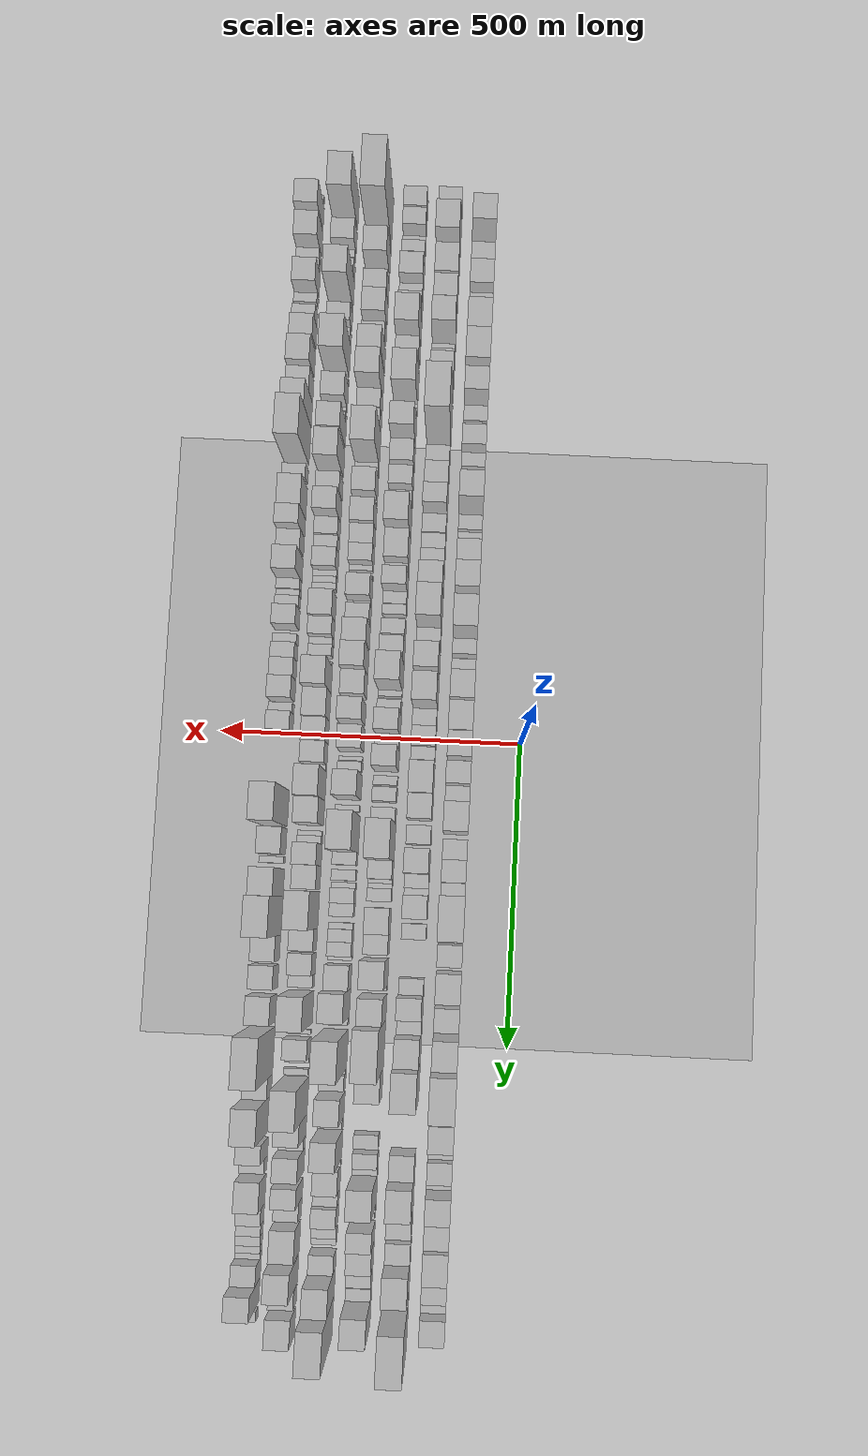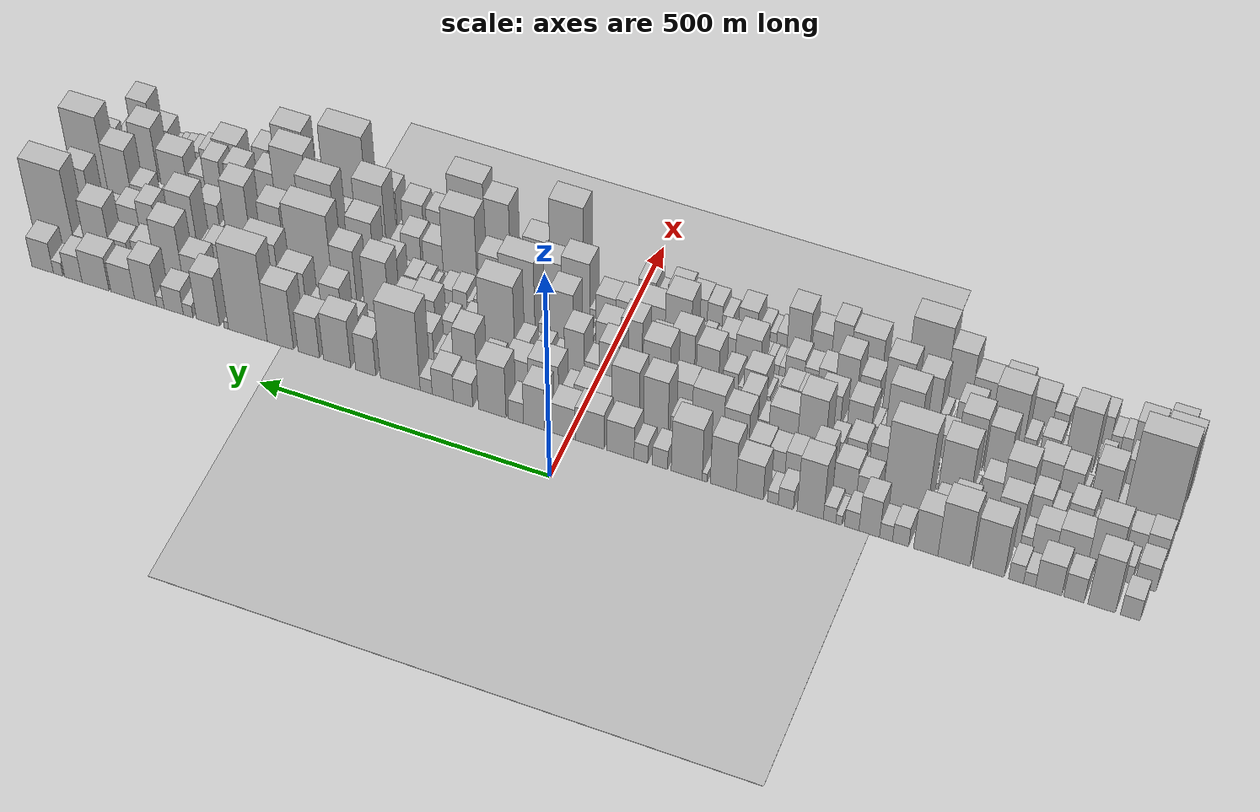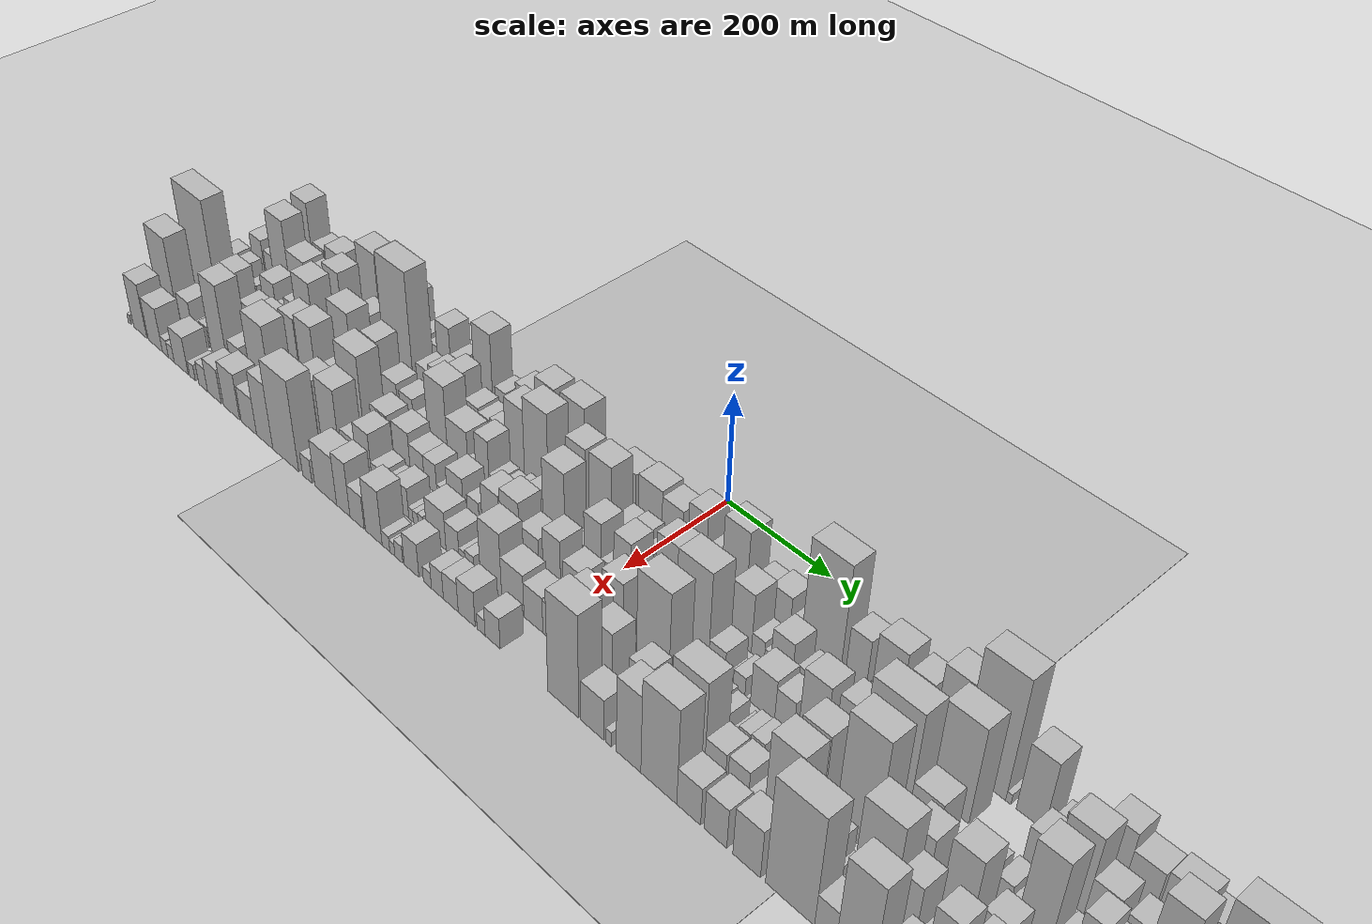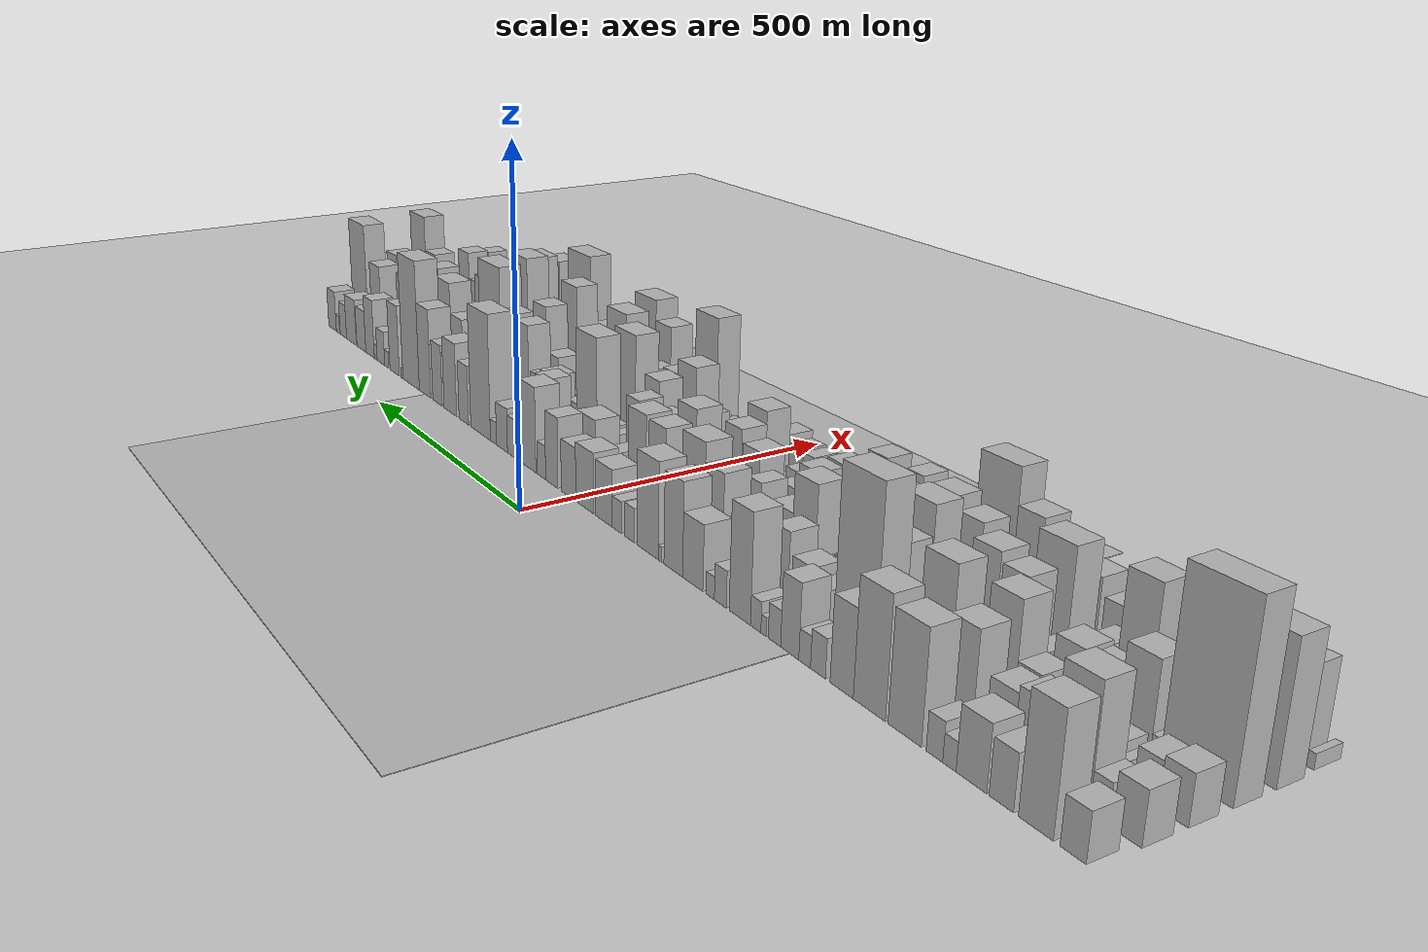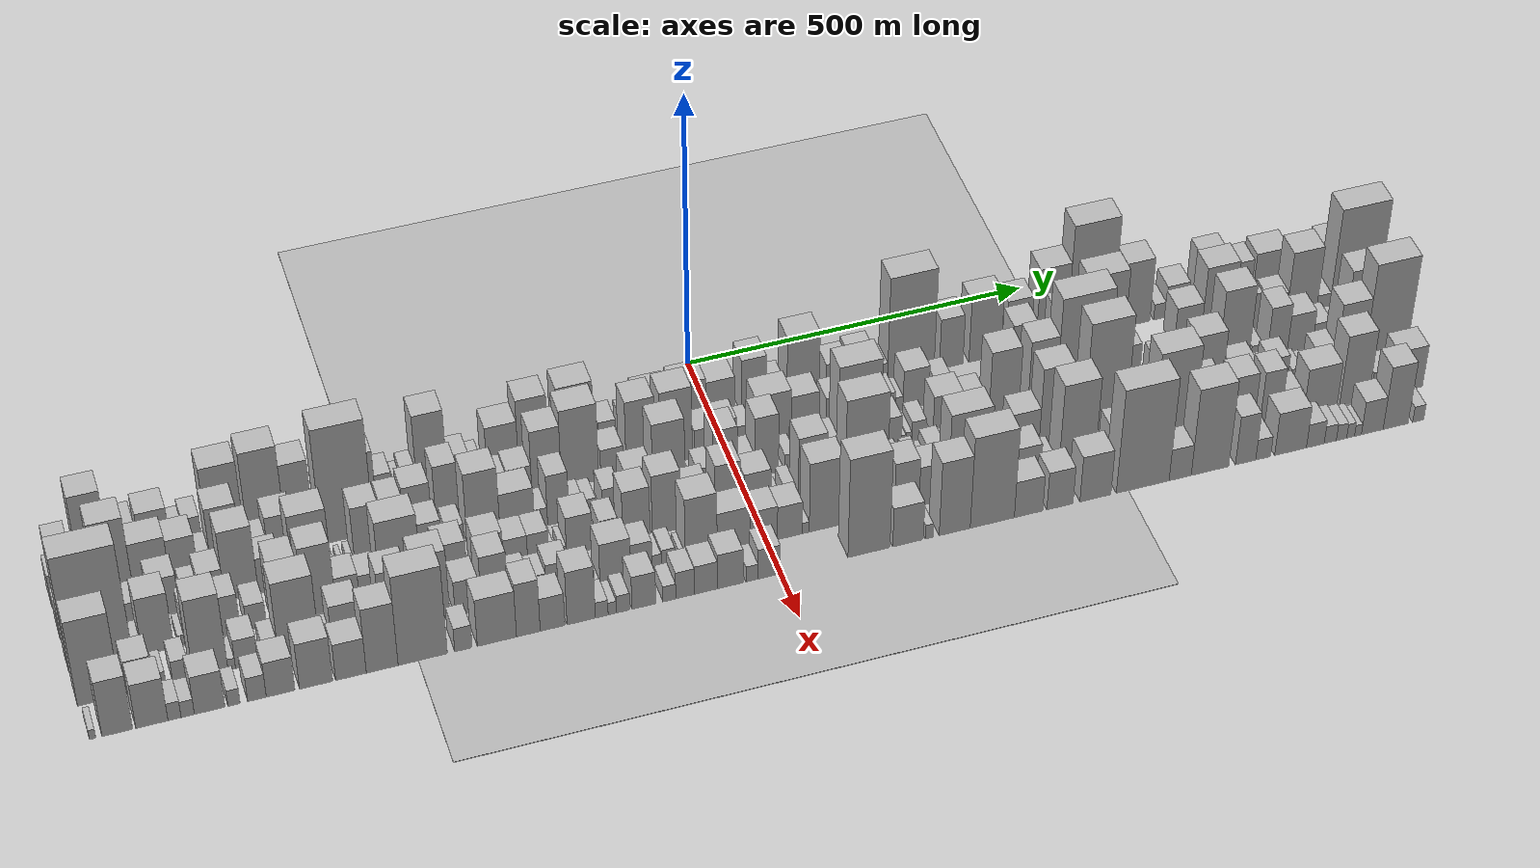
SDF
<?xml version="1.0" encoding="utf-8"?>

<sdf version="1.6">

   <world name="default">

      <gui fullscreen="0">

         <camera name="user_camera">

            <pose>-15 0 4.57585 0 0 0</pose>

            <view_controller>orbit</view_controller>

         </camera>

      </gui>

      <scene>

         <sky>

           <clouds>

             <speed>12</speed>

           </clouds>

         </sky>

         <ambient>0.4 0.4 0.4 1</ambient>

         <background>0.7 0.7 0.7 1</background>

         <shadows>1</shadows>

      </scene>

      <gravity>0 0 -9.8066</gravity>

      <magnetic_field>6e-06 2.3e-05 -4.2e-05</magnetic_field>

      <physics default="0" name="default_physics" type="ode">

         <ode>

            <solver>

               <type>quick</type>

               <iters>10</iters>

               <sor>1.0</sor>

               <use_dynamic_moi_rescaling>0</use_dynamic_moi_rescaling>

            </solver>

            <constraints>

               <cfm>0</cfm>

               <erp>0.2</erp>

               <contact_max_correcting_vel>100</contact_max_correcting_vel>

               <contact_surface_layer>0.001</contact_surface_layer>

            </constraints>

         </ode>

         <max_step_size>0.004</max_step_size>

         <real_time_factor>1</real_time_factor>

         <real_time_update_rate>250</real_time_update_rate>

      </physics>

      <light name="sun" type="directional">

         <cast_shadows>1</cast_shadows>

         <pose>0 0 10 0 0 0</pose>

         <diffuse>0.8 0.8 0.8 1</diffuse>

         <specular>0.2 0.2 0.2 1</specular>

         <attenuation>

            <range>1000</range>

            <constant>0.9</constant>

            <linear>0.01</linear>

            <quadratic>0.001</quadratic>

         </attenuation>

         <direction>-0.5 0.1 -0.9</direction>

      </light>

      <include>

         <name>ground_plane_1</name>

         <uri>model://HANNAS_ground_plane</uri>

         <pose>0 0 0  0 0 0</pose>

      </include>

      <include>

         <name>ground_plane_2</name>

         <uri>model://HANNAS_ground_plane</uri>

         <pose>100 0 0  0 0 0</pose>

      </include>

      <model name="building_1">

         <static>1</static>

         <pose frame="">100.0000 -916.5898 0 0.000000 0.000000 0.000000</pose>

         <link name="link">

            <pose frame="">0 0 27.00 0 0 0</pose>

            <collision name="collision">

               <geometry>

                  <box>

                     <size>40.0000 30.8204 54.0000</size>

                  </box>

               </geometry>

               <max_contacts>10</max_contacts>

               <surface>

                  <contact>

                     <ode/>

                  </contact>

                  <bounce/>

                  <friction>

                     <torsional>

                        <ode/>

                     </torsional>

                     <ode/>

                  </friction>

               </surface>

            </collision>

            <visual name="visual">

               <cast_shadows>0</cast_shadows>

               <geometry>

                  <box>

                     <size>40.0000 30.8204 54.0000</size>

                  </box>

               </geometry>

               <material>

                  <script>

                     <uri>model://HANNAS_wall/materials/scripts</uri>

                     <uri>model://HANNAS_wall/materials/textures</uri>

                     <name>vrc/HANNAS_wall</name>

                  </script>

               </material>

            </visual>

            <self_collide>0</self_collide>

            <enable_wind>0</enable_wind>

            <kinematic>0</kinematic>

         </link>

      </model>

      <model name="building_2">

         <static>1</static>

         <pose frame="">100.0000 -871.5091 0 0.000000 0.000000 0.000000</pose>

         <link name="link">

            <pose frame="">0 0 67.50 0 0 0</pose>

            <collision name="collision">

               <geometry>

                  <box>

                     <size>40.0000 43.3409 135.0000</size>

                  </box>

               </geometry>

               <max_contacts>10</max_contacts>

               <surface>

                  <contact>

                     <ode/>

                  </contact>

                  <bounce/>

                  <friction>

                     <torsional>

                        <ode/>

                     </torsional>

                     <ode/>

                  </friction>

               </surface>

            </collision>

            <visual name="visual">

               <cast_shadows>0</cast_shadows>

               <geometry>

                  <box>

                     <size>40.0000 43.3409 135.0000</size>

                  </box>

               </geometry>

               <material>

                  <script>

                     <uri>model://HANNAS_wall/materials/scripts</uri>

                     <uri>model://HANNAS_wall/materials/textures</uri>

                     <name>vrc/HANNAS_wall</name>

                  </script>

               </material>

            </visual>

            <self_collide>0</self_collide>

            <enable_wind>0</enable_wind>

            <kinematic>0</kinematic>

         </link>

      </model>

      <model name="building_3">

         <static>1</static>

         <pose frame="">100.0000 -827.7972 0 0.000000 0.000000 0.000000</pose>

         <link name="link">

            <pose frame="">0 0 31.50 0 0 0</pose>

            <collision name="collision">

               <geometry>

                  <box>

                     <size>40.0000 32.0829 63.0000</size>

                  </box>

               </geometry>

               <max_contacts>10</max_contacts>

               <surface>

                  <contact>

                     <ode/>

                  </contact>

                  <bounce/>

                  <friction>

                     <torsional>

                        <ode/>

                     </torsional>

                     <ode/>

                  </friction>

               </surface>

            </collision>

            <visual name="visual">

               <cast_shadows>0</cast_shadows>

               <geometry>

                  <box>

                     <size>40.0000 32.0829 63.0000</size>

                  </box>

               </geometry>

               <material>

                  <script>

                     <uri>model://HANNAS_wall/materials/scripts</uri>

                     <uri>model://HANNAS_wall/materials/textures</uri>

                     <name>vrc/HANNAS_wall</name>

                  </script>

               </material>

            </visual>

            <self_collide>0</self_collide>

            <enable_wind>0</enable_wind>

            <kinematic>0</kinematic>

         </link>

      </model>

      <model name="building_4">

         <static>1</static>

         <pose frame="">100.0000 -787.8705 0 0.000000 0.000000 0.000000</pose>

         <link name="link">

            <pose frame="">0 0 37.50 0 0 0</pose>

            <collision name="collision">

               <geometry>

                  <box>

                     <size>40.0000 41.7706 75.0000</size>

                  </box>

               </geometry>

               <max_contacts>10</max_contacts>

               <surface>

                  <contact>

                     <ode/>

                  </contact>

                  <bounce/>

                  <friction>

                     <torsional>

                        <ode/>

                     </torsional>

                     <ode/>

                  </friction>

               </surface>

            </collision>

            <visual name="visual">

               <cast_shadows>0</cast_shadows>

               <geometry>

                  <box>

                     <size>40.0000 41.7706 75.0000</size>

                  </box>

               </geometry>

               <material>

                  <script>

                     <uri>model://HANNAS_wall/materials/scripts</uri>

                     <uri>model://HANNAS_wall/materials/textures</uri>

                     <name>vrc/HANNAS_wall</name>

                  </script>

               </material>

            </visual>

            <self_collide>0</self_collide>

            <enable_wind>0</enable_wind>

            <kinematic>0</kinematic>

         </link>

      </model>

      <model name="building_5">

         <static>1</static>

         <pose frame="">100.0000 -757.5340 0 0.000000 0.000000 0.000000</pose>

         <link name="link">

            <pose frame="">0 0 16.50 0 0 0</pose>

            <collision name="collision">

               <geometry>

                  <box>

                     <size>40.0000 18.9024 33.0000</size>

                  </box>

               </geometry>

               <max_contacts>10</max_contacts>

               <surface>

                  <contact>

                     <ode/>

                  </contact>

                  <bounce/>

                  <friction>

                     <torsional>

                        <ode/>

                     </torsional>

                     <ode/>

                  </friction>

               </surface>

            </collision>

            <visual name="visual">

               <cast_shadows>0</cast_shadows>

               <geometry>

                  <box>

                     <size>40.0000 18.9024 33.0000</size>

                  </box>

               </geometry>

               <material>

                  <script>

                     <uri>model://HANNAS_wall/materials/scripts</uri>

                     <uri>model://HANNAS_wall/materials/textures</uri>

                     <name>vrc/HANNAS_wall</name>

                  </script>

               </material>

            </visual>

            <self_collide>0</self_collide>

            <enable_wind>0</enable_wind>

            <kinematic>0</kinematic>

         </link>

      </model>

      <model name="building_6">

         <static>1</static>

         <pose frame="">100.0000 -736.1260 0 0.000000 0.000000 0.000000</pose>

         <link name="link">

            <pose frame="">0 0 22.50 0 0 0</pose>

            <collision name="collision">

               <geometry>

                  <box>

                     <size>40.0000 23.9137 45.0000</size>

                  </box>

               </geometry>

               <max_contacts>10</max_contacts>

               <surface>

                  <contact>

                     <ode/>

                  </contact>

                  <bounce/>

                  <friction>

                     <torsional>

                        <ode/>

                     </torsional>

                     <ode/>

                  </friction>

               </surface>

            </collision>

            <visual name="visual">

               <cast_shadows>0</cast_shadows>

               <geometry>

                  <box>

                     <size>40.0000 23.9137 45.0000</size>

                  </box>

               </geometry>

               <material>

                  <script>

                     <uri>model://HANNAS_wall/materials/scripts</uri>

                     <uri>model://HANNAS_wall/materials/textures</uri>

                     <name>vrc/HANNAS_wall</name>

                  </script>

               </material>

            </visual>

            <self_collide>0</self_collide>

            <enable_wind>0</enable_wind>

            <kinematic>0</kinematic>

         </link>

      </model>

      <model name="building_7">

         <static>1</static>

         <pose frame="">100.0000 -691.8284 0 0.000000 0.000000 0.000000</pose>

         <link name="link">

            <pose frame="">0 0 66.00 0 0 0</pose>

            <collision name="collision">

               <geometry>

                  <box>

                     <size>40.0000 50.6814 132.0000</size>

                  </box>

               </geometry>

               <max_contacts>10</max_contacts>

               <surface>

                  <contact>

                     <ode/>

                  </contact>

                  <bounce/>

                  <friction>

                     <torsional>

                        <ode/>

                     </torsional>

                     <ode/>

                  </friction>

               </surface>

            </collision>

            <visual name="visual">

               <cast_shadows>0</cast_shadows>

               <geometry>

                  <box>

                     <size>40.0000 50.6814 132.0000</size>

                  </box>

               </geometry>

               <material>

                  <script>

                     <uri>model://HANNAS_wall/materials/scripts</uri>

                     <uri>model://HANNAS_wall/materials/textures</uri>

                     <name>vrc/HANNAS_wall</name>

                  </script>

               </material>

            </visual>

            <self_collide>0</self_collide>

            <enable_wind>0</enable_wind>

            <kinematic>0</kinematic>

         </link>

      </model>

      <model name="building_8">

         <static>1</static>

         <pose frame="">100.0000 -636.6558 0 0.000000 0.000000 0.000000</pose>

         <link name="link">

            <pose frame="">0 0 72.00 0 0 0</pose>

            <collision name="collision">

               <geometry>

                  <box>

                     <size>40.0000 51.6640 144.0000</size>

                  </box>

               </geometry>

               <max_contacts>10</max_contacts>

               <surface>

                  <contact>

                     <ode/>

                  </contact>

                  <bounce/>

                  <friction>

                     <torsional>

                        <ode/>

                     </torsional>

                     <ode/>

                  </friction>

               </surface>

            </collision>

            <visual name="visual">

               <cast_shadows>0</cast_shadows>

               <geometry>

                  <box>

                     <size>40.0000 51.6640 144.0000</size>

                  </box>

               </geometry>

               <material>

                  <script>

                     <uri>model://HANNAS_wall/materials/scripts</uri>

                     <uri>model://HANNAS_wall/materials/textures</uri>

                     <name>vrc/HANNAS_wall</name>

                  </script>

               </material>

            </visual>

            <self_collide>0</self_collide>

            <enable_wind>0</enable_wind>

            <kinematic>0</kinematic>

         </link>

      </model>

      <model name="building_9">

         <static>1</static>

         <pose frame="">100.0000 -591.2603 0 0.000000 0.000000 0.000000</pose>

         <link name="link">

            <pose frame="">0 0 52.50 0 0 0</pose>

            <collision name="collision">

               <geometry>

                  <box>

                     <size>40.0000 39.1270 105.0000</size>

                  </box>

               </geometry>

               <max_contacts>10</max_contacts>

               <surface>

                  <contact>

                     <ode/>

                  </contact>

                  <bounce/>

                  <friction>

                     <torsional>

                        <ode/>

                     </torsional>

                     <ode/>

                  </friction>

               </surface>

            </collision>

            <visual name="visual">

               <cast_shadows>0</cast_shadows>

               <geometry>

                  <box>

                     <size>40.0000 39.1270 105.0000</size>

                  </box>

               </geometry>

               <material>

                  <script>

                     <uri>model://HANNAS_wall/materials/scripts</uri>

                     <uri>model://HANNAS_wall/materials/textures</uri>

                     <name>vrc/HANNAS_wall</name>

                  </script>

               </material>

            </visual>

            <self_collide>0</self_collide>

            <enable_wind>0</enable_wind>

            <kinematic>0</kinematic>

         </link>

      </model>

      <model name="building_10">

         <static>1</static>

         <pose frame="">100.0000 -550.6019 0 0.000000 0.000000 0.000000</pose>

         <link name="link">

            <pose frame="">0 0 24.00 0 0 0</pose>

            <collision name="collision">

               <geometry>

                  <box>

                     <size>40.0000 26.1898 48.0000</size>

                  </box>

               </geometry>

               <max_contacts>10</max_contacts>

               <surface>

                  <contact>

                     <ode/>

                  </contact>

                  <bounce/>

                  <friction>

                     <torsional>

                        <ode/>

                     </torsional>

                     <ode/>

                  </friction>

               </surface>

            </collision>

            <visual name="visual">

               <cast_shadows>0</cast_shadows>

               <geometry>

                  <box>

                     <size>40.0000 26.1898 48.0000</size>

                  </box>

               </geometry>

               <material>

                  <script>

                     <uri>model://HANNAS_wall/materials/scripts</uri>

                     <uri>model://HANNAS_wall/materials/textures</uri>

                     <name>vrc/HANNAS_wall</name>

                  </script>

               </material>

            </visual>

            <self_collide>0</self_collide>

            <enable_wind>0</enable_wind>

            <kinematic>0</kinematic>

         </link>

      </model>

      <model name="building_11">

         <static>1</static>

         <pose frame="">100.0000 -526.9672 0 0.000000 0.000000 0.000000</pose>

         <link name="link">

            <pose frame="">0 0 19.50 0 0 0</pose>

            <collision name="collision">

               <geometry>

                  <box>

                     <size>40.0000 21.0796 39.0000</size>

                  </box>

               </geometry>

               <max_contacts>10</max_contacts>

               <surface>

                  <contact>

                     <ode/>

                  </contact>

                  <bounce/>

                  <friction>

                     <torsional>

                        <ode/>

                     </torsional>

                     <ode/>

                  </friction>

               </surface>

            </collision>

            <visual name="visual">

               <cast_shadows>0</cast_shadows>

               <geometry>

                  <box>

                     <size>40.0000 21.0796 39.0000</size>

                  </box>

               </geometry>

               <material>

                  <script>

                     <uri>model://HANNAS_wall/materials/scripts</uri>

                     <uri>model://HANNAS_wall/materials/textures</uri>

                     <name>vrc/HANNAS_wall</name>

                  </script>

               </material>

            </visual>

            <self_collide>0</self_collide>

            <enable_wind>0</enable_wind>

            <kinematic>0</kinematic>

         </link>

      </model>

      <model name="building_12">

         <static>1</static>

         <pose frame="">100.0000 -499.6804 0 0.000000 0.000000 0.000000</pose>

         <link name="link">

            <pose frame="">0 0 46.50 0 0 0</pose>

            <collision name="collision">

               <geometry>

                  <box>

                     <size>40.0000 33.4940 93.0000</size>

                  </box>

               </geometry>

               <max_contacts>10</max_contacts>

               <surface>

                  <contact>

                     <ode/>

                  </contact>

                  <bounce/>

                  <friction>

                     <torsional>

                        <ode/>

                     </torsional>

                     <ode/>

                  </friction>

               </surface>

            </collision>

            <visual name="visual">

               <cast_shadows>0</cast_shadows>

               <geometry>

                  <box>

                     <size>40.0000 33.4940 93.0000</size>

                  </box>

               </geometry>

               <material>

                  <script>

                     <uri>model://HANNAS_wall/materials/scripts</uri>

                     <uri>model://HANNAS_wall/materials/textures</uri>

                     <name>vrc/HANNAS_wall</name>

                  </script>

               </material>

            </visual>

            <self_collide>0</self_collide>

            <enable_wind>0</enable_wind>

            <kinematic>0</kinematic>

         </link>

      </model>

      <model name="building_13">

         <static>1</static>

         <pose frame="">100.0000 -471.1285 0 0.000000 0.000000 0.000000</pose>

         <link name="link">

            <pose frame="">0 0 22.50 0 0 0</pose>

            <collision name="collision">

               <geometry>

                  <box>

                     <size>40.0000 23.6097 45.0000</size>

                  </box>

               </geometry>

               <max_contacts>10</max_contacts>

               <surface>

                  <contact>

                     <ode/>

                  </contact>

                  <bounce/>

                  <friction>

                     <torsional>

                        <ode/>

                     </torsional>

                     <ode/>

                  </friction>

               </surface>

            </collision>

            <visual name="visual">

               <cast_shadows>0</cast_shadows>

               <geometry>

                  <box>

                     <size>40.0000 23.6097 45.0000</size>

                  </box>

               </geometry>

               <material>

                  <script>

                     <uri>model://HANNAS_wall/materials/scripts</uri>

                     <uri>model://HANNAS_wall/materials/textures</uri>

                     <name>vrc/HANNAS_wall</name>

                  </script>

               </material>

            </visual>

            <self_collide>0</self_collide>

            <enable_wind>0</enable_wind>

            <kinematic>0</kinematic>

         </link>

      </model>

      <model name="building_14">

         <static>1</static>

         <pose frame="">100.0000 -450.2228 0 0.000000 0.000000 0.000000</pose>

         <link name="link">

            <pose frame="">0 0 12.00 0 0 0</pose>

            <collision name="collision">

               <geometry>

                  <box>

                     <size>40.0000 10.2017 24.0000</size>

                  </box>

               </geometry>

               <max_contacts>10</max_contacts>

               <surface>

                  <contact>

                     <ode/>

                  </contact>

                  <bounce/>

                  <friction>

                     <torsional>

                        <ode/>

                     </torsional>

                     <ode/>

                  </friction>

               </surface>

            </collision>

            <visual name="visual">

               <cast_shadows>0</cast_shadows>

               <geometry>

                  <box>

                     <size>40.0000 10.2017 24.0000</size>

                  </box>

               </geometry>

               <material>

                  <script>

                     <uri>model://HANNAS_wall/materials/scripts</uri>

                     <uri>model://HANNAS_wall/materials/textures</uri>

                     <name>vrc/HANNAS_wall</name>

                  </script>

               </material>

            </visual>

            <self_collide>0</self_collide>

            <enable_wind>0</enable_wind>

            <kinematic>0</kinematic>

         </link>

      </model>

      <model name="building_15">

         <static>1</static>

         <pose frame="">100.0000 -434.9194 0 0.000000 0.000000 0.000000</pose>

         <link name="link">

            <pose frame="">0 0 19.50 0 0 0</pose>

            <collision name="collision">

               <geometry>

                  <box>

                     <size>40.0000 20.4052 39.0000</size>

                  </box>

               </geometry>

               <max_contacts>10</max_contacts>

               <surface>

                  <contact>

                     <ode/>

                  </contact>

                  <bounce/>

                  <friction>

                     <torsional>

                        <ode/>

                     </torsional>

                     <ode/>

                  </friction>

               </surface>

            </collision>

            <visual name="visual">

               <cast_shadows>0</cast_shadows>

               <geometry>

                  <box>

                     <size>40.0000 20.4052 39.0000</size>

                  </box>

               </geometry>

               <material>

                  <script>

                     <uri>model://HANNAS_wall/materials/scripts</uri>

                     <uri>model://HANNAS_wall/materials/textures</uri>

                     <name>vrc/HANNAS_wall</name>

                  </script>

               </material>

            </visual>

            <self_collide>0</self_collide>

            <enable_wind>0</enable_wind>

            <kinematic>0</kinematic>

         </link>

      </model>

      <model name="building_16">

         <static>1</static>

         <pose frame="">100.0000 -403.1616 0 0.000000 0.000000 0.000000</pose>

         <link name="link">

            <pose frame="">0 0 70.50 0 0 0</pose>

            <collision name="collision">

               <geometry>

                  <box>

                     <size>40.0000 43.1104 141.0000</size>

                  </box>

               </geometry>

               <max_contacts>10</max_contacts>

               <surface>

                  <contact>

                     <ode/>

                  </contact>

                  <bounce/>

                  <friction>

                     <torsional>

                        <ode/>

                     </torsional>

                     <ode/>

                  </friction>

               </surface>

            </collision>

            <visual name="visual">

               <cast_shadows>0</cast_shadows>

               <geometry>

                  <box>

                     <size>40.0000 43.1104 141.0000</size>

                  </box>

               </geometry>

               <material>

                  <script>

                     <uri>model://HANNAS_wall/materials/scripts</uri>

                     <uri>model://HANNAS_wall/materials/textures</uri>

                     <name>vrc/HANNAS_wall</name>

                  </script>

               </material>

            </visual>

            <self_collide>0</self_collide>

            <enable_wind>0</enable_wind>

            <kinematic>0</kinematic>

         </link>

      </model>

      <model name="building_17">

         <static>1</static>

         <pose frame="">100.0000 -363.1013 0 0.000000 0.000000 0.000000</pose>

         <link name="link">

            <pose frame="">0 0 24.00 0 0 0</pose>

            <collision name="collision">

               <geometry>

                  <box>

                     <size>40.0000 25.0103 48.0000</size>

                  </box>

               </geometry>

               <max_contacts>10</max_contacts>

               <surface>

                  <contact>

                     <ode/>

                  </contact>

                  <bounce/>

                  <friction>

                     <torsional>

                        <ode/>

                     </torsional>

                     <ode/>

                  </friction>

               </surface>

            </collision>

            <visual name="visual">

               <cast_shadows>0</cast_shadows>

               <geometry>

                  <box>

                     <size>40.0000 25.0103 48.0000</size>

                  </box>

               </geometry>

               <material>

                  <script>

                     <uri>model://HANNAS_wall/materials/scripts</uri>

                     <uri>model://HANNAS_wall/materials/textures</uri>

                     <name>vrc/HANNAS_wall</name>

                  </script>

               </material>

            </visual>

            <self_collide>0</self_collide>

            <enable_wind>0</enable_wind>

            <kinematic>0</kinematic>

         </link>

      </model>

      <model name="building_18">

         <static>1</static>

         <pose frame="">100.0000 -341.6926 0 0.000000 0.000000 0.000000</pose>

         <link name="link">

            <pose frame="">0 0 15.00 0 0 0</pose>

            <collision name="collision">

               <geometry>

                  <box>

                     <size>40.0000 17.8071 30.0000</size>

                  </box>

               </geometry>

               <max_contacts>10</max_contacts>

               <surface>

                  <contact>

                     <ode/>

                  </contact>

                  <bounce/>

                  <friction>

                     <torsional>

                        <ode/>

                     </torsional>

                     <ode/>

                  </friction>

               </surface>

            </collision>

            <visual name="visual">

               <cast_shadows>0</cast_shadows>

               <geometry>

                  <box>

                     <size>40.0000 17.8071 30.0000</size>

                  </box>

               </geometry>

               <material>

                  <script>

                     <uri>model://HANNAS_wall/materials/scripts</uri>

                     <uri>model://HANNAS_wall/materials/textures</uri>

                     <name>vrc/HANNAS_wall</name>

                  </script>

               </material>

            </visual>

            <self_collide>0</self_collide>

            <enable_wind>0</enable_wind>

            <kinematic>0</kinematic>

         </link>

      </model>

      <model name="building_19">

         <static>1</static>

         <pose frame="">100.0000 -303.3781 0 0.000000 0.000000 0.000000</pose>

         <link name="link">

            <pose frame="">0 0 43.50 0 0 0</pose>

            <collision name="collision">

               <geometry>

                  <box>

                     <size>40.0000 44.8218 87.0000</size>

                  </box>

               </geometry>

               <max_contacts>10</max_contacts>

               <surface>

                  <contact>

                     <ode/>

                  </contact>

                  <bounce/>

                  <friction>

                     <torsional>

                        <ode/>

                     </torsional>

                     <ode/>

                  </friction>

               </surface>

            </collision>

            <visual name="visual">

               <cast_shadows>0</cast_shadows>

               <geometry>

                  <box>

                     <size>40.0000 44.8218 87.0000</size>

                  </box>

               </geometry>

               <material>

                  <script>

                     <uri>model://HANNAS_wall/materials/scripts</uri>

                     <uri>model://HANNAS_wall/materials/textures</uri>

                     <name>vrc/HANNAS_wall</name>

                  </script>

               </material>

            </visual>

            <self_collide>0</self_collide>

            <enable_wind>0</enable_wind>

            <kinematic>0</kinematic>

         </link>

      </model>

      <model name="building_20">

         <static>1</static>

         <pose frame="">100.0000 -259.4661 0 0.000000 0.000000 0.000000</pose>

         <link name="link">

            <pose frame="">0 0 63.00 0 0 0</pose>

            <collision name="collision">

               <geometry>

                  <box>

                     <size>40.0000 43.0022 126.0000</size>

                  </box>

               </geometry>

               <max_contacts>10</max_contacts>

               <surface>

                  <contact>

                     <ode/>

                  </contact>

                  <bounce/>

                  <friction>

                     <torsional>

                        <ode/>

                     </torsional>

                     <ode/>

                  </friction>

               </surface>

            </collision>

            <visual name="visual">

               <cast_shadows>0</cast_shadows>

               <geometry>

                  <box>

                     <size>40.0000 43.0022 126.0000</size>

                  </box>

               </geometry>

               <material>

                  <script>

                     <uri>model://HANNAS_wall/materials/scripts</uri>

                     <uri>model://HANNAS_wall/materials/textures</uri>

                     <name>vrc/HANNAS_wall</name>

                  </script>

               </material>

            </visual>

            <self_collide>0</self_collide>

            <enable_wind>0</enable_wind>

            <kinematic>0</kinematic>

         </link>

      </model>

      <model name="building_21">

         <static>1</static>

         <pose frame="">100.0000 -228.6467 0 0.000000 0.000000 0.000000</pose>

         <link name="link">

            <pose frame="">0 0 10.50 0 0 0</pose>

            <collision name="collision">

               <geometry>

                  <box>

                     <size>40.0000 8.6366 21.0000</size>

                  </box>

               </geometry>

               <max_contacts>10</max_contacts>

               <surface>

                  <contact>

                     <ode/>

                  </contact>

                  <bounce/>

                  <friction>

                     <torsional>

                        <ode/>

                     </torsional>

                     <ode/>

                  </friction>

               </surface>

            </collision>

            <visual name="visual">

               <cast_shadows>0</cast_shadows>

               <geometry>

                  <box>

                     <size>40.0000 8.6366 21.0000</size>

                  </box>

               </geometry>

               <material>

                  <script>

                     <uri>model://HANNAS_wall/materials/scripts</uri>

                     <uri>model://HANNAS_wall/materials/textures</uri>

                     <name>vrc/HANNAS_wall</name>

                  </script>

               </material>

            </visual>

            <self_collide>0</self_collide>

            <enable_wind>0</enable_wind>

            <kinematic>0</kinematic>

         </link>

      </model>

      <model name="building_22">

         <static>1</static>

         <pose frame="">100.0000 -198.5021 0 0.000000 0.000000 0.000000</pose>

         <link name="link">

            <pose frame="">0 0 66.00 0 0 0</pose>

            <collision name="collision">

               <geometry>

                  <box>

                     <size>40.0000 51.6525 132.0000</size>

                  </box>

               </geometry>

               <max_contacts>10</max_contacts>

               <surface>

                  <contact>

                     <ode/>

                  </contact>

                  <bounce/>

                  <friction>

                     <torsional>

                        <ode/>

                     </torsional>

                     <ode/>

                  </friction>

               </surface>

            </collision>

            <visual name="visual">

               <cast_shadows>0</cast_shadows>

               <geometry>

                  <box>

                     <size>40.0000 51.6525 132.0000</size>

                  </box>

               </geometry>

               <material>

                  <script>

                     <uri>model://HANNAS_wall/materials/scripts</uri>

                     <uri>model://HANNAS_wall/materials/textures</uri>

                     <name>vrc/HANNAS_wall</name>

                  </script>

               </material>

            </visual>

            <self_collide>0</self_collide>

            <enable_wind>0</enable_wind>

            <kinematic>0</kinematic>

         </link>

      </model>

      <model name="building_23">

         <static>1</static>

         <pose frame="">100.0000 -153.9269 0 0.000000 0.000000 0.000000</pose>

         <link name="link">

            <pose frame="">0 0 24.00 0 0 0</pose>

            <collision name="collision">

               <geometry>

                  <box>

                     <size>40.0000 25.4979 48.0000</size>

                  </box>

               </geometry>

               <max_contacts>10</max_contacts>

               <surface>

                  <contact>

                     <ode/>

                  </contact>

                  <bounce/>

                  <friction>

                     <torsional>

                        <ode/>

                     </torsional>

                     <ode/>

                  </friction>

               </surface>

            </collision>

            <visual name="visual">

               <cast_shadows>0</cast_shadows>

               <geometry>

                  <box>

                     <size>40.0000 25.4979 48.0000</size>

                  </box>

               </geometry>

               <material>

                  <script>

                     <uri>model://HANNAS_wall/materials/scripts</uri>

                     <uri>model://HANNAS_wall/materials/textures</uri>

                     <name>vrc/HANNAS_wall</name>

                  </script>

               </material>

            </visual>

            <self_collide>0</self_collide>

            <enable_wind>0</enable_wind>

            <kinematic>0</kinematic>

         </link>

      </model>

      <model name="building_24">

         <static>1</static>

         <pose frame="">100.0000 -121.7348 0 0.000000 0.000000 0.000000</pose>

         <link name="link">

            <pose frame="">0 0 22.50 0 0 0</pose>

            <collision name="collision">

               <geometry>

                  <box>

                     <size>40.0000 22.8863 45.0000</size>

                  </box>

               </geometry>

               <max_contacts>10</max_contacts>

               <surface>

                  <contact>

                     <ode/>

                  </contact>

                  <bounce/>

                  <friction>

                     <torsional>

                        <ode/>

                     </torsional>

                     <ode/>

                  </friction>

               </surface>

            </collision>

            <visual name="visual">

               <cast_shadows>0</cast_shadows>

               <geometry>

                  <box>

                     <size>40.0000 22.8863 45.0000</size>

                  </box>

               </geometry>

               <material>

                  <script>

                     <uri>model://HANNAS_wall/materials/scripts</uri>

                     <uri>model://HANNAS_wall/materials/textures</uri>

                     <name>vrc/HANNAS_wall</name>

                  </script>

               </material>

            </visual>

            <self_collide>0</self_collide>

            <enable_wind>0</enable_wind>

            <kinematic>0</kinematic>

         </link>

      </model>

      <model name="building_25">

         <static>1</static>

         <pose frame="">100.0000 -87.3126 0 0.000000 0.000000 0.000000</pose>

         <link name="link">

            <pose frame="">0 0 40.50 0 0 0</pose>

            <collision name="collision">

               <geometry>

                  <box>

                     <size>40.0000 45.9582 81.0000</size>

                  </box>

               </geometry>

               <max_contacts>10</max_contacts>

               <surface>

                  <contact>

                     <ode/>

                  </contact>

                  <bounce/>

                  <friction>

                     <torsional>

                        <ode/>

                     </torsional>

                     <ode/>

                  </friction>

               </surface>

            </collision>

            <visual name="visual">

               <cast_shadows>0</cast_shadows>

               <geometry>

                  <box>

                     <size>40.0000 45.9582 81.0000</size>

                  </box>

               </geometry>

               <material>

                  <script>

                     <uri>model://HANNAS_wall/materials/scripts</uri>

                     <uri>model://HANNAS_wall/materials/textures</uri>

                     <name>vrc/HANNAS_wall</name>

                  </script>

               </material>

            </visual>

            <self_collide>0</self_collide>

            <enable_wind>0</enable_wind>

            <kinematic>0</kinematic>

         </link>

      </model>

      <model name="building_26">

         <static>1</static>

         <pose frame="">100.0000 -35.0738 0 0.000000 0.000000 0.000000</pose>

         <link name="link">

            <pose frame="">0 0 43.50 0 0 0</pose>

            <collision name="collision">

               <geometry>

                  <box>

                     <size>40.0000 48.5195 87.0000</size>

                  </box>

               </geometry>

               <max_contacts>10</max_contacts>

               <surface>

                  <contact>

                     <ode/>

                  </contact>

                  <bounce/>

                  <friction>

                     <torsional>

                        <ode/>

                     </torsional>

                     <ode/>

                  </friction>

               </surface>

            </collision>

            <visual name="visual">

               <cast_shadows>0</cast_shadows>

               <geometry>

                  <box>

                     <size>40.0000 48.5195 87.0000</size>

                  </box>

               </geometry>

               <material>

                  <script>

                     <uri>model://HANNAS_wall/materials/scripts</uri>

                     <uri>model://HANNAS_wall/materials/textures</uri>

                     <name>vrc/HANNAS_wall</name>

                  </script>

               </material>

            </visual>

            <self_collide>0</self_collide>

            <enable_wind>0</enable_wind>

            <kinematic>0</kinematic>

         </link>

      </model>

      <model name="building_27">

         <static>1</static>

         <pose frame="">100.0000 10.1587 0 0.000000 0.000000 0.000000</pose>

         <link name="link">

            <pose frame="">0 0 39.00 0 0 0</pose>

            <collision name="collision">

               <geometry>

                  <box>

                     <size>40.0000 41.9455 78.0000</size>

                  </box>

               </geometry>

               <max_contacts>10</max_contacts>

               <surface>

                  <contact>

                     <ode/>

                  </contact>

                  <bounce/>

                  <friction>

                     <torsional>

                        <ode/>

                     </torsional>

                     <ode/>

                  </friction>

               </surface>

            </collision>

            <visual name="visual">

               <cast_shadows>0</cast_shadows>

               <geometry>

                  <box>

                     <size>40.0000 41.9455 78.0000</size>

                  </box>

               </geometry>

               <material>

                  <script>

                     <uri>model://HANNAS_wall/materials/scripts</uri>

                     <uri>model://HANNAS_wall/materials/textures</uri>

                     <name>vrc/HANNAS_wall</name>

                  </script>

               </material>

            </visual>

            <self_collide>0</self_collide>

            <enable_wind>0</enable_wind>

            <kinematic>0</kinematic>

         </link>

      </model>

      <model name="building_28">

         <static>1</static>

         <pose frame="">100.0000 59.2522 0 0.000000 0.000000 0.000000</pose>

         <link name="link">

            <pose frame="">0 0 52.50 0 0 0</pose>

            <collision name="collision">

               <geometry>

                  <box>

                     <size>40.0000 36.2415 105.0000</size>

                  </box>

               </geometry>

               <max_contacts>10</max_contacts>

               <surface>

                  <contact>

                     <ode/>

                  </contact>

                  <bounce/>

                  <friction>

                     <torsional>

                        <ode/>

                     </torsional>

                     <ode/>

                  </friction>

               </surface>

            </collision>

            <visual name="visual">

               <cast_shadows>0</cast_shadows>

               <geometry>

                  <box>

                     <size>40.0000 36.2415 105.0000</size>

                  </box>

               </geometry>

               <material>

                  <script>

                     <uri>model://HANNAS_wall/materials/scripts</uri>

                     <uri>model://HANNAS_wall/materials/textures</uri>

                     <name>vrc/HANNAS_wall</name>

                  </script>

               </material>

            </visual>

            <self_collide>0</self_collide>

            <enable_wind>0</enable_wind>

            <kinematic>0</kinematic>

         </link>

      </model>

      <model name="building_29">

         <static>1</static>

         <pose frame="">100.0000 90.4349 0 0.000000 0.000000 0.000000</pose>

         <link name="link">

            <pose frame="">0 0 25.50 0 0 0</pose>

            <collision name="collision">

               <geometry>

                  <box>

                     <size>40.0000 26.1238 51.0000</size>

                  </box>

               </geometry>

               <max_contacts>10</max_contacts>

               <surface>

                  <contact>

                     <ode/>

                  </contact>

                  <bounce/>

                  <friction>

                     <torsional>

                        <ode/>

                     </torsional>

                     <ode/>

                  </friction>

               </surface>

            </collision>

            <visual name="visual">

               <cast_shadows>0</cast_shadows>

               <geometry>

                  <box>

                     <size>40.0000 26.1238 51.0000</size>

                  </box>

               </geometry>

               <material>

                  <script>

                     <uri>model://HANNAS_wall/materials/scripts</uri>

                     <uri>model://HANNAS_wall/materials/textures</uri>

                     <name>vrc/HANNAS_wall</name>

                  </script>

               </material>

            </visual>

            <self_collide>0</self_collide>

            <enable_wind>0</enable_wind>

            <kinematic>0</kinematic>

         </link>

      </model>

      <model name="building_30">

         <static>1</static>

         <pose frame="">100.0000 131.2381 0 0.000000 0.000000 0.000000</pose>

         <link name="link">

            <pose frame="">0 0 64.50 0 0 0</pose>

            <collision name="collision">

               <geometry>

                  <box>

                     <size>40.0000 47.4826 129.0000</size>

                  </box>

               </geometry>

               <max_contacts>10</max_contacts>

               <surface>

                  <contact>

                     <ode/>

                  </contact>

                  <bounce/>

                  <friction>

                     <torsional>

                        <ode/>

                     </torsional>

                     <ode/>

                  </friction>

               </surface>

            </collision>

            <visual name="visual">

               <cast_shadows>0</cast_shadows>

               <geometry>

                  <box>

                     <size>40.0000 47.4826 129.0000</size>

                  </box>

               </geometry>

               <material>

                  <script>

                     <uri>model://HANNAS_wall/materials/scripts</uri>

                     <uri>model://HANNAS_wall/materials/textures</uri>

                     <name>vrc/HANNAS_wall</name>

                  </script>

               </material>

            </visual>

            <self_collide>0</self_collide>

            <enable_wind>0</enable_wind>

            <kinematic>0</kinematic>

         </link>

      </model>

      <model name="building_31">

         <static>1</static>

         <pose frame="">100.0000 181.6192 0 0.000000 0.000000 0.000000</pose>

         <link name="link">

            <pose frame="">0 0 30.00 0 0 0</pose>

            <collision name="collision">

               <geometry>

                  <box>

                     <size>40.0000 33.2796 60.0000</size>

                  </box>

               </geometry>

               <max_contacts>10</max_contacts>

               <surface>

                  <contact>

                     <ode/>

                  </contact>

                  <bounce/>

                  <friction>

                     <torsional>

                        <ode/>

                     </torsional>

                     <ode/>

                  </friction>

               </surface>

            </collision>

            <visual name="visual">

               <cast_shadows>0</cast_shadows>

               <geometry>

                  <box>

                     <size>40.0000 33.2796 60.0000</size>

                  </box>

               </geometry>

               <material>

                  <script>

                     <uri>model://HANNAS_wall/materials/scripts</uri>

                     <uri>model://HANNAS_wall/materials/textures</uri>

                     <name>vrc/HANNAS_wall</name>

                  </script>

               </material>

            </visual>

            <self_collide>0</self_collide>

            <enable_wind>0</enable_wind>

            <kinematic>0</kinematic>

         </link>

      </model>

      <model name="building_32">

         <static>1</static>

         <pose frame="">100.0000 216.7348 0 0.000000 0.000000 0.000000</pose>

         <link name="link">

            <pose frame="">0 0 34.50 0 0 0</pose>

            <collision name="collision">

               <geometry>

                  <box>

                     <size>40.0000 36.9516 69.0000</size>

                  </box>

               </geometry>

               <max_contacts>10</max_contacts>

               <surface>

                  <contact>

                     <ode/>

                  </contact>

                  <bounce/>

                  <friction>

                     <torsional>

                        <ode/>

                     </torsional>

                     <ode/>

                  </friction>

               </surface>

            </collision>

            <visual name="visual">

               <cast_shadows>0</cast_shadows>

               <geometry>

                  <box>

                     <size>40.0000 36.9516 69.0000</size>

                  </box>

               </geometry>

               <material>

                  <script>

                     <uri>model://HANNAS_wall/materials/scripts</uri>

                     <uri>model://HANNAS_wall/materials/textures</uri>

                     <name>vrc/HANNAS_wall</name>

                  </script>

               </material>

            </visual>

            <self_collide>0</self_collide>

            <enable_wind>0</enable_wind>

            <kinematic>0</kinematic>

         </link>

      </model>

      <model name="building_33">

         <static>1</static>

         <pose frame="">100.0000 245.6876 0 0.000000 0.000000 0.000000</pose>

         <link name="link">

            <pose frame="">0 0 18.00 0 0 0</pose>

            <collision name="collision">

               <geometry>

                  <box>

                     <size>40.0000 20.9540 36.0000</size>

                  </box>

               </geometry>

               <max_contacts>10</max_contacts>

               <surface>

                  <contact>

                     <ode/>

                  </contact>

                  <bounce/>

                  <friction>

                     <torsional>

                        <ode/>

                     </torsional>

                     <ode/>

                  </friction>

               </surface>

            </collision>

            <visual name="visual">

               <cast_shadows>0</cast_shadows>

               <geometry>

                  <box>

                     <size>40.0000 20.9540 36.0000</size>

                  </box>

               </geometry>

               <material>

                  <script>

                     <uri>model://HANNAS_wall/materials/scripts</uri>

                     <uri>model://HANNAS_wall/materials/textures</uri>

                     <name>vrc/HANNAS_wall</name>

                  </script>

               </material>

            </visual>

            <self_collide>0</self_collide>

            <enable_wind>0</enable_wind>

            <kinematic>0</kinematic>

         </link>

      </model>

      <model name="building_34">

         <static>1</static>

         <pose frame="">100.0000 290.8866 0 0.000000 0.000000 0.000000</pose>

         <link name="link">

            <pose frame="">0 0 99.00 0 0 0</pose>

            <collision name="collision">

               <geometry>

                  <box>

                     <size>40.0000 69.4439 198.0000</size>

                  </box>

               </geometry>

               <max_contacts>10</max_contacts>

               <surface>

                  <contact>

                     <ode/>

                  </contact>

                  <bounce/>

                  <friction>

                     <torsional>

                        <ode/>

                     </torsional>

                     <ode/>

                  </friction>

               </surface>

            </collision>

            <visual name="visual">

               <cast_shadows>0</cast_shadows>

               <geometry>

                  <box>

                     <size>40.0000 69.4439 198.0000</size>

                  </box>

               </geometry>

               <material>

                  <script>

                     <uri>model://HANNAS_wall/materials/scripts</uri>

                     <uri>model://HANNAS_wall/materials/textures</uri>

                     <name>vrc/HANNAS_wall</name>

                  </script>

               </material>

            </visual>

            <self_collide>0</self_collide>

            <enable_wind>0</enable_wind>

            <kinematic>0</kinematic>

         </link>

      </model>

      <model name="building_35">

         <static>1</static>

         <pose frame="">100.0000 351.2448 0 0.000000 0.000000 0.000000</pose>

         <link name="link">

            <pose frame="">0 0 48.00 0 0 0</pose>

            <collision name="collision">

               <geometry>

                  <box>

                     <size>40.0000 35.2725 96.0000</size>

                  </box>

               </geometry>

               <max_contacts>10</max_contacts>

               <surface>

                  <contact>

                     <ode/>

                  </contact>

                  <bounce/>

                  <friction>

                     <torsional>

                        <ode/>

                     </torsional>

                     <ode/>

                  </friction>

               </surface>

            </collision>

            <visual name="visual">

               <cast_shadows>0</cast_shadows>

               <geometry>

                  <box>

                     <size>40.0000 35.2725 96.0000</size>

                  </box>

               </geometry>

               <material>

                  <script>

                     <uri>model://HANNAS_wall/materials/scripts</uri>

                     <uri>model://HANNAS_wall/materials/textures</uri>

                     <name>vrc/HANNAS_wall</name>

                  </script>

               </material>

            </visual>

            <self_collide>0</self_collide>

            <enable_wind>0</enable_wind>

            <kinematic>0</kinematic>

         </link>

      </model>

      <model name="building_36">

         <static>1</static>

         <pose frame="">100.0000 401.8530 0 0.000000 0.000000 0.000000</pose>

         <link name="link">

            <pose frame="">0 0 60.00 0 0 0</pose>

            <collision name="collision">

               <geometry>

                  <box>

                     <size>40.0000 47.9439 120.0000</size>

                  </box>

               </geometry>

               <max_contacts>10</max_contacts>

               <surface>

                  <contact>

                     <ode/>

                  </contact>

                  <bounce/>

                  <friction>

                     <torsional>

                        <ode/>

                     </torsional>

                     <ode/>

                  </friction>

               </surface>

            </collision>

            <visual name="visual">

               <cast_shadows>0</cast_shadows>

               <geometry>

                  <box>

                     <size>40.0000 47.9439 120.0000</size>

                  </box>

               </geometry>

               <material>

                  <script>

                     <uri>model://HANNAS_wall/materials/scripts</uri>

                     <uri>model://HANNAS_wall/materials/textures</uri>

                     <name>vrc/HANNAS_wall</name>

                  </script>

               </material>

            </visual>

            <self_collide>0</self_collide>

            <enable_wind>0</enable_wind>

            <kinematic>0</kinematic>

         </link>

      </model>

      <model name="building_37">

         <static>1</static>

         <pose frame="">100.0000 451.7910 0 0.000000 0.000000 0.000000</pose>

         <link name="link">

            <pose frame="">0 0 51.00 0 0 0</pose>

            <collision name="collision">

               <geometry>

                  <box>

                     <size>40.0000 37.9322 102.0000</size>

                  </box>

               </geometry>

               <max_contacts>10</max_contacts>

               <surface>

                  <contact>

                     <ode/>

                  </contact>

                  <bounce/>

                  <friction>

                     <torsional>

                        <ode/>

                     </torsional>

                     <ode/>

                  </friction>

               </surface>

            </collision>

            <visual name="visual">

               <cast_shadows>0</cast_shadows>

               <geometry>

                  <box>

                     <size>40.0000 37.9322 102.0000</size>

                  </box>

               </geometry>

               <material>

                  <script>

                     <uri>model://HANNAS_wall/materials/scripts</uri>

                     <uri>model://HANNAS_wall/materials/textures</uri>

                     <name>vrc/HANNAS_wall</name>

                  </script>

               </material>

            </visual>

            <self_collide>0</self_collide>

            <enable_wind>0</enable_wind>

            <kinematic>0</kinematic>

         </link>

      </model>

      <model name="building_38">

         <static>1</static>

         <pose frame="">100.0000 502.1103 0 0.000000 0.000000 0.000000</pose>

         <link name="link">

            <pose frame="">0 0 75.00 0 0 0</pose>

            <collision name="collision">

               <geometry>

                  <box>

                     <size>40.0000 46.7064 150.0000</size>

                  </box>

               </geometry>

               <max_contacts>10</max_contacts>

               <surface>

                  <contact>

                     <ode/>

                  </contact>

                  <bounce/>

                  <friction>

                     <torsional>

                        <ode/>

                     </torsional>

                     <ode/>

                  </friction>

               </surface>

            </collision>

            <visual name="visual">

               <cast_shadows>0</cast_shadows>

               <geometry>

                  <box>

                     <size>40.0000 46.7064 150.0000</size>

                  </box>

               </geometry>

               <material>

                  <script>

                     <uri>model://HANNAS_wall/materials/scripts</uri>

                     <uri>model://HANNAS_wall/materials/textures</uri>

                     <name>vrc/HANNAS_wall</name>

                  </script>

               </material>

            </visual>

            <self_collide>0</self_collide>

            <enable_wind>0</enable_wind>

            <kinematic>0</kinematic>

         </link>

      </model>

      <model name="building_39">

         <static>1</static>

         <pose frame="">100.0000 560.2259 0 0.000000 0.000000 0.000000</pose>

         <link name="link">

            <pose frame="">0 0 109.50 0 0 0</pose>

            <collision name="collision">

               <geometry>

                  <box>

                     <size>40.0000 69.5249 219.0000</size>

                  </box>

               </geometry>

               <max_contacts>10</max_contacts>

               <surface>

                  <contact>

                     <ode/>

                  </contact>

                  <bounce/>

                  <friction>

                     <torsional>

                        <ode/>

                     </torsional>

                     <ode/>

                  </friction>

               </surface>

            </collision>

            <visual name="visual">

               <cast_shadows>0</cast_shadows>

               <geometry>

                  <box>

                     <size>40.0000 69.5249 219.0000</size>

                  </box>

               </geometry>

               <material>

                  <script>

                     <uri>model://HANNAS_wall/materials/scripts</uri>

                     <uri>model://HANNAS_wall/materials/textures</uri>

                     <name>vrc/HANNAS_wall</name>

                  </script>

               </material>

            </visual>

            <self_collide>0</self_collide>

            <enable_wind>0</enable_wind>

            <kinematic>0</kinematic>

         </link>

      </model>

      <model name="building_40">

         <static>1</static>

         <pose frame="">100.0000 598.9183 0 0.000000 0.000000 0.000000</pose>

         <link name="link">

            <pose frame="">0 0 9.00 0 0 0</pose>

            <collision name="collision">

               <geometry>

                  <box>

                     <size>40.0000 7.8598 18.0000</size>

                  </box>

               </geometry>

               <max_contacts>10</max_contacts>

               <surface>

                  <contact>

                     <ode/>

                  </contact>

                  <bounce/>

                  <friction>

                     <torsional>

                        <ode/>

                     </torsional>

                     <ode/>

                  </friction>

               </surface>

            </collision>

            <visual name="visual">

               <cast_shadows>0</cast_shadows>

               <geometry>

                  <box>

                     <size>40.0000 7.8598 18.0000</size>

                  </box>

               </geometry>

               <material>

                  <script>

                     <uri>model://HANNAS_wall/materials/scripts</uri>

                     <uri>model://HANNAS_wall/materials/textures</uri>

                     <name>vrc/HANNAS_wall</name>

                  </script>

               </material>

            </visual>

            <self_collide>0</self_collide>

            <enable_wind>0</enable_wind>

            <kinematic>0</kinematic>

         </link>

      </model>

      <model name="building_41">

         <static>1</static>

         <pose frame="">100.0000 631.7948 0 0.000000 0.000000 0.000000</pose>

         <link name="link">

            <pose frame="">0 0 61.50 0 0 0</pose>

            <collision name="collision">

               <geometry>

                  <box>

                     <size>40.0000 41.8931 123.0000</size>

                  </box>

               </geometry>

               <max_contacts>10</max_contacts>

               <surface>

                  <contact>

                     <ode/>

                  </contact>

                  <bounce/>

                  <friction>

                     <torsional>

                        <ode/>

                     </torsional>

                     <ode/>

                  </friction>

               </surface>

            </collision>

            <visual name="visual">

               <cast_shadows>0</cast_shadows>

               <geometry>

                  <box>

                     <size>40.0000 41.8931 123.0000</size>

                  </box>

               </geometry>

               <material>

                  <script>

                     <uri>model://HANNAS_wall/materials/scripts</uri>

                     <uri>model://HANNAS_wall/materials/textures</uri>

                     <name>vrc/HANNAS_wall</name>

                  </script>

               </material>

            </visual>

            <self_collide>0</self_collide>

            <enable_wind>0</enable_wind>

            <kinematic>0</kinematic>

         </link>

      </model>

      <model name="building_42">

         <static>1</static>

         <pose frame="">100.0000 667.5540 0 0.000000 0.000000 0.000000</pose>

         <link name="link">

            <pose frame="">0 0 15.00 0 0 0</pose>

            <collision name="collision">

               <geometry>

                  <box>

                     <size>40.0000 17.6254 30.0000</size>

                  </box>

               </geometry>

               <max_contacts>10</max_contacts>

               <surface>

                  <contact>

                     <ode/>

                  </contact>

                  <bounce/>

                  <friction>

                     <torsional>

                        <ode/>

                     </torsional>

                     <ode/>

                  </friction>

               </surface>

            </collision>

            <visual name="visual">

               <cast_shadows>0</cast_shadows>

               <geometry>

                  <box>

                     <size>40.0000 17.6254 30.0000</size>

                  </box>

               </geometry>

               <material>

                  <script>

                     <uri>model://HANNAS_wall/materials/scripts</uri>

                     <uri>model://HANNAS_wall/materials/textures</uri>

                     <name>vrc/HANNAS_wall</name>

                  </script>

               </material>

            </visual>

            <self_collide>0</self_collide>

            <enable_wind>0</enable_wind>

            <kinematic>0</kinematic>

         </link>

      </model>

      <model name="building_43">

         <static>1</static>

         <pose frame="">100.0000 693.7831 0 0.000000 0.000000 0.000000</pose>

         <link name="link">

            <pose frame="">0 0 30.00 0 0 0</pose>

            <collision name="collision">

               <geometry>

                  <box>

                     <size>40.0000 34.8327 60.0000</size>

                  </box>

               </geometry>

               <max_contacts>10</max_contacts>

               <surface>

                  <contact>

                     <ode/>

                  </contact>

                  <bounce/>

                  <friction>

                     <torsional>

                        <ode/>

                     </torsional>

                     <ode/>

                  </friction>

               </surface>

            </collision>

            <visual name="visual">

               <cast_shadows>0</cast_shadows>

               <geometry>

                  <box>

                     <size>40.0000 34.8327 60.0000</size>

                  </box>

               </geometry>

               <material>

                  <script>

                     <uri>model://HANNAS_wall/materials/scripts</uri>

                     <uri>model://HANNAS_wall/materials/textures</uri>

                     <name>vrc/HANNAS_wall</name>

                  </script>

               </material>

            </visual>

            <self_collide>0</self_collide>

            <enable_wind>0</enable_wind>

            <kinematic>0</kinematic>

         </link>

      </model>

      <model name="building_44">

         <static>1</static>

         <pose frame="">100.0000 717.7526 0 0.000000 0.000000 0.000000</pose>

         <link name="link">

            <pose frame="">0 0 13.50 0 0 0</pose>

            <collision name="collision">

               <geometry>

                  <box>

                     <size>40.0000 13.1063 27.0000</size>

                  </box>

               </geometry>

               <max_contacts>10</max_contacts>

               <surface>

                  <contact>

                     <ode/>

                  </contact>

                  <bounce/>

                  <friction>

                     <torsional>

                        <ode/>

                     </torsional>

                     <ode/>

                  </friction>

               </surface>

            </collision>

            <visual name="visual">

               <cast_shadows>0</cast_shadows>

               <geometry>

                  <box>

                     <size>40.0000 13.1063 27.0000</size>

                  </box>

               </geometry>

               <material>

                  <script>

                     <uri>model://HANNAS_wall/materials/scripts</uri>

                     <uri>model://HANNAS_wall/materials/textures</uri>

                     <name>vrc/HANNAS_wall</name>

                  </script>

               </material>

            </visual>

            <self_collide>0</self_collide>

            <enable_wind>0</enable_wind>

            <kinematic>0</kinematic>

         </link>

      </model>

      <model name="building_45">

         <static>1</static>

         <pose frame="">100.0000 744.5428 0 0.000000 0.000000 0.000000</pose>

         <link name="link">

            <pose frame="">0 0 52.50 0 0 0</pose>

            <collision name="collision">

               <geometry>

                  <box>

                     <size>40.0000 40.4741 105.0000</size>

                  </box>

               </geometry>

               <max_contacts>10</max_contacts>

               <surface>

                  <contact>

                     <ode/>

                  </contact>

                  <bounce/>

                  <friction>

                     <torsional>

                        <ode/>

                     </torsional>

                     <ode/>

                  </friction>

               </surface>

            </collision>

            <visual name="visual">

               <cast_shadows>0</cast_shadows>

               <geometry>

                  <box>

                     <size>40.0000 40.4741 105.0000</size>

                  </box>

               </geometry>

               <material>

                  <script>

                     <uri>model://HANNAS_wall/materials/scripts</uri>

                     <uri>model://HANNAS_wall/materials/textures</uri>

                     <name>vrc/HANNAS_wall</name>

                  </script>

               </material>

            </visual>

            <self_collide>0</self_collide>

            <enable_wind>0</enable_wind>

            <kinematic>0</kinematic>

         </link>

      </model>

      <model name="building_46">

         <static>1</static>

         <pose frame="">100.0000 786.5198 0 0.000000 0.000000 0.000000</pose>

         <link name="link">

            <pose frame="">0 0 37.50 0 0 0</pose>

            <collision name="collision">

               <geometry>

                  <box>

                     <size>40.0000 43.4798 75.0000</size>

                  </box>

               </geometry>

               <max_contacts>10</max_contacts>

               <surface>

                  <contact>

                     <ode/>

                  </contact>

                  <bounce/>

                  <friction>

                     <torsional>

                        <ode/>

                     </torsional>

                     <ode/>

                  </friction>

               </surface>

            </collision>

            <visual name="visual">

               <cast_shadows>0</cast_shadows>

               <geometry>

                  <box>

                     <size>40.0000 43.4798 75.0000</size>

                  </box>

               </geometry>

               <material>

                  <script>

                     <uri>model://HANNAS_wall/materials/scripts</uri>

                     <uri>model://HANNAS_wall/materials/textures</uri>

                     <name>vrc/HANNAS_wall</name>

                  </script>

               </material>

            </visual>

            <self_collide>0</self_collide>

            <enable_wind>0</enable_wind>

            <kinematic>0</kinematic>

         </link>

      </model>

      <model name="building_47">

         <static>1</static>

         <pose frame="">100.0000 835.9622 0 0.000000 0.000000 0.000000</pose>

         <link name="link">

            <pose frame="">0 0 42.00 0 0 0</pose>

            <collision name="collision">

               <geometry>

                  <box>

                     <size>40.0000 49.4050 84.0000</size>

                  </box>

               </geometry>

               <max_contacts>10</max_contacts>

               <surface>

                  <contact>

                     <ode/>

                  </contact>

                  <bounce/>

                  <friction>

                     <torsional>

                        <ode/>

                     </torsional>

                     <ode/>

                  </friction>

               </surface>

            </collision>

            <visual name="visual">

               <cast_shadows>0</cast_shadows>

               <geometry>

                  <box>

                     <size>40.0000 49.4050 84.0000</size>

                  </box>

               </geometry>

               <material>

                  <script>

                     <uri>model://HANNAS_wall/materials/scripts</uri>

                     <uri>model://HANNAS_wall/materials/textures</uri>

                     <name>vrc/HANNAS_wall</name>

                  </script>

               </material>

            </visual>

            <self_collide>0</self_collide>

            <enable_wind>0</enable_wind>

            <kinematic>0</kinematic>

         </link>

      </model>

      <model name="building_48">

         <static>1</static>

         <pose frame="">100.0000 876.8046 0 0.000000 0.000000 0.000000</pose>

         <link name="link">

            <pose frame="">0 0 31.50 0 0 0</pose>

            <collision name="collision">

               <geometry>

                  <box>

                     <size>40.0000 32.2798 63.0000</size>

                  </box>

               </geometry>

               <max_contacts>10</max_contacts>

               <surface>

                  <contact>

                     <ode/>

                  </contact>

                  <bounce/>

                  <friction>

                     <torsional>

                        <ode/>

                     </torsional>

                     <ode/>

                  </friction>

               </surface>

            </collision>

            <visual name="visual">

               <cast_shadows>0</cast_shadows>

               <geometry>

                  <box>

                     <size>40.0000 32.2798 63.0000</size>

                  </box>

               </geometry>

               <material>

                  <script>

                     <uri>model://HANNAS_wall/materials/scripts</uri>

                     <uri>model://HANNAS_wall/materials/textures</uri>

                     <name>vrc/HANNAS_wall</name>

                  </script>

               </material>

            </visual>

            <self_collide>0</self_collide>

            <enable_wind>0</enable_wind>

            <kinematic>0</kinematic>

         </link>

      </model>

      <model name="building_49">

         <static>1</static>

         <pose frame="">100.0000 904.7002 0 0.000000 0.000000 0.000000</pose>

         <link name="link">

            <pose frame="">0 0 16.50 0 0 0</pose>

            <collision name="collision">

               <geometry>

                  <box>

                     <size>40.0000 17.5114 33.0000</size>

                  </box>

               </geometry>

               <max_contacts>10</max_contacts>

               <surface>

                  <contact>

                     <ode/>

                  </contact>

                  <bounce/>

                  <friction>

                     <torsional>

                        <ode/>

                     </torsional>

                     <ode/>

                  </friction>

               </surface>

            </collision>

            <visual name="visual">

               <cast_shadows>0</cast_shadows>

               <geometry>

                  <box>

                     <size>40.0000 17.5114 33.0000</size>

                  </box>

               </geometry>

               <material>

                  <script>

                     <uri>model://HANNAS_wall/materials/scripts</uri>

                     <uri>model://HANNAS_wall/materials/textures</uri>

                     <name>vrc/HANNAS_wall</name>

                  </script>

               </material>

            </visual>

            <self_collide>0</self_collide>

            <enable_wind>0</enable_wind>

            <kinematic>0</kinematic>

         </link>

      </model>

      <model name="building_50">

         <static>1</static>

         <pose frame="">100.0000 933.3523 0 0.000000 0.000000 0.000000</pose>

         <link name="link">

            <pose frame="">0 0 37.50 0 0 0</pose>

            <collision name="collision">

               <geometry>

                  <box>

                     <size>40.0000 39.7927 75.0000</size>

                  </box>

               </geometry>

               <max_contacts>10</max_contacts>

               <surface>

                  <contact>

                     <ode/>

                  </contact>

                  <bounce/>

                  <friction>

                     <torsional>

                        <ode/>

                     </torsional>

                     <ode/>

                  </friction>

               </surface>

            </collision>

            <visual name="visual">

               <cast_shadows>0</cast_shadows>

               <geometry>

                  <box>

                     <size>40.0000 39.7927 75.0000</size>

                  </box>

               </geometry>

               <material>

                  <script>

                     <uri>model://HANNAS_wall/materials/scripts</uri>

                     <uri>model://HANNAS_wall/materials/textures</uri>

                     <name>vrc/HANNAS_wall</name>

                  </script>

               </material>

            </visual>

            <self_collide>0</self_collide>

            <enable_wind>0</enable_wind>

            <kinematic>0</kinematic>

         </link>

      </model>

      <model name="building_51">

         <static>1</static>

         <pose frame="">160.0000 -922.8829 0 0.000000 0.000000 0.000000</pose>

         <link name="link">

            <pose frame="">0 0 30.00 0 0 0</pose>

            <collision name="collision">

               <geometry>

                  <box>

                     <size>40.0000 34.2342 60.0000</size>

                  </box>

               </geometry>

               <max_contacts>10</max_contacts>

               <surface>

                  <contact>

                     <ode/>

                  </contact>

                  <bounce/>

                  <friction>

                     <torsional>

                        <ode/>

                     </torsional>

                     <ode/>

                  </friction>

               </surface>

            </collision>

            <visual name="visual">

               <cast_shadows>0</cast_shadows>

               <geometry>

                  <box>

                     <size>40.0000 34.2342 60.0000</size>

                  </box>

               </geometry>

               <material>

                  <script>

                     <uri>model://HANNAS_wall/materials/scripts</uri>

                     <uri>model://HANNAS_wall/materials/textures</uri>

                     <name>vrc/HANNAS_wall</name>

                  </script>

               </material>

            </visual>

            <self_collide>0</self_collide>

            <enable_wind>0</enable_wind>

            <kinematic>0</kinematic>

         </link>

      </model>

      <model name="building_52">

         <static>1</static>

         <pose frame="">160.0000 -890.1988 0 0.000000 0.000000 0.000000</pose>

         <link name="link">

            <pose frame="">0 0 22.50 0 0 0</pose>

            <collision name="collision">

               <geometry>

                  <box>

                     <size>40.0000 23.1340 45.0000</size>

                  </box>

               </geometry>

               <max_contacts>10</max_contacts>

               <surface>

                  <contact>

                     <ode/>

                  </contact>

                  <bounce/>

                  <friction>

                     <torsional>

                        <ode/>

                     </torsional>

                     <ode/>

                  </friction>

               </surface>

            </collision>

            <visual name="visual">

               <cast_shadows>0</cast_shadows>

               <geometry>

                  <box>

                     <size>40.0000 23.1340 45.0000</size>

                  </box>

               </geometry>

               <material>

                  <script>

                     <uri>model://HANNAS_wall/materials/scripts</uri>

                     <uri>model://HANNAS_wall/materials/textures</uri>

                     <name>vrc/HANNAS_wall</name>

                  </script>

               </material>

            </visual>

            <self_collide>0</self_collide>

            <enable_wind>0</enable_wind>

            <kinematic>0</kinematic>

         </link>

      </model>

      <model name="building_53">

         <static>1</static>

         <pose frame="">160.0000 -854.5709 0 0.000000 0.000000 0.000000</pose>

         <link name="link">

            <pose frame="">0 0 69.00 0 0 0</pose>

            <collision name="collision">

               <geometry>

                  <box>

                     <size>40.0000 48.1218 138.0000</size>

                  </box>

               </geometry>

               <max_contacts>10</max_contacts>

               <surface>

                  <contact>

                     <ode/>

                  </contact>

                  <bounce/>

                  <friction>

                     <torsional>

                        <ode/>

                     </torsional>

                     <ode/>

                  </friction>

               </surface>

            </collision>

            <visual name="visual">

               <cast_shadows>0</cast_shadows>

               <geometry>

                  <box>

                     <size>40.0000 48.1218 138.0000</size>

                  </box>

               </geometry>

               <material>

                  <script>

                     <uri>model://HANNAS_wall/materials/scripts</uri>

                     <uri>model://HANNAS_wall/materials/textures</uri>

                     <name>vrc/HANNAS_wall</name>

                  </script>

               </material>

            </visual>

            <self_collide>0</self_collide>

            <enable_wind>0</enable_wind>

            <kinematic>0</kinematic>

         </link>

      </model>

      <model name="building_54">

         <static>1</static>

         <pose frame="">160.0000 -805.5470 0 0.000000 0.000000 0.000000</pose>

         <link name="link">

            <pose frame="">0 0 42.00 0 0 0</pose>

            <collision name="collision">

               <geometry>

                  <box>

                     <size>40.0000 49.9259 84.0000</size>

                  </box>

               </geometry>

               <max_contacts>10</max_contacts>

               <surface>

                  <contact>

                     <ode/>

                  </contact>

                  <bounce/>

                  <friction>

                     <torsional>

                        <ode/>

                     </torsional>

                     <ode/>

                  </friction>

               </surface>

            </collision>

            <visual name="visual">

               <cast_shadows>0</cast_shadows>

               <geometry>

                  <box>

                     <size>40.0000 49.9259 84.0000</size>

                  </box>

               </geometry>

               <material>

                  <script>

                     <uri>model://HANNAS_wall/materials/scripts</uri>

                     <uri>model://HANNAS_wall/materials/textures</uri>

                     <name>vrc/HANNAS_wall</name>

                  </script>

               </material>

            </visual>

            <self_collide>0</self_collide>

            <enable_wind>0</enable_wind>

            <kinematic>0</kinematic>

         </link>

      </model>

      <model name="building_55">

         <static>1</static>

         <pose frame="">160.0000 -761.2351 0 0.000000 0.000000 0.000000</pose>

         <link name="link">

            <pose frame="">0 0 37.50 0 0 0</pose>

            <collision name="collision">

               <geometry>

                  <box>

                     <size>40.0000 38.6980 75.0000</size>

                  </box>

               </geometry>

               <max_contacts>10</max_contacts>

               <surface>

                  <contact>

                     <ode/>

                  </contact>

                  <bounce/>

                  <friction>

                     <torsional>

                        <ode/>

                     </torsional>

                     <ode/>

                  </friction>

               </surface>

            </collision>

            <visual name="visual">

               <cast_shadows>0</cast_shadows>

               <geometry>

                  <box>

                     <size>40.0000 38.6980 75.0000</size>

                  </box>

               </geometry>

               <material>

                  <script>

                     <uri>model://HANNAS_wall/materials/scripts</uri>

                     <uri>model://HANNAS_wall/materials/textures</uri>

                     <name>vrc/HANNAS_wall</name>

                  </script>

               </material>

            </visual>

            <self_collide>0</self_collide>

            <enable_wind>0</enable_wind>

            <kinematic>0</kinematic>

         </link>

      </model>

      <model name="building_56">

         <static>1</static>

         <pose frame="">160.0000 -732.7814 0 0.000000 0.000000 0.000000</pose>

         <link name="link">

            <pose frame="">0 0 18.00 0 0 0</pose>

            <collision name="collision">

               <geometry>

                  <box>

                     <size>40.0000 18.2093 36.0000</size>

                  </box>

               </geometry>

               <max_contacts>10</max_contacts>

               <surface>

                  <contact>

                     <ode/>

                  </contact>

                  <bounce/>

                  <friction>

                     <torsional>

                        <ode/>

                     </torsional>

                     <ode/>

                  </friction>

               </surface>

            </collision>

            <visual name="visual">

               <cast_shadows>0</cast_shadows>

               <geometry>

                  <box>

                     <size>40.0000 18.2093 36.0000</size>

                  </box>

               </geometry>

               <material>

                  <script>

                     <uri>model://HANNAS_wall/materials/scripts</uri>

                     <uri>model://HANNAS_wall/materials/textures</uri>

                     <name>vrc/HANNAS_wall</name>

                  </script>

               </material>

            </visual>

            <self_collide>0</self_collide>

            <enable_wind>0</enable_wind>

            <kinematic>0</kinematic>

         </link>

      </model>

      <model name="building_57">

         <static>1</static>

         <pose frame="">160.0000 -702.6959 0 0.000000 0.000000 0.000000</pose>

         <link name="link">

            <pose frame="">0 0 58.50 0 0 0</pose>

            <collision name="collision">

               <geometry>

                  <box>

                     <size>40.0000 41.9616 117.0000</size>

                  </box>

               </geometry>

               <max_contacts>10</max_contacts>

               <surface>

                  <contact>

                     <ode/>

                  </contact>

                  <bounce/>

                  <friction>

                     <torsional>

                        <ode/>

                     </torsional>

                     <ode/>

                  </friction>

               </surface>

            </collision>

            <visual name="visual">

               <cast_shadows>0</cast_shadows>

               <geometry>

                  <box>

                     <size>40.0000 41.9616 117.0000</size>

                  </box>

               </geometry>

               <material>

                  <script>

                     <uri>model://HANNAS_wall/materials/scripts</uri>

                     <uri>model://HANNAS_wall/materials/textures</uri>

                     <name>vrc/HANNAS_wall</name>

                  </script>

               </material>

            </visual>

            <self_collide>0</self_collide>

            <enable_wind>0</enable_wind>

            <kinematic>0</kinematic>

         </link>

      </model>

      <model name="building_58">

         <static>1</static>

         <pose frame="">160.0000 -670.9258 0 0.000000 0.000000 0.000000</pose>

         <link name="link">

            <pose frame="">0 0 13.50 0 0 0</pose>

            <collision name="collision">

               <geometry>

                  <box>

                     <size>40.0000 11.5786 27.0000</size>

                  </box>

               </geometry>

               <max_contacts>10</max_contacts>

               <surface>

                  <contact>

                     <ode/>

                  </contact>

                  <bounce/>

                  <friction>

                     <torsional>

                        <ode/>

                     </torsional>

                     <ode/>

                  </friction>

               </surface>

            </collision>

            <visual name="visual">

               <cast_shadows>0</cast_shadows>

               <geometry>

                  <box>

                     <size>40.0000 11.5786 27.0000</size>

                  </box>

               </geometry>

               <material>

                  <script>

                     <uri>model://HANNAS_wall/materials/scripts</uri>

                     <uri>model://HANNAS_wall/materials/textures</uri>

                     <name>vrc/HANNAS_wall</name>

                  </script>

               </material>

            </visual>

            <self_collide>0</self_collide>

            <enable_wind>0</enable_wind>

            <kinematic>0</kinematic>

         </link>

      </model>

      <model name="building_59">

         <static>1</static>

         <pose frame="">160.0000 -655.6511 0 0.000000 0.000000 0.000000</pose>

         <link name="link">

            <pose frame="">0 0 18.00 0 0 0</pose>

            <collision name="collision">

               <geometry>

                  <box>

                     <size>40.0000 18.9706 36.0000</size>

                  </box>

               </geometry>

               <max_contacts>10</max_contacts>

               <surface>

                  <contact>

                     <ode/>

                  </contact>

                  <bounce/>

                  <friction>

                     <torsional>

                        <ode/>

                     </torsional>

                     <ode/>

                  </friction>

               </surface>

            </collision>

            <visual name="visual">

               <cast_shadows>0</cast_shadows>

               <geometry>

                  <box>

                     <size>40.0000 18.9706 36.0000</size>

                  </box>

               </geometry>

               <material>

                  <script>

                     <uri>model://HANNAS_wall/materials/scripts</uri>

                     <uri>model://HANNAS_wall/materials/textures</uri>

                     <name>vrc/HANNAS_wall</name>

                  </script>

               </material>

            </visual>

            <self_collide>0</self_collide>

            <enable_wind>0</enable_wind>

            <kinematic>0</kinematic>

         </link>

      </model>

      <model name="building_60">

         <static>1</static>

         <pose frame="">160.0000 -626.6289 0 0.000000 0.000000 0.000000</pose>

         <link name="link">

            <pose frame="">0 0 37.50 0 0 0</pose>

            <collision name="collision">

               <geometry>

                  <box>

                     <size>40.0000 39.0739 75.0000</size>

                  </box>

               </geometry>

               <max_contacts>10</max_contacts>

               <surface>

                  <contact>

                     <ode/>

                  </contact>

                  <bounce/>

                  <friction>

                     <torsional>

                        <ode/>

                     </torsional>

                     <ode/>

                  </friction>

               </surface>

            </collision>

            <visual name="visual">

               <cast_shadows>0</cast_shadows>

               <geometry>

                  <box>

                     <size>40.0000 39.0739 75.0000</size>

                  </box>

               </geometry>

               <material>

                  <script>

                     <uri>model://HANNAS_wall/materials/scripts</uri>

                     <uri>model://HANNAS_wall/materials/textures</uri>

                     <name>vrc/HANNAS_wall</name>

                  </script>

               </material>

            </visual>

            <self_collide>0</self_collide>

            <enable_wind>0</enable_wind>

            <kinematic>0</kinematic>

         </link>

      </model>

      <model name="building_61">

         <static>1</static>

         <pose frame="">160.0000 -593.7699 0 0.000000 0.000000 0.000000</pose>

         <link name="link">

            <pose frame="">0 0 25.50 0 0 0</pose>

            <collision name="collision">

               <geometry>

                  <box>

                     <size>40.0000 26.6440 51.0000</size>

                  </box>

               </geometry>

               <max_contacts>10</max_contacts>

               <surface>

                  <contact>

                     <ode/>

                  </contact>

                  <bounce/>

                  <friction>

                     <torsional>

                        <ode/>

                     </torsional>

                     <ode/>

                  </friction>

               </surface>

            </collision>

            <visual name="visual">

               <cast_shadows>0</cast_shadows>

               <geometry>

                  <box>

                     <size>40.0000 26.6440 51.0000</size>

                  </box>

               </geometry>

               <material>

                  <script>

                     <uri>model://HANNAS_wall/materials/scripts</uri>

                     <uri>model://HANNAS_wall/materials/textures</uri>

                     <name>vrc/HANNAS_wall</name>

                  </script>

               </material>

            </visual>

            <self_collide>0</self_collide>

            <enable_wind>0</enable_wind>

            <kinematic>0</kinematic>

         </link>

      </model>

      <model name="building_62">

         <static>1</static>

         <pose frame="">160.0000 -536.2307 0 0.000000 0.000000 0.000000</pose>

         <link name="link">

            <pose frame="">0 0 109.50 0 0 0</pose>

            <collision name="collision">

               <geometry>

                  <box>

                     <size>40.0000 72.4344 219.0000</size>

                  </box>

               </geometry>

               <max_contacts>10</max_contacts>

               <surface>

                  <contact>

                     <ode/>

                  </contact>

                  <bounce/>

                  <friction>

                     <torsional>

                        <ode/>

                     </torsional>

                     <ode/>

                  </friction>

               </surface>

            </collision>

            <visual name="visual">

               <cast_shadows>0</cast_shadows>

               <geometry>

                  <box>

                     <size>40.0000 72.4344 219.0000</size>

                  </box>

               </geometry>

               <material>

                  <script>

                     <uri>model://HANNAS_wall/materials/scripts</uri>

                     <uri>model://HANNAS_wall/materials/textures</uri>

                     <name>vrc/HANNAS_wall</name>

                  </script>

               </material>

            </visual>

            <self_collide>0</self_collide>

            <enable_wind>0</enable_wind>

            <kinematic>0</kinematic>

         </link>

      </model>

      <model name="building_63">

         <static>1</static>

         <pose frame="">160.0000 -474.3768 0 0.000000 0.000000 0.000000</pose>

         <link name="link">

            <pose frame="">0 0 28.50 0 0 0</pose>

            <collision name="collision">

               <geometry>

                  <box>

                     <size>40.0000 31.2733 57.0000</size>

                  </box>

               </geometry>

               <max_contacts>10</max_contacts>

               <surface>

                  <contact>

                     <ode/>

                  </contact>

                  <bounce/>

                  <friction>

                     <torsional>

                        <ode/>

                     </torsional>

                     <ode/>

                  </friction>

               </surface>

            </collision>

            <visual name="visual">

               <cast_shadows>0</cast_shadows>

               <geometry>

                  <box>

                     <size>40.0000 31.2733 57.0000</size>

                  </box>

               </geometry>

               <material>

                  <script>

                     <uri>model://HANNAS_wall/materials/scripts</uri>

                     <uri>model://HANNAS_wall/materials/textures</uri>

                     <name>vrc/HANNAS_wall</name>

                  </script>

               </material>

            </visual>

            <self_collide>0</self_collide>

            <enable_wind>0</enable_wind>

            <kinematic>0</kinematic>

         </link>

      </model>

      <model name="building_64">

         <static>1</static>

         <pose frame="">160.0000 -439.3642 0 0.000000 0.000000 0.000000</pose>

         <link name="link">

            <pose frame="">0 0 36.00 0 0 0</pose>

            <collision name="collision">

               <geometry>

                  <box>

                     <size>40.0000 38.7520 72.0000</size>

                  </box>

               </geometry>

               <max_contacts>10</max_contacts>

               <surface>

                  <contact>

                     <ode/>

                  </contact>

                  <bounce/>

                  <friction>

                     <torsional>

                        <ode/>

                     </torsional>

                     <ode/>

                  </friction>

               </surface>

            </collision>

            <visual name="visual">

               <cast_shadows>0</cast_shadows>

               <geometry>

                  <box>

                     <size>40.0000 38.7520 72.0000</size>

                  </box>

               </geometry>

               <material>

                  <script>

                     <uri>model://HANNAS_wall/materials/scripts</uri>

                     <uri>model://HANNAS_wall/materials/textures</uri>

                     <name>vrc/HANNAS_wall</name>

                  </script>

               </material>

            </visual>

            <self_collide>0</self_collide>

            <enable_wind>0</enable_wind>

            <kinematic>0</kinematic>

         </link>

      </model>

      <model name="building_65">

         <static>1</static>

         <pose frame="">160.0000 -397.3982 0 0.000000 0.000000 0.000000</pose>

         <link name="link">

            <pose frame="">0 0 49.50 0 0 0</pose>

            <collision name="collision">

               <geometry>

                  <box>

                     <size>40.0000 33.1800 99.0000</size>

                  </box>

               </geometry>

               <max_contacts>10</max_contacts>

               <surface>

                  <contact>

                     <ode/>

                  </contact>

                  <bounce/>

                  <friction>

                     <torsional>

                        <ode/>

                     </torsional>

                     <ode/>

                  </friction>

               </surface>

            </collision>

            <visual name="visual">

               <cast_shadows>0</cast_shadows>

               <geometry>

                  <box>

                     <size>40.0000 33.1800 99.0000</size>

                  </box>

               </geometry>

               <material>

                  <script>

                     <uri>model://HANNAS_wall/materials/scripts</uri>

                     <uri>model://HANNAS_wall/materials/textures</uri>

                     <name>vrc/HANNAS_wall</name>

                  </script>

               </material>

            </visual>

            <self_collide>0</self_collide>

            <enable_wind>0</enable_wind>

            <kinematic>0</kinematic>

         </link>

      </model>

      <model name="building_66">

         <static>1</static>

         <pose frame="">160.0000 -376.4266 0 0.000000 0.000000 0.000000</pose>

         <link name="link">

            <pose frame="">0 0 9.00 0 0 0</pose>

            <collision name="collision">

               <geometry>

                  <box>

                     <size>40.0000 8.7631 18.0000</size>

                  </box>

               </geometry>

               <max_contacts>10</max_contacts>

               <surface>

                  <contact>

                     <ode/>

                  </contact>

                  <bounce/>

                  <friction>

                     <torsional>

                        <ode/>

                     </torsional>

                     <ode/>

                  </friction>

               </surface>

            </collision>

            <visual name="visual">

               <cast_shadows>0</cast_shadows>

               <geometry>

                  <box>

                     <size>40.0000 8.7631 18.0000</size>

                  </box>

               </geometry>

               <material>

                  <script>

                     <uri>model://HANNAS_wall/materials/scripts</uri>

                     <uri>model://HANNAS_wall/materials/textures</uri>

                     <name>vrc/HANNAS_wall</name>

                  </script>

               </material>

            </visual>

            <self_collide>0</self_collide>

            <enable_wind>0</enable_wind>

            <kinematic>0</kinematic>

         </link>

      </model>

      <model name="building_67">

         <static>1</static>

         <pose frame="">160.0000 -356.3035 0 0.000000 0.000000 0.000000</pose>

         <link name="link">

            <pose frame="">0 0 30.00 0 0 0</pose>

            <collision name="collision">

               <geometry>

                  <box>

                     <size>40.0000 31.4831 60.0000</size>

                  </box>

               </geometry>

               <max_contacts>10</max_contacts>

               <surface>

                  <contact>

                     <ode/>

                  </contact>

                  <bounce/>

                  <friction>

                     <torsional>

                        <ode/>

                     </torsional>

                     <ode/>

                  </friction>

               </surface>

            </collision>

            <visual name="visual">

               <cast_shadows>0</cast_shadows>

               <geometry>

                  <box>

                     <size>40.0000 31.4831 60.0000</size>

                  </box>

               </geometry>

               <material>

                  <script>

                     <uri>model://HANNAS_wall/materials/scripts</uri>

                     <uri>model://HANNAS_wall/materials/textures</uri>

                     <name>vrc/HANNAS_wall</name>

                  </script>

               </material>

            </visual>

            <self_collide>0</self_collide>

            <enable_wind>0</enable_wind>

            <kinematic>0</kinematic>

         </link>

      </model>

      <model name="building_68">

         <static>1</static>

         <pose frame="">160.0000 -326.9869 0 0.000000 0.000000 0.000000</pose>

         <link name="link">

            <pose frame="">0 0 27.00 0 0 0</pose>

            <collision name="collision">

               <geometry>

                  <box>

                     <size>40.0000 27.1501 54.0000</size>

                  </box>

               </geometry>

               <max_contacts>10</max_contacts>

               <surface>

                  <contact>

                     <ode/>

                  </contact>

                  <bounce/>

                  <friction>

                     <torsional>

                        <ode/>

                     </torsional>

                     <ode/>

                  </friction>

               </surface>

            </collision>

            <visual name="visual">

               <cast_shadows>0</cast_shadows>

               <geometry>

                  <box>

                     <size>40.0000 27.1501 54.0000</size>

                  </box>

               </geometry>

               <material>

                  <script>

                     <uri>model://HANNAS_wall/materials/scripts</uri>

                     <uri>model://HANNAS_wall/materials/textures</uri>

                     <name>vrc/HANNAS_wall</name>

                  </script>

               </material>

            </visual>

            <self_collide>0</self_collide>

            <enable_wind>0</enable_wind>

            <kinematic>0</kinematic>

         </link>

      </model>

      <model name="building_69">

         <static>1</static>

         <pose frame="">160.0000 -295.8749 0 0.000000 0.000000 0.000000</pose>

         <link name="link">

            <pose frame="">0 0 30.00 0 0 0</pose>

            <collision name="collision">

               <geometry>

                  <box>

                     <size>40.0000 35.0739 60.0000</size>

                  </box>

               </geometry>

               <max_contacts>10</max_contacts>

               <surface>

                  <contact>

                     <ode/>

                  </contact>

                  <bounce/>

                  <friction>

                     <torsional>

                        <ode/>

                     </torsional>

                     <ode/>

                  </friction>

               </surface>

            </collision>

            <visual name="visual">

               <cast_shadows>0</cast_shadows>

               <geometry>

                  <box>

                     <size>40.0000 35.0739 60.0000</size>

                  </box>

               </geometry>

               <material>

                  <script>

                     <uri>model://HANNAS_wall/materials/scripts</uri>

                     <uri>model://HANNAS_wall/materials/textures</uri>

                     <name>vrc/HANNAS_wall</name>

                  </script>

               </material>

            </visual>

            <self_collide>0</self_collide>

            <enable_wind>0</enable_wind>

            <kinematic>0</kinematic>

         </link>

      </model>

      <model name="building_70">

         <static>1</static>

         <pose frame="">160.0000 -257.3865 0 0.000000 0.000000 0.000000</pose>

         <link name="link">

            <pose frame="">0 0 61.50 0 0 0</pose>

            <collision name="collision">

               <geometry>

                  <box>

                     <size>40.0000 41.9028 123.0000</size>

                  </box>

               </geometry>

               <max_contacts>10</max_contacts>

               <surface>

                  <contact>

                     <ode/>

                  </contact>

                  <bounce/>

                  <friction>

                     <torsional>

                        <ode/>

                     </torsional>

                     <ode/>

                  </friction>

               </surface>

            </collision>

            <visual name="visual">

               <cast_shadows>0</cast_shadows>

               <geometry>

                  <box>

                     <size>40.0000 41.9028 123.0000</size>

                  </box>

               </geometry>

               <material>

                  <script>

                     <uri>model://HANNAS_wall/materials/scripts</uri>

                     <uri>model://HANNAS_wall/materials/textures</uri>

                     <name>vrc/HANNAS_wall</name>

                  </script>

               </material>

            </visual>

            <self_collide>0</self_collide>

            <enable_wind>0</enable_wind>

            <kinematic>0</kinematic>

         </link>

      </model>

      <model name="building_71">

         <static>1</static>

         <pose frame="">160.0000 -210.0278 0 0.000000 0.000000 0.000000</pose>

         <link name="link">

            <pose frame="">0 0 75.00 0 0 0</pose>

            <collision name="collision">

               <geometry>

                  <box>

                     <size>40.0000 52.8146 150.0000</size>

                  </box>

               </geometry>

               <max_contacts>10</max_contacts>

               <surface>

                  <contact>

                     <ode/>

                  </contact>

                  <bounce/>

                  <friction>

                     <torsional>

                        <ode/>

                     </torsional>

                     <ode/>

                  </friction>

               </surface>

            </collision>

            <visual name="visual">

               <cast_shadows>0</cast_shadows>

               <geometry>

                  <box>

                     <size>40.0000 52.8146 150.0000</size>

                  </box>

               </geometry>

               <material>

                  <script>

                     <uri>model://HANNAS_wall/materials/scripts</uri>

                     <uri>model://HANNAS_wall/materials/textures</uri>

                     <name>vrc/HANNAS_wall</name>

                  </script>

               </material>

            </visual>

            <self_collide>0</self_collide>

            <enable_wind>0</enable_wind>

            <kinematic>0</kinematic>

         </link>

      </model>

      <model name="building_72">

         <static>1</static>

         <pose frame="">160.0000 -164.4180 0 0.000000 0.000000 0.000000</pose>

         <link name="link">

            <pose frame="">0 0 28.50 0 0 0</pose>

            <collision name="collision">

               <geometry>

                  <box>

                     <size>40.0000 32.4051 57.0000</size>

                  </box>

               </geometry>

               <max_contacts>10</max_contacts>

               <surface>

                  <contact>

                     <ode/>

                  </contact>

                  <bounce/>

                  <friction>

                     <torsional>

                        <ode/>

                     </torsional>

                     <ode/>

                  </friction>

               </surface>

            </collision>

            <visual name="visual">

               <cast_shadows>0</cast_shadows>

               <geometry>

                  <box>

                     <size>40.0000 32.4051 57.0000</size>

                  </box>

               </geometry>

               <material>

                  <script>

                     <uri>model://HANNAS_wall/materials/scripts</uri>

                     <uri>model://HANNAS_wall/materials/textures</uri>

                     <name>vrc/HANNAS_wall</name>

                  </script>

               </material>

            </visual>

            <self_collide>0</self_collide>

            <enable_wind>0</enable_wind>

            <kinematic>0</kinematic>

         </link>

      </model>

      <model name="building_73">

         <static>1</static>

         <pose frame="">160.0000 -123.4786 0 0.000000 0.000000 0.000000</pose>

         <link name="link">

            <pose frame="">0 0 69.00 0 0 0</pose>

            <collision name="collision">

               <geometry>

                  <box>

                     <size>40.0000 41.4736 138.0000</size>

                  </box>

               </geometry>

               <max_contacts>10</max_contacts>

               <surface>

                  <contact>

                     <ode/>

                  </contact>

                  <bounce/>

                  <friction>

                     <torsional>

                        <ode/>

                     </torsional>

                     <ode/>

                  </friction>

               </surface>

            </collision>

            <visual name="visual">

               <cast_shadows>0</cast_shadows>

               <geometry>

                  <box>

                     <size>40.0000 41.4736 138.0000</size>

                  </box>

               </geometry>

               <material>

                  <script>

                     <uri>model://HANNAS_wall/materials/scripts</uri>

                     <uri>model://HANNAS_wall/materials/textures</uri>

                     <name>vrc/HANNAS_wall</name>

                  </script>

               </material>

            </visual>

            <self_collide>0</self_collide>

            <enable_wind>0</enable_wind>

            <kinematic>0</kinematic>

         </link>

      </model>

      <model name="building_74">

         <static>1</static>

         <pose frame="">160.0000 -72.6001 0 0.000000 0.000000 0.000000</pose>

         <link name="link">

            <pose frame="">0 0 70.50 0 0 0</pose>

            <collision name="collision">

               <geometry>

                  <box>

                     <size>40.0000 46.2834 141.0000</size>

                  </box>

               </geometry>

               <max_contacts>10</max_contacts>

               <surface>

                  <contact>

                     <ode/>

                  </contact>

                  <bounce/>

                  <friction>

                     <torsional>

                        <ode/>

                     </torsional>

                     <ode/>

                  </friction>

               </surface>

            </collision>

            <visual name="visual">

               <cast_shadows>0</cast_shadows>

               <geometry>

                  <box>

                     <size>40.0000 46.2834 141.0000</size>

                  </box>

               </geometry>

               <material>

                  <script>

                     <uri>model://HANNAS_wall/materials/scripts</uri>

                     <uri>model://HANNAS_wall/materials/textures</uri>

                     <name>vrc/HANNAS_wall</name>

                  </script>

               </material>

            </visual>

            <self_collide>0</self_collide>

            <enable_wind>0</enable_wind>

            <kinematic>0</kinematic>

         </link>

      </model>

      <model name="building_75">

         <static>1</static>

         <pose frame="">160.0000 -32.2516 0 0.000000 0.000000 0.000000</pose>

         <link name="link">

            <pose frame="">0 0 27.00 0 0 0</pose>

            <collision name="collision">

               <geometry>

                  <box>

                     <size>40.0000 28.4136 54.0000</size>

                  </box>

               </geometry>

               <max_contacts>10</max_contacts>

               <surface>

                  <contact>

                     <ode/>

                  </contact>

                  <bounce/>

                  <friction>

                     <torsional>

                        <ode/>

                     </torsional>

                     <ode/>

                  </friction>

               </surface>

            </collision>

            <visual name="visual">

               <cast_shadows>0</cast_shadows>

               <geometry>

                  <box>

                     <size>40.0000 28.4136 54.0000</size>

                  </box>

               </geometry>

               <material>

                  <script>

                     <uri>model://HANNAS_wall/materials/scripts</uri>

                     <uri>model://HANNAS_wall/materials/textures</uri>

                     <name>vrc/HANNAS_wall</name>

                  </script>

               </material>

            </visual>

            <self_collide>0</self_collide>

            <enable_wind>0</enable_wind>

            <kinematic>0</kinematic>

         </link>

      </model>

      <model name="building_76">

         <static>1</static>

         <pose frame="">160.0000 -1.5820 0 0.000000 0.000000 0.000000</pose>

         <link name="link">

            <pose frame="">0 0 30.00 0 0 0</pose>

            <collision name="collision">

               <geometry>

                  <box>

                     <size>40.0000 32.9256 60.0000</size>

                  </box>

               </geometry>

               <max_contacts>10</max_contacts>

               <surface>

                  <contact>

                     <ode/>

                  </contact>

                  <bounce/>

                  <friction>

                     <torsional>

                        <ode/>

                     </torsional>

                     <ode/>

                  </friction>

               </surface>

            </collision>

            <visual name="visual">

               <cast_shadows>0</cast_shadows>

               <geometry>

                  <box>

                     <size>40.0000 32.9256 60.0000</size>

                  </box>

               </geometry>

               <material>

                  <script>

                     <uri>model://HANNAS_wall/materials/scripts</uri>

                     <uri>model://HANNAS_wall/materials/textures</uri>

                     <name>vrc/HANNAS_wall</name>

                  </script>

               </material>

            </visual>

            <self_collide>0</self_collide>

            <enable_wind>0</enable_wind>

            <kinematic>0</kinematic>

         </link>

      </model>

      <model name="building_77">

         <static>1</static>

         <pose frame="">160.0000 25.7807 0 0.000000 0.000000 0.000000</pose>

         <link name="link">

            <pose frame="">0 0 21.00 0 0 0</pose>

            <collision name="collision">

               <geometry>

                  <box>

                     <size>40.0000 21.7997 42.0000</size>

                  </box>

               </geometry>

               <max_contacts>10</max_contacts>

               <surface>

                  <contact>

                     <ode/>

                  </contact>

                  <bounce/>

                  <friction>

                     <torsional>

                        <ode/>

                     </torsional>

                     <ode/>

                  </friction>

               </surface>

            </collision>

            <visual name="visual">

               <cast_shadows>0</cast_shadows>

               <geometry>

                  <box>

                     <size>40.0000 21.7997 42.0000</size>

                  </box>

               </geometry>

               <material>

                  <script>

                     <uri>model://HANNAS_wall/materials/scripts</uri>

                     <uri>model://HANNAS_wall/materials/textures</uri>

                     <name>vrc/HANNAS_wall</name>

                  </script>

               </material>

            </visual>

            <self_collide>0</self_collide>

            <enable_wind>0</enable_wind>

            <kinematic>0</kinematic>

         </link>

      </model>

      <model name="building_78">

         <static>1</static>

         <pose frame="">160.0000 67.6978 0 0.000000 0.000000 0.000000</pose>

         <link name="link">

            <pose frame="">0 0 45.00 0 0 0</pose>

            <collision name="collision">

               <geometry>

                  <box>

                     <size>40.0000 52.0346 90.0000</size>

                  </box>

               </geometry>

               <max_contacts>10</max_contacts>

               <surface>

                  <contact>

                     <ode/>

                  </contact>

                  <bounce/>

                  <friction>

                     <torsional>

                        <ode/>

                     </torsional>

                     <ode/>

                  </friction>

               </surface>

            </collision>

            <visual name="visual">

               <cast_shadows>0</cast_shadows>

               <geometry>

                  <box>

                     <size>40.0000 52.0346 90.0000</size>

                  </box>

               </geometry>

               <material>

                  <script>

                     <uri>model://HANNAS_wall/materials/scripts</uri>

                     <uri>model://HANNAS_wall/materials/textures</uri>

                     <name>vrc/HANNAS_wall</name>

                  </script>

               </material>

            </visual>

            <self_collide>0</self_collide>

            <enable_wind>0</enable_wind>

            <kinematic>0</kinematic>

         </link>

      </model>

      <model name="building_79">

         <static>1</static>

         <pose frame="">160.0000 114.1384 0 0.000000 0.000000 0.000000</pose>

         <link name="link">

            <pose frame="">0 0 37.50 0 0 0</pose>

            <collision name="collision">

               <geometry>

                  <box>

                     <size>40.0000 40.8465 75.0000</size>

                  </box>

               </geometry>

               <max_contacts>10</max_contacts>

               <surface>

                  <contact>

                     <ode/>

                  </contact>

                  <bounce/>

                  <friction>

                     <torsional>

                        <ode/>

                     </torsional>

                     <ode/>

                  </friction>

               </surface>

            </collision>

            <visual name="visual">

               <cast_shadows>0</cast_shadows>

               <geometry>

                  <box>

                     <size>40.0000 40.8465 75.0000</size>

                  </box>

               </geometry>

               <material>

                  <script>

                     <uri>model://HANNAS_wall/materials/scripts</uri>

                     <uri>model://HANNAS_wall/materials/textures</uri>

                     <name>vrc/HANNAS_wall</name>

                  </script>

               </material>

            </visual>

            <self_collide>0</self_collide>

            <enable_wind>0</enable_wind>

            <kinematic>0</kinematic>

         </link>

      </model>

      <model name="building_80">

         <static>1</static>

         <pose frame="">160.0000 160.0477 0 0.000000 0.000000 0.000000</pose>

         <link name="link">

            <pose frame="">0 0 28.50 0 0 0</pose>

            <collision name="collision">

               <geometry>

                  <box>

                     <size>40.0000 30.9721 57.0000</size>

                  </box>

               </geometry>

               <max_contacts>10</max_contacts>

               <surface>

                  <contact>

                     <ode/>

                  </contact>

                  <bounce/>

                  <friction>

                     <torsional>

                        <ode/>

                     </torsional>

                     <ode/>

                  </friction>

               </surface>

            </collision>

            <visual name="visual">

               <cast_shadows>0</cast_shadows>

               <geometry>

                  <box>

                     <size>40.0000 30.9721 57.0000</size>

                  </box>

               </geometry>

               <material>

                  <script>

                     <uri>model://HANNAS_wall/materials/scripts</uri>

                     <uri>model://HANNAS_wall/materials/textures</uri>

                     <name>vrc/HANNAS_wall</name>

                  </script>

               </material>

            </visual>

            <self_collide>0</self_collide>

            <enable_wind>0</enable_wind>

            <kinematic>0</kinematic>

         </link>

      </model>

      <model name="building_81">

         <static>1</static>

         <pose frame="">160.0000 203.5156 0 0.000000 0.000000 0.000000</pose>

         <link name="link">

            <pose frame="">0 0 54.00 0 0 0</pose>

            <collision name="collision">

               <geometry>

                  <box>

                     <size>40.0000 39.9636 108.0000</size>

                  </box>

               </geometry>

               <max_contacts>10</max_contacts>

               <surface>

                  <contact>

                     <ode/>

                  </contact>

                  <bounce/>

                  <friction>

                     <torsional>

                        <ode/>

                     </torsional>

                     <ode/>

                  </friction>

               </surface>

            </collision>

            <visual name="visual">

               <cast_shadows>0</cast_shadows>

               <geometry>

                  <box>

                     <size>40.0000 39.9636 108.0000</size>

                  </box>

               </geometry>

               <material>

                  <script>

                     <uri>model://HANNAS_wall/materials/scripts</uri>

                     <uri>model://HANNAS_wall/materials/textures</uri>

                     <name>vrc/HANNAS_wall</name>

                  </script>

               </material>

            </visual>

            <self_collide>0</self_collide>

            <enable_wind>0</enable_wind>

            <kinematic>0</kinematic>

         </link>

      </model>

      <model name="building_82">

         <static>1</static>

         <pose frame="">160.0000 235.0564 0 0.000000 0.000000 0.000000</pose>

         <link name="link">

            <pose frame="">0 0 19.50 0 0 0</pose>

            <collision name="collision">

               <geometry>

                  <box>

                     <size>40.0000 23.1180 39.0000</size>

                  </box>

               </geometry>

               <max_contacts>10</max_contacts>

               <surface>

                  <contact>

                     <ode/>

                  </contact>

                  <bounce/>

                  <friction>

                     <torsional>

                        <ode/>

                     </torsional>

                     <ode/>

                  </friction>

               </surface>

            </collision>

            <visual name="visual">

               <cast_shadows>0</cast_shadows>

               <geometry>

                  <box>

                     <size>40.0000 23.1180 39.0000</size>

                  </box>

               </geometry>

               <material>

                  <script>

                     <uri>model://HANNAS_wall/materials/scripts</uri>

                     <uri>model://HANNAS_wall/materials/textures</uri>

                     <name>vrc/HANNAS_wall</name>

                  </script>

               </material>

            </visual>

            <self_collide>0</self_collide>

            <enable_wind>0</enable_wind>

            <kinematic>0</kinematic>

         </link>

      </model>

      <model name="building_83">

         <static>1</static>

         <pose frame="">160.0000 252.2606 0 0.000000 0.000000 0.000000</pose>

         <link name="link">

            <pose frame="">0 0 13.50 0 0 0</pose>

            <collision name="collision">

               <geometry>

                  <box>

                     <size>40.0000 11.2905 27.0000</size>

                  </box>

               </geometry>

               <max_contacts>10</max_contacts>

               <surface>

                  <contact>

                     <ode/>

                  </contact>

                  <bounce/>

                  <friction>

                     <torsional>

                        <ode/>

                     </torsional>

                     <ode/>

                  </friction>

               </surface>

            </collision>

            <visual name="visual">

               <cast_shadows>0</cast_shadows>

               <geometry>

                  <box>

                     <size>40.0000 11.2905 27.0000</size>

                  </box>

               </geometry>

               <material>

                  <script>

                     <uri>model://HANNAS_wall/materials/scripts</uri>

                     <uri>model://HANNAS_wall/materials/textures</uri>

                     <name>vrc/HANNAS_wall</name>

                  </script>

               </material>

            </visual>

            <self_collide>0</self_collide>

            <enable_wind>0</enable_wind>

            <kinematic>0</kinematic>

         </link>

      </model>

      <model name="building_84">

         <static>1</static>

         <pose frame="">160.0000 276.9344 0 0.000000 0.000000 0.000000</pose>

         <link name="link">

            <pose frame="">0 0 37.50 0 0 0</pose>

            <collision name="collision">

               <geometry>

                  <box>

                     <size>40.0000 38.0570 75.0000</size>

                  </box>

               </geometry>

               <max_contacts>10</max_contacts>

               <surface>

                  <contact>

                     <ode/>

                  </contact>

                  <bounce/>

                  <friction>

                     <torsional>

                        <ode/>

                     </torsional>

                     <ode/>

                  </friction>

               </surface>

            </collision>

            <visual name="visual">

               <cast_shadows>0</cast_shadows>

               <geometry>

                  <box>

                     <size>40.0000 38.0570 75.0000</size>

                  </box>

               </geometry>

               <material>

                  <script>

                     <uri>model://HANNAS_wall/materials/scripts</uri>

                     <uri>model://HANNAS_wall/materials/textures</uri>

                     <name>vrc/HANNAS_wall</name>

                  </script>

               </material>

            </visual>

            <self_collide>0</self_collide>

            <enable_wind>0</enable_wind>

            <kinematic>0</kinematic>

         </link>

      </model>

      <model name="building_85">

         <static>1</static>

         <pose frame="">160.0000 316.5850 0 0.000000 0.000000 0.000000</pose>

         <link name="link">

            <pose frame="">0 0 22.50 0 0 0</pose>

            <collision name="collision">

               <geometry>

                  <box>

                     <size>40.0000 25.2442 45.0000</size>

                  </box>

               </geometry>

               <max_contacts>10</max_contacts>

               <surface>

                  <contact>

                     <ode/>

                  </contact>

                  <bounce/>

                  <friction>

                     <torsional>

                        <ode/>

                     </torsional>

                     <ode/>

                  </friction>

               </surface>

            </collision>

            <visual name="visual">

               <cast_shadows>0</cast_shadows>

               <geometry>

                  <box>

                     <size>40.0000 25.2442 45.0000</size>

                  </box>

               </geometry>

               <material>

                  <script>

                     <uri>model://HANNAS_wall/materials/scripts</uri>

                     <uri>model://HANNAS_wall/materials/textures</uri>

                     <name>vrc/HANNAS_wall</name>

                  </script>

               </material>

            </visual>

            <self_collide>0</self_collide>

            <enable_wind>0</enable_wind>

            <kinematic>0</kinematic>

         </link>

      </model>

      <model name="building_86">

         <static>1</static>

         <pose frame="">160.0000 404.9586 0 0.000000 0.000000 0.000000</pose>

         <link name="link">

            <pose frame="">0 0 22.50 0 0 0</pose>

            <collision name="collision">

               <geometry>

                  <box>

                     <size>40.0000 26.5010 45.0000</size>

                  </box>

               </geometry>

               <max_contacts>10</max_contacts>

               <surface>

                  <contact>

                     <ode/>

                  </contact>

                  <bounce/>

                  <friction>

                     <torsional>

                        <ode/>

                     </torsional>

                     <ode/>

                  </friction>

               </surface>

            </collision>

            <visual name="visual">

               <cast_shadows>0</cast_shadows>

               <geometry>

                  <box>

                     <size>40.0000 26.5010 45.0000</size>

                  </box>

               </geometry>

               <material>

                  <script>

                     <uri>model://HANNAS_wall/materials/scripts</uri>

                     <uri>model://HANNAS_wall/materials/textures</uri>

                     <name>vrc/HANNAS_wall</name>

                  </script>

               </material>

            </visual>

            <self_collide>0</self_collide>

            <enable_wind>0</enable_wind>

            <kinematic>0</kinematic>

         </link>

      </model>

      <model name="building_87">

         <static>1</static>

         <pose frame="">160.0000 436.0203 0 0.000000 0.000000 0.000000</pose>

         <link name="link">

            <pose frame="">0 0 57.00 0 0 0</pose>

            <collision name="collision">

               <geometry>

                  <box>

                     <size>40.0000 35.6223 114.0000</size>

                  </box>

               </geometry>

               <max_contacts>10</max_contacts>

               <surface>

                  <contact>

                     <ode/>

                  </contact>

                  <bounce/>

                  <friction>

                     <torsional>

                        <ode/>

                     </torsional>

                     <ode/>

                  </friction>

               </surface>

            </collision>

            <visual name="visual">

               <cast_shadows>0</cast_shadows>

               <geometry>

                  <box>

                     <size>40.0000 35.6223 114.0000</size>

                  </box>

               </geometry>

               <material>

                  <script>

                     <uri>model://HANNAS_wall/materials/scripts</uri>

                     <uri>model://HANNAS_wall/materials/textures</uri>

                     <name>vrc/HANNAS_wall</name>

                  </script>

               </material>

            </visual>

            <self_collide>0</self_collide>

            <enable_wind>0</enable_wind>

            <kinematic>0</kinematic>

         </link>

      </model>

      <model name="building_88">

         <static>1</static>

         <pose frame="">160.0000 467.3192 0 0.000000 0.000000 0.000000</pose>

         <link name="link">

            <pose frame="">0 0 24.00 0 0 0</pose>

            <collision name="collision">

               <geometry>

                  <box>

                     <size>40.0000 26.9755 48.0000</size>

                  </box>

               </geometry>

               <max_contacts>10</max_contacts>

               <surface>

                  <contact>

                     <ode/>

                  </contact>

                  <bounce/>

                  <friction>

                     <torsional>

                        <ode/>

                     </torsional>

                     <ode/>

                  </friction>

               </surface>

            </collision>

            <visual name="visual">

               <cast_shadows>0</cast_shadows>

               <geometry>

                  <box>

                     <size>40.0000 26.9755 48.0000</size>

                  </box>

               </geometry>

               <material>

                  <script>

                     <uri>model://HANNAS_wall/materials/scripts</uri>

                     <uri>model://HANNAS_wall/materials/textures</uri>

                     <name>vrc/HANNAS_wall</name>

                  </script>

               </material>

            </visual>

            <self_collide>0</self_collide>

            <enable_wind>0</enable_wind>

            <kinematic>0</kinematic>

         </link>

      </model>

      <model name="building_89">

         <static>1</static>

         <pose frame="">160.0000 503.6208 0 0.000000 0.000000 0.000000</pose>

         <link name="link">

            <pose frame="">0 0 61.50 0 0 0</pose>

            <collision name="collision">

               <geometry>

                  <box>

                     <size>40.0000 45.6277 123.0000</size>

                  </box>

               </geometry>

               <max_contacts>10</max_contacts>

               <surface>

                  <contact>

                     <ode/>

                  </contact>

                  <bounce/>

                  <friction>

                     <torsional>

                        <ode/>

                     </torsional>

                     <ode/>

                  </friction>

               </surface>

            </collision>

            <visual name="visual">

               <cast_shadows>0</cast_shadows>

               <geometry>

                  <box>

                     <size>40.0000 45.6277 123.0000</size>

                  </box>

               </geometry>

               <material>

                  <script>

                     <uri>model://HANNAS_wall/materials/scripts</uri>

                     <uri>model://HANNAS_wall/materials/textures</uri>

                     <name>vrc/HANNAS_wall</name>

                  </script>

               </material>

            </visual>

            <self_collide>0</self_collide>

            <enable_wind>0</enable_wind>

            <kinematic>0</kinematic>

         </link>

      </model>

      <model name="building_90">

         <static>1</static>

         <pose frame="">160.0000 556.7810 0 0.000000 0.000000 0.000000</pose>

         <link name="link">

            <pose frame="">0 0 87.00 0 0 0</pose>

            <collision name="collision">

               <geometry>

                  <box>

                     <size>40.0000 60.6925 174.0000</size>

                  </box>

               </geometry>

               <max_contacts>10</max_contacts>

               <surface>

                  <contact>

                     <ode/>

                  </contact>

                  <bounce/>

                  <friction>

                     <torsional>

                        <ode/>

                     </torsional>

                     <ode/>

                  </friction>

               </surface>

            </collision>

            <visual name="visual">

               <cast_shadows>0</cast_shadows>

               <geometry>

                  <box>

                     <size>40.0000 60.6925 174.0000</size>

                  </box>

               </geometry>

               <material>

                  <script>

                     <uri>model://HANNAS_wall/materials/scripts</uri>

                     <uri>model://HANNAS_wall/materials/textures</uri>

                     <name>vrc/HANNAS_wall</name>

                  </script>

               </material>

            </visual>

            <self_collide>0</self_collide>

            <enable_wind>0</enable_wind>

            <kinematic>0</kinematic>

         </link>

      </model>

      <model name="building_91">

         <static>1</static>

         <pose frame="">160.0000 685.6593 0 0.000000 0.000000 0.000000</pose>

         <link name="link">

            <pose frame="">0 0 37.50 0 0 0</pose>

            <collision name="collision">

               <geometry>

                  <box>

                     <size>40.0000 40.3547 75.0000</size>

                  </box>

               </geometry>

               <max_contacts>10</max_contacts>

               <surface>

                  <contact>

                     <ode/>

                  </contact>

                  <bounce/>

                  <friction>

                     <torsional>

                        <ode/>

                     </torsional>

                     <ode/>

                  </friction>

               </surface>

            </collision>

            <visual name="visual">

               <cast_shadows>0</cast_shadows>

               <geometry>

                  <box>

                     <size>40.0000 40.3547 75.0000</size>

                  </box>

               </geometry>

               <material>

                  <script>

                     <uri>model://HANNAS_wall/materials/scripts</uri>

                     <uri>model://HANNAS_wall/materials/textures</uri>

                     <name>vrc/HANNAS_wall</name>

                  </script>

               </material>

            </visual>

            <self_collide>0</self_collide>

            <enable_wind>0</enable_wind>

            <kinematic>0</kinematic>

         </link>

      </model>

      <model name="building_92">

         <static>1</static>

         <pose frame="">160.0000 730.4884 0 0.000000 0.000000 0.000000</pose>

         <link name="link">

            <pose frame="">0 0 70.50 0 0 0</pose>

            <collision name="collision">

               <geometry>

                  <box>

                     <size>40.0000 49.3035 141.0000</size>

                  </box>

               </geometry>

               <max_contacts>10</max_contacts>

               <surface>

                  <contact>

                     <ode/>

                  </contact>

                  <bounce/>

                  <friction>

                     <torsional>

                        <ode/>

                     </torsional>

                     <ode/>

                  </friction>

               </surface>

            </collision>

            <visual name="visual">

               <cast_shadows>0</cast_shadows>

               <geometry>

                  <box>

                     <size>40.0000 49.3035 141.0000</size>

                  </box>

               </geometry>

               <material>

                  <script>

                     <uri>model://HANNAS_wall/materials/scripts</uri>

                     <uri>model://HANNAS_wall/materials/textures</uri>

                     <name>vrc/HANNAS_wall</name>

                  </script>

               </material>

            </visual>

            <self_collide>0</self_collide>

            <enable_wind>0</enable_wind>

            <kinematic>0</kinematic>

         </link>

      </model>

      <model name="building_93">

         <static>1</static>

         <pose frame="">160.0000 775.2342 0 0.000000 0.000000 0.000000</pose>

         <link name="link">

            <pose frame="">0 0 34.50 0 0 0</pose>

            <collision name="collision">

               <geometry>

                  <box>

                     <size>40.0000 40.1881 69.0000</size>

                  </box>

               </geometry>

               <max_contacts>10</max_contacts>

               <surface>

                  <contact>

                     <ode/>

                  </contact>

                  <bounce/>

                  <friction>

                     <torsional>

                        <ode/>

                     </torsional>

                     <ode/>

                  </friction>

               </surface>

            </collision>

            <visual name="visual">

               <cast_shadows>0</cast_shadows>

               <geometry>

                  <box>

                     <size>40.0000 40.1881 69.0000</size>

                  </box>

               </geometry>

               <material>

                  <script>

                     <uri>model://HANNAS_wall/materials/scripts</uri>

                     <uri>model://HANNAS_wall/materials/textures</uri>

                     <name>vrc/HANNAS_wall</name>

                  </script>

               </material>

            </visual>

            <self_collide>0</self_collide>

            <enable_wind>0</enable_wind>

            <kinematic>0</kinematic>

         </link>

      </model>

      <model name="building_94">

         <static>1</static>

         <pose frame="">160.0000 820.7615 0 0.000000 0.000000 0.000000</pose>

         <link name="link">

            <pose frame="">0 0 28.50 0 0 0</pose>

            <collision name="collision">

               <geometry>

                  <box>

                     <size>40.0000 32.8664 57.0000</size>

                  </box>

               </geometry>

               <max_contacts>10</max_contacts>

               <surface>

                  <contact>

                     <ode/>

                  </contact>

                  <bounce/>

                  <friction>

                     <torsional>

                        <ode/>

                     </torsional>

                     <ode/>

                  </friction>

               </surface>

            </collision>

            <visual name="visual">

               <cast_shadows>0</cast_shadows>

               <geometry>

                  <box>

                     <size>40.0000 32.8664 57.0000</size>

                  </box>

               </geometry>

               <material>

                  <script>

                     <uri>model://HANNAS_wall/materials/scripts</uri>

                     <uri>model://HANNAS_wall/materials/textures</uri>

                     <name>vrc/HANNAS_wall</name>

                  </script>

               </material>

            </visual>

            <self_collide>0</self_collide>

            <enable_wind>0</enable_wind>

            <kinematic>0</kinematic>

         </link>

      </model>

      <model name="building_95">

         <static>1</static>

         <pose frame="">160.0000 860.5883 0 0.000000 0.000000 0.000000</pose>

         <link name="link">

            <pose frame="">0 0 66.00 0 0 0</pose>

            <collision name="collision">

               <geometry>

                  <box>

                     <size>40.0000 46.7873 132.0000</size>

                  </box>

               </geometry>

               <max_contacts>10</max_contacts>

               <surface>

                  <contact>

                     <ode/>

                  </contact>

                  <bounce/>

                  <friction>

                     <torsional>

                        <ode/>

                     </torsional>

                     <ode/>

                  </friction>

               </surface>

            </collision>

            <visual name="visual">

               <cast_shadows>0</cast_shadows>

               <geometry>

                  <box>

                     <size>40.0000 46.7873 132.0000</size>

                  </box>

               </geometry>

               <material>

                  <script>

                     <uri>model://HANNAS_wall/materials/scripts</uri>

                     <uri>model://HANNAS_wall/materials/textures</uri>

                     <name>vrc/HANNAS_wall</name>

                  </script>

               </material>

            </visual>

            <self_collide>0</self_collide>

            <enable_wind>0</enable_wind>

            <kinematic>0</kinematic>

         </link>

      </model>

      <model name="building_96">

         <static>1</static>

         <pose frame="">160.0000 894.1794 0 0.000000 0.000000 0.000000</pose>

         <link name="link">

            <pose frame="">0 0 18.00 0 0 0</pose>

            <collision name="collision">

               <geometry>

                  <box>

                     <size>40.0000 20.3949 36.0000</size>

                  </box>

               </geometry>

               <max_contacts>10</max_contacts>

               <surface>

                  <contact>

                     <ode/>

                  </contact>

                  <bounce/>

                  <friction>

                     <torsional>

                        <ode/>

                     </torsional>

                     <ode/>

                  </friction>

               </surface>

            </collision>

            <visual name="visual">

               <cast_shadows>0</cast_shadows>

               <geometry>

                  <box>

                     <size>40.0000 20.3949 36.0000</size>

                  </box>

               </geometry>

               <material>

                  <script>

                     <uri>model://HANNAS_wall/materials/scripts</uri>

                     <uri>model://HANNAS_wall/materials/textures</uri>

                     <name>vrc/HANNAS_wall</name>

                  </script>

               </material>

            </visual>

            <self_collide>0</self_collide>

            <enable_wind>0</enable_wind>

            <kinematic>0</kinematic>

         </link>

      </model>

      <model name="building_97">

         <static>1</static>

         <pose frame="">160.0000 942.1224 0 0.000000 0.000000 0.000000</pose>

         <link name="link">

            <pose frame="">0 0 97.50 0 0 0</pose>

            <collision name="collision">

               <geometry>

                  <box>

                     <size>40.0000 75.4910 195.0000</size>

                  </box>

               </geometry>

               <max_contacts>10</max_contacts>

               <surface>

                  <contact>

                     <ode/>

                  </contact>

                  <bounce/>

                  <friction>

                     <torsional>

                        <ode/>

                     </torsional>

                     <ode/>

                  </friction>

               </surface>

            </collision>

            <visual name="visual">

               <cast_shadows>0</cast_shadows>

               <geometry>

                  <box>

                     <size>40.0000 75.4910 195.0000</size>

                  </box>

               </geometry>

               <material>

                  <script>

                     <uri>model://HANNAS_wall/materials/scripts</uri>

                     <uri>model://HANNAS_wall/materials/textures</uri>

                     <name>vrc/HANNAS_wall</name>

                  </script>

               </material>

            </visual>

            <self_collide>0</self_collide>

            <enable_wind>0</enable_wind>

            <kinematic>0</kinematic>

         </link>

      </model>

      <model name="building_98">

         <static>1</static>

         <pose frame="">220.0000 -922.9265 0 0.000000 0.000000 0.000000</pose>

         <link name="link">

            <pose frame="">0 0 28.50 0 0 0</pose>

            <collision name="collision">

               <geometry>

                  <box>

                     <size>40.0000 34.1470 57.0000</size>

                  </box>

               </geometry>

               <max_contacts>10</max_contacts>

               <surface>

                  <contact>

                     <ode/>

                  </contact>

                  <bounce/>

                  <friction>

                     <torsional>

                        <ode/>

                     </torsional>

                     <ode/>

                  </friction>

               </surface>

            </collision>

            <visual name="visual">

               <cast_shadows>0</cast_shadows>

               <geometry>

                  <box>

                     <size>40.0000 34.1470 57.0000</size>

                  </box>

               </geometry>

               <material>

                  <script>

                     <uri>model://HANNAS_wall/materials/scripts</uri>

                     <uri>model://HANNAS_wall/materials/textures</uri>

                     <name>vrc/HANNAS_wall</name>

                  </script>

               </material>

            </visual>

            <self_collide>0</self_collide>

            <enable_wind>0</enable_wind>

            <kinematic>0</kinematic>

         </link>

      </model>

      <model name="building_99">

         <static>1</static>

         <pose frame="">220.0000 -890.6963 0 0.000000 0.000000 0.000000</pose>

         <link name="link">

            <pose frame="">0 0 25.50 0 0 0</pose>

            <collision name="collision">

               <geometry>

                  <box>

                     <size>40.0000 30.3133 51.0000</size>

                  </box>

               </geometry>

               <max_contacts>10</max_contacts>

               <surface>

                  <contact>

                     <ode/>

                  </contact>

                  <bounce/>

                  <friction>

                     <torsional>

                        <ode/>

                     </torsional>

                     <ode/>

                  </friction>

               </surface>

            </collision>

            <visual name="visual">

               <cast_shadows>0</cast_shadows>

               <geometry>

                  <box>

                     <size>40.0000 30.3133 51.0000</size>

                  </box>

               </geometry>

               <material>

                  <script>

                     <uri>model://HANNAS_wall/materials/scripts</uri>

                     <uri>model://HANNAS_wall/materials/textures</uri>

                     <name>vrc/HANNAS_wall</name>

                  </script>

               </material>

            </visual>

            <self_collide>0</self_collide>

            <enable_wind>0</enable_wind>

            <kinematic>0</kinematic>

         </link>

      </model>

      <model name="building_100">

         <static>1</static>

         <pose frame="">220.0000 -859.3480 0 0.000000 0.000000 0.000000</pose>

         <link name="link">

            <pose frame="">0 0 13.50 0 0 0</pose>

            <collision name="collision">

               <geometry>

                  <box>

                     <size>40.0000 12.3832 27.0000</size>

                  </box>

               </geometry>

               <max_contacts>10</max_contacts>

               <surface>

                  <contact>

                     <ode/>

                  </contact>

                  <bounce/>

                  <friction>

                     <torsional>

                        <ode/>

                     </torsional>

                     <ode/>

                  </friction>

               </surface>

            </collision>

            <visual name="visual">

               <cast_shadows>0</cast_shadows>

               <geometry>

                  <box>

                     <size>40.0000 12.3832 27.0000</size>

                  </box>

               </geometry>

               <material>

                  <script>

                     <uri>model://HANNAS_wall/materials/scripts</uri>

                     <uri>model://HANNAS_wall/materials/textures</uri>

                     <name>vrc/HANNAS_wall</name>

                  </script>

               </material>

            </visual>

            <self_collide>0</self_collide>

            <enable_wind>0</enable_wind>

            <kinematic>0</kinematic>

         </link>

      </model>

      <model name="building_101">

         <static>1</static>

         <pose frame="">220.0000 -842.9505 0 0.000000 0.000000 0.000000</pose>

         <link name="link">

            <pose frame="">0 0 19.50 0 0 0</pose>

            <collision name="collision">

               <geometry>

                  <box>

                     <size>40.0000 20.4118 39.0000</size>

                  </box>

               </geometry>

               <max_contacts>10</max_contacts>

               <surface>

                  <contact>

                     <ode/>

                  </contact>

                  <bounce/>

                  <friction>

                     <torsional>

                        <ode/>

                     </torsional>

                     <ode/>

                  </friction>

               </surface>

            </collision>

            <visual name="visual">

               <cast_shadows>0</cast_shadows>

               <geometry>

                  <box>

                     <size>40.0000 20.4118 39.0000</size>

                  </box>

               </geometry>

               <material>

                  <script>

                     <uri>model://HANNAS_wall/materials/scripts</uri>

                     <uri>model://HANNAS_wall/materials/textures</uri>

                     <name>vrc/HANNAS_wall</name>

                  </script>

               </material>

            </visual>

            <self_collide>0</self_collide>

            <enable_wind>0</enable_wind>

            <kinematic>0</kinematic>

         </link>

      </model>

      <model name="building_102">

         <static>1</static>

         <pose frame="">220.0000 -822.3984 0 0.000000 0.000000 0.000000</pose>

         <link name="link">

            <pose frame="">0 0 12.00 0 0 0</pose>

            <collision name="collision">

               <geometry>

                  <box>

                     <size>40.0000 10.6923 24.0000</size>

                  </box>

               </geometry>

               <max_contacts>10</max_contacts>

               <surface>

                  <contact>

                     <ode/>

                  </contact>

                  <bounce/>

                  <friction>

                     <torsional>

                        <ode/>

                     </torsional>

                     <ode/>

                  </friction>

               </surface>

            </collision>

            <visual name="visual">

               <cast_shadows>0</cast_shadows>

               <geometry>

                  <box>

                     <size>40.0000 10.6923 24.0000</size>

                  </box>

               </geometry>

               <material>

                  <script>

                     <uri>model://HANNAS_wall/materials/scripts</uri>

                     <uri>model://HANNAS_wall/materials/textures</uri>

                     <name>vrc/HANNAS_wall</name>

                  </script>

               </material>

            </visual>

            <self_collide>0</self_collide>

            <enable_wind>0</enable_wind>

            <kinematic>0</kinematic>

         </link>

      </model>

      <model name="building_103">

         <static>1</static>

         <pose frame="">220.0000 -798.0531 0 0.000000 0.000000 0.000000</pose>

         <link name="link">

            <pose frame="">0 0 36.00 0 0 0</pose>

            <collision name="collision">

               <geometry>

                  <box>

                     <size>40.0000 37.9985 72.0000</size>

                  </box>

               </geometry>

               <max_contacts>10</max_contacts>

               <surface>

                  <contact>

                     <ode/>

                  </contact>

                  <bounce/>

                  <friction>

                     <torsional>

                        <ode/>

                     </torsional>

                     <ode/>

                  </friction>

               </surface>

            </collision>

            <visual name="visual">

               <cast_shadows>0</cast_shadows>

               <geometry>

                  <box>

                     <size>40.0000 37.9985 72.0000</size>

                  </box>

               </geometry>

               <material>

                  <script>

                     <uri>model://HANNAS_wall/materials/scripts</uri>

                     <uri>model://HANNAS_wall/materials/textures</uri>

                     <name>vrc/HANNAS_wall</name>

                  </script>

               </material>

            </visual>

            <self_collide>0</self_collide>

            <enable_wind>0</enable_wind>

            <kinematic>0</kinematic>

         </link>

      </model>

      <model name="building_104">

         <static>1</static>

         <pose frame="">220.0000 -763.1293 0 0.000000 0.000000 0.000000</pose>

         <link name="link">

            <pose frame="">0 0 21.00 0 0 0</pose>

            <collision name="collision">

               <geometry>

                  <box>

                     <size>40.0000 21.8491 42.0000</size>

                  </box>

               </geometry>

               <max_contacts>10</max_contacts>

               <surface>

                  <contact>

                     <ode/>

                  </contact>

                  <bounce/>

                  <friction>

                     <torsional>

                        <ode/>

                     </torsional>

                     <ode/>

                  </friction>

               </surface>

            </collision>

            <visual name="visual">

               <cast_shadows>0</cast_shadows>

               <geometry>

                  <box>

                     <size>40.0000 21.8491 42.0000</size>

                  </box>

               </geometry>

               <material>

                  <script>

                     <uri>model://HANNAS_wall/materials/scripts</uri>

                     <uri>model://HANNAS_wall/materials/textures</uri>

                     <name>vrc/HANNAS_wall</name>

                  </script>

               </material>

            </visual>

            <self_collide>0</self_collide>

            <enable_wind>0</enable_wind>

            <kinematic>0</kinematic>

         </link>

      </model>

      <model name="building_105">

         <static>1</static>

         <pose frame="">220.0000 -735.4498 0 0.000000 0.000000 0.000000</pose>

         <link name="link">

            <pose frame="">0 0 31.50 0 0 0</pose>

            <collision name="collision">

               <geometry>

                  <box>

                     <size>40.0000 33.5099 63.0000</size>

                  </box>

               </geometry>

               <max_contacts>10</max_contacts>

               <surface>

                  <contact>

                     <ode/>

                  </contact>

                  <bounce/>

                  <friction>

                     <torsional>

                        <ode/>

                     </torsional>

                     <ode/>

                  </friction>

               </surface>

            </collision>

            <visual name="visual">

               <cast_shadows>0</cast_shadows>

               <geometry>

                  <box>

                     <size>40.0000 33.5099 63.0000</size>

                  </box>

               </geometry>

               <material>

                  <script>

                     <uri>model://HANNAS_wall/materials/scripts</uri>

                     <uri>model://HANNAS_wall/materials/textures</uri>

                     <name>vrc/HANNAS_wall</name>

                  </script>

               </material>

            </visual>

            <self_collide>0</self_collide>

            <enable_wind>0</enable_wind>

            <kinematic>0</kinematic>

         </link>

      </model>

      <model name="building_106">

         <static>1</static>

         <pose frame="">220.0000 -695.8119 0 0.000000 0.000000 0.000000</pose>

         <link name="link">

            <pose frame="">0 0 66.00 0 0 0</pose>

            <collision name="collision">

               <geometry>

                  <box>

                     <size>40.0000 45.7659 132.0000</size>

                  </box>

               </geometry>

               <max_contacts>10</max_contacts>

               <surface>

                  <contact>

                     <ode/>

                  </contact>

                  <bounce/>

                  <friction>

                     <torsional>

                        <ode/>

                     </torsional>

                     <ode/>

                  </friction>

               </surface>

            </collision>

            <visual name="visual">

               <cast_shadows>0</cast_shadows>

               <geometry>

                  <box>

                     <size>40.0000 45.7659 132.0000</size>

                  </box>

               </geometry>

               <material>

                  <script>

                     <uri>model://HANNAS_wall/materials/scripts</uri>

                     <uri>model://HANNAS_wall/materials/textures</uri>

                     <name>vrc/HANNAS_wall</name>

                  </script>

               </material>

            </visual>

            <self_collide>0</self_collide>

            <enable_wind>0</enable_wind>

            <kinematic>0</kinematic>

         </link>

      </model>

      <model name="building_107">

         <static>1</static>

         <pose frame="">220.0000 -656.1597 0 0.000000 0.000000 0.000000</pose>

         <link name="link">

            <pose frame="">0 0 33.00 0 0 0</pose>

            <collision name="collision">

               <geometry>

                  <box>

                     <size>40.0000 33.5384 66.0000</size>

                  </box>

               </geometry>

               <max_contacts>10</max_contacts>

               <surface>

                  <contact>

                     <ode/>

                  </contact>

                  <bounce/>

                  <friction>

                     <torsional>

                        <ode/>

                     </torsional>

                     <ode/>

                  </friction>

               </surface>

            </collision>

            <visual name="visual">

               <cast_shadows>0</cast_shadows>

               <geometry>

                  <box>

                     <size>40.0000 33.5384 66.0000</size>

                  </box>

               </geometry>

               <material>

                  <script>

                     <uri>model://HANNAS_wall/materials/scripts</uri>

                     <uri>model://HANNAS_wall/materials/textures</uri>

                     <name>vrc/HANNAS_wall</name>

                  </script>

               </material>

            </visual>

            <self_collide>0</self_collide>

            <enable_wind>0</enable_wind>

            <kinematic>0</kinematic>

         </link>

      </model>

      <model name="building_108">

         <static>1</static>

         <pose frame="">220.0000 -628.2798 0 0.000000 0.000000 0.000000</pose>

         <link name="link">

            <pose frame="">0 0 7.50 0 0 0</pose>

            <collision name="collision">

               <geometry>

                  <box>

                     <size>40.0000 6.2212 15.0000</size>

                  </box>

               </geometry>

               <max_contacts>10</max_contacts>

               <surface>

                  <contact>

                     <ode/>

                  </contact>

                  <bounce/>

                  <friction>

                     <torsional>

                        <ode/>

                     </torsional>

                     <ode/>

                  </friction>

               </surface>

            </collision>

            <visual name="visual">

               <cast_shadows>0</cast_shadows>

               <geometry>

                  <box>

                     <size>40.0000 6.2212 15.0000</size>

                  </box>

               </geometry>

               <material>

                  <script>

                     <uri>model://HANNAS_wall/materials/scripts</uri>

                     <uri>model://HANNAS_wall/materials/textures</uri>

                     <name>vrc/HANNAS_wall</name>

                  </script>

               </material>

            </visual>

            <self_collide>0</self_collide>

            <enable_wind>0</enable_wind>

            <kinematic>0</kinematic>

         </link>

      </model>

      <model name="building_109">

         <static>1</static>

         <pose frame="">220.0000 -598.9357 0 0.000000 0.000000 0.000000</pose>

         <link name="link">

            <pose frame="">0 0 66.00 0 0 0</pose>

            <collision name="collision">

               <geometry>

                  <box>

                     <size>40.0000 52.4671 132.0000</size>

                  </box>

               </geometry>

               <max_contacts>10</max_contacts>

               <surface>

                  <contact>

                     <ode/>

                  </contact>

                  <bounce/>

                  <friction>

                     <torsional>

                        <ode/>

                     </torsional>

                     <ode/>

                  </friction>

               </surface>

            </collision>

            <visual name="visual">

               <cast_shadows>0</cast_shadows>

               <geometry>

                  <box>

                     <size>40.0000 52.4671 132.0000</size>

                  </box>

               </geometry>

               <material>

                  <script>

                     <uri>model://HANNAS_wall/materials/scripts</uri>

                     <uri>model://HANNAS_wall/materials/textures</uri>

                     <name>vrc/HANNAS_wall</name>

                  </script>

               </material>

            </visual>

            <self_collide>0</self_collide>

            <enable_wind>0</enable_wind>

            <kinematic>0</kinematic>

         </link>

      </model>

      <model name="building_110">

         <static>1</static>

         <pose frame="">220.0000 -569.5650 0 0.000000 0.000000 0.000000</pose>

         <link name="link">

            <pose frame="">0 0 7.50 0 0 0</pose>

            <collision name="collision">

               <geometry>

                  <box>

                     <size>40.0000 6.2743 15.0000</size>

                  </box>

               </geometry>

               <max_contacts>10</max_contacts>

               <surface>

                  <contact>

                     <ode/>

                  </contact>

                  <bounce/>

                  <friction>

                     <torsional>

                        <ode/>

                     </torsional>

                     <ode/>

                  </friction>

               </surface>

            </collision>

            <visual name="visual">

               <cast_shadows>0</cast_shadows>

               <geometry>

                  <box>

                     <size>40.0000 6.2743 15.0000</size>

                  </box>

               </geometry>

               <material>

                  <script>

                     <uri>model://HANNAS_wall/materials/scripts</uri>

                     <uri>model://HANNAS_wall/materials/textures</uri>

                     <name>vrc/HANNAS_wall</name>

                  </script>

               </material>

            </visual>

            <self_collide>0</self_collide>

            <enable_wind>0</enable_wind>

            <kinematic>0</kinematic>

         </link>

      </model>

      <model name="building_111">

         <static>1</static>

         <pose frame="">220.0000 -557.8198 0 0.000000 0.000000 0.000000</pose>

         <link name="link">

            <pose frame="">0 0 7.50 0 0 0</pose>

            <collision name="collision">

               <geometry>

                  <box>

                     <size>40.0000 7.2162 15.0000</size>

                  </box>

               </geometry>

               <max_contacts>10</max_contacts>

               <surface>

                  <contact>

                     <ode/>

                  </contact>

                  <bounce/>

                  <friction>

                     <torsional>

                        <ode/>

                     </torsional>

                     <ode/>

                  </friction>

               </surface>

            </collision>

            <visual name="visual">

               <cast_shadows>0</cast_shadows>

               <geometry>

                  <box>

                     <size>40.0000 7.2162 15.0000</size>

                  </box>

               </geometry>

               <material>

                  <script>

                     <uri>model://HANNAS_wall/materials/scripts</uri>

                     <uri>model://HANNAS_wall/materials/textures</uri>

                     <name>vrc/HANNAS_wall</name>

                  </script>

               </material>

            </visual>

            <self_collide>0</self_collide>

            <enable_wind>0</enable_wind>

            <kinematic>0</kinematic>

         </link>

      </model>

      <model name="building_112">

         <static>1</static>

         <pose frame="">220.0000 -544.7595 0 0.000000 0.000000 0.000000</pose>

         <link name="link">

            <pose frame="">0 0 9.00 0 0 0</pose>

            <collision name="collision">

               <geometry>

                  <box>

                     <size>40.0000 8.9043 18.0000</size>

                  </box>

               </geometry>

               <max_contacts>10</max_contacts>

               <surface>

                  <contact>

                     <ode/>

                  </contact>

                  <bounce/>

                  <friction>

                     <torsional>

                        <ode/>

                     </torsional>

                     <ode/>

                  </friction>

               </surface>

            </collision>

            <visual name="visual">

               <cast_shadows>0</cast_shadows>

               <geometry>

                  <box>

                     <size>40.0000 8.9043 18.0000</size>

                  </box>

               </geometry>

               <material>

                  <script>

                     <uri>model://HANNAS_wall/materials/scripts</uri>

                     <uri>model://HANNAS_wall/materials/textures</uri>

                     <name>vrc/HANNAS_wall</name>

                  </script>

               </material>

            </visual>

            <self_collide>0</self_collide>

            <enable_wind>0</enable_wind>

            <kinematic>0</kinematic>

         </link>

      </model>

      <model name="building_113">

         <static>1</static>

         <pose frame="">220.0000 -521.1995 0 0.000000 0.000000 0.000000</pose>

         <link name="link">

            <pose frame="">0 0 60.00 0 0 0</pose>

            <collision name="collision">

               <geometry>

                  <box>

                     <size>40.0000 38.2158 120.0000</size>

                  </box>

               </geometry>

               <max_contacts>10</max_contacts>

               <surface>

                  <contact>

                     <ode/>

                  </contact>

                  <bounce/>

                  <friction>

                     <torsional>

                        <ode/>

                     </torsional>

                     <ode/>

                  </friction>

               </surface>

            </collision>

            <visual name="visual">

               <cast_shadows>0</cast_shadows>

               <geometry>

                  <box>

                     <size>40.0000 38.2158 120.0000</size>

                  </box>

               </geometry>

               <material>

                  <script>

                     <uri>model://HANNAS_wall/materials/scripts</uri>

                     <uri>model://HANNAS_wall/materials/textures</uri>

                     <name>vrc/HANNAS_wall</name>

                  </script>

               </material>

            </visual>

            <self_collide>0</self_collide>

            <enable_wind>0</enable_wind>

            <kinematic>0</kinematic>

         </link>

      </model>

      <model name="building_114">

         <static>1</static>

         <pose frame="">220.0000 -498.8401 0 0.000000 0.000000 0.000000</pose>

         <link name="link">

            <pose frame="">0 0 7.50 0 0 0</pose>

            <collision name="collision">

               <geometry>

                  <box>

                     <size>40.0000 6.5030 15.0000</size>

                  </box>

               </geometry>

               <max_contacts>10</max_contacts>

               <surface>

                  <contact>

                     <ode/>

                  </contact>

                  <bounce/>

                  <friction>

                     <torsional>

                        <ode/>

                     </torsional>

                     <ode/>

                  </friction>

               </surface>

            </collision>

            <visual name="visual">

               <cast_shadows>0</cast_shadows>

               <geometry>

                  <box>

                     <size>40.0000 6.5030 15.0000</size>

                  </box>

               </geometry>

               <material>

                  <script>

                     <uri>model://HANNAS_wall/materials/scripts</uri>

                     <uri>model://HANNAS_wall/materials/textures</uri>

                     <name>vrc/HANNAS_wall</name>

                  </script>

               </material>

            </visual>

            <self_collide>0</self_collide>

            <enable_wind>0</enable_wind>

            <kinematic>0</kinematic>

         </link>

      </model>

      <model name="building_115">

         <static>1</static>

         <pose frame="">220.0000 -477.1553 0 0.000000 0.000000 0.000000</pose>

         <link name="link">

            <pose frame="">0 0 33.00 0 0 0</pose>

            <collision name="collision">

               <geometry>

                  <box>

                     <size>40.0000 36.8666 66.0000</size>

                  </box>

               </geometry>

               <max_contacts>10</max_contacts>

               <surface>

                  <contact>

                     <ode/>

                  </contact>

                  <bounce/>

                  <friction>

                     <torsional>

                        <ode/>

                     </torsional>

                     <ode/>

                  </friction>

               </surface>

            </collision>

            <visual name="visual">

               <cast_shadows>0</cast_shadows>

               <geometry>

                  <box>

                     <size>40.0000 36.8666 66.0000</size>

                  </box>

               </geometry>

               <material>

                  <script>

                     <uri>model://HANNAS_wall/materials/scripts</uri>

                     <uri>model://HANNAS_wall/materials/textures</uri>

                     <name>vrc/HANNAS_wall</name>

                  </script>

               </material>

            </visual>

            <self_collide>0</self_collide>

            <enable_wind>0</enable_wind>

            <kinematic>0</kinematic>

         </link>

      </model>

      <model name="building_116">

         <static>1</static>

         <pose frame="">220.0000 -455.5767 0 0.000000 0.000000 0.000000</pose>

         <link name="link">

            <pose frame="">0 0 7.50 0 0 0</pose>

            <collision name="collision">

               <geometry>

                  <box>

                     <size>40.0000 6.2905 15.0000</size>

                  </box>

               </geometry>

               <max_contacts>10</max_contacts>

               <surface>

                  <contact>

                     <ode/>

                  </contact>

                  <bounce/>

                  <friction>

                     <torsional>

                        <ode/>

                     </torsional>

                     <ode/>

                  </friction>

               </surface>

            </collision>

            <visual name="visual">

               <cast_shadows>0</cast_shadows>

               <geometry>

                  <box>

                     <size>40.0000 6.2905 15.0000</size>

                  </box>

               </geometry>

               <material>

                  <script>

                     <uri>model://HANNAS_wall/materials/scripts</uri>

                     <uri>model://HANNAS_wall/materials/textures</uri>

                     <name>vrc/HANNAS_wall</name>

                  </script>

               </material>

            </visual>

            <self_collide>0</self_collide>

            <enable_wind>0</enable_wind>

            <kinematic>0</kinematic>

         </link>

      </model>

      <model name="building_117">

         <static>1</static>

         <pose frame="">220.0000 -436.4325 0 0.000000 0.000000 0.000000</pose>

         <link name="link">

            <pose frame="">0 0 30.00 0 0 0</pose>

            <collision name="collision">

               <geometry>

                  <box>

                     <size>40.0000 31.9978 60.0000</size>

                  </box>

               </geometry>

               <max_contacts>10</max_contacts>

               <surface>

                  <contact>

                     <ode/>

                  </contact>

                  <bounce/>

                  <friction>

                     <torsional>

                        <ode/>

                     </torsional>

                     <ode/>

                  </friction>

               </surface>

            </collision>

            <visual name="visual">

               <cast_shadows>0</cast_shadows>

               <geometry>

                  <box>

                     <size>40.0000 31.9978 60.0000</size>

                  </box>

               </geometry>

               <material>

                  <script>

                     <uri>model://HANNAS_wall/materials/scripts</uri>

                     <uri>model://HANNAS_wall/materials/textures</uri>

                     <name>vrc/HANNAS_wall</name>

                  </script>

               </material>

            </visual>

            <self_collide>0</self_collide>

            <enable_wind>0</enable_wind>

            <kinematic>0</kinematic>

         </link>

      </model>

      <model name="building_118">

         <static>1</static>

         <pose frame="">220.0000 -402.0315 0 0.000000 0.000000 0.000000</pose>

         <link name="link">

            <pose frame="">0 0 21.00 0 0 0</pose>

            <collision name="collision">

               <geometry>

                  <box>

                     <size>40.0000 24.8043 42.0000</size>

                  </box>

               </geometry>

               <max_contacts>10</max_contacts>

               <surface>

                  <contact>

                     <ode/>

                  </contact>

                  <bounce/>

                  <friction>

                     <torsional>

                        <ode/>

                     </torsional>

                     <ode/>

                  </friction>

               </surface>

            </collision>

            <visual name="visual">

               <cast_shadows>0</cast_shadows>

               <geometry>

                  <box>

                     <size>40.0000 24.8043 42.0000</size>

                  </box>

               </geometry>

               <material>

                  <script>

                     <uri>model://HANNAS_wall/materials/scripts</uri>

                     <uri>model://HANNAS_wall/materials/textures</uri>

                     <name>vrc/HANNAS_wall</name>

                  </script>

               </material>

            </visual>

            <self_collide>0</self_collide>

            <enable_wind>0</enable_wind>

            <kinematic>0</kinematic>

         </link>

      </model>

      <model name="building_119">

         <static>1</static>

         <pose frame="">220.0000 -362.5576 0 0.000000 0.000000 0.000000</pose>

         <link name="link">

            <pose frame="">0 0 67.50 0 0 0</pose>

            <collision name="collision">

               <geometry>

                  <box>

                     <size>40.0000 46.1436 135.0000</size>

                  </box>

               </geometry>

               <max_contacts>10</max_contacts>

               <surface>

                  <contact>

                     <ode/>

                  </contact>

                  <bounce/>

                  <friction>

                     <torsional>

                        <ode/>

                     </torsional>

                     <ode/>

                  </friction>

               </surface>

            </collision>

            <visual name="visual">

               <cast_shadows>0</cast_shadows>

               <geometry>

                  <box>

                     <size>40.0000 46.1436 135.0000</size>

                  </box>

               </geometry>

               <material>

                  <script>

                     <uri>model://HANNAS_wall/materials/scripts</uri>

                     <uri>model://HANNAS_wall/materials/textures</uri>

                     <name>vrc/HANNAS_wall</name>

                  </script>

               </material>

            </visual>

            <self_collide>0</self_collide>

            <enable_wind>0</enable_wind>

            <kinematic>0</kinematic>

         </link>

      </model>

      <model name="building_120">

         <static>1</static>

         <pose frame="">220.0000 -315.3399 0 0.000000 0.000000 0.000000</pose>

         <link name="link">

            <pose frame="">0 0 40.50 0 0 0</pose>

            <collision name="collision">

               <geometry>

                  <box>

                     <size>40.0000 48.2917 81.0000</size>

                  </box>

               </geometry>

               <max_contacts>10</max_contacts>

               <surface>

                  <contact>

                     <ode/>

                  </contact>

                  <bounce/>

                  <friction>

                     <torsional>

                        <ode/>

                     </torsional>

                     <ode/>

                  </friction>

               </surface>

            </collision>

            <visual name="visual">

               <cast_shadows>0</cast_shadows>

               <geometry>

                  <box>

                     <size>40.0000 48.2917 81.0000</size>

                  </box>

               </geometry>

               <material>

                  <script>

                     <uri>model://HANNAS_wall/materials/scripts</uri>

                     <uri>model://HANNAS_wall/materials/textures</uri>

                     <name>vrc/HANNAS_wall</name>

                  </script>

               </material>

            </visual>

            <self_collide>0</self_collide>

            <enable_wind>0</enable_wind>

            <kinematic>0</kinematic>

         </link>

      </model>

      <model name="building_121">

         <static>1</static>

         <pose frame="">220.0000 -282.1692 0 0.000000 0.000000 0.000000</pose>

         <link name="link">

            <pose frame="">0 0 18.00 0 0 0</pose>

            <collision name="collision">

               <geometry>

                  <box>

                     <size>40.0000 18.0497 36.0000</size>

                  </box>

               </geometry>

               <max_contacts>10</max_contacts>

               <surface>

                  <contact>

                     <ode/>

                  </contact>

                  <bounce/>

                  <friction>

                     <torsional>

                        <ode/>

                     </torsional>

                     <ode/>

                  </friction>

               </surface>

            </collision>

            <visual name="visual">

               <cast_shadows>0</cast_shadows>

               <geometry>

                  <box>

                     <size>40.0000 18.0497 36.0000</size>

                  </box>

               </geometry>

               <material>

                  <script>

                     <uri>model://HANNAS_wall/materials/scripts</uri>

                     <uri>model://HANNAS_wall/materials/textures</uri>

                     <name>vrc/HANNAS_wall</name>

                  </script>

               </material>

            </visual>

            <self_collide>0</self_collide>

            <enable_wind>0</enable_wind>

            <kinematic>0</kinematic>

         </link>

      </model>

      <model name="building_122">

         <static>1</static>

         <pose frame="">220.0000 -258.0157 0 0.000000 0.000000 0.000000</pose>

         <link name="link">

            <pose frame="">0 0 48.00 0 0 0</pose>

            <collision name="collision">

               <geometry>

                  <box>

                     <size>40.0000 30.2573 96.0000</size>

                  </box>

               </geometry>

               <max_contacts>10</max_contacts>

               <surface>

                  <contact>

                     <ode/>

                  </contact>

                  <bounce/>

                  <friction>

                     <torsional>

                        <ode/>

                     </torsional>

                     <ode/>

                  </friction>

               </surface>

            </collision>

            <visual name="visual">

               <cast_shadows>0</cast_shadows>

               <geometry>

                  <box>

                     <size>40.0000 30.2573 96.0000</size>

                  </box>

               </geometry>

               <material>

                  <script>

                     <uri>model://HANNAS_wall/materials/scripts</uri>

                     <uri>model://HANNAS_wall/materials/textures</uri>

                     <name>vrc/HANNAS_wall</name>

                  </script>

               </material>

            </visual>

            <self_collide>0</self_collide>

            <enable_wind>0</enable_wind>

            <kinematic>0</kinematic>

         </link>

      </model>

      <model name="building_123">

         <static>1</static>

         <pose frame="">220.0000 -232.5340 0 0.000000 0.000000 0.000000</pose>

         <link name="link">

            <pose frame="">0 0 18.00 0 0 0</pose>

            <collision name="collision">

               <geometry>

                  <box>

                     <size>40.0000 20.7061 36.0000</size>

                  </box>

               </geometry>

               <max_contacts>10</max_contacts>

               <surface>

                  <contact>

                     <ode/>

                  </contact>

                  <bounce/>

                  <friction>

                     <torsional>

                        <ode/>

                     </torsional>

                     <ode/>

                  </friction>

               </surface>

            </collision>

            <visual name="visual">

               <cast_shadows>0</cast_shadows>

               <geometry>

                  <box>

                     <size>40.0000 20.7061 36.0000</size>

                  </box>

               </geometry>

               <material>

                  <script>

                     <uri>model://HANNAS_wall/materials/scripts</uri>

                     <uri>model://HANNAS_wall/materials/textures</uri>

                     <name>vrc/HANNAS_wall</name>

                  </script>

               </material>

            </visual>

            <self_collide>0</self_collide>

            <enable_wind>0</enable_wind>

            <kinematic>0</kinematic>

         </link>

      </model>

      <model name="building_124">

         <static>1</static>

         <pose frame="">220.0000 -213.4860 0 0.000000 0.000000 0.000000</pose>

         <link name="link">

            <pose frame="">0 0 16.50 0 0 0</pose>

            <collision name="collision">

               <geometry>

                  <box>

                     <size>40.0000 17.3899 33.0000</size>

                  </box>

               </geometry>

               <max_contacts>10</max_contacts>

               <surface>

                  <contact>

                     <ode/>

                  </contact>

                  <bounce/>

                  <friction>

                     <torsional>

                        <ode/>

                     </torsional>

                     <ode/>

                  </friction>

               </surface>

            </collision>

            <visual name="visual">

               <cast_shadows>0</cast_shadows>

               <geometry>

                  <box>

                     <size>40.0000 17.3899 33.0000</size>

                  </box>

               </geometry>

               <material>

                  <script>

                     <uri>model://HANNAS_wall/materials/scripts</uri>

                     <uri>model://HANNAS_wall/materials/textures</uri>

                     <name>vrc/HANNAS_wall</name>

                  </script>

               </material>

            </visual>

            <self_collide>0</self_collide>

            <enable_wind>0</enable_wind>

            <kinematic>0</kinematic>

         </link>

      </model>

      <model name="building_125">

         <static>1</static>

         <pose frame="">220.0000 -182.9198 0 0.000000 0.000000 0.000000</pose>

         <link name="link">

            <pose frame="">0 0 22.50 0 0 0</pose>

            <collision name="collision">

               <geometry>

                  <box>

                     <size>40.0000 25.7425 45.0000</size>

                  </box>

               </geometry>

               <max_contacts>10</max_contacts>

               <surface>

                  <contact>

                     <ode/>

                  </contact>

                  <bounce/>

                  <friction>

                     <torsional>

                        <ode/>

                     </torsional>

                     <ode/>

                  </friction>

               </surface>

            </collision>

            <visual name="visual">

               <cast_shadows>0</cast_shadows>

               <geometry>

                  <box>

                     <size>40.0000 25.7425 45.0000</size>

                  </box>

               </geometry>

               <material>

                  <script>

                     <uri>model://HANNAS_wall/materials/scripts</uri>

                     <uri>model://HANNAS_wall/materials/textures</uri>

                     <name>vrc/HANNAS_wall</name>

                  </script>

               </material>

            </visual>

            <self_collide>0</self_collide>

            <enable_wind>0</enable_wind>

            <kinematic>0</kinematic>

         </link>

      </model>

      <model name="building_126">

         <static>1</static>

         <pose frame="">220.0000 -166.7514 0 0.000000 0.000000 0.000000</pose>

         <link name="link">

            <pose frame="">0 0 7.50 0 0 0</pose>

            <collision name="collision">

               <geometry>

                  <box>

                     <size>40.0000 6.5944 15.0000</size>

                  </box>

               </geometry>

               <max_contacts>10</max_contacts>

               <surface>

                  <contact>

                     <ode/>

                  </contact>

                  <bounce/>

                  <friction>

                     <torsional>

                        <ode/>

                     </torsional>

                     <ode/>

                  </friction>

               </surface>

            </collision>

            <visual name="visual">

               <cast_shadows>0</cast_shadows>

               <geometry>

                  <box>

                     <size>40.0000 6.5944 15.0000</size>

                  </box>

               </geometry>

               <material>

                  <script>

                     <uri>model://HANNAS_wall/materials/scripts</uri>

                     <uri>model://HANNAS_wall/materials/textures</uri>

                     <name>vrc/HANNAS_wall</name>

                  </script>

               </material>

            </visual>

            <self_collide>0</self_collide>

            <enable_wind>0</enable_wind>

            <kinematic>0</kinematic>

         </link>

      </model>

      <model name="building_127">

         <static>1</static>

         <pose frame="">220.0000 -143.8408 0 0.000000 0.000000 0.000000</pose>

         <link name="link">

            <pose frame="">0 0 34.50 0 0 0</pose>

            <collision name="collision">

               <geometry>

                  <box>

                     <size>40.0000 39.2267 69.0000</size>

                  </box>

               </geometry>

               <max_contacts>10</max_contacts>

               <surface>

                  <contact>

                     <ode/>

                  </contact>

                  <bounce/>

                  <friction>

                     <torsional>

                        <ode/>

                     </torsional>

                     <ode/>

                  </friction>

               </surface>

            </collision>

            <visual name="visual">

               <cast_shadows>0</cast_shadows>

               <geometry>

                  <box>

                     <size>40.0000 39.2267 69.0000</size>

                  </box>

               </geometry>

               <material>

                  <script>

                     <uri>model://HANNAS_wall/materials/scripts</uri>

                     <uri>model://HANNAS_wall/materials/textures</uri>

                     <name>vrc/HANNAS_wall</name>

                  </script>

               </material>

            </visual>

            <self_collide>0</self_collide>

            <enable_wind>0</enable_wind>

            <kinematic>0</kinematic>

         </link>

      </model>

      <model name="building_128">

         <static>1</static>

         <pose frame="">220.0000 -101.2185 0 0.000000 0.000000 0.000000</pose>

         <link name="link">

            <pose frame="">0 0 73.50 0 0 0</pose>

            <collision name="collision">

               <geometry>

                  <box>

                     <size>40.0000 46.0180 147.0000</size>

                  </box>

               </geometry>

               <max_contacts>10</max_contacts>

               <surface>

                  <contact>

                     <ode/>

                  </contact>

                  <bounce/>

                  <friction>

                     <torsional>

                        <ode/>

                     </torsional>

                     <ode/>

                  </friction>

               </surface>

            </collision>

            <visual name="visual">

               <cast_shadows>0</cast_shadows>

               <geometry>

                  <box>

                     <size>40.0000 46.0180 147.0000</size>

                  </box>

               </geometry>

               <material>

                  <script>

                     <uri>model://HANNAS_wall/materials/scripts</uri>

                     <uri>model://HANNAS_wall/materials/textures</uri>

                     <name>vrc/HANNAS_wall</name>

                  </script>

               </material>

            </visual>

            <self_collide>0</self_collide>

            <enable_wind>0</enable_wind>

            <kinematic>0</kinematic>

         </link>

      </model>

      <model name="building_129">

         <static>1</static>

         <pose frame="">220.0000 -73.0783 0 0.000000 0.000000 0.000000</pose>

         <link name="link">

            <pose frame="">0 0 12.00 0 0 0</pose>

            <collision name="collision">

               <geometry>

                  <box>

                     <size>40.0000 10.2624 24.0000</size>

                  </box>

               </geometry>

               <max_contacts>10</max_contacts>

               <surface>

                  <contact>

                     <ode/>

                  </contact>

                  <bounce/>

                  <friction>

                     <torsional>

                        <ode/>

                     </torsional>

                     <ode/>

                  </friction>

               </surface>

            </collision>

            <visual name="visual">

               <cast_shadows>0</cast_shadows>

               <geometry>

                  <box>

                     <size>40.0000 10.2624 24.0000</size>

                  </box>

               </geometry>

               <material>

                  <script>

                     <uri>model://HANNAS_wall/materials/scripts</uri>

                     <uri>model://HANNAS_wall/materials/textures</uri>

                     <name>vrc/HANNAS_wall</name>

                  </script>

               </material>

            </visual>

            <self_collide>0</self_collide>

            <enable_wind>0</enable_wind>

            <kinematic>0</kinematic>

         </link>

      </model>

      <model name="building_130">

         <static>1</static>

         <pose frame="">220.0000 -49.6508 0 0.000000 0.000000 0.000000</pose>

         <link name="link">

            <pose frame="">0 0 21.00 0 0 0</pose>

            <collision name="collision">

               <geometry>

                  <box>

                     <size>40.0000 22.5925 42.0000</size>

                  </box>

               </geometry>

               <max_contacts>10</max_contacts>

               <surface>

                  <contact>

                     <ode/>

                  </contact>

                  <bounce/>

                  <friction>

                     <torsional>

                        <ode/>

                     </torsional>

                     <ode/>

                  </friction>

               </surface>

            </collision>

            <visual name="visual">

               <cast_shadows>0</cast_shadows>

               <geometry>

                  <box>

                     <size>40.0000 22.5925 42.0000</size>

                  </box>

               </geometry>

               <material>

                  <script>

                     <uri>model://HANNAS_wall/materials/scripts</uri>

                     <uri>model://HANNAS_wall/materials/textures</uri>

                     <name>vrc/HANNAS_wall</name>

                  </script>

               </material>

            </visual>

            <self_collide>0</self_collide>

            <enable_wind>0</enable_wind>

            <kinematic>0</kinematic>

         </link>

      </model>

      <model name="building_131">

         <static>1</static>

         <pose frame="">220.0000 -20.9364 0 0.000000 0.000000 0.000000</pose>

         <link name="link">

            <pose frame="">0 0 54.00 0 0 0</pose>

            <collision name="collision">

               <geometry>

                  <box>

                     <size>40.0000 34.8363 108.0000</size>

                  </box>

               </geometry>

               <max_contacts>10</max_contacts>

               <surface>

                  <contact>

                     <ode/>

                  </contact>

                  <bounce/>

                  <friction>

                     <torsional>

                        <ode/>

                     </torsional>

                     <ode/>

                  </friction>

               </surface>

            </collision>

            <visual name="visual">

               <cast_shadows>0</cast_shadows>

               <geometry>

                  <box>

                     <size>40.0000 34.8363 108.0000</size>

                  </box>

               </geometry>

               <material>

                  <script>

                     <uri>model://HANNAS_wall/materials/scripts</uri>

                     <uri>model://HANNAS_wall/materials/textures</uri>

                     <name>vrc/HANNAS_wall</name>

                  </script>

               </material>

            </visual>

            <self_collide>0</self_collide>

            <enable_wind>0</enable_wind>

            <kinematic>0</kinematic>

         </link>

      </model>

      <model name="building_132">

         <static>1</static>

         <pose frame="">220.0000 9.0016 0 0.000000 0.000000 0.000000</pose>

         <link name="link">

            <pose frame="">0 0 22.50 0 0 0</pose>

            <collision name="collision">

               <geometry>

                  <box>

                     <size>40.0000 25.0397 45.0000</size>

                  </box>

               </geometry>

               <max_contacts>10</max_contacts>

               <surface>

                  <contact>

                     <ode/>

                  </contact>

                  <bounce/>

                  <friction>

                     <torsional>

                        <ode/>

                     </torsional>

                     <ode/>

                  </friction>

               </surface>

            </collision>

            <visual name="visual">

               <cast_shadows>0</cast_shadows>

               <geometry>

                  <box>

                     <size>40.0000 25.0397 45.0000</size>

                  </box>

               </geometry>

               <material>

                  <script>

                     <uri>model://HANNAS_wall/materials/scripts</uri>

                     <uri>model://HANNAS_wall/materials/textures</uri>

                     <name>vrc/HANNAS_wall</name>

                  </script>

               </material>

            </visual>

            <self_collide>0</self_collide>

            <enable_wind>0</enable_wind>

            <kinematic>0</kinematic>

         </link>

      </model>

      <model name="building_133">

         <static>1</static>

         <pose frame="">220.0000 38.6240 0 0.000000 0.000000 0.000000</pose>

         <link name="link">

            <pose frame="">0 0 57.00 0 0 0</pose>

            <collision name="collision">

               <geometry>

                  <box>

                     <size>40.0000 34.2051 114.0000</size>

                  </box>

               </geometry>

               <max_contacts>10</max_contacts>

               <surface>

                  <contact>

                     <ode/>

                  </contact>

                  <bounce/>

                  <friction>

                     <torsional>

                        <ode/>

                     </torsional>

                     <ode/>

                  </friction>

               </surface>

            </collision>

            <visual name="visual">

               <cast_shadows>0</cast_shadows>

               <geometry>

                  <box>

                     <size>40.0000 34.2051 114.0000</size>

                  </box>

               </geometry>

               <material>

                  <script>

                     <uri>model://HANNAS_wall/materials/scripts</uri>

                     <uri>model://HANNAS_wall/materials/textures</uri>

                     <name>vrc/HANNAS_wall</name>

                  </script>

               </material>

            </visual>

            <self_collide>0</self_collide>

            <enable_wind>0</enable_wind>

            <kinematic>0</kinematic>

         </link>

      </model>

      <model name="building_134">

         <static>1</static>

         <pose frame="">220.0000 72.3483 0 0.000000 0.000000 0.000000</pose>

         <link name="link">

            <pose frame="">0 0 15.00 0 0 0</pose>

            <collision name="collision">

               <geometry>

                  <box>

                     <size>40.0000 15.2434 30.0000</size>

                  </box>

               </geometry>

               <max_contacts>10</max_contacts>

               <surface>

                  <contact>

                     <ode/>

                  </contact>

                  <bounce/>

                  <friction>

                     <torsional>

                        <ode/>

                     </torsional>

                     <ode/>

                  </friction>

               </surface>

            </collision>

            <visual name="visual">

               <cast_shadows>0</cast_shadows>

               <geometry>

                  <box>

                     <size>40.0000 15.2434 30.0000</size>

                  </box>

               </geometry>

               <material>

                  <script>

                     <uri>model://HANNAS_wall/materials/scripts</uri>

                     <uri>model://HANNAS_wall/materials/textures</uri>

                     <name>vrc/HANNAS_wall</name>

                  </script>

               </material>

            </visual>

            <self_collide>0</self_collide>

            <enable_wind>0</enable_wind>

            <kinematic>0</kinematic>

         </link>

      </model>

      <model name="building_135">

         <static>1</static>

         <pose frame="">220.0000 95.6876 0 0.000000 0.000000 0.000000</pose>

         <link name="link">

            <pose frame="">0 0 21.00 0 0 0</pose>

            <collision name="collision">

               <geometry>

                  <box>

                     <size>40.0000 23.4351 42.0000</size>

                  </box>

               </geometry>

               <max_contacts>10</max_contacts>

               <surface>

                  <contact>

                     <ode/>

                  </contact>

                  <bounce/>

                  <friction>

                     <torsional>

                        <ode/>

                     </torsional>

                     <ode/>

                  </friction>

               </surface>

            </collision>

            <visual name="visual">

               <cast_shadows>0</cast_shadows>

               <geometry>

                  <box>

                     <size>40.0000 23.4351 42.0000</size>

                  </box>

               </geometry>

               <material>

                  <script>

                     <uri>model://HANNAS_wall/materials/scripts</uri>

                     <uri>model://HANNAS_wall/materials/textures</uri>

                     <name>vrc/HANNAS_wall</name>

                  </script>

               </material>

            </visual>

            <self_collide>0</self_collide>

            <enable_wind>0</enable_wind>

            <kinematic>0</kinematic>

         </link>

      </model>

      <model name="building_136">

         <static>1</static>

         <pose frame="">220.0000 129.7703 0 0.000000 0.000000 0.000000</pose>

         <link name="link">

            <pose frame="">0 0 21.00 0 0 0</pose>

            <collision name="collision">

               <geometry>

                  <box>

                     <size>40.0000 24.7304 42.0000</size>

                  </box>

               </geometry>

               <max_contacts>10</max_contacts>

               <surface>

                  <contact>

                     <ode/>

                  </contact>

                  <bounce/>

                  <friction>

                     <torsional>

                        <ode/>

                     </torsional>

                     <ode/>

                  </friction>

               </surface>

            </collision>

            <visual name="visual">

               <cast_shadows>0</cast_shadows>

               <geometry>

                  <box>

                     <size>40.0000 24.7304 42.0000</size>

                  </box>

               </geometry>

               <material>

                  <script>

                     <uri>model://HANNAS_wall/materials/scripts</uri>

                     <uri>model://HANNAS_wall/materials/textures</uri>

                     <name>vrc/HANNAS_wall</name>

                  </script>

               </material>

            </visual>

            <self_collide>0</self_collide>

            <enable_wind>0</enable_wind>

            <kinematic>0</kinematic>

         </link>

      </model>

      <model name="building_137">

         <static>1</static>

         <pose frame="">220.0000 173.1972 0 0.000000 0.000000 0.000000</pose>

         <link name="link">

            <pose frame="">0 0 87.00 0 0 0</pose>

            <collision name="collision">

               <geometry>

                  <box>

                     <size>40.0000 62.1234 174.0000</size>

                  </box>

               </geometry>

               <max_contacts>10</max_contacts>

               <surface>

                  <contact>

                     <ode/>

                  </contact>

                  <bounce/>

                  <friction>

                     <torsional>

                        <ode/>

                     </torsional>

                     <ode/>

                  </friction>

               </surface>

            </collision>

            <visual name="visual">

               <cast_shadows>0</cast_shadows>

               <geometry>

                  <box>

                     <size>40.0000 62.1234 174.0000</size>

                  </box>

               </geometry>

               <material>

                  <script>

                     <uri>model://HANNAS_wall/materials/scripts</uri>

                     <uri>model://HANNAS_wall/materials/textures</uri>

                     <name>vrc/HANNAS_wall</name>

                  </script>

               </material>

            </visual>

            <self_collide>0</self_collide>

            <enable_wind>0</enable_wind>

            <kinematic>0</kinematic>

         </link>

      </model>

      <model name="building_138">

         <static>1</static>

         <pose frame="">220.0000 219.4032 0 0.000000 0.000000 0.000000</pose>

         <link name="link">

            <pose frame="">0 0 27.00 0 0 0</pose>

            <collision name="collision">

               <geometry>

                  <box>

                     <size>40.0000 30.2886 54.0000</size>

                  </box>

               </geometry>

               <max_contacts>10</max_contacts>

               <surface>

                  <contact>

                     <ode/>

                  </contact>

                  <bounce/>

                  <friction>

                     <torsional>

                        <ode/>

                     </torsional>

                     <ode/>

                  </friction>

               </surface>

            </collision>

            <visual name="visual">

               <cast_shadows>0</cast_shadows>

               <geometry>

                  <box>

                     <size>40.0000 30.2886 54.0000</size>

                  </box>

               </geometry>

               <material>

                  <script>

                     <uri>model://HANNAS_wall/materials/scripts</uri>

                     <uri>model://HANNAS_wall/materials/textures</uri>

                     <name>vrc/HANNAS_wall</name>

                  </script>

               </material>

            </visual>

            <self_collide>0</self_collide>

            <enable_wind>0</enable_wind>

            <kinematic>0</kinematic>

         </link>

      </model>

      <model name="building_139">

         <static>1</static>

         <pose frame="">220.0000 237.8460 0 0.000000 0.000000 0.000000</pose>

         <link name="link">

            <pose frame="">0 0 7.50 0 0 0</pose>

            <collision name="collision">

               <geometry>

                  <box>

                     <size>40.0000 6.5970 15.0000</size>

                  </box>

               </geometry>

               <max_contacts>10</max_contacts>

               <surface>

                  <contact>

                     <ode/>

                  </contact>

                  <bounce/>

                  <friction>

                     <torsional>

                        <ode/>

                     </torsional>

                     <ode/>

                  </friction>

               </surface>

            </collision>

            <visual name="visual">

               <cast_shadows>0</cast_shadows>

               <geometry>

                  <box>

                     <size>40.0000 6.5970 15.0000</size>

                  </box>

               </geometry>

               <material>

                  <script>

                     <uri>model://HANNAS_wall/materials/scripts</uri>

                     <uri>model://HANNAS_wall/materials/textures</uri>

                     <name>vrc/HANNAS_wall</name>

                  </script>

               </material>

            </visual>

            <self_collide>0</self_collide>

            <enable_wind>0</enable_wind>

            <kinematic>0</kinematic>

         </link>

      </model>

      <model name="building_140">

         <static>1</static>

         <pose frame="">220.0000 245.3827 0 0.000000 0.000000 0.000000</pose>

         <link name="link">

            <pose frame="">0 0 9.00 0 0 0</pose>

            <collision name="collision">

               <geometry>

                  <box>

                     <size>40.0000 8.4764 18.0000</size>

                  </box>

               </geometry>

               <max_contacts>10</max_contacts>

               <surface>

                  <contact>

                     <ode/>

                  </contact>

                  <bounce/>

                  <friction>

                     <torsional>

                        <ode/>

                     </torsional>

                     <ode/>

                  </friction>

               </surface>

            </collision>

            <visual name="visual">

               <cast_shadows>0</cast_shadows>

               <geometry>

                  <box>

                     <size>40.0000 8.4764 18.0000</size>

                  </box>

               </geometry>

               <material>

                  <script>

                     <uri>model://HANNAS_wall/materials/scripts</uri>

                     <uri>model://HANNAS_wall/materials/textures</uri>

                     <name>vrc/HANNAS_wall</name>

                  </script>

               </material>

            </visual>

            <self_collide>0</self_collide>

            <enable_wind>0</enable_wind>

            <kinematic>0</kinematic>

         </link>

      </model>

      <model name="building_141">

         <static>1</static>

         <pose frame="">220.0000 260.2615 0 0.000000 0.000000 0.000000</pose>

         <link name="link">

            <pose frame="">0 0 18.00 0 0 0</pose>

            <collision name="collision">

               <geometry>

                  <box>

                     <size>40.0000 21.2811 36.0000</size>

                  </box>

               </geometry>

               <max_contacts>10</max_contacts>

               <surface>

                  <contact>

                     <ode/>

                  </contact>

                  <bounce/>

                  <friction>

                     <torsional>

                        <ode/>

                     </torsional>

                     <ode/>

                  </friction>

               </surface>

            </collision>

            <visual name="visual">

               <cast_shadows>0</cast_shadows>

               <geometry>

                  <box>

                     <size>40.0000 21.2811 36.0000</size>

                  </box>

               </geometry>

               <material>

                  <script>

                     <uri>model://HANNAS_wall/materials/scripts</uri>

                     <uri>model://HANNAS_wall/materials/textures</uri>

                     <name>vrc/HANNAS_wall</name>

                  </script>

               </material>

            </visual>

            <self_collide>0</self_collide>

            <enable_wind>0</enable_wind>

            <kinematic>0</kinematic>

         </link>

      </model>

      <model name="building_142">

         <static>1</static>

         <pose frame="">220.0000 302.0960 0 0.000000 0.000000 0.000000</pose>

         <link name="link">

            <pose frame="">0 0 37.50 0 0 0</pose>

            <collision name="collision">

               <geometry>

                  <box>

                     <size>40.0000 42.3879 75.0000</size>

                  </box>

               </geometry>

               <max_contacts>10</max_contacts>

               <surface>

                  <contact>

                     <ode/>

                  </contact>

                  <bounce/>

                  <friction>

                     <torsional>

                        <ode/>

                     </torsional>

                     <ode/>

                  </friction>

               </surface>

            </collision>

            <visual name="visual">

               <cast_shadows>0</cast_shadows>

               <geometry>

                  <box>

                     <size>40.0000 42.3879 75.0000</size>

                  </box>

               </geometry>

               <material>

                  <script>

                     <uri>model://HANNAS_wall/materials/scripts</uri>

                     <uri>model://HANNAS_wall/materials/textures</uri>

                     <name>vrc/HANNAS_wall</name>

                  </script>

               </material>

            </visual>

            <self_collide>0</self_collide>

            <enable_wind>0</enable_wind>

            <kinematic>0</kinematic>

         </link>

      </model>

      <model name="building_143">

         <static>1</static>

         <pose frame="">220.0000 339.6277 0 0.000000 0.000000 0.000000</pose>

         <link name="link">

            <pose frame="">0 0 31.50 0 0 0</pose>

            <collision name="collision">

               <geometry>

                  <box>

                     <size>40.0000 32.6756 63.0000</size>

                  </box>

               </geometry>

               <max_contacts>10</max_contacts>

               <surface>

                  <contact>

                     <ode/>

                  </contact>

                  <bounce/>

                  <friction>

                     <torsional>

                        <ode/>

                     </torsional>

                     <ode/>

                  </friction>

               </surface>

            </collision>

            <visual name="visual">

               <cast_shadows>0</cast_shadows>

               <geometry>

                  <box>

                     <size>40.0000 32.6756 63.0000</size>

                  </box>

               </geometry>

               <material>

                  <script>

                     <uri>model://HANNAS_wall/materials/scripts</uri>

                     <uri>model://HANNAS_wall/materials/textures</uri>

                     <name>vrc/HANNAS_wall</name>

                  </script>

               </material>

            </visual>

            <self_collide>0</self_collide>

            <enable_wind>0</enable_wind>

            <kinematic>0</kinematic>

         </link>

      </model>

      <model name="building_144">

         <static>1</static>

         <pose frame="">220.0000 385.1655 0 0.000000 0.000000 0.000000</pose>

         <link name="link">

            <pose frame="">0 0 67.50 0 0 0</pose>

            <collision name="collision">

               <geometry>

                  <box>

                     <size>40.0000 44.3999 135.0000</size>

                  </box>

               </geometry>

               <max_contacts>10</max_contacts>

               <surface>

                  <contact>

                     <ode/>

                  </contact>

                  <bounce/>

                  <friction>

                     <torsional>

                        <ode/>

                     </torsional>

                     <ode/>

                  </friction>

               </surface>

            </collision>

            <visual name="visual">

               <cast_shadows>0</cast_shadows>

               <geometry>

                  <box>

                     <size>40.0000 44.3999 135.0000</size>

                  </box>

               </geometry>

               <material>

                  <script>

                     <uri>model://HANNAS_wall/materials/scripts</uri>

                     <uri>model://HANNAS_wall/materials/textures</uri>

                     <name>vrc/HANNAS_wall</name>

                  </script>

               </material>

            </visual>

            <self_collide>0</self_collide>

            <enable_wind>0</enable_wind>

            <kinematic>0</kinematic>

         </link>

      </model>

      <model name="building_145">

         <static>1</static>

         <pose frame="">220.0000 410.9731 0 0.000000 0.000000 0.000000</pose>

         <link name="link">

            <pose frame="">0 0 9.00 0 0 0</pose>

            <collision name="collision">

               <geometry>

                  <box>

                     <size>40.0000 7.2152 18.0000</size>

                  </box>

               </geometry>

               <max_contacts>10</max_contacts>

               <surface>

                  <contact>

                     <ode/>

                  </contact>

                  <bounce/>

                  <friction>

                     <torsional>

                        <ode/>

                     </torsional>

                     <ode/>

                  </friction>

               </surface>

            </collision>

            <visual name="visual">

               <cast_shadows>0</cast_shadows>

               <geometry>

                  <box>

                     <size>40.0000 7.2152 18.0000</size>

                  </box>

               </geometry>

               <material>

                  <script>

                     <uri>model://HANNAS_wall/materials/scripts</uri>

                     <uri>model://HANNAS_wall/materials/textures</uri>

                     <name>vrc/HANNAS_wall</name>

                  </script>

               </material>

            </visual>

            <self_collide>0</self_collide>

            <enable_wind>0</enable_wind>

            <kinematic>0</kinematic>

         </link>

      </model>

      <model name="building_146">

         <static>1</static>

         <pose frame="">220.0000 441.5113 0 0.000000 0.000000 0.000000</pose>

         <link name="link">

            <pose frame="">0 0 69.00 0 0 0</pose>

            <collision name="collision">

               <geometry>

                  <box>

                     <size>40.0000 41.8612 138.0000</size>

                  </box>

               </geometry>

               <max_contacts>10</max_contacts>

               <surface>

                  <contact>

                     <ode/>

                  </contact>

                  <bounce/>

                  <friction>

                     <torsional>

                        <ode/>

                     </torsional>

                     <ode/>

                  </friction>

               </surface>

            </collision>

            <visual name="visual">

               <cast_shadows>0</cast_shadows>

               <geometry>

                  <box>

                     <size>40.0000 41.8612 138.0000</size>

                  </box>

               </geometry>

               <material>

                  <script>

                     <uri>model://HANNAS_wall/materials/scripts</uri>

                     <uri>model://HANNAS_wall/materials/textures</uri>

                     <name>vrc/HANNAS_wall</name>

                  </script>

               </material>

            </visual>

            <self_collide>0</self_collide>

            <enable_wind>0</enable_wind>

            <kinematic>0</kinematic>

         </link>

      </model>

      <model name="building_147">

         <static>1</static>

         <pose frame="">220.0000 501.7446 0 0.000000 0.000000 0.000000</pose>

         <link name="link">

            <pose frame="">0 0 103.50 0 0 0</pose>

            <collision name="collision">

               <geometry>

                  <box>

                     <size>40.0000 78.6054 207.0000</size>

                  </box>

               </geometry>

               <max_contacts>10</max_contacts>

               <surface>

                  <contact>

                     <ode/>

                  </contact>

                  <bounce/>

                  <friction>

                     <torsional>

                        <ode/>

                     </torsional>

                     <ode/>

                  </friction>

               </surface>

            </collision>

            <visual name="visual">

               <cast_shadows>0</cast_shadows>

               <geometry>

                  <box>

                     <size>40.0000 78.6054 207.0000</size>

                  </box>

               </geometry>

               <material>

                  <script>

                     <uri>model://HANNAS_wall/materials/scripts</uri>

                     <uri>model://HANNAS_wall/materials/textures</uri>

                     <name>vrc/HANNAS_wall</name>

                  </script>

               </material>

            </visual>

            <self_collide>0</self_collide>

            <enable_wind>0</enable_wind>

            <kinematic>0</kinematic>

         </link>

      </model>

      <model name="building_148">

         <static>1</static>

         <pose frame="">220.0000 564.0051 0 0.000000 0.000000 0.000000</pose>

         <link name="link">

            <pose frame="">0 0 43.50 0 0 0</pose>

            <collision name="collision">

               <geometry>

                  <box>

                     <size>40.0000 45.9154 87.0000</size>

                  </box>

               </geometry>

               <max_contacts>10</max_contacts>

               <surface>

                  <contact>

                     <ode/>

                  </contact>

                  <bounce/>

                  <friction>

                     <torsional>

                        <ode/>

                     </torsional>

                     <ode/>

                  </friction>

               </surface>

            </collision>

            <visual name="visual">

               <cast_shadows>0</cast_shadows>

               <geometry>

                  <box>

                     <size>40.0000 45.9154 87.0000</size>

                  </box>

               </geometry>

               <material>

                  <script>

                     <uri>model://HANNAS_wall/materials/scripts</uri>

                     <uri>model://HANNAS_wall/materials/textures</uri>

                     <name>vrc/HANNAS_wall</name>

                  </script>

               </material>

            </visual>

            <self_collide>0</self_collide>

            <enable_wind>0</enable_wind>

            <kinematic>0</kinematic>

         </link>

      </model>

      <model name="building_149">

         <static>1</static>

         <pose frame="">220.0000 652.7260 0 0.000000 0.000000 0.000000</pose>

         <link name="link">

            <pose frame="">0 0 21.00 0 0 0</pose>

            <collision name="collision">

               <geometry>

                  <box>

                     <size>40.0000 22.5088 42.0000</size>

                  </box>

               </geometry>

               <max_contacts>10</max_contacts>

               <surface>

                  <contact>

                     <ode/>

                  </contact>

                  <bounce/>

                  <friction>

                     <torsional>

                        <ode/>

                     </torsional>

                     <ode/>

                  </friction>

               </surface>

            </collision>

            <visual name="visual">

               <cast_shadows>0</cast_shadows>

               <geometry>

                  <box>

                     <size>40.0000 22.5088 42.0000</size>

                  </box>

               </geometry>

               <material>

                  <script>

                     <uri>model://HANNAS_wall/materials/scripts</uri>

                     <uri>model://HANNAS_wall/materials/textures</uri>

                     <name>vrc/HANNAS_wall</name>

                  </script>

               </material>

            </visual>

            <self_collide>0</self_collide>

            <enable_wind>0</enable_wind>

            <kinematic>0</kinematic>

         </link>

      </model>

      <model name="building_150">

         <static>1</static>

         <pose frame="">220.0000 682.9258 0 0.000000 0.000000 0.000000</pose>

         <link name="link">

            <pose frame="">0 0 22.50 0 0 0</pose>

            <collision name="collision">

               <geometry>

                  <box>

                     <size>40.0000 23.8910 45.0000</size>

                  </box>

               </geometry>

               <max_contacts>10</max_contacts>

               <surface>

                  <contact>

                     <ode/>

                  </contact>

                  <bounce/>

                  <friction>

                     <torsional>

                        <ode/>

                     </torsional>

                     <ode/>

                  </friction>

               </surface>

            </collision>

            <visual name="visual">

               <cast_shadows>0</cast_shadows>

               <geometry>

                  <box>

                     <size>40.0000 23.8910 45.0000</size>

                  </box>

               </geometry>

               <material>

                  <script>

                     <uri>model://HANNAS_wall/materials/scripts</uri>

                     <uri>model://HANNAS_wall/materials/textures</uri>

                     <name>vrc/HANNAS_wall</name>

                  </script>

               </material>

            </visual>

            <self_collide>0</self_collide>

            <enable_wind>0</enable_wind>

            <kinematic>0</kinematic>

         </link>

      </model>

      <model name="building_151">

         <static>1</static>

         <pose frame="">220.0000 700.9793 0 0.000000 0.000000 0.000000</pose>

         <link name="link">

            <pose frame="">0 0 13.50 0 0 0</pose>

            <collision name="collision">

               <geometry>

                  <box>

                     <size>40.0000 12.2160 27.0000</size>

                  </box>

               </geometry>

               <max_contacts>10</max_contacts>

               <surface>

                  <contact>

                     <ode/>

                  </contact>

                  <bounce/>

                  <friction>

                     <torsional>

                        <ode/>

                     </torsional>

                     <ode/>

                  </friction>

               </surface>

            </collision>

            <visual name="visual">

               <cast_shadows>0</cast_shadows>

               <geometry>

                  <box>

                     <size>40.0000 12.2160 27.0000</size>

                  </box>

               </geometry>

               <material>

                  <script>

                     <uri>model://HANNAS_wall/materials/scripts</uri>

                     <uri>model://HANNAS_wall/materials/textures</uri>

                     <name>vrc/HANNAS_wall</name>

                  </script>

               </material>

            </visual>

            <self_collide>0</self_collide>

            <enable_wind>0</enable_wind>

            <kinematic>0</kinematic>

         </link>

      </model>

      <model name="building_152">

         <static>1</static>

         <pose frame="">220.0000 730.4596 0 0.000000 0.000000 0.000000</pose>

         <link name="link">

            <pose frame="">0 0 75.00 0 0 0</pose>

            <collision name="collision">

               <geometry>

                  <box>

                     <size>40.0000 46.7447 150.0000</size>

                  </box>

               </geometry>

               <max_contacts>10</max_contacts>

               <surface>

                  <contact>

                     <ode/>

                  </contact>

                  <bounce/>

                  <friction>

                     <torsional>

                        <ode/>

                     </torsional>

                     <ode/>

                  </friction>

               </surface>

            </collision>

            <visual name="visual">

               <cast_shadows>0</cast_shadows>

               <geometry>

                  <box>

                     <size>40.0000 46.7447 150.0000</size>

                  </box>

               </geometry>

               <material>

                  <script>

                     <uri>model://HANNAS_wall/materials/scripts</uri>

                     <uri>model://HANNAS_wall/materials/textures</uri>

                     <name>vrc/HANNAS_wall</name>

                  </script>

               </material>

            </visual>

            <self_collide>0</self_collide>

            <enable_wind>0</enable_wind>

            <kinematic>0</kinematic>

         </link>

      </model>

      <model name="building_153">

         <static>1</static>

         <pose frame="">220.0000 765.4246 0 0.000000 0.000000 0.000000</pose>

         <link name="link">

            <pose frame="">0 0 15.00 0 0 0</pose>

            <collision name="collision">

               <geometry>

                  <box>

                     <size>40.0000 17.1852 30.0000</size>

                  </box>

               </geometry>

               <max_contacts>10</max_contacts>

               <surface>

                  <contact>

                     <ode/>

                  </contact>

                  <bounce/>

                  <friction>

                     <torsional>

                        <ode/>

                     </torsional>

                     <ode/>

                  </friction>

               </surface>

            </collision>

            <visual name="visual">

               <cast_shadows>0</cast_shadows>

               <geometry>

                  <box>

                     <size>40.0000 17.1852 30.0000</size>

                  </box>

               </geometry>

               <material>

                  <script>

                     <uri>model://HANNAS_wall/materials/scripts</uri>

                     <uri>model://HANNAS_wall/materials/textures</uri>

                     <name>vrc/HANNAS_wall</name>

                  </script>

               </material>

            </visual>

            <self_collide>0</self_collide>

            <enable_wind>0</enable_wind>

            <kinematic>0</kinematic>

         </link>

      </model>

      <model name="building_154">

         <static>1</static>

         <pose frame="">220.0000 797.6052 0 0.000000 0.000000 0.000000</pose>

         <link name="link">

            <pose frame="">0 0 48.00 0 0 0</pose>

            <collision name="collision">

               <geometry>

                  <box>

                     <size>40.0000 31.1760 96.0000</size>

                  </box>

               </geometry>

               <max_contacts>10</max_contacts>

               <surface>

                  <contact>

                     <ode/>

                  </contact>

                  <bounce/>

                  <friction>

                     <torsional>

                        <ode/>

                     </torsional>

                     <ode/>

                  </friction>

               </surface>

            </collision>

            <visual name="visual">

               <cast_shadows>0</cast_shadows>

               <geometry>

                  <box>

                     <size>40.0000 31.1760 96.0000</size>

                  </box>

               </geometry>

               <material>

                  <script>

                     <uri>model://HANNAS_wall/materials/scripts</uri>

                     <uri>model://HANNAS_wall/materials/textures</uri>

                     <name>vrc/HANNAS_wall</name>

                  </script>

               </material>

            </visual>

            <self_collide>0</self_collide>

            <enable_wind>0</enable_wind>

            <kinematic>0</kinematic>

         </link>

      </model>

      <model name="building_155">

         <static>1</static>

         <pose frame="">220.0000 832.5343 0 0.000000 0.000000 0.000000</pose>

         <link name="link">

            <pose frame="">0 0 36.00 0 0 0</pose>

            <collision name="collision">

               <geometry>

                  <box>

                     <size>40.0000 38.6823 72.0000</size>

                  </box>

               </geometry>

               <max_contacts>10</max_contacts>

               <surface>

                  <contact>

                     <ode/>

                  </contact>

                  <bounce/>

                  <friction>

                     <torsional>

                        <ode/>

                     </torsional>

                     <ode/>

                  </friction>

               </surface>

            </collision>

            <visual name="visual">

               <cast_shadows>0</cast_shadows>

               <geometry>

                  <box>

                     <size>40.0000 38.6823 72.0000</size>

                  </box>

               </geometry>

               <material>

                  <script>

                     <uri>model://HANNAS_wall/materials/scripts</uri>

                     <uri>model://HANNAS_wall/materials/textures</uri>

                     <name>vrc/HANNAS_wall</name>

                  </script>

               </material>

            </visual>

            <self_collide>0</self_collide>

            <enable_wind>0</enable_wind>

            <kinematic>0</kinematic>

         </link>

      </model>

      <model name="building_156">

         <static>1</static>

         <pose frame="">220.0000 864.6392 0 0.000000 0.000000 0.000000</pose>

         <link name="link">

            <pose frame="">0 0 22.50 0 0 0</pose>

            <collision name="collision">

               <geometry>

                  <box>

                     <size>40.0000 25.5274 45.0000</size>

                  </box>

               </geometry>

               <max_contacts>10</max_contacts>

               <surface>

                  <contact>

                     <ode/>

                  </contact>

                  <bounce/>

                  <friction>

                     <torsional>

                        <ode/>

                     </torsional>

                     <ode/>

                  </friction>

               </surface>

            </collision>

            <visual name="visual">

               <cast_shadows>0</cast_shadows>

               <geometry>

                  <box>

                     <size>40.0000 25.5274 45.0000</size>

                  </box>

               </geometry>

               <material>

                  <script>

                     <uri>model://HANNAS_wall/materials/scripts</uri>

                     <uri>model://HANNAS_wall/materials/textures</uri>

                     <name>vrc/HANNAS_wall</name>

                  </script>

               </material>

            </visual>

            <self_collide>0</self_collide>

            <enable_wind>0</enable_wind>

            <kinematic>0</kinematic>

         </link>

      </model>

      <model name="building_157">

         <static>1</static>

         <pose frame="">220.0000 891.0990 0 0.000000 0.000000 0.000000</pose>

         <link name="link">

            <pose frame="">0 0 16.50 0 0 0</pose>

            <collision name="collision">

               <geometry>

                  <box>

                     <size>40.0000 19.3924 33.0000</size>

                  </box>

               </geometry>

               <max_contacts>10</max_contacts>

               <surface>

                  <contact>

                     <ode/>

                  </contact>

                  <bounce/>

                  <friction>

                     <torsional>

                        <ode/>

                     </torsional>

                     <ode/>

                  </friction>

               </surface>

            </collision>

            <visual name="visual">

               <cast_shadows>0</cast_shadows>

               <geometry>

                  <box>

                     <size>40.0000 19.3924 33.0000</size>

                  </box>

               </geometry>

               <material>

                  <script>

                     <uri>model://HANNAS_wall/materials/scripts</uri>

                     <uri>model://HANNAS_wall/materials/textures</uri>

                     <name>vrc/HANNAS_wall</name>

                  </script>

               </material>

            </visual>

            <self_collide>0</self_collide>

            <enable_wind>0</enable_wind>

            <kinematic>0</kinematic>

         </link>

      </model>

      <model name="building_158">

         <static>1</static>

         <pose frame="">220.0000 923.2352 0 0.000000 0.000000 0.000000</pose>

         <link name="link">

            <pose frame="">0 0 66.00 0 0 0</pose>

            <collision name="collision">

               <geometry>

                  <box>

                     <size>40.0000 44.8800 132.0000</size>

                  </box>

               </geometry>

               <max_contacts>10</max_contacts>

               <surface>

                  <contact>

                     <ode/>

                  </contact>

                  <bounce/>

                  <friction>

                     <torsional>

                        <ode/>

                     </torsional>

                     <ode/>

                  </friction>

               </surface>

            </collision>

            <visual name="visual">

               <cast_shadows>0</cast_shadows>

               <geometry>

                  <box>

                     <size>40.0000 44.8800 132.0000</size>

                  </box>

               </geometry>

               <material>

                  <script>

                     <uri>model://HANNAS_wall/materials/scripts</uri>

                     <uri>model://HANNAS_wall/materials/textures</uri>

                     <name>vrc/HANNAS_wall</name>

                  </script>

               </material>

            </visual>

            <self_collide>0</self_collide>

            <enable_wind>0</enable_wind>

            <kinematic>0</kinematic>

         </link>

      </model>

      <model name="building_159">

         <static>1</static>

         <pose frame="">280.0000 -897.3479 0 0.000000 0.000000 0.000000</pose>

         <link name="link">

            <pose frame="">0 0 109.50 0 0 0</pose>

            <collision name="collision">

               <geometry>

                  <box>

                     <size>40.0000 85.3042 219.0000</size>

                  </box>

               </geometry>

               <max_contacts>10</max_contacts>

               <surface>

                  <contact>

                     <ode/>

                  </contact>

                  <bounce/>

                  <friction>

                     <torsional>

                        <ode/>

                     </torsional>

                     <ode/>

                  </friction>

               </surface>

            </collision>

            <visual name="visual">

               <cast_shadows>0</cast_shadows>

               <geometry>

                  <box>

                     <size>40.0000 85.3042 219.0000</size>

                  </box>

               </geometry>

               <material>

                  <script>

                     <uri>model://HANNAS_wall/materials/scripts</uri>

                     <uri>model://HANNAS_wall/materials/textures</uri>

                     <name>vrc/HANNAS_wall</name>

                  </script>

               </material>

            </visual>

            <self_collide>0</self_collide>

            <enable_wind>0</enable_wind>

            <kinematic>0</kinematic>

         </link>

      </model>

      <model name="building_160">

         <static>1</static>

         <pose frame="">280.0000 -848.5611 0 0.000000 0.000000 0.000000</pose>

         <link name="link">

            <pose frame="">0 0 13.50 0 0 0</pose>

            <collision name="collision">

               <geometry>

                  <box>

                     <size>40.0000 12.2693 27.0000</size>

                  </box>

               </geometry>

               <max_contacts>10</max_contacts>

               <surface>

                  <contact>

                     <ode/>

                  </contact>

                  <bounce/>

                  <friction>

                     <torsional>

                        <ode/>

                     </torsional>

                     <ode/>

                  </friction>

               </surface>

            </collision>

            <visual name="visual">

               <cast_shadows>0</cast_shadows>

               <geometry>

                  <box>

                     <size>40.0000 12.2693 27.0000</size>

                  </box>

               </geometry>

               <material>

                  <script>

                     <uri>model://HANNAS_wall/materials/scripts</uri>

                     <uri>model://HANNAS_wall/materials/textures</uri>

                     <name>vrc/HANNAS_wall</name>

                  </script>

               </material>

            </visual>

            <self_collide>0</self_collide>

            <enable_wind>0</enable_wind>

            <kinematic>0</kinematic>

         </link>

      </model>

      <model name="building_161">

         <static>1</static>

         <pose frame="">280.0000 -821.1986 0 0.000000 0.000000 0.000000</pose>

         <link name="link">

            <pose frame="">0 0 54.00 0 0 0</pose>

            <collision name="collision">

               <geometry>

                  <box>

                     <size>40.0000 42.4558 108.0000</size>

                  </box>

               </geometry>

               <max_contacts>10</max_contacts>

               <surface>

                  <contact>

                     <ode/>

                  </contact>

                  <bounce/>

                  <friction>

                     <torsional>

                        <ode/>

                     </torsional>

                     <ode/>

                  </friction>

               </surface>

            </collision>

            <visual name="visual">

               <cast_shadows>0</cast_shadows>

               <geometry>

                  <box>

                     <size>40.0000 42.4558 108.0000</size>

                  </box>

               </geometry>

               <material>

                  <script>

                     <uri>model://HANNAS_wall/materials/scripts</uri>

                     <uri>model://HANNAS_wall/materials/textures</uri>

                     <name>vrc/HANNAS_wall</name>

                  </script>

               </material>

            </visual>

            <self_collide>0</self_collide>

            <enable_wind>0</enable_wind>

            <kinematic>0</kinematic>

         </link>

      </model>

      <model name="building_162">

         <static>1</static>

         <pose frame="">280.0000 -789.6836 0 0.000000 0.000000 0.000000</pose>

         <link name="link">

            <pose frame="">0 0 10.50 0 0 0</pose>

            <collision name="collision">

               <geometry>

                  <box>

                     <size>40.0000 8.5741 21.0000</size>

                  </box>

               </geometry>

               <max_contacts>10</max_contacts>

               <surface>

                  <contact>

                     <ode/>

                  </contact>

                  <bounce/>

                  <friction>

                     <torsional>

                        <ode/>

                     </torsional>

                     <ode/>

                  </friction>

               </surface>

            </collision>

            <visual name="visual">

               <cast_shadows>0</cast_shadows>

               <geometry>

                  <box>

                     <size>40.0000 8.5741 21.0000</size>

                  </box>

               </geometry>

               <material>

                  <script>

                     <uri>model://HANNAS_wall/materials/scripts</uri>

                     <uri>model://HANNAS_wall/materials/textures</uri>

                     <name>vrc/HANNAS_wall</name>

                  </script>

               </material>

            </visual>

            <self_collide>0</self_collide>

            <enable_wind>0</enable_wind>

            <kinematic>0</kinematic>

         </link>

      </model>

      <model name="building_163">

         <static>1</static>

         <pose frame="">280.0000 -768.0450 0 0.000000 0.000000 0.000000</pose>

         <link name="link">

            <pose frame="">0 0 34.50 0 0 0</pose>

            <collision name="collision">

               <geometry>

                  <box>

                     <size>40.0000 34.7032 69.0000</size>

                  </box>

               </geometry>

               <max_contacts>10</max_contacts>

               <surface>

                  <contact>

                     <ode/>

                  </contact>

                  <bounce/>

                  <friction>

                     <torsional>

                        <ode/>

                     </torsional>

                     <ode/>

                  </friction>

               </surface>

            </collision>

            <visual name="visual">

               <cast_shadows>0</cast_shadows>

               <geometry>

                  <box>

                     <size>40.0000 34.7032 69.0000</size>

                  </box>

               </geometry>

               <material>

                  <script>

                     <uri>model://HANNAS_wall/materials/scripts</uri>

                     <uri>model://HANNAS_wall/materials/textures</uri>

                     <name>vrc/HANNAS_wall</name>

                  </script>

               </material>

            </visual>

            <self_collide>0</self_collide>

            <enable_wind>0</enable_wind>

            <kinematic>0</kinematic>

         </link>

      </model>

      <model name="building_164">

         <static>1</static>

         <pose frame="">280.0000 -730.5774 0 0.000000 0.000000 0.000000</pose>

         <link name="link">

            <pose frame="">0 0 37.50 0 0 0</pose>

            <collision name="collision">

               <geometry>

                  <box>

                     <size>40.0000 40.2319 75.0000</size>

                  </box>

               </geometry>

               <max_contacts>10</max_contacts>

               <surface>

                  <contact>

                     <ode/>

                  </contact>

                  <bounce/>

                  <friction>

                     <torsional>

                        <ode/>

                     </torsional>

                     <ode/>

                  </friction>

               </surface>

            </collision>

            <visual name="visual">

               <cast_shadows>0</cast_shadows>

               <geometry>

                  <box>

                     <size>40.0000 40.2319 75.0000</size>

                  </box>

               </geometry>

               <material>

                  <script>

                     <uri>model://HANNAS_wall/materials/scripts</uri>

                     <uri>model://HANNAS_wall/materials/textures</uri>

                     <name>vrc/HANNAS_wall</name>

                  </script>

               </material>

            </visual>

            <self_collide>0</self_collide>

            <enable_wind>0</enable_wind>

            <kinematic>0</kinematic>

         </link>

      </model>

      <model name="building_165">

         <static>1</static>

         <pose frame="">280.0000 -689.0456 0 0.000000 0.000000 0.000000</pose>

         <link name="link">

            <pose frame="">0 0 24.00 0 0 0</pose>

            <collision name="collision">

               <geometry>

                  <box>

                     <size>40.0000 26.8316 48.0000</size>

                  </box>

               </geometry>

               <max_contacts>10</max_contacts>

               <surface>

                  <contact>

                     <ode/>

                  </contact>

                  <bounce/>

                  <friction>

                     <torsional>

                        <ode/>

                     </torsional>

                     <ode/>

                  </friction>

               </surface>

            </collision>

            <visual name="visual">

               <cast_shadows>0</cast_shadows>

               <geometry>

                  <box>

                     <size>40.0000 26.8316 48.0000</size>

                  </box>

               </geometry>

               <material>

                  <script>

                     <uri>model://HANNAS_wall/materials/scripts</uri>

                     <uri>model://HANNAS_wall/materials/textures</uri>

                     <name>vrc/HANNAS_wall</name>

                  </script>

               </material>

            </visual>

            <self_collide>0</self_collide>

            <enable_wind>0</enable_wind>

            <kinematic>0</kinematic>

         </link>

      </model>

      <model name="building_166">

         <static>1</static>

         <pose frame="">280.0000 -647.8301 0 0.000000 0.000000 0.000000</pose>

         <link name="link">

            <pose frame="">0 0 60.00 0 0 0</pose>

            <collision name="collision">

               <geometry>

                  <box>

                     <size>40.0000 39.5995 120.0000</size>

                  </box>

               </geometry>

               <max_contacts>10</max_contacts>

               <surface>

                  <contact>

                     <ode/>

                  </contact>

                  <bounce/>

                  <friction>

                     <torsional>

                        <ode/>

                     </torsional>

                     <ode/>

                  </friction>

               </surface>

            </collision>

            <visual name="visual">

               <cast_shadows>0</cast_shadows>

               <geometry>

                  <box>

                     <size>40.0000 39.5995 120.0000</size>

                  </box>

               </geometry>

               <material>

                  <script>

                     <uri>model://HANNAS_wall/materials/scripts</uri>

                     <uri>model://HANNAS_wall/materials/textures</uri>

                     <name>vrc/HANNAS_wall</name>

                  </script>

               </material>

            </visual>

            <self_collide>0</self_collide>

            <enable_wind>0</enable_wind>

            <kinematic>0</kinematic>

         </link>

      </model>

      <model name="building_167">

         <static>1</static>

         <pose frame="">280.0000 -603.2795 0 0.000000 0.000000 0.000000</pose>

         <link name="link">

            <pose frame="">0 0 66.00 0 0 0</pose>

            <collision name="collision">

               <geometry>

                  <box>

                     <size>40.0000 43.5017 132.0000</size>

                  </box>

               </geometry>

               <max_contacts>10</max_contacts>

               <surface>

                  <contact>

                     <ode/>

                  </contact>

                  <bounce/>

                  <friction>

                     <torsional>

                        <ode/>

                     </torsional>

                     <ode/>

                  </friction>

               </surface>

            </collision>

            <visual name="visual">

               <cast_shadows>0</cast_shadows>

               <geometry>

                  <box>

                     <size>40.0000 43.5017 132.0000</size>

                  </box>

               </geometry>

               <material>

                  <script>

                     <uri>model://HANNAS_wall/materials/scripts</uri>

                     <uri>model://HANNAS_wall/materials/textures</uri>

                     <name>vrc/HANNAS_wall</name>

                  </script>

               </material>

            </visual>

            <self_collide>0</self_collide>

            <enable_wind>0</enable_wind>

            <kinematic>0</kinematic>

         </link>

      </model>

      <model name="building_168">

         <static>1</static>

         <pose frame="">280.0000 -565.3099 0 0.000000 0.000000 0.000000</pose>

         <link name="link">

            <pose frame="">0 0 30.00 0 0 0</pose>

            <collision name="collision">

               <geometry>

                  <box>

                     <size>40.0000 32.4373 60.0000</size>

                  </box>

               </geometry>

               <max_contacts>10</max_contacts>

               <surface>

                  <contact>

                     <ode/>

                  </contact>

                  <bounce/>

                  <friction>

                     <torsional>

                        <ode/>

                     </torsional>

                     <ode/>

                  </friction>

               </surface>

            </collision>

            <visual name="visual">

               <cast_shadows>0</cast_shadows>

               <geometry>

                  <box>

                     <size>40.0000 32.4373 60.0000</size>

                  </box>

               </geometry>

               <material>

                  <script>

                     <uri>model://HANNAS_wall/materials/scripts</uri>

                     <uri>model://HANNAS_wall/materials/textures</uri>

                     <name>vrc/HANNAS_wall</name>

                  </script>

               </material>

            </visual>

            <self_collide>0</self_collide>

            <enable_wind>0</enable_wind>

            <kinematic>0</kinematic>

         </link>

      </model>

      <model name="building_169">

         <static>1</static>

         <pose frame="">280.0000 -534.9068 0 0.000000 0.000000 0.000000</pose>

         <link name="link">

            <pose frame="">0 0 27.00 0 0 0</pose>

            <collision name="collision">

               <geometry>

                  <box>

                     <size>40.0000 28.3690 54.0000</size>

                  </box>

               </geometry>

               <max_contacts>10</max_contacts>

               <surface>

                  <contact>

                     <ode/>

                  </contact>

                  <bounce/>

                  <friction>

                     <torsional>

                        <ode/>

                     </torsional>

                     <ode/>

                  </friction>

               </surface>

            </collision>

            <visual name="visual">

               <cast_shadows>0</cast_shadows>

               <geometry>

                  <box>

                     <size>40.0000 28.3690 54.0000</size>

                  </box>

               </geometry>

               <material>

                  <script>

                     <uri>model://HANNAS_wall/materials/scripts</uri>

                     <uri>model://HANNAS_wall/materials/textures</uri>

                     <name>vrc/HANNAS_wall</name>

                  </script>

               </material>

            </visual>

            <self_collide>0</self_collide>

            <enable_wind>0</enable_wind>

            <kinematic>0</kinematic>

         </link>

      </model>

      <model name="building_170">

         <static>1</static>

         <pose frame="">280.0000 -492.4979 0 0.000000 0.000000 0.000000</pose>

         <link name="link">

            <pose frame="">0 0 73.50 0 0 0</pose>

            <collision name="collision">

               <geometry>

                  <box>

                     <size>40.0000 56.4487 147.0000</size>

                  </box>

               </geometry>

               <max_contacts>10</max_contacts>

               <surface>

                  <contact>

                     <ode/>

                  </contact>

                  <bounce/>

                  <friction>

                     <torsional>

                        <ode/>

                     </torsional>

                     <ode/>

                  </friction>

               </surface>

            </collision>

            <visual name="visual">

               <cast_shadows>0</cast_shadows>

               <geometry>

                  <box>

                     <size>40.0000 56.4487 147.0000</size>

                  </box>

               </geometry>

               <material>

                  <script>

                     <uri>model://HANNAS_wall/materials/scripts</uri>

                     <uri>model://HANNAS_wall/materials/textures</uri>

                     <name>vrc/HANNAS_wall</name>

                  </script>

               </material>

            </visual>

            <self_collide>0</self_collide>

            <enable_wind>0</enable_wind>

            <kinematic>0</kinematic>

         </link>

      </model>

      <model name="building_171">

         <static>1</static>

         <pose frame="">280.0000 -459.0433 0 0.000000 0.000000 0.000000</pose>

         <link name="link">

            <pose frame="">0 0 12.00 0 0 0</pose>

            <collision name="collision">

               <geometry>

                  <box>

                     <size>40.0000 10.4605 24.0000</size>

                  </box>

               </geometry>

               <max_contacts>10</max_contacts>

               <surface>

                  <contact>

                     <ode/>

                  </contact>

                  <bounce/>

                  <friction>

                     <torsional>

                        <ode/>

                     </torsional>

                     <ode/>

                  </friction>

               </surface>

            </collision>

            <visual name="visual">

               <cast_shadows>0</cast_shadows>

               <geometry>

                  <box>

                     <size>40.0000 10.4605 24.0000</size>

                  </box>

               </geometry>

               <material>

                  <script>

                     <uri>model://HANNAS_wall/materials/scripts</uri>

                     <uri>model://HANNAS_wall/materials/textures</uri>

                     <name>vrc/HANNAS_wall</name>

                  </script>

               </material>

            </visual>

            <self_collide>0</self_collide>

            <enable_wind>0</enable_wind>

            <kinematic>0</kinematic>

         </link>

      </model>

      <model name="building_172">

         <static>1</static>

         <pose frame="">280.0000 -447.7941 0 0.000000 0.000000 0.000000</pose>

         <link name="link">

            <pose frame="">0 0 13.50 0 0 0</pose>

            <collision name="collision">

               <geometry>

                  <box>

                     <size>40.0000 12.0380 27.0000</size>

                  </box>

               </geometry>

               <max_contacts>10</max_contacts>

               <surface>

                  <contact>

                     <ode/>

                  </contact>

                  <bounce/>

                  <friction>

                     <torsional>

                        <ode/>

                     </torsional>

                     <ode/>

                  </friction>

               </surface>

            </collision>

            <visual name="visual">

               <cast_shadows>0</cast_shadows>

               <geometry>

                  <box>

                     <size>40.0000 12.0380 27.0000</size>

                  </box>

               </geometry>

               <material>

                  <script>

                     <uri>model://HANNAS_wall/materials/scripts</uri>

                     <uri>model://HANNAS_wall/materials/textures</uri>

                     <name>vrc/HANNAS_wall</name>

                  </script>

               </material>

            </visual>

            <self_collide>0</self_collide>

            <enable_wind>0</enable_wind>

            <kinematic>0</kinematic>

         </link>

      </model>

      <model name="building_173">

         <static>1</static>

         <pose frame="">280.0000 -421.7005 0 0.000000 0.000000 0.000000</pose>

         <link name="link">

            <pose frame="">0 0 37.50 0 0 0</pose>

            <collision name="collision">

               <geometry>

                  <box>

                     <size>40.0000 40.1491 75.0000</size>

                  </box>

               </geometry>

               <max_contacts>10</max_contacts>

               <surface>

                  <contact>

                     <ode/>

                  </contact>

                  <bounce/>

                  <friction>

                     <torsional>

                        <ode/>

                     </torsional>

                     <ode/>

                  </friction>

               </surface>

            </collision>

            <visual name="visual">

               <cast_shadows>0</cast_shadows>

               <geometry>

                  <box>

                     <size>40.0000 40.1491 75.0000</size>

                  </box>

               </geometry>

               <material>

                  <script>

                     <uri>model://HANNAS_wall/materials/scripts</uri>

                     <uri>model://HANNAS_wall/materials/textures</uri>

                     <name>vrc/HANNAS_wall</name>

                  </script>

               </material>

            </visual>

            <self_collide>0</self_collide>

            <enable_wind>0</enable_wind>

            <kinematic>0</kinematic>

         </link>

      </model>

      <model name="building_174">

         <static>1</static>

         <pose frame="">280.0000 -398.0292 0 0.000000 0.000000 0.000000</pose>

         <link name="link">

            <pose frame="">0 0 7.50 0 0 0</pose>

            <collision name="collision">

               <geometry>

                  <box>

                     <size>40.0000 7.1934 15.0000</size>

                  </box>

               </geometry>

               <max_contacts>10</max_contacts>

               <surface>

                  <contact>

                     <ode/>

                  </contact>

                  <bounce/>

                  <friction>

                     <torsional>

                        <ode/>

                     </torsional>

                     <ode/>

                  </friction>

               </surface>

            </collision>

            <visual name="visual">

               <cast_shadows>0</cast_shadows>

               <geometry>

                  <box>

                     <size>40.0000 7.1934 15.0000</size>

                  </box>

               </geometry>

               <material>

                  <script>

                     <uri>model://HANNAS_wall/materials/scripts</uri>

                     <uri>model://HANNAS_wall/materials/textures</uri>

                     <name>vrc/HANNAS_wall</name>

                  </script>

               </material>

            </visual>

            <self_collide>0</self_collide>

            <enable_wind>0</enable_wind>

            <kinematic>0</kinematic>

         </link>

      </model>

      <model name="building_175">

         <static>1</static>

         <pose frame="">280.0000 -370.6465 0 0.000000 0.000000 0.000000</pose>

         <link name="link">

            <pose frame="">0 0 37.50 0 0 0</pose>

            <collision name="collision">

               <geometry>

                  <box>

                     <size>40.0000 39.5720 75.0000</size>

                  </box>

               </geometry>

               <max_contacts>10</max_contacts>

               <surface>

                  <contact>

                     <ode/>

                  </contact>

                  <bounce/>

                  <friction>

                     <torsional>

                        <ode/>

                     </torsional>

                     <ode/>

                  </friction>

               </surface>

            </collision>

            <visual name="visual">

               <cast_shadows>0</cast_shadows>

               <geometry>

                  <box>

                     <size>40.0000 39.5720 75.0000</size>

                  </box>

               </geometry>

               <material>

                  <script>

                     <uri>model://HANNAS_wall/materials/scripts</uri>

                     <uri>model://HANNAS_wall/materials/textures</uri>

                     <name>vrc/HANNAS_wall</name>

                  </script>

               </material>

            </visual>

            <self_collide>0</self_collide>

            <enable_wind>0</enable_wind>

            <kinematic>0</kinematic>

         </link>

      </model>

      <model name="building_176">

         <static>1</static>

         <pose frame="">280.0000 -334.2251 0 0.000000 0.000000 0.000000</pose>

         <link name="link">

            <pose frame="">0 0 28.50 0 0 0</pose>

            <collision name="collision">

               <geometry>

                  <box>

                     <size>40.0000 33.2708 57.0000</size>

                  </box>

               </geometry>

               <max_contacts>10</max_contacts>

               <surface>

                  <contact>

                     <ode/>

                  </contact>

                  <bounce/>

                  <friction>

                     <torsional>

                        <ode/>

                     </torsional>

                     <ode/>

                  </friction>

               </surface>

            </collision>

            <visual name="visual">

               <cast_shadows>0</cast_shadows>

               <geometry>

                  <box>

                     <size>40.0000 33.2708 57.0000</size>

                  </box>

               </geometry>

               <material>

                  <script>

                     <uri>model://HANNAS_wall/materials/scripts</uri>

                     <uri>model://HANNAS_wall/materials/textures</uri>

                     <name>vrc/HANNAS_wall</name>

                  </script>

               </material>

            </visual>

            <self_collide>0</self_collide>

            <enable_wind>0</enable_wind>

            <kinematic>0</kinematic>

         </link>

      </model>

      <model name="building_177">

         <static>1</static>

         <pose frame="">280.0000 -302.9602 0 0.000000 0.000000 0.000000</pose>

         <link name="link">

            <pose frame="">0 0 28.50 0 0 0</pose>

            <collision name="collision">

               <geometry>

                  <box>

                     <size>40.0000 29.2590 57.0000</size>

                  </box>

               </geometry>

               <max_contacts>10</max_contacts>

               <surface>

                  <contact>

                     <ode/>

                  </contact>

                  <bounce/>

                  <friction>

                     <torsional>

                        <ode/>

                     </torsional>

                     <ode/>

                  </friction>

               </surface>

            </collision>

            <visual name="visual">

               <cast_shadows>0</cast_shadows>

               <geometry>

                  <box>

                     <size>40.0000 29.2590 57.0000</size>

                  </box>

               </geometry>

               <material>

                  <script>

                     <uri>model://HANNAS_wall/materials/scripts</uri>

                     <uri>model://HANNAS_wall/materials/textures</uri>

                     <name>vrc/HANNAS_wall</name>

                  </script>

               </material>

            </visual>

            <self_collide>0</self_collide>

            <enable_wind>0</enable_wind>

            <kinematic>0</kinematic>

         </link>

      </model>

      <model name="building_178">

         <static>1</static>

         <pose frame="">280.0000 -283.7022 0 0.000000 0.000000 0.000000</pose>

         <link name="link">

            <pose frame="">0 0 10.50 0 0 0</pose>

            <collision name="collision">

               <geometry>

                  <box>

                     <size>40.0000 9.2569 21.0000</size>

                  </box>

               </geometry>

               <max_contacts>10</max_contacts>

               <surface>

                  <contact>

                     <ode/>

                  </contact>

                  <bounce/>

                  <friction>

                     <torsional>

                        <ode/>

                     </torsional>

                     <ode/>

                  </friction>

               </surface>

            </collision>

            <visual name="visual">

               <cast_shadows>0</cast_shadows>

               <geometry>

                  <box>

                     <size>40.0000 9.2569 21.0000</size>

                  </box>

               </geometry>

               <material>

                  <script>

                     <uri>model://HANNAS_wall/materials/scripts</uri>

                     <uri>model://HANNAS_wall/materials/textures</uri>

                     <name>vrc/HANNAS_wall</name>

                  </script>

               </material>

            </visual>

            <self_collide>0</self_collide>

            <enable_wind>0</enable_wind>

            <kinematic>0</kinematic>

         </link>

      </model>

      <model name="building_179">

         <static>1</static>

         <pose frame="">280.0000 -267.8656 0 0.000000 0.000000 0.000000</pose>

         <link name="link">

            <pose frame="">0 0 9.00 0 0 0</pose>

            <collision name="collision">

               <geometry>

                  <box>

                     <size>40.0000 8.4162 18.0000</size>

                  </box>

               </geometry>

               <max_contacts>10</max_contacts>

               <surface>

                  <contact>

                     <ode/>

                  </contact>

                  <bounce/>

                  <friction>

                     <torsional>

                        <ode/>

                     </torsional>

                     <ode/>

                  </friction>

               </surface>

            </collision>

            <visual name="visual">

               <cast_shadows>0</cast_shadows>

               <geometry>

                  <box>

                     <size>40.0000 8.4162 18.0000</size>

                  </box>

               </geometry>

               <material>

                  <script>

                     <uri>model://HANNAS_wall/materials/scripts</uri>

                     <uri>model://HANNAS_wall/materials/textures</uri>

                     <name>vrc/HANNAS_wall</name>

                  </script>

               </material>

            </visual>

            <self_collide>0</self_collide>

            <enable_wind>0</enable_wind>

            <kinematic>0</kinematic>

         </link>

      </model>

      <model name="building_180">

         <static>1</static>

         <pose frame="">280.0000 -245.3023 0 0.000000 0.000000 0.000000</pose>

         <link name="link">

            <pose frame="">0 0 36.00 0 0 0</pose>

            <collision name="collision">

               <geometry>

                  <box>

                     <size>40.0000 36.7104 72.0000</size>

                  </box>

               </geometry>

               <max_contacts>10</max_contacts>

               <surface>

                  <contact>

                     <ode/>

                  </contact>

                  <bounce/>

                  <friction>

                     <torsional>

                        <ode/>

                     </torsional>

                     <ode/>

                  </friction>

               </surface>

            </collision>

            <visual name="visual">

               <cast_shadows>0</cast_shadows>

               <geometry>

                  <box>

                     <size>40.0000 36.7104 72.0000</size>

                  </box>

               </geometry>

               <material>

                  <script>

                     <uri>model://HANNAS_wall/materials/scripts</uri>

                     <uri>model://HANNAS_wall/materials/textures</uri>

                     <name>vrc/HANNAS_wall</name>

                  </script>

               </material>

            </visual>

            <self_collide>0</self_collide>

            <enable_wind>0</enable_wind>

            <kinematic>0</kinematic>

         </link>

      </model>

      <model name="building_181">

         <static>1</static>

         <pose frame="">280.0000 -222.3754 0 0.000000 0.000000 0.000000</pose>

         <link name="link">

            <pose frame="">0 0 10.50 0 0 0</pose>

            <collision name="collision">

               <geometry>

                  <box>

                     <size>40.0000 9.1433 21.0000</size>

                  </box>

               </geometry>

               <max_contacts>10</max_contacts>

               <surface>

                  <contact>

                     <ode/>

                  </contact>

                  <bounce/>

                  <friction>

                     <torsional>

                        <ode/>

                     </torsional>

                     <ode/>

                  </friction>

               </surface>

            </collision>

            <visual name="visual">

               <cast_shadows>0</cast_shadows>

               <geometry>

                  <box>

                     <size>40.0000 9.1433 21.0000</size>

                  </box>

               </geometry>

               <material>

                  <script>

                     <uri>model://HANNAS_wall/materials/scripts</uri>

                     <uri>model://HANNAS_wall/materials/textures</uri>

                     <name>vrc/HANNAS_wall</name>

                  </script>

               </material>

            </visual>

            <self_collide>0</self_collide>

            <enable_wind>0</enable_wind>

            <kinematic>0</kinematic>

         </link>

      </model>

      <model name="building_182">

         <static>1</static>

         <pose frame="">280.0000 -204.7117 0 0.000000 0.000000 0.000000</pose>

         <link name="link">

            <pose frame="">0 0 25.50 0 0 0</pose>

            <collision name="collision">

               <geometry>

                  <box>

                     <size>40.0000 26.1842 51.0000</size>

                  </box>

               </geometry>

               <max_contacts>10</max_contacts>

               <surface>

                  <contact>

                     <ode/>

                  </contact>

                  <bounce/>

                  <friction>

                     <torsional>

                        <ode/>

                     </torsional>

                     <ode/>

                  </friction>

               </surface>

            </collision>

            <visual name="visual">

               <cast_shadows>0</cast_shadows>

               <geometry>

                  <box>

                     <size>40.0000 26.1842 51.0000</size>

                  </box>

               </geometry>

               <material>

                  <script>

                     <uri>model://HANNAS_wall/materials/scripts</uri>

                     <uri>model://HANNAS_wall/materials/textures</uri>

                     <name>vrc/HANNAS_wall</name>

                  </script>

               </material>

            </visual>

            <self_collide>0</self_collide>

            <enable_wind>0</enable_wind>

            <kinematic>0</kinematic>

         </link>

      </model>

      <model name="building_183">

         <static>1</static>

         <pose frame="">280.0000 -188.2102 0 0.000000 0.000000 0.000000</pose>

         <link name="link">

            <pose frame="">0 0 7.50 0 0 0</pose>

            <collision name="collision">

               <geometry>

                  <box>

                     <size>40.0000 6.8188 15.0000</size>

                  </box>

               </geometry>

               <max_contacts>10</max_contacts>

               <surface>

                  <contact>

                     <ode/>

                  </contact>

                  <bounce/>

                  <friction>

                     <torsional>

                        <ode/>

                     </torsional>

                     <ode/>

                  </friction>

               </surface>

            </collision>

            <visual name="visual">

               <cast_shadows>0</cast_shadows>

               <geometry>

                  <box>

                     <size>40.0000 6.8188 15.0000</size>

                  </box>

               </geometry>

               <material>

                  <script>

                     <uri>model://HANNAS_wall/materials/scripts</uri>

                     <uri>model://HANNAS_wall/materials/textures</uri>

                     <name>vrc/HANNAS_wall</name>

                  </script>

               </material>

            </visual>

            <self_collide>0</self_collide>

            <enable_wind>0</enable_wind>

            <kinematic>0</kinematic>

         </link>

      </model>

      <model name="building_184">

         <static>1</static>

         <pose frame="">280.0000 -165.6061 0 0.000000 0.000000 0.000000</pose>

         <link name="link">

            <pose frame="">0 0 48.00 0 0 0</pose>

            <collision name="collision">

               <geometry>

                  <box>

                     <size>40.0000 38.3895 96.0000</size>

                  </box>

               </geometry>

               <max_contacts>10</max_contacts>

               <surface>

                  <contact>

                     <ode/>

                  </contact>

                  <bounce/>

                  <friction>

                     <torsional>

                        <ode/>

                     </torsional>

                     <ode/>

                  </friction>

               </surface>

            </collision>

            <visual name="visual">

               <cast_shadows>0</cast_shadows>

               <geometry>

                  <box>

                     <size>40.0000 38.3895 96.0000</size>

                  </box>

               </geometry>

               <material>

                  <script>

                     <uri>model://HANNAS_wall/materials/scripts</uri>

                     <uri>model://HANNAS_wall/materials/textures</uri>

                     <name>vrc/HANNAS_wall</name>

                  </script>

               </material>

            </visual>

            <self_collide>0</self_collide>

            <enable_wind>0</enable_wind>

            <kinematic>0</kinematic>

         </link>

      </model>

      <model name="building_185">

         <static>1</static>

         <pose frame="">280.0000 -123.2607 0 0.000000 0.000000 0.000000</pose>

         <link name="link">

            <pose frame="">0 0 57.00 0 0 0</pose>

            <collision name="collision">

               <geometry>

                  <box>

                     <size>40.0000 40.3012 114.0000</size>

                  </box>

               </geometry>

               <max_contacts>10</max_contacts>

               <surface>

                  <contact>

                     <ode/>

                  </contact>

                  <bounce/>

                  <friction>

                     <torsional>

                        <ode/>

                     </torsional>

                     <ode/>

                  </friction>

               </surface>

            </collision>

            <visual name="visual">

               <cast_shadows>0</cast_shadows>

               <geometry>

                  <box>

                     <size>40.0000 40.3012 114.0000</size>

                  </box>

               </geometry>

               <material>

                  <script>

                     <uri>model://HANNAS_wall/materials/scripts</uri>

                     <uri>model://HANNAS_wall/materials/textures</uri>

                     <name>vrc/HANNAS_wall</name>

                  </script>

               </material>

            </visual>

            <self_collide>0</self_collide>

            <enable_wind>0</enable_wind>

            <kinematic>0</kinematic>

         </link>

      </model>

      <model name="building_186">

         <static>1</static>

         <pose frame="">280.0000 -83.1280 0 0.000000 0.000000 0.000000</pose>

         <link name="link">

            <pose frame="">0 0 37.50 0 0 0</pose>

            <collision name="collision">

               <geometry>

                  <box>

                     <size>40.0000 39.9642 75.0000</size>

                  </box>

               </geometry>

               <max_contacts>10</max_contacts>

               <surface>

                  <contact>

                     <ode/>

                  </contact>

                  <bounce/>

                  <friction>

                     <torsional>

                        <ode/>

                     </torsional>

                     <ode/>

                  </friction>

               </surface>

            </collision>

            <visual name="visual">

               <cast_shadows>0</cast_shadows>

               <geometry>

                  <box>

                     <size>40.0000 39.9642 75.0000</size>

                  </box>

               </geometry>

               <material>

                  <script>

                     <uri>model://HANNAS_wall/materials/scripts</uri>

                     <uri>model://HANNAS_wall/materials/textures</uri>

                     <name>vrc/HANNAS_wall</name>

                  </script>

               </material>

            </visual>

            <self_collide>0</self_collide>

            <enable_wind>0</enable_wind>

            <kinematic>0</kinematic>

         </link>

      </model>

      <model name="building_187">

         <static>1</static>

         <pose frame="">280.0000 -36.0659 0 0.000000 0.000000 0.000000</pose>

         <link name="link">

            <pose frame="">0 0 52.50 0 0 0</pose>

            <collision name="collision">

               <geometry>

                  <box>

                     <size>40.0000 36.1599 105.0000</size>

                  </box>

               </geometry>

               <max_contacts>10</max_contacts>

               <surface>

                  <contact>

                     <ode/>

                  </contact>

                  <bounce/>

                  <friction>

                     <torsional>

                        <ode/>

                     </torsional>

                     <ode/>

                  </friction>

               </surface>

            </collision>

            <visual name="visual">

               <cast_shadows>0</cast_shadows>

               <geometry>

                  <box>

                     <size>40.0000 36.1599 105.0000</size>

                  </box>

               </geometry>

               <material>

                  <script>

                     <uri>model://HANNAS_wall/materials/scripts</uri>

                     <uri>model://HANNAS_wall/materials/textures</uri>

                     <name>vrc/HANNAS_wall</name>

                  </script>

               </material>

            </visual>

            <self_collide>0</self_collide>

            <enable_wind>0</enable_wind>

            <kinematic>0</kinematic>

         </link>

      </model>

      <model name="building_188">

         <static>1</static>

         <pose frame="">280.0000 6.1633 0 0.000000 0.000000 0.000000</pose>

         <link name="link">

            <pose frame="">0 0 37.50 0 0 0</pose>

            <collision name="collision">

               <geometry>

                  <box>

                     <size>40.0000 38.2986 75.0000</size>

                  </box>

               </geometry>

               <max_contacts>10</max_contacts>

               <surface>

                  <contact>

                     <ode/>

                  </contact>

                  <bounce/>

                  <friction>

                     <torsional>

                        <ode/>

                     </torsional>

                     <ode/>

                  </friction>

               </surface>

            </collision>

            <visual name="visual">

               <cast_shadows>0</cast_shadows>

               <geometry>

                  <box>

                     <size>40.0000 38.2986 75.0000</size>

                  </box>

               </geometry>

               <material>

                  <script>

                     <uri>model://HANNAS_wall/materials/scripts</uri>

                     <uri>model://HANNAS_wall/materials/textures</uri>

                     <name>vrc/HANNAS_wall</name>

                  </script>

               </material>

            </visual>

            <self_collide>0</self_collide>

            <enable_wind>0</enable_wind>

            <kinematic>0</kinematic>

         </link>

      </model>

      <model name="building_189">

         <static>1</static>

         <pose frame="">280.0000 37.6677 0 0.000000 0.000000 0.000000</pose>

         <link name="link">

            <pose frame="">0 0 7.50 0 0 0</pose>

            <collision name="collision">

               <geometry>

                  <box>

                     <size>40.0000 6.7100 15.0000</size>

                  </box>

               </geometry>

               <max_contacts>10</max_contacts>

               <surface>

                  <contact>

                     <ode/>

                  </contact>

                  <bounce/>

                  <friction>

                     <torsional>

                        <ode/>

                     </torsional>

                     <ode/>

                  </friction>

               </surface>

            </collision>

            <visual name="visual">

               <cast_shadows>0</cast_shadows>

               <geometry>

                  <box>

                     <size>40.0000 6.7100 15.0000</size>

                  </box>

               </geometry>

               <material>

                  <script>

                     <uri>model://HANNAS_wall/materials/scripts</uri>

                     <uri>model://HANNAS_wall/materials/textures</uri>

                     <name>vrc/HANNAS_wall</name>

                  </script>

               </material>

            </visual>

            <self_collide>0</self_collide>

            <enable_wind>0</enable_wind>

            <kinematic>0</kinematic>

         </link>

      </model>

      <model name="building_190">

         <static>1</static>

         <pose frame="">280.0000 52.2767 0 0.000000 0.000000 0.000000</pose>

         <link name="link">

            <pose frame="">0 0 16.50 0 0 0</pose>

            <collision name="collision">

               <geometry>

                  <box>

                     <size>40.0000 16.5081 33.0000</size>

                  </box>

               </geometry>

               <max_contacts>10</max_contacts>

               <surface>

                  <contact>

                     <ode/>

                  </contact>

                  <bounce/>

                  <friction>

                     <torsional>

                        <ode/>

                     </torsional>

                     <ode/>

                  </friction>

               </surface>

            </collision>

            <visual name="visual">

               <cast_shadows>0</cast_shadows>

               <geometry>

                  <box>

                     <size>40.0000 16.5081 33.0000</size>

                  </box>

               </geometry>

               <material>

                  <script>

                     <uri>model://HANNAS_wall/materials/scripts</uri>

                     <uri>model://HANNAS_wall/materials/textures</uri>

                     <name>vrc/HANNAS_wall</name>

                  </script>

               </material>

            </visual>

            <self_collide>0</self_collide>

            <enable_wind>0</enable_wind>

            <kinematic>0</kinematic>

         </link>

      </model>

      <model name="building_191">

         <static>1</static>

         <pose frame="">280.0000 85.1030 0 0.000000 0.000000 0.000000</pose>

         <link name="link">

            <pose frame="">0 0 60.00 0 0 0</pose>

            <collision name="collision">

               <geometry>

                  <box>

                     <size>40.0000 41.1444 120.0000</size>

                  </box>

               </geometry>

               <max_contacts>10</max_contacts>

               <surface>

                  <contact>

                     <ode/>

                  </contact>

                  <bounce/>

                  <friction>

                     <torsional>

                        <ode/>

                     </torsional>

                     <ode/>

                  </friction>

               </surface>

            </collision>

            <visual name="visual">

               <cast_shadows>0</cast_shadows>

               <geometry>

                  <box>

                     <size>40.0000 41.1444 120.0000</size>

                  </box>

               </geometry>

               <material>

                  <script>

                     <uri>model://HANNAS_wall/materials/scripts</uri>

                     <uri>model://HANNAS_wall/materials/textures</uri>

                     <name>vrc/HANNAS_wall</name>

                  </script>

               </material>

            </visual>

            <self_collide>0</self_collide>

            <enable_wind>0</enable_wind>

            <kinematic>0</kinematic>

         </link>

      </model>

      <model name="building_192">

         <static>1</static>

         <pose frame="">280.0000 120.7828 0 0.000000 0.000000 0.000000</pose>

         <link name="link">

            <pose frame="">0 0 12.00 0 0 0</pose>

            <collision name="collision">

               <geometry>

                  <box>

                     <size>40.0000 10.2152 24.0000</size>

                  </box>

               </geometry>

               <max_contacts>10</max_contacts>

               <surface>

                  <contact>

                     <ode/>

                  </contact>

                  <bounce/>

                  <friction>

                     <torsional>

                        <ode/>

                     </torsional>

                     <ode/>

                  </friction>

               </surface>

            </collision>

            <visual name="visual">

               <cast_shadows>0</cast_shadows>

               <geometry>

                  <box>

                     <size>40.0000 10.2152 24.0000</size>

                  </box>

               </geometry>

               <material>

                  <script>

                     <uri>model://HANNAS_wall/materials/scripts</uri>

                     <uri>model://HANNAS_wall/materials/textures</uri>

                     <name>vrc/HANNAS_wall</name>

                  </script>

               </material>

            </visual>

            <self_collide>0</self_collide>

            <enable_wind>0</enable_wind>

            <kinematic>0</kinematic>

         </link>

      </model>

      <model name="building_193">

         <static>1</static>

         <pose frame="">280.0000 162.5146 0 0.000000 0.000000 0.000000</pose>

         <link name="link">

            <pose frame="">0 0 85.50 0 0 0</pose>

            <collision name="collision">

               <geometry>

                  <box>

                     <size>40.0000 61.2483 171.0000</size>

                  </box>

               </geometry>

               <max_contacts>10</max_contacts>

               <surface>

                  <contact>

                     <ode/>

                  </contact>

                  <bounce/>

                  <friction>

                     <torsional>

                        <ode/>

                     </torsional>

                     <ode/>

                  </friction>

               </surface>

            </collision>

            <visual name="visual">

               <cast_shadows>0</cast_shadows>

               <geometry>

                  <box>

                     <size>40.0000 61.2483 171.0000</size>

                  </box>

               </geometry>

               <material>

                  <script>

                     <uri>model://HANNAS_wall/materials/scripts</uri>

                     <uri>model://HANNAS_wall/materials/textures</uri>

                     <name>vrc/HANNAS_wall</name>

                  </script>

               </material>

            </visual>

            <self_collide>0</self_collide>

            <enable_wind>0</enable_wind>

            <kinematic>0</kinematic>

         </link>

      </model>

      <model name="building_194">

         <static>1</static>

         <pose frame="">280.0000 203.5305 0 0.000000 0.000000 0.000000</pose>

         <link name="link">

            <pose frame="">0 0 18.00 0 0 0</pose>

            <collision name="collision">

               <geometry>

                  <box>

                     <size>40.0000 20.7836 36.0000</size>

                  </box>

               </geometry>

               <max_contacts>10</max_contacts>

               <surface>

                  <contact>

                     <ode/>

                  </contact>

                  <bounce/>

                  <friction>

                     <torsional>

                        <ode/>

                     </torsional>

                     <ode/>

                  </friction>

               </surface>

            </collision>

            <visual name="visual">

               <cast_shadows>0</cast_shadows>

               <geometry>

                  <box>

                     <size>40.0000 20.7836 36.0000</size>

                  </box>

               </geometry>

               <material>

                  <script>

                     <uri>model://HANNAS_wall/materials/scripts</uri>

                     <uri>model://HANNAS_wall/materials/textures</uri>

                     <name>vrc/HANNAS_wall</name>

                  </script>

               </material>

            </visual>

            <self_collide>0</self_collide>

            <enable_wind>0</enable_wind>

            <kinematic>0</kinematic>

         </link>

      </model>

      <model name="building_195">

         <static>1</static>

         <pose frame="">280.0000 230.6888 0 0.000000 0.000000 0.000000</pose>

         <link name="link">

            <pose frame="">0 0 16.50 0 0 0</pose>

            <collision name="collision">

               <geometry>

                  <box>

                     <size>40.0000 17.5331 33.0000</size>

                  </box>

               </geometry>

               <max_contacts>10</max_contacts>

               <surface>

                  <contact>

                     <ode/>

                  </contact>

                  <bounce/>

                  <friction>

                     <torsional>

                        <ode/>

                     </torsional>

                     <ode/>

                  </friction>

               </surface>

            </collision>

            <visual name="visual">

               <cast_shadows>0</cast_shadows>

               <geometry>

                  <box>

                     <size>40.0000 17.5331 33.0000</size>

                  </box>

               </geometry>

               <material>

                  <script>

                     <uri>model://HANNAS_wall/materials/scripts</uri>

                     <uri>model://HANNAS_wall/materials/textures</uri>

                     <name>vrc/HANNAS_wall</name>

                  </script>

               </material>

            </visual>

            <self_collide>0</self_collide>

            <enable_wind>0</enable_wind>

            <kinematic>0</kinematic>

         </link>

      </model>

      <model name="building_196">

         <static>1</static>

         <pose frame="">280.0000 246.9701 0 0.000000 0.000000 0.000000</pose>

         <link name="link">

            <pose frame="">0 0 10.50 0 0 0</pose>

            <collision name="collision">

               <geometry>

                  <box>

                     <size>40.0000 9.0295 21.0000</size>

                  </box>

               </geometry>

               <max_contacts>10</max_contacts>

               <surface>

                  <contact>

                     <ode/>

                  </contact>

                  <bounce/>

                  <friction>

                     <torsional>

                        <ode/>

                     </torsional>

                     <ode/>

                  </friction>

               </surface>

            </collision>

            <visual name="visual">

               <cast_shadows>0</cast_shadows>

               <geometry>

                  <box>

                     <size>40.0000 9.0295 21.0000</size>

                  </box>

               </geometry>

               <material>

                  <script>

                     <uri>model://HANNAS_wall/materials/scripts</uri>

                     <uri>model://HANNAS_wall/materials/textures</uri>

                     <name>vrc/HANNAS_wall</name>

                  </script>

               </material>

            </visual>

            <self_collide>0</self_collide>

            <enable_wind>0</enable_wind>

            <kinematic>0</kinematic>

         </link>

      </model>

      <model name="building_197">

         <static>1</static>

         <pose frame="">280.0000 264.0399 0 0.000000 0.000000 0.000000</pose>

         <link name="link">

            <pose frame="">0 0 21.00 0 0 0</pose>

            <collision name="collision">

               <geometry>

                  <box>

                     <size>40.0000 25.1100 42.0000</size>

                  </box>

               </geometry>

               <max_contacts>10</max_contacts>

               <surface>

                  <contact>

                     <ode/>

                  </contact>

                  <bounce/>

                  <friction>

                     <torsional>

                        <ode/>

                     </torsional>

                     <ode/>

                  </friction>

               </surface>

            </collision>

            <visual name="visual">

               <cast_shadows>0</cast_shadows>

               <geometry>

                  <box>

                     <size>40.0000 25.1100 42.0000</size>

                  </box>

               </geometry>

               <material>

                  <script>

                     <uri>model://HANNAS_wall/materials/scripts</uri>

                     <uri>model://HANNAS_wall/materials/textures</uri>

                     <name>vrc/HANNAS_wall</name>

                  </script>

               </material>

            </visual>

            <self_collide>0</self_collide>

            <enable_wind>0</enable_wind>

            <kinematic>0</kinematic>

         </link>

      </model>

      <model name="building_198">

         <static>1</static>

         <pose frame="">280.0000 287.3359 0 0.000000 0.000000 0.000000</pose>

         <link name="link">

            <pose frame="">0 0 18.00 0 0 0</pose>

            <collision name="collision">

               <geometry>

                  <box>

                     <size>40.0000 21.4821 36.0000</size>

                  </box>

               </geometry>

               <max_contacts>10</max_contacts>

               <surface>

                  <contact>

                     <ode/>

                  </contact>

                  <bounce/>

                  <friction>

                     <torsional>

                        <ode/>

                     </torsional>

                     <ode/>

                  </friction>

               </surface>

            </collision>

            <visual name="visual">

               <cast_shadows>0</cast_shadows>

               <geometry>

                  <box>

                     <size>40.0000 21.4821 36.0000</size>

                  </box>

               </geometry>

               <material>

                  <script>

                     <uri>model://HANNAS_wall/materials/scripts</uri>

                     <uri>model://HANNAS_wall/materials/textures</uri>

                     <name>vrc/HANNAS_wall</name>

                  </script>

               </material>

            </visual>

            <self_collide>0</self_collide>

            <enable_wind>0</enable_wind>

            <kinematic>0</kinematic>

         </link>

      </model>

      <model name="building_199">

         <static>1</static>

         <pose frame="">280.0000 313.2843 0 0.000000 0.000000 0.000000</pose>

         <link name="link">

            <pose frame="">0 0 12.00 0 0 0</pose>

            <collision name="collision">

               <geometry>

                  <box>

                     <size>40.0000 10.4147 24.0000</size>

                  </box>

               </geometry>

               <max_contacts>10</max_contacts>

               <surface>

                  <contact>

                     <ode/>

                  </contact>

                  <bounce/>

                  <friction>

                     <torsional>

                        <ode/>

                     </torsional>

                     <ode/>

                  </friction>

               </surface>

            </collision>

            <visual name="visual">

               <cast_shadows>0</cast_shadows>

               <geometry>

                  <box>

                     <size>40.0000 10.4147 24.0000</size>

                  </box>

               </geometry>

               <material>

                  <script>

                     <uri>model://HANNAS_wall/materials/scripts</uri>

                     <uri>model://HANNAS_wall/materials/textures</uri>

                     <name>vrc/HANNAS_wall</name>

                  </script>

               </material>

            </visual>

            <self_collide>0</self_collide>

            <enable_wind>0</enable_wind>

            <kinematic>0</kinematic>

         </link>

      </model>

      <model name="building_200">

         <static>1</static>

         <pose frame="">280.0000 328.8669 0 0.000000 0.000000 0.000000</pose>

         <link name="link">

            <pose frame="">0 0 18.00 0 0 0</pose>

            <collision name="collision">

               <geometry>

                  <box>

                     <size>40.0000 20.7505 36.0000</size>

                  </box>

               </geometry>

               <max_contacts>10</max_contacts>

               <surface>

                  <contact>

                     <ode/>

                  </contact>

                  <bounce/>

                  <friction>

                     <torsional>

                        <ode/>

                     </torsional>

                     <ode/>

                  </friction>

               </surface>

            </collision>

            <visual name="visual">

               <cast_shadows>0</cast_shadows>

               <geometry>

                  <box>

                     <size>40.0000 20.7505 36.0000</size>

                  </box>

               </geometry>

               <material>

                  <script>

                     <uri>model://HANNAS_wall/materials/scripts</uri>

                     <uri>model://HANNAS_wall/materials/textures</uri>

                     <name>vrc/HANNAS_wall</name>

                  </script>

               </material>

            </visual>

            <self_collide>0</self_collide>

            <enable_wind>0</enable_wind>

            <kinematic>0</kinematic>

         </link>

      </model>

      <model name="building_201">

         <static>1</static>

         <pose frame="">280.0000 350.8903 0 0.000000 0.000000 0.000000</pose>

         <link name="link">

            <pose frame="">0 0 19.50 0 0 0</pose>

            <collision name="collision">

               <geometry>

                  <box>

                     <size>40.0000 23.2963 39.0000</size>

                  </box>

               </geometry>

               <max_contacts>10</max_contacts>

               <surface>

                  <contact>

                     <ode/>

                  </contact>

                  <bounce/>

                  <friction>

                     <torsional>

                        <ode/>

                     </torsional>

                     <ode/>

                  </friction>

               </surface>

            </collision>

            <visual name="visual">

               <cast_shadows>0</cast_shadows>

               <geometry>

                  <box>

                     <size>40.0000 23.2963 39.0000</size>

                  </box>

               </geometry>

               <material>

                  <script>

                     <uri>model://HANNAS_wall/materials/scripts</uri>

                     <uri>model://HANNAS_wall/materials/textures</uri>

                     <name>vrc/HANNAS_wall</name>

                  </script>

               </material>

            </visual>

            <self_collide>0</self_collide>

            <enable_wind>0</enable_wind>

            <kinematic>0</kinematic>

         </link>

      </model>

      <model name="building_202">

         <static>1</static>

         <pose frame="">280.0000 365.7634 0 0.000000 0.000000 0.000000</pose>

         <link name="link">

            <pose frame="">0 0 7.50 0 0 0</pose>

            <collision name="collision">

               <geometry>

                  <box>

                     <size>40.0000 6.4499 15.0000</size>

                  </box>

               </geometry>

               <max_contacts>10</max_contacts>

               <surface>

                  <contact>

                     <ode/>

                  </contact>

                  <bounce/>

                  <friction>

                     <torsional>

                        <ode/>

                     </torsional>

                     <ode/>

                  </friction>

               </surface>

            </collision>

            <visual name="visual">

               <cast_shadows>0</cast_shadows>

               <geometry>

                  <box>

                     <size>40.0000 6.4499 15.0000</size>

                  </box>

               </geometry>

               <material>

                  <script>

                     <uri>model://HANNAS_wall/materials/scripts</uri>

                     <uri>model://HANNAS_wall/materials/textures</uri>

                     <name>vrc/HANNAS_wall</name>

                  </script>

               </material>

            </visual>

            <self_collide>0</self_collide>

            <enable_wind>0</enable_wind>

            <kinematic>0</kinematic>

         </link>

      </model>

      <model name="building_203">

         <static>1</static>

         <pose frame="">280.0000 395.0712 0 0.000000 0.000000 0.000000</pose>

         <link name="link">

            <pose frame="">0 0 34.50 0 0 0</pose>

            <collision name="collision">

               <geometry>

                  <box>

                     <size>40.0000 40.1656 69.0000</size>

                  </box>

               </geometry>

               <max_contacts>10</max_contacts>

               <surface>

                  <contact>

                     <ode/>

                  </contact>

                  <bounce/>

                  <friction>

                     <torsional>

                        <ode/>

                     </torsional>

                     <ode/>

                  </friction>

               </surface>

            </collision>

            <visual name="visual">

               <cast_shadows>0</cast_shadows>

               <geometry>

                  <box>

                     <size>40.0000 40.1656 69.0000</size>

                  </box>

               </geometry>

               <material>

                  <script>

                     <uri>model://HANNAS_wall/materials/scripts</uri>

                     <uri>model://HANNAS_wall/materials/textures</uri>

                     <name>vrc/HANNAS_wall</name>

                  </script>

               </material>

            </visual>

            <self_collide>0</self_collide>

            <enable_wind>0</enable_wind>

            <kinematic>0</kinematic>

         </link>

      </model>

      <model name="building_204">

         <static>1</static>

         <pose frame="">280.0000 438.1563 0 0.000000 0.000000 0.000000</pose>

         <link name="link">

            <pose frame="">0 0 72.00 0 0 0</pose>

            <collision name="collision">

               <geometry>

                  <box>

                     <size>40.0000 46.0046 144.0000</size>

                  </box>

               </geometry>

               <max_contacts>10</max_contacts>

               <surface>

                  <contact>

                     <ode/>

                  </contact>

                  <bounce/>

                  <friction>

                     <torsional>

                        <ode/>

                     </torsional>

                     <ode/>

                  </friction>

               </surface>

            </collision>

            <visual name="visual">

               <cast_shadows>0</cast_shadows>

               <geometry>

                  <box>

                     <size>40.0000 46.0046 144.0000</size>

                  </box>

               </geometry>

               <material>

                  <script>

                     <uri>model://HANNAS_wall/materials/scripts</uri>

                     <uri>model://HANNAS_wall/materials/textures</uri>

                     <name>vrc/HANNAS_wall</name>

                  </script>

               </material>

            </visual>

            <self_collide>0</self_collide>

            <enable_wind>0</enable_wind>

            <kinematic>0</kinematic>

         </link>

      </model>

      <model name="building_205">

         <static>1</static>

         <pose frame="">280.0000 467.0010 0 0.000000 0.000000 0.000000</pose>

         <link name="link">

            <pose frame="">0 0 13.50 0 0 0</pose>

            <collision name="collision">

               <geometry>

                  <box>

                     <size>40.0000 11.6847 27.0000</size>

                  </box>

               </geometry>

               <max_contacts>10</max_contacts>

               <surface>

                  <contact>

                     <ode/>

                  </contact>

                  <bounce/>

                  <friction>

                     <torsional>

                        <ode/>

                     </torsional>

                     <ode/>

                  </friction>

               </surface>

            </collision>

            <visual name="visual">

               <cast_shadows>0</cast_shadows>

               <geometry>

                  <box>

                     <size>40.0000 11.6847 27.0000</size>

                  </box>

               </geometry>

               <material>

                  <script>

                     <uri>model://HANNAS_wall/materials/scripts</uri>

                     <uri>model://HANNAS_wall/materials/textures</uri>

                     <name>vrc/HANNAS_wall</name>

                  </script>

               </material>

            </visual>

            <self_collide>0</self_collide>

            <enable_wind>0</enable_wind>

            <kinematic>0</kinematic>

         </link>

      </model>

      <model name="building_206">

         <static>1</static>

         <pose frame="">280.0000 512.3466 0 0.000000 0.000000 0.000000</pose>

         <link name="link">

            <pose frame="">0 0 105.00 0 0 0</pose>

            <collision name="collision">

               <geometry>

                  <box>

                     <size>40.0000 63.0065 210.0000</size>

                  </box>

               </geometry>

               <max_contacts>10</max_contacts>

               <surface>

                  <contact>

                     <ode/>

                  </contact>

                  <bounce/>

                  <friction>

                     <torsional>

                        <ode/>

                     </torsional>

                     <ode/>

                  </friction>

               </surface>

            </collision>

            <visual name="visual">

               <cast_shadows>0</cast_shadows>

               <geometry>

                  <box>

                     <size>40.0000 63.0065 210.0000</size>

                  </box>

               </geometry>

               <material>

                  <script>

                     <uri>model://HANNAS_wall/materials/scripts</uri>

                     <uri>model://HANNAS_wall/materials/textures</uri>

                     <name>vrc/HANNAS_wall</name>

                  </script>

               </material>

            </visual>

            <self_collide>0</self_collide>

            <enable_wind>0</enable_wind>

            <kinematic>0</kinematic>

         </link>

      </model>

      <model name="building_207">

         <static>1</static>

         <pose frame="">280.0000 547.6409 0 0.000000 0.000000 0.000000</pose>

         <link name="link">

            <pose frame="">0 0 9.00 0 0 0</pose>

            <collision name="collision">

               <geometry>

                  <box>

                     <size>40.0000 7.5820 18.0000</size>

                  </box>

               </geometry>

               <max_contacts>10</max_contacts>

               <surface>

                  <contact>

                     <ode/>

                  </contact>

                  <bounce/>

                  <friction>

                     <torsional>

                        <ode/>

                     </torsional>

                     <ode/>

                  </friction>

               </surface>

            </collision>

            <visual name="visual">

               <cast_shadows>0</cast_shadows>

               <geometry>

                  <box>

                     <size>40.0000 7.5820 18.0000</size>

                  </box>

               </geometry>

               <material>

                  <script>

                     <uri>model://HANNAS_wall/materials/scripts</uri>

                     <uri>model://HANNAS_wall/materials/textures</uri>

                     <name>vrc/HANNAS_wall</name>

                  </script>

               </material>

            </visual>

            <self_collide>0</self_collide>

            <enable_wind>0</enable_wind>

            <kinematic>0</kinematic>

         </link>

      </model>

      <model name="building_208">

         <static>1</static>

         <pose frame="">280.0000 563.4490 0 0.000000 0.000000 0.000000</pose>

         <link name="link">

            <pose frame="">0 0 21.00 0 0 0</pose>

            <collision name="collision">

               <geometry>

                  <box>

                     <size>40.0000 24.0343 42.0000</size>

                  </box>

               </geometry>

               <max_contacts>10</max_contacts>

               <surface>

                  <contact>

                     <ode/>

                  </contact>

                  <bounce/>

                  <friction>

                     <torsional>

                        <ode/>

                     </torsional>

                     <ode/>

                  </friction>

               </surface>

            </collision>

            <visual name="visual">

               <cast_shadows>0</cast_shadows>

               <geometry>

                  <box>

                     <size>40.0000 24.0343 42.0000</size>

                  </box>

               </geometry>

               <material>

                  <script>

                     <uri>model://HANNAS_wall/materials/scripts</uri>

                     <uri>model://HANNAS_wall/materials/textures</uri>

                     <name>vrc/HANNAS_wall</name>

                  </script>

               </material>

            </visual>

            <self_collide>0</self_collide>

            <enable_wind>0</enable_wind>

            <kinematic>0</kinematic>

         </link>

      </model>

      <model name="building_209">

         <static>1</static>

         <pose frame="">280.0000 600.9163 0 0.000000 0.000000 0.000000</pose>

         <link name="link">

            <pose frame="">0 0 55.50 0 0 0</pose>

            <collision name="collision">

               <geometry>

                  <box>

                     <size>40.0000 40.9002 111.0000</size>

                  </box>

               </geometry>

               <max_contacts>10</max_contacts>

               <surface>

                  <contact>

                     <ode/>

                  </contact>

                  <bounce/>

                  <friction>

                     <torsional>

                        <ode/>

                     </torsional>

                     <ode/>

                  </friction>

               </surface>

            </collision>

            <visual name="visual">

               <cast_shadows>0</cast_shadows>

               <geometry>

                  <box>

                     <size>40.0000 40.9002 111.0000</size>

                  </box>

               </geometry>

               <material>

                  <script>

                     <uri>model://HANNAS_wall/materials/scripts</uri>

                     <uri>model://HANNAS_wall/materials/textures</uri>

                     <name>vrc/HANNAS_wall</name>

                  </script>

               </material>

            </visual>

            <self_collide>0</self_collide>

            <enable_wind>0</enable_wind>

            <kinematic>0</kinematic>

         </link>

      </model>

      <model name="building_210">

         <static>1</static>

         <pose frame="">280.0000 629.1802 0 0.000000 0.000000 0.000000</pose>

         <link name="link">

            <pose frame="">0 0 15.00 0 0 0</pose>

            <collision name="collision">

               <geometry>

                  <box>

                     <size>40.0000 15.6276 30.0000</size>

                  </box>

               </geometry>

               <max_contacts>10</max_contacts>

               <surface>

                  <contact>

                     <ode/>

                  </contact>

                  <bounce/>

                  <friction>

                     <torsional>

                        <ode/>

                     </torsional>

                     <ode/>

                  </friction>

               </surface>

            </collision>

            <visual name="visual">

               <cast_shadows>0</cast_shadows>

               <geometry>

                  <box>

                     <size>40.0000 15.6276 30.0000</size>

                  </box>

               </geometry>

               <material>

                  <script>

                     <uri>model://HANNAS_wall/materials/scripts</uri>

                     <uri>model://HANNAS_wall/materials/textures</uri>

                     <name>vrc/HANNAS_wall</name>

                  </script>

               </material>

            </visual>

            <self_collide>0</self_collide>

            <enable_wind>0</enable_wind>

            <kinematic>0</kinematic>

         </link>

      </model>

      <model name="building_211">

         <static>1</static>

         <pose frame="">280.0000 663.4857 0 0.000000 0.000000 0.000000</pose>

         <link name="link">

            <pose frame="">0 0 69.00 0 0 0</pose>

            <collision name="collision">

               <geometry>

                  <box>

                     <size>40.0000 44.9834 138.0000</size>

                  </box>

               </geometry>

               <max_contacts>10</max_contacts>

               <surface>

                  <contact>

                     <ode/>

                  </contact>

                  <bounce/>

                  <friction>

                     <torsional>

                        <ode/>

                     </torsional>

                     <ode/>

                  </friction>

               </surface>

            </collision>

            <visual name="visual">

               <cast_shadows>0</cast_shadows>

               <geometry>

                  <box>

                     <size>40.0000 44.9834 138.0000</size>

                  </box>

               </geometry>

               <material>

                  <script>

                     <uri>model://HANNAS_wall/materials/scripts</uri>

                     <uri>model://HANNAS_wall/materials/textures</uri>

                     <name>vrc/HANNAS_wall</name>

                  </script>

               </material>

            </visual>

            <self_collide>0</self_collide>

            <enable_wind>0</enable_wind>

            <kinematic>0</kinematic>

         </link>

      </model>

      <model name="building_212">

         <static>1</static>

         <pose frame="">280.0000 692.8163 0 0.000000 0.000000 0.000000</pose>

         <link name="link">

            <pose frame="">0 0 9.00 0 0 0</pose>

            <collision name="collision">

               <geometry>

                  <box>

                     <size>40.0000 7.6778 18.0000</size>

                  </box>

               </geometry>

               <max_contacts>10</max_contacts>

               <surface>

                  <contact>

                     <ode/>

                  </contact>

                  <bounce/>

                  <friction>

                     <torsional>

                        <ode/>

                     </torsional>

                     <ode/>

                  </friction>

               </surface>

            </collision>

            <visual name="visual">

               <cast_shadows>0</cast_shadows>

               <geometry>

                  <box>

                     <size>40.0000 7.6778 18.0000</size>

                  </box>

               </geometry>

               <material>

                  <script>

                     <uri>model://HANNAS_wall/materials/scripts</uri>

                     <uri>model://HANNAS_wall/materials/textures</uri>

                     <name>vrc/HANNAS_wall</name>

                  </script>

               </material>

            </visual>

            <self_collide>0</self_collide>

            <enable_wind>0</enable_wind>

            <kinematic>0</kinematic>

         </link>

      </model>

      <model name="building_213">

         <static>1</static>

         <pose frame="">280.0000 716.0345 0 0.000000 0.000000 0.000000</pose>

         <link name="link">

            <pose frame="">0 0 33.00 0 0 0</pose>

            <collision name="collision">

               <geometry>

                  <box>

                     <size>40.0000 38.7587 66.0000</size>

                  </box>

               </geometry>

               <max_contacts>10</max_contacts>

               <surface>

                  <contact>

                     <ode/>

                  </contact>

                  <bounce/>

                  <friction>

                     <torsional>

                        <ode/>

                     </torsional>

                     <ode/>

                  </friction>

               </surface>

            </collision>

            <visual name="visual">

               <cast_shadows>0</cast_shadows>

               <geometry>

                  <box>

                     <size>40.0000 38.7587 66.0000</size>

                  </box>

               </geometry>

               <material>

                  <script>

                     <uri>model://HANNAS_wall/materials/scripts</uri>

                     <uri>model://HANNAS_wall/materials/textures</uri>

                     <name>vrc/HANNAS_wall</name>

                  </script>

               </material>

            </visual>

            <self_collide>0</self_collide>

            <enable_wind>0</enable_wind>

            <kinematic>0</kinematic>

         </link>

      </model>

      <model name="building_214">

         <static>1</static>

         <pose frame="">280.0000 745.7711 0 0.000000 0.000000 0.000000</pose>

         <link name="link">

            <pose frame="">0 0 19.50 0 0 0</pose>

            <collision name="collision">

               <geometry>

                  <box>

                     <size>40.0000 20.7144 39.0000</size>

                  </box>

               </geometry>

               <max_contacts>10</max_contacts>

               <surface>

                  <contact>

                     <ode/>

                  </contact>

                  <bounce/>

                  <friction>

                     <torsional>

                        <ode/>

                     </torsional>

                     <ode/>

                  </friction>

               </surface>

            </collision>

            <visual name="visual">

               <cast_shadows>0</cast_shadows>

               <geometry>

                  <box>

                     <size>40.0000 20.7144 39.0000</size>

                  </box>

               </geometry>

               <material>

                  <script>

                     <uri>model://HANNAS_wall/materials/scripts</uri>

                     <uri>model://HANNAS_wall/materials/textures</uri>

                     <name>vrc/HANNAS_wall</name>

                  </script>

               </material>

            </visual>

            <self_collide>0</self_collide>

            <enable_wind>0</enable_wind>

            <kinematic>0</kinematic>

         </link>

      </model>

      <model name="building_215">

         <static>1</static>

         <pose frame="">280.0000 771.3559 0 0.000000 0.000000 0.000000</pose>

         <link name="link">

            <pose frame="">0 0 30.00 0 0 0</pose>

            <collision name="collision">

               <geometry>

                  <box>

                     <size>40.0000 30.4551 60.0000</size>

                  </box>

               </geometry>

               <max_contacts>10</max_contacts>

               <surface>

                  <contact>

                     <ode/>

                  </contact>

                  <bounce/>

                  <friction>

                     <torsional>

                        <ode/>

                     </torsional>

                     <ode/>

                  </friction>

               </surface>

            </collision>

            <visual name="visual">

               <cast_shadows>0</cast_shadows>

               <geometry>

                  <box>

                     <size>40.0000 30.4551 60.0000</size>

                  </box>

               </geometry>

               <material>

                  <script>

                     <uri>model://HANNAS_wall/materials/scripts</uri>

                     <uri>model://HANNAS_wall/materials/textures</uri>

                     <name>vrc/HANNAS_wall</name>

                  </script>

               </material>

            </visual>

            <self_collide>0</self_collide>

            <enable_wind>0</enable_wind>

            <kinematic>0</kinematic>

         </link>

      </model>

      <model name="building_216">

         <static>1</static>

         <pose frame="">280.0000 799.6978 0 0.000000 0.000000 0.000000</pose>

         <link name="link">

            <pose frame="">0 0 15.00 0 0 0</pose>

            <collision name="collision">

               <geometry>

                  <box>

                     <size>40.0000 16.2287 30.0000</size>

                  </box>

               </geometry>

               <max_contacts>10</max_contacts>

               <surface>

                  <contact>

                     <ode/>

                  </contact>

                  <bounce/>

                  <friction>

                     <torsional>

                        <ode/>

                     </torsional>

                     <ode/>

                  </friction>

               </surface>

            </collision>

            <visual name="visual">

               <cast_shadows>0</cast_shadows>

               <geometry>

                  <box>

                     <size>40.0000 16.2287 30.0000</size>

                  </box>

               </geometry>

               <material>

                  <script>

                     <uri>model://HANNAS_wall/materials/scripts</uri>

                     <uri>model://HANNAS_wall/materials/textures</uri>

                     <name>vrc/HANNAS_wall</name>

                  </script>

               </material>

            </visual>

            <self_collide>0</self_collide>

            <enable_wind>0</enable_wind>

            <kinematic>0</kinematic>

         </link>

      </model>

      <model name="building_217">

         <static>1</static>

         <pose frame="">280.0000 813.0244 0 0.000000 0.000000 0.000000</pose>

         <link name="link">

            <pose frame="">0 0 12.00 0 0 0</pose>

            <collision name="collision">

               <geometry>

                  <box>

                     <size>40.0000 10.4244 24.0000</size>

                  </box>

               </geometry>

               <max_contacts>10</max_contacts>

               <surface>

                  <contact>

                     <ode/>

                  </contact>

                  <bounce/>

                  <friction>

                     <torsional>

                        <ode/>

                     </torsional>

                     <ode/>

                  </friction>

               </surface>

            </collision>

            <visual name="visual">

               <cast_shadows>0</cast_shadows>

               <geometry>

                  <box>

                     <size>40.0000 10.4244 24.0000</size>

                  </box>

               </geometry>

               <material>

                  <script>

                     <uri>model://HANNAS_wall/materials/scripts</uri>

                     <uri>model://HANNAS_wall/materials/textures</uri>

                     <name>vrc/HANNAS_wall</name>

                  </script>

               </material>

            </visual>

            <self_collide>0</self_collide>

            <enable_wind>0</enable_wind>

            <kinematic>0</kinematic>

         </link>

      </model>

      <model name="building_218">

         <static>1</static>

         <pose frame="">280.0000 843.3544 0 0.000000 0.000000 0.000000</pose>

         <link name="link">

            <pose frame="">0 0 27.00 0 0 0</pose>

            <collision name="collision">

               <geometry>

                  <box>

                     <size>40.0000 30.2357 54.0000</size>

                  </box>

               </geometry>

               <max_contacts>10</max_contacts>

               <surface>

                  <contact>

                     <ode/>

                  </contact>

                  <bounce/>

                  <friction>

                     <torsional>

                        <ode/>

                     </torsional>

                     <ode/>

                  </friction>

               </surface>

            </collision>

            <visual name="visual">

               <cast_shadows>0</cast_shadows>

               <geometry>

                  <box>

                     <size>40.0000 30.2357 54.0000</size>

                  </box>

               </geometry>

               <material>

                  <script>

                     <uri>model://HANNAS_wall/materials/scripts</uri>

                     <uri>model://HANNAS_wall/materials/textures</uri>

                     <name>vrc/HANNAS_wall</name>

                  </script>

               </material>

            </visual>

            <self_collide>0</self_collide>

            <enable_wind>0</enable_wind>

            <kinematic>0</kinematic>

         </link>

      </model>

      <model name="building_219">

         <static>1</static>

         <pose frame="">280.0000 880.7586 0 0.000000 0.000000 0.000000</pose>

         <link name="link">

            <pose frame="">0 0 67.50 0 0 0</pose>

            <collision name="collision">

               <geometry>

                  <box>

                     <size>40.0000 44.5726 135.0000</size>

                  </box>

               </geometry>

               <max_contacts>10</max_contacts>

               <surface>

                  <contact>

                     <ode/>

                  </contact>

                  <bounce/>

                  <friction>

                     <torsional>

                        <ode/>

                     </torsional>

                     <ode/>

                  </friction>

               </surface>

            </collision>

            <visual name="visual">

               <cast_shadows>0</cast_shadows>

               <geometry>

                  <box>

                     <size>40.0000 44.5726 135.0000</size>

                  </box>

               </geometry>

               <material>

                  <script>

                     <uri>model://HANNAS_wall/materials/scripts</uri>

                     <uri>model://HANNAS_wall/materials/textures</uri>

                     <name>vrc/HANNAS_wall</name>

                  </script>

               </material>

            </visual>

            <self_collide>0</self_collide>

            <enable_wind>0</enable_wind>

            <kinematic>0</kinematic>

         </link>

      </model>

      <model name="building_220">

         <static>1</static>

         <pose frame="">280.0000 935.8853 0 0.000000 0.000000 0.000000</pose>

         <link name="link">

            <pose frame="">0 0 99.00 0 0 0</pose>

            <collision name="collision">

               <geometry>

                  <box>

                     <size>40.0000 65.6806 198.0000</size>

                  </box>

               </geometry>

               <max_contacts>10</max_contacts>

               <surface>

                  <contact>

                     <ode/>

                  </contact>

                  <bounce/>

                  <friction>

                     <torsional>

                        <ode/>

                     </torsional>

                     <ode/>

                  </friction>

               </surface>

            </collision>

            <visual name="visual">

               <cast_shadows>0</cast_shadows>

               <geometry>

                  <box>

                     <size>40.0000 65.6806 198.0000</size>

                  </box>

               </geometry>

               <material>

                  <script>

                     <uri>model://HANNAS_wall/materials/scripts</uri>

                     <uri>model://HANNAS_wall/materials/textures</uri>

                     <name>vrc/HANNAS_wall</name>

                  </script>

               </material>

            </visual>

            <self_collide>0</self_collide>

            <enable_wind>0</enable_wind>

            <kinematic>0</kinematic>

         </link>

      </model>

      <model name="building_221">

         <static>1</static>

         <pose frame="">340.0000 -911.4410 0 0.000000 0.000000 0.000000</pose>

         <link name="link">

            <pose frame="">0 0 81.00 0 0 0</pose>

            <collision name="collision">

               <geometry>

                  <box>

                     <size>40.0000 57.1181 162.0000</size>

                  </box>

               </geometry>

               <max_contacts>10</max_contacts>

               <surface>

                  <contact>

                     <ode/>

                  </contact>

                  <bounce/>

                  <friction>

                     <torsional>

                        <ode/>

                     </torsional>

                     <ode/>

                  </friction>

               </surface>

            </collision>

            <visual name="visual">

               <cast_shadows>0</cast_shadows>

               <geometry>

                  <box>

                     <size>40.0000 57.1181 162.0000</size>

                  </box>

               </geometry>

               <material>

                  <script>

                     <uri>model://HANNAS_wall/materials/scripts</uri>

                     <uri>model://HANNAS_wall/materials/textures</uri>

                     <name>vrc/HANNAS_wall</name>

                  </script>

               </material>

            </visual>

            <self_collide>0</self_collide>

            <enable_wind>0</enable_wind>

            <kinematic>0</kinematic>

         </link>

      </model>

      <model name="building_222">

         <static>1</static>

         <pose frame="">340.0000 -857.1068 0 0.000000 0.000000 0.000000</pose>

         <link name="link">

            <pose frame="">0 0 31.50 0 0 0</pose>

            <collision name="collision">

               <geometry>

                  <box>

                     <size>40.0000 35.5503 63.0000</size>

                  </box>

               </geometry>

               <max_contacts>10</max_contacts>

               <surface>

                  <contact>

                     <ode/>

                  </contact>

                  <bounce/>

                  <friction>

                     <torsional>

                        <ode/>

                     </torsional>

                     <ode/>

                  </friction>

               </surface>

            </collision>

            <visual name="visual">

               <cast_shadows>0</cast_shadows>

               <geometry>

                  <box>

                     <size>40.0000 35.5503 63.0000</size>

                  </box>

               </geometry>

               <material>

                  <script>

                     <uri>model://HANNAS_wall/materials/scripts</uri>

                     <uri>model://HANNAS_wall/materials/textures</uri>

                     <name>vrc/HANNAS_wall</name>

                  </script>

               </material>

            </visual>

            <self_collide>0</self_collide>

            <enable_wind>0</enable_wind>

            <kinematic>0</kinematic>

         </link>

      </model>

      <model name="building_223">

         <static>1</static>

         <pose frame="">340.0000 -829.2139 0 0.000000 0.000000 0.000000</pose>

         <link name="link">

            <pose frame="">0 0 13.50 0 0 0</pose>

            <collision name="collision">

               <geometry>

                  <box>

                     <size>40.0000 12.2354 27.0000</size>

                  </box>

               </geometry>

               <max_contacts>10</max_contacts>

               <surface>

                  <contact>

                     <ode/>

                  </contact>

                  <bounce/>

                  <friction>

                     <torsional>

                        <ode/>

                     </torsional>

                     <ode/>

                  </friction>

               </surface>

            </collision>

            <visual name="visual">

               <cast_shadows>0</cast_shadows>

               <geometry>

                  <box>

                     <size>40.0000 12.2354 27.0000</size>

                  </box>

               </geometry>

               <material>

                  <script>

                     <uri>model://HANNAS_wall/materials/scripts</uri>

                     <uri>model://HANNAS_wall/materials/textures</uri>

                     <name>vrc/HANNAS_wall</name>

                  </script>

               </material>

            </visual>

            <self_collide>0</self_collide>

            <enable_wind>0</enable_wind>

            <kinematic>0</kinematic>

         </link>

      </model>

      <model name="building_224">

         <static>1</static>

         <pose frame="">340.0000 -802.9417 0 0.000000 0.000000 0.000000</pose>

         <link name="link">

            <pose frame="">0 0 21.00 0 0 0</pose>

            <collision name="collision">

               <geometry>

                  <box>

                     <size>40.0000 22.3090 42.0000</size>

                  </box>

               </geometry>

               <max_contacts>10</max_contacts>

               <surface>

                  <contact>

                     <ode/>

                  </contact>

                  <bounce/>

                  <friction>

                     <torsional>

                        <ode/>

                     </torsional>

                     <ode/>

                  </friction>

               </surface>

            </collision>

            <visual name="visual">

               <cast_shadows>0</cast_shadows>

               <geometry>

                  <box>

                     <size>40.0000 22.3090 42.0000</size>

                  </box>

               </geometry>

               <material>

                  <script>

                     <uri>model://HANNAS_wall/materials/scripts</uri>

                     <uri>model://HANNAS_wall/materials/textures</uri>

                     <name>vrc/HANNAS_wall</name>

                  </script>

               </material>

            </visual>

            <self_collide>0</self_collide>

            <enable_wind>0</enable_wind>

            <kinematic>0</kinematic>

         </link>

      </model>

      <model name="building_225">

         <static>1</static>

         <pose frame="">340.0000 -763.8187 0 0.000000 0.000000 0.000000</pose>

         <link name="link">

            <pose frame="">0 0 75.00 0 0 0</pose>

            <collision name="collision">

               <geometry>

                  <box>

                     <size>40.0000 45.9371 150.0000</size>

                  </box>

               </geometry>

               <max_contacts>10</max_contacts>

               <surface>

                  <contact>

                     <ode/>

                  </contact>

                  <bounce/>

                  <friction>

                     <torsional>

                        <ode/>

                     </torsional>

                     <ode/>

                  </friction>

               </surface>

            </collision>

            <visual name="visual">

               <cast_shadows>0</cast_shadows>

               <geometry>

                  <box>

                     <size>40.0000 45.9371 150.0000</size>

                  </box>

               </geometry>

               <material>

                  <script>

                     <uri>model://HANNAS_wall/materials/scripts</uri>

                     <uri>model://HANNAS_wall/materials/textures</uri>

                     <name>vrc/HANNAS_wall</name>

                  </script>

               </material>

            </visual>

            <self_collide>0</self_collide>

            <enable_wind>0</enable_wind>

            <kinematic>0</kinematic>

         </link>

      </model>

      <model name="building_226">

         <static>1</static>

         <pose frame="">340.0000 -735.9149 0 0.000000 0.000000 0.000000</pose>

         <link name="link">

            <pose frame="">0 0 10.50 0 0 0</pose>

            <collision name="collision">

               <geometry>

                  <box>

                     <size>40.0000 9.8703 21.0000</size>

                  </box>

               </geometry>

               <max_contacts>10</max_contacts>

               <surface>

                  <contact>

                     <ode/>

                  </contact>

                  <bounce/>

                  <friction>

                     <torsional>

                        <ode/>

                     </torsional>

                     <ode/>

                  </friction>

               </surface>

            </collision>

            <visual name="visual">

               <cast_shadows>0</cast_shadows>

               <geometry>

                  <box>

                     <size>40.0000 9.8703 21.0000</size>

                  </box>

               </geometry>

               <material>

                  <script>

                     <uri>model://HANNAS_wall/materials/scripts</uri>

                     <uri>model://HANNAS_wall/materials/textures</uri>

                     <name>vrc/HANNAS_wall</name>

                  </script>

               </material>

            </visual>

            <self_collide>0</self_collide>

            <enable_wind>0</enable_wind>

            <kinematic>0</kinematic>

         </link>

      </model>

      <model name="building_227">

         <static>1</static>

         <pose frame="">340.0000 -715.6393 0 0.000000 0.000000 0.000000</pose>

         <link name="link">

            <pose frame="">0 0 27.00 0 0 0</pose>

            <collision name="collision">

               <geometry>

                  <box>

                     <size>40.0000 30.6809 54.0000</size>

                  </box>

               </geometry>

               <max_contacts>10</max_contacts>

               <surface>

                  <contact>

                     <ode/>

                  </contact>

                  <bounce/>

                  <friction>

                     <torsional>

                        <ode/>

                     </torsional>

                     <ode/>

                  </friction>

               </surface>

            </collision>

            <visual name="visual">

               <cast_shadows>0</cast_shadows>

               <geometry>

                  <box>

                     <size>40.0000 30.6809 54.0000</size>

                  </box>

               </geometry>

               <material>

                  <script>

                     <uri>model://HANNAS_wall/materials/scripts</uri>

                     <uri>model://HANNAS_wall/materials/textures</uri>

                     <name>vrc/HANNAS_wall</name>

                  </script>

               </material>

            </visual>

            <self_collide>0</self_collide>

            <enable_wind>0</enable_wind>

            <kinematic>0</kinematic>

         </link>

      </model>

      <model name="building_228">

         <static>1</static>

         <pose frame="">340.0000 -683.1715 0 0.000000 0.000000 0.000000</pose>

         <link name="link">

            <pose frame="">0 0 18.00 0 0 0</pose>

            <collision name="collision">

               <geometry>

                  <box>

                     <size>40.0000 20.2547 36.0000</size>

                  </box>

               </geometry>

               <max_contacts>10</max_contacts>

               <surface>

                  <contact>

                     <ode/>

                  </contact>

                  <bounce/>

                  <friction>

                     <torsional>

                        <ode/>

                     </torsional>

                     <ode/>

                  </friction>

               </surface>

            </collision>

            <visual name="visual">

               <cast_shadows>0</cast_shadows>

               <geometry>

                  <box>

                     <size>40.0000 20.2547 36.0000</size>

                  </box>

               </geometry>

               <material>

                  <script>

                     <uri>model://HANNAS_wall/materials/scripts</uri>

                     <uri>model://HANNAS_wall/materials/textures</uri>

                     <name>vrc/HANNAS_wall</name>

                  </script>

               </material>

            </visual>

            <self_collide>0</self_collide>

            <enable_wind>0</enable_wind>

            <kinematic>0</kinematic>

         </link>

      </model>

      <model name="building_229">

         <static>1</static>

         <pose frame="">340.0000 -645.5156 0 0.000000 0.000000 0.000000</pose>

         <link name="link">

            <pose frame="">0 0 72.00 0 0 0</pose>

            <collision name="collision">

               <geometry>

                  <box>

                     <size>40.0000 55.0572 144.0000</size>

                  </box>

               </geometry>

               <max_contacts>10</max_contacts>

               <surface>

                  <contact>

                     <ode/>

                  </contact>

                  <bounce/>

                  <friction>

                     <torsional>

                        <ode/>

                     </torsional>

                     <ode/>

                  </friction>

               </surface>

            </collision>

            <visual name="visual">

               <cast_shadows>0</cast_shadows>

               <geometry>

                  <box>

                     <size>40.0000 55.0572 144.0000</size>

                  </box>

               </geometry>

               <material>

                  <script>

                     <uri>model://HANNAS_wall/materials/scripts</uri>

                     <uri>model://HANNAS_wall/materials/textures</uri>

                     <name>vrc/HANNAS_wall</name>

                  </script>

               </material>

            </visual>

            <self_collide>0</self_collide>

            <enable_wind>0</enable_wind>

            <kinematic>0</kinematic>

         </link>

      </model>

      <model name="building_230">

         <static>1</static>

         <pose frame="">340.0000 -606.7621 0 0.000000 0.000000 0.000000</pose>

         <link name="link">

            <pose frame="">0 0 10.50 0 0 0</pose>

            <collision name="collision">

               <geometry>

                  <box>

                     <size>40.0000 10.4497 21.0000</size>

                  </box>

               </geometry>

               <max_contacts>10</max_contacts>

               <surface>

                  <contact>

                     <ode/>

                  </contact>

                  <bounce/>

                  <friction>

                     <torsional>

                        <ode/>

                     </torsional>

                     <ode/>

                  </friction>

               </surface>

            </collision>

            <visual name="visual">

               <cast_shadows>0</cast_shadows>

               <geometry>

                  <box>

                     <size>40.0000 10.4497 21.0000</size>

                  </box>

               </geometry>

               <material>

                  <script>

                     <uri>model://HANNAS_wall/materials/scripts</uri>

                     <uri>model://HANNAS_wall/materials/textures</uri>

                     <name>vrc/HANNAS_wall</name>

                  </script>

               </material>

            </visual>

            <self_collide>0</self_collide>

            <enable_wind>0</enable_wind>

            <kinematic>0</kinematic>

         </link>

      </model>

      <model name="building_231">

         <static>1</static>

         <pose frame="">340.0000 -581.4676 0 0.000000 0.000000 0.000000</pose>

         <link name="link">

            <pose frame="">0 0 37.50 0 0 0</pose>

            <collision name="collision">

               <geometry>

                  <box>

                     <size>40.0000 40.1393 75.0000</size>

                  </box>

               </geometry>

               <max_contacts>10</max_contacts>

               <surface>

                  <contact>

                     <ode/>

                  </contact>

                  <bounce/>

                  <friction>

                     <torsional>

                        <ode/>

                     </torsional>

                     <ode/>

                  </friction>

               </surface>

            </collision>

            <visual name="visual">

               <cast_shadows>0</cast_shadows>

               <geometry>

                  <box>

                     <size>40.0000 40.1393 75.0000</size>

                  </box>

               </geometry>

               <material>

                  <script>

                     <uri>model://HANNAS_wall/materials/scripts</uri>

                     <uri>model://HANNAS_wall/materials/textures</uri>

                     <name>vrc/HANNAS_wall</name>

                  </script>

               </material>

            </visual>

            <self_collide>0</self_collide>

            <enable_wind>0</enable_wind>

            <kinematic>0</kinematic>

         </link>

      </model>

      <model name="building_232">

         <static>1</static>

         <pose frame="">340.0000 -558.0300 0 0.000000 0.000000 0.000000</pose>

         <link name="link">

            <pose frame="">0 0 7.50 0 0 0</pose>

            <collision name="collision">

               <geometry>

                  <box>

                     <size>40.0000 6.7359 15.0000</size>

                  </box>

               </geometry>

               <max_contacts>10</max_contacts>

               <surface>

                  <contact>

                     <ode/>

                  </contact>

                  <bounce/>

                  <friction>

                     <torsional>

                        <ode/>

                     </torsional>

                     <ode/>

                  </friction>

               </surface>

            </collision>

            <visual name="visual">

               <cast_shadows>0</cast_shadows>

               <geometry>

                  <box>

                     <size>40.0000 6.7359 15.0000</size>

                  </box>

               </geometry>

               <material>

                  <script>

                     <uri>model://HANNAS_wall/materials/scripts</uri>

                     <uri>model://HANNAS_wall/materials/textures</uri>

                     <name>vrc/HANNAS_wall</name>

                  </script>

               </material>

            </visual>

            <self_collide>0</self_collide>

            <enable_wind>0</enable_wind>

            <kinematic>0</kinematic>

         </link>

      </model>

      <model name="building_233">

         <static>1</static>

         <pose frame="">340.0000 -542.0416 0 0.000000 0.000000 0.000000</pose>

         <link name="link">

            <pose frame="">0 0 13.50 0 0 0</pose>

            <collision name="collision">

               <geometry>

                  <box>

                     <size>40.0000 13.2410 27.0000</size>

                  </box>

               </geometry>

               <max_contacts>10</max_contacts>

               <surface>

                  <contact>

                     <ode/>

                  </contact>

                  <bounce/>

                  <friction>

                     <torsional>

                        <ode/>

                     </torsional>

                     <ode/>

                  </friction>

               </surface>

            </collision>

            <visual name="visual">

               <cast_shadows>0</cast_shadows>

               <geometry>

                  <box>

                     <size>40.0000 13.2410 27.0000</size>

                  </box>

               </geometry>

               <material>

                  <script>

                     <uri>model://HANNAS_wall/materials/scripts</uri>

                     <uri>model://HANNAS_wall/materials/textures</uri>

                     <name>vrc/HANNAS_wall</name>

                  </script>

               </material>

            </visual>

            <self_collide>0</self_collide>

            <enable_wind>0</enable_wind>

            <kinematic>0</kinematic>

         </link>

      </model>

      <model name="building_234">

         <static>1</static>

         <pose frame="">340.0000 -514.9768 0 0.000000 0.000000 0.000000</pose>

         <link name="link">

            <pose frame="">0 0 58.50 0 0 0</pose>

            <collision name="collision">

               <geometry>

                  <box>

                     <size>40.0000 40.8887 117.0000</size>

                  </box>

               </geometry>

               <max_contacts>10</max_contacts>

               <surface>

                  <contact>

                     <ode/>

                  </contact>

                  <bounce/>

                  <friction>

                     <torsional>

                        <ode/>

                     </torsional>

                     <ode/>

                  </friction>

               </surface>

            </collision>

            <visual name="visual">

               <cast_shadows>0</cast_shadows>

               <geometry>

                  <box>

                     <size>40.0000 40.8887 117.0000</size>

                  </box>

               </geometry>

               <material>

                  <script>

                     <uri>model://HANNAS_wall/materials/scripts</uri>

                     <uri>model://HANNAS_wall/materials/textures</uri>

                     <name>vrc/HANNAS_wall</name>

                  </script>

               </material>

            </visual>

            <self_collide>0</self_collide>

            <enable_wind>0</enable_wind>

            <kinematic>0</kinematic>

         </link>

      </model>

      <model name="building_235">

         <static>1</static>

         <pose frame="">340.0000 -464.3099 0 0.000000 0.000000 0.000000</pose>

         <link name="link">

            <pose frame="">0 0 66.00 0 0 0</pose>

            <collision name="collision">

               <geometry>

                  <box>

                     <size>40.0000 46.4451 132.0000</size>

                  </box>

               </geometry>

               <max_contacts>10</max_contacts>

               <surface>

                  <contact>

                     <ode/>

                  </contact>

                  <bounce/>

                  <friction>

                     <torsional>

                        <ode/>

                     </torsional>

                     <ode/>

                  </friction>

               </surface>

            </collision>

            <visual name="visual">

               <cast_shadows>0</cast_shadows>

               <geometry>

                  <box>

                     <size>40.0000 46.4451 132.0000</size>

                  </box>

               </geometry>

               <material>

                  <script>

                     <uri>model://HANNAS_wall/materials/scripts</uri>

                     <uri>model://HANNAS_wall/materials/textures</uri>

                     <name>vrc/HANNAS_wall</name>

                  </script>

               </material>

            </visual>

            <self_collide>0</self_collide>

            <enable_wind>0</enable_wind>

            <kinematic>0</kinematic>

         </link>

      </model>

      <model name="building_236">

         <static>1</static>

         <pose frame="">340.0000 -417.4967 0 0.000000 0.000000 0.000000</pose>

         <link name="link">

            <pose frame="">0 0 33.00 0 0 0</pose>

            <collision name="collision">

               <geometry>

                  <box>

                     <size>40.0000 33.1814 66.0000</size>

                  </box>

               </geometry>

               <max_contacts>10</max_contacts>

               <surface>

                  <contact>

                     <ode/>

                  </contact>

                  <bounce/>

                  <friction>

                     <torsional>

                        <ode/>

                     </torsional>

                     <ode/>

                  </friction>

               </surface>

            </collision>

            <visual name="visual">

               <cast_shadows>0</cast_shadows>

               <geometry>

                  <box>

                     <size>40.0000 33.1814 66.0000</size>

                  </box>

               </geometry>

               <material>

                  <script>

                     <uri>model://HANNAS_wall/materials/scripts</uri>

                     <uri>model://HANNAS_wall/materials/textures</uri>

                     <name>vrc/HANNAS_wall</name>

                  </script>

               </material>

            </visual>

            <self_collide>0</self_collide>

            <enable_wind>0</enable_wind>

            <kinematic>0</kinematic>

         </link>

      </model>

      <model name="building_237">

         <static>1</static>

         <pose frame="">340.0000 -379.5365 0 0.000000 0.000000 0.000000</pose>

         <link name="link">

            <pose frame="">0 0 51.00 0 0 0</pose>

            <collision name="collision">

               <geometry>

                  <box>

                     <size>40.0000 36.7388 102.0000</size>

                  </box>

               </geometry>

               <max_contacts>10</max_contacts>

               <surface>

                  <contact>

                     <ode/>

                  </contact>

                  <bounce/>

                  <friction>

                     <torsional>

                        <ode/>

                     </torsional>

                     <ode/>

                  </friction>

               </surface>

            </collision>

            <visual name="visual">

               <cast_shadows>0</cast_shadows>

               <geometry>

                  <box>

                     <size>40.0000 36.7388 102.0000</size>

                  </box>

               </geometry>

               <material>

                  <script>

                     <uri>model://HANNAS_wall/materials/scripts</uri>

                     <uri>model://HANNAS_wall/materials/textures</uri>

                     <name>vrc/HANNAS_wall</name>

                  </script>

               </material>

            </visual>

            <self_collide>0</self_collide>

            <enable_wind>0</enable_wind>

            <kinematic>0</kinematic>

         </link>

      </model>

      <model name="building_238">

         <static>1</static>

         <pose frame="">340.0000 -346.5858 0 0.000000 0.000000 0.000000</pose>

         <link name="link">

            <pose frame="">0 0 25.50 0 0 0</pose>

            <collision name="collision">

               <geometry>

                  <box>

                     <size>40.0000 29.1628 51.0000</size>

                  </box>

               </geometry>

               <max_contacts>10</max_contacts>

               <surface>

                  <contact>

                     <ode/>

                  </contact>

                  <bounce/>

                  <friction>

                     <torsional>

                        <ode/>

                     </torsional>

                     <ode/>

                  </friction>

               </surface>

            </collision>

            <visual name="visual">

               <cast_shadows>0</cast_shadows>

               <geometry>

                  <box>

                     <size>40.0000 29.1628 51.0000</size>

                  </box>

               </geometry>

               <material>

                  <script>

                     <uri>model://HANNAS_wall/materials/scripts</uri>

                     <uri>model://HANNAS_wall/materials/textures</uri>

                     <name>vrc/HANNAS_wall</name>

                  </script>

               </material>

            </visual>

            <self_collide>0</self_collide>

            <enable_wind>0</enable_wind>

            <kinematic>0</kinematic>

         </link>

      </model>

      <model name="building_239">

         <static>1</static>

         <pose frame="">340.0000 -320.3809 0 0.000000 0.000000 0.000000</pose>

         <link name="link">

            <pose frame="">0 0 21.00 0 0 0</pose>

            <collision name="collision">

               <geometry>

                  <box>

                     <size>40.0000 23.2470 42.0000</size>

                  </box>

               </geometry>

               <max_contacts>10</max_contacts>

               <surface>

                  <contact>

                     <ode/>

                  </contact>

                  <bounce/>

                  <friction>

                     <torsional>

                        <ode/>

                     </torsional>

                     <ode/>

                  </friction>

               </surface>

            </collision>

            <visual name="visual">

               <cast_shadows>0</cast_shadows>

               <geometry>

                  <box>

                     <size>40.0000 23.2470 42.0000</size>

                  </box>

               </geometry>

               <material>

                  <script>

                     <uri>model://HANNAS_wall/materials/scripts</uri>

                     <uri>model://HANNAS_wall/materials/textures</uri>

                     <name>vrc/HANNAS_wall</name>

                  </script>

               </material>

            </visual>

            <self_collide>0</self_collide>

            <enable_wind>0</enable_wind>

            <kinematic>0</kinematic>

         </link>

      </model>

      <model name="building_240">

         <static>1</static>

         <pose frame="">340.0000 -292.4605 0 0.000000 0.000000 0.000000</pose>

         <link name="link">

            <pose frame="">0 0 28.50 0 0 0</pose>

            <collision name="collision">

               <geometry>

                  <box>

                     <size>40.0000 32.5938 57.0000</size>

                  </box>

               </geometry>

               <max_contacts>10</max_contacts>

               <surface>

                  <contact>

                     <ode/>

                  </contact>

                  <bounce/>

                  <friction>

                     <torsional>

                        <ode/>

                     </torsional>

                     <ode/>

                  </friction>

               </surface>

            </collision>

            <visual name="visual">

               <cast_shadows>0</cast_shadows>

               <geometry>

                  <box>

                     <size>40.0000 32.5938 57.0000</size>

                  </box>

               </geometry>

               <material>

                  <script>

                     <uri>model://HANNAS_wall/materials/scripts</uri>

                     <uri>model://HANNAS_wall/materials/textures</uri>

                     <name>vrc/HANNAS_wall</name>

                  </script>

               </material>

            </visual>

            <self_collide>0</self_collide>

            <enable_wind>0</enable_wind>

            <kinematic>0</kinematic>

         </link>

      </model>

      <model name="building_241">

         <static>1</static>

         <pose frame="">340.0000 -271.1551 0 0.000000 0.000000 0.000000</pose>

         <link name="link">

            <pose frame="">0 0 12.00 0 0 0</pose>

            <collision name="collision">

               <geometry>

                  <box>

                     <size>40.0000 10.0171 24.0000</size>

                  </box>

               </geometry>

               <max_contacts>10</max_contacts>

               <surface>

                  <contact>

                     <ode/>

                  </contact>

                  <bounce/>

                  <friction>

                     <torsional>

                        <ode/>

                     </torsional>

                     <ode/>

                  </friction>

               </surface>

            </collision>

            <visual name="visual">

               <cast_shadows>0</cast_shadows>

               <geometry>

                  <box>

                     <size>40.0000 10.0171 24.0000</size>

                  </box>

               </geometry>

               <material>

                  <script>

                     <uri>model://HANNAS_wall/materials/scripts</uri>

                     <uri>model://HANNAS_wall/materials/textures</uri>

                     <name>vrc/HANNAS_wall</name>

                  </script>

               </material>

            </visual>

            <self_collide>0</self_collide>

            <enable_wind>0</enable_wind>

            <kinematic>0</kinematic>

         </link>

      </model>

      <model name="building_242">

         <static>1</static>

         <pose frame="">340.0000 -260.2138 0 0.000000 0.000000 0.000000</pose>

         <link name="link">

            <pose frame="">0 0 12.00 0 0 0</pose>

            <collision name="collision">

               <geometry>

                  <box>

                     <size>40.0000 11.8654 24.0000</size>

                  </box>

               </geometry>

               <max_contacts>10</max_contacts>

               <surface>

                  <contact>

                     <ode/>

                  </contact>

                  <bounce/>

                  <friction>

                     <torsional>

                        <ode/>

                     </torsional>

                     <ode/>

                  </friction>

               </surface>

            </collision>

            <visual name="visual">

               <cast_shadows>0</cast_shadows>

               <geometry>

                  <box>

                     <size>40.0000 11.8654 24.0000</size>

                  </box>

               </geometry>

               <material>

                  <script>

                     <uri>model://HANNAS_wall/materials/scripts</uri>

                     <uri>model://HANNAS_wall/materials/textures</uri>

                     <name>vrc/HANNAS_wall</name>

                  </script>

               </material>

            </visual>

            <self_collide>0</self_collide>

            <enable_wind>0</enable_wind>

            <kinematic>0</kinematic>

         </link>

      </model>

      <model name="building_243">

         <static>1</static>

         <pose frame="">340.0000 -248.4585 0 0.000000 0.000000 0.000000</pose>

         <link name="link">

            <pose frame="">0 0 13.50 0 0 0</pose>

            <collision name="collision">

               <geometry>

                  <box>

                     <size>40.0000 11.6452 27.0000</size>

                  </box>

               </geometry>

               <max_contacts>10</max_contacts>

               <surface>

                  <contact>

                     <ode/>

                  </contact>

                  <bounce/>

                  <friction>

                     <torsional>

                        <ode/>

                     </torsional>

                     <ode/>

                  </friction>

               </surface>

            </collision>

            <visual name="visual">

               <cast_shadows>0</cast_shadows>

               <geometry>

                  <box>

                     <size>40.0000 11.6452 27.0000</size>

                  </box>

               </geometry>

               <material>

                  <script>

                     <uri>model://HANNAS_wall/materials/scripts</uri>

                     <uri>model://HANNAS_wall/materials/textures</uri>

                     <name>vrc/HANNAS_wall</name>

                  </script>

               </material>

            </visual>

            <self_collide>0</self_collide>

            <enable_wind>0</enable_wind>

            <kinematic>0</kinematic>

         </link>

      </model>

      <model name="building_244">

         <static>1</static>

         <pose frame="">340.0000 -213.0390 0 0.000000 0.000000 0.000000</pose>

         <link name="link">

            <pose frame="">0 0 36.00 0 0 0</pose>

            <collision name="collision">

               <geometry>

                  <box>

                     <size>40.0000 43.1940 72.0000</size>

                  </box>

               </geometry>

               <max_contacts>10</max_contacts>

               <surface>

                  <contact>

                     <ode/>

                  </contact>

                  <bounce/>

                  <friction>

                     <torsional>

                        <ode/>

                     </torsional>

                     <ode/>

                  </friction>

               </surface>

            </collision>

            <visual name="visual">

               <cast_shadows>0</cast_shadows>

               <geometry>

                  <box>

                     <size>40.0000 43.1940 72.0000</size>

                  </box>

               </geometry>

               <material>

                  <script>

                     <uri>model://HANNAS_wall/materials/scripts</uri>

                     <uri>model://HANNAS_wall/materials/textures</uri>

                     <name>vrc/HANNAS_wall</name>

                  </script>

               </material>

            </visual>

            <self_collide>0</self_collide>

            <enable_wind>0</enable_wind>

            <kinematic>0</kinematic>

         </link>

      </model>

      <model name="building_245">

         <static>1</static>

         <pose frame="">340.0000 -176.6121 0 0.000000 0.000000 0.000000</pose>

         <link name="link">

            <pose frame="">0 0 28.50 0 0 0</pose>

            <collision name="collision">

               <geometry>

                  <box>

                     <size>40.0000 29.6598 57.0000</size>

                  </box>

               </geometry>

               <max_contacts>10</max_contacts>

               <surface>

                  <contact>

                     <ode/>

                  </contact>

                  <bounce/>

                  <friction>

                     <torsional>

                        <ode/>

                     </torsional>

                     <ode/>

                  </friction>

               </surface>

            </collision>

            <visual name="visual">

               <cast_shadows>0</cast_shadows>

               <geometry>

                  <box>

                     <size>40.0000 29.6598 57.0000</size>

                  </box>

               </geometry>

               <material>

                  <script>

                     <uri>model://HANNAS_wall/materials/scripts</uri>

                     <uri>model://HANNAS_wall/materials/textures</uri>

                     <name>vrc/HANNAS_wall</name>

                  </script>

               </material>

            </visual>

            <self_collide>0</self_collide>

            <enable_wind>0</enable_wind>

            <kinematic>0</kinematic>

         </link>

      </model>

      <model name="building_246">

         <static>1</static>

         <pose frame="">340.0000 -155.2711 0 0.000000 0.000000 0.000000</pose>

         <link name="link">

            <pose frame="">0 0 13.50 0 0 0</pose>

            <collision name="collision">

               <geometry>

                  <box>

                     <size>40.0000 13.0223 27.0000</size>

                  </box>

               </geometry>

               <max_contacts>10</max_contacts>

               <surface>

                  <contact>

                     <ode/>

                  </contact>

                  <bounce/>

                  <friction>

                     <torsional>

                        <ode/>

                     </torsional>

                     <ode/>

                  </friction>

               </surface>

            </collision>

            <visual name="visual">

               <cast_shadows>0</cast_shadows>

               <geometry>

                  <box>

                     <size>40.0000 13.0223 27.0000</size>

                  </box>

               </geometry>

               <material>

                  <script>

                     <uri>model://HANNAS_wall/materials/scripts</uri>

                     <uri>model://HANNAS_wall/materials/textures</uri>

                     <name>vrc/HANNAS_wall</name>

                  </script>

               </material>

            </visual>

            <self_collide>0</self_collide>

            <enable_wind>0</enable_wind>

            <kinematic>0</kinematic>

         </link>

      </model>

      <model name="building_247">

         <static>1</static>

         <pose frame="">340.0000 -139.2581 0 0.000000 0.000000 0.000000</pose>

         <link name="link">

            <pose frame="">0 0 16.50 0 0 0</pose>

            <collision name="collision">

               <geometry>

                  <box>

                     <size>40.0000 19.0036 33.0000</size>

                  </box>

               </geometry>

               <max_contacts>10</max_contacts>

               <surface>

                  <contact>

                     <ode/>

                  </contact>

                  <bounce/>

                  <friction>

                     <torsional>

                        <ode/>

                     </torsional>

                     <ode/>

                  </friction>

               </surface>

            </collision>

            <visual name="visual">

               <cast_shadows>0</cast_shadows>

               <geometry>

                  <box>

                     <size>40.0000 19.0036 33.0000</size>

                  </box>

               </geometry>

               <material>

                  <script>

                     <uri>model://HANNAS_wall/materials/scripts</uri>

                     <uri>model://HANNAS_wall/materials/textures</uri>

                     <name>vrc/HANNAS_wall</name>

                  </script>

               </material>

            </visual>

            <self_collide>0</self_collide>

            <enable_wind>0</enable_wind>

            <kinematic>0</kinematic>

         </link>

      </model>

      <model name="building_248">

         <static>1</static>

         <pose frame="">340.0000 -119.1163 0 0.000000 0.000000 0.000000</pose>

         <link name="link">

            <pose frame="">0 0 9.00 0 0 0</pose>

            <collision name="collision">

               <geometry>

                  <box>

                     <size>40.0000 7.2800 18.0000</size>

                  </box>

               </geometry>

               <max_contacts>10</max_contacts>

               <surface>

                  <contact>

                     <ode/>

                  </contact>

                  <bounce/>

                  <friction>

                     <torsional>

                        <ode/>

                     </torsional>

                     <ode/>

                  </friction>

               </surface>

            </collision>

            <visual name="visual">

               <cast_shadows>0</cast_shadows>

               <geometry>

                  <box>

                     <size>40.0000 7.2800 18.0000</size>

                  </box>

               </geometry>

               <material>

                  <script>

                     <uri>model://HANNAS_wall/materials/scripts</uri>

                     <uri>model://HANNAS_wall/materials/textures</uri>

                     <name>vrc/HANNAS_wall</name>

                  </script>

               </material>

            </visual>

            <self_collide>0</self_collide>

            <enable_wind>0</enable_wind>

            <kinematic>0</kinematic>

         </link>

      </model>

      <model name="building_249">

         <static>1</static>

         <pose frame="">340.0000 -92.9095 0 0.000000 0.000000 0.000000</pose>

         <link name="link">

            <pose frame="">0 0 60.00 0 0 0</pose>

            <collision name="collision">

               <geometry>

                  <box>

                     <size>40.0000 45.1337 120.0000</size>

                  </box>

               </geometry>

               <max_contacts>10</max_contacts>

               <surface>

                  <contact>

                     <ode/>

                  </contact>

                  <bounce/>

                  <friction>

                     <torsional>

                        <ode/>

                     </torsional>

                     <ode/>

                  </friction>

               </surface>

            </collision>

            <visual name="visual">

               <cast_shadows>0</cast_shadows>

               <geometry>

                  <box>

                     <size>40.0000 45.1337 120.0000</size>

                  </box>

               </geometry>

               <material>

                  <script>

                     <uri>model://HANNAS_wall/materials/scripts</uri>

                     <uri>model://HANNAS_wall/materials/textures</uri>

                     <name>vrc/HANNAS_wall</name>

                  </script>

               </material>

            </visual>

            <self_collide>0</self_collide>

            <enable_wind>0</enable_wind>

            <kinematic>0</kinematic>

         </link>

      </model>

      <model name="building_250">

         <static>1</static>

         <pose frame="">340.0000 -46.9924 0 0.000000 0.000000 0.000000</pose>

         <link name="link">

            <pose frame="">0 0 39.00 0 0 0</pose>

            <collision name="collision">

               <geometry>

                  <box>

                     <size>40.0000 46.7005 78.0000</size>

                  </box>

               </geometry>

               <max_contacts>10</max_contacts>

               <surface>

                  <contact>

                     <ode/>

                  </contact>

                  <bounce/>

                  <friction>

                     <torsional>

                        <ode/>

                     </torsional>

                     <ode/>

                  </friction>

               </surface>

            </collision>

            <visual name="visual">

               <cast_shadows>0</cast_shadows>

               <geometry>

                  <box>

                     <size>40.0000 46.7005 78.0000</size>

                  </box>

               </geometry>

               <material>

                  <script>

                     <uri>model://HANNAS_wall/materials/scripts</uri>

                     <uri>model://HANNAS_wall/materials/textures</uri>

                     <name>vrc/HANNAS_wall</name>

                  </script>

               </material>

            </visual>

            <self_collide>0</self_collide>

            <enable_wind>0</enable_wind>

            <kinematic>0</kinematic>

         </link>

      </model>

      <model name="building_251">

         <static>1</static>

         <pose frame="">340.0000 -4.3427 0 0.000000 0.000000 0.000000</pose>

         <link name="link">

            <pose frame="">0 0 33.00 0 0 0</pose>

            <collision name="collision">

               <geometry>

                  <box>

                     <size>40.0000 38.5988 66.0000</size>

                  </box>

               </geometry>

               <max_contacts>10</max_contacts>

               <surface>

                  <contact>

                     <ode/>

                  </contact>

                  <bounce/>

                  <friction>

                     <torsional>

                        <ode/>

                     </torsional>

                     <ode/>

                  </friction>

               </surface>

            </collision>

            <visual name="visual">

               <cast_shadows>0</cast_shadows>

               <geometry>

                  <box>

                     <size>40.0000 38.5988 66.0000</size>

                  </box>

               </geometry>

               <material>

                  <script>

                     <uri>model://HANNAS_wall/materials/scripts</uri>

                     <uri>model://HANNAS_wall/materials/textures</uri>

                     <name>vrc/HANNAS_wall</name>

                  </script>

               </material>

            </visual>

            <self_collide>0</self_collide>

            <enable_wind>0</enable_wind>

            <kinematic>0</kinematic>

         </link>

      </model>

      <model name="building_252">

         <static>1</static>

         <pose frame="">340.0000 32.6654 0 0.000000 0.000000 0.000000</pose>

         <link name="link">

            <pose frame="">0 0 31.50 0 0 0</pose>

            <collision name="collision">

               <geometry>

                  <box>

                     <size>40.0000 35.4173 63.0000</size>

                  </box>

               </geometry>

               <max_contacts>10</max_contacts>

               <surface>

                  <contact>

                     <ode/>

                  </contact>

                  <bounce/>

                  <friction>

                     <torsional>

                        <ode/>

                     </torsional>

                     <ode/>

                  </friction>

               </surface>

            </collision>

            <visual name="visual">

               <cast_shadows>0</cast_shadows>

               <geometry>

                  <box>

                     <size>40.0000 35.4173 63.0000</size>

                  </box>

               </geometry>

               <material>

                  <script>

                     <uri>model://HANNAS_wall/materials/scripts</uri>

                     <uri>model://HANNAS_wall/materials/textures</uri>

                     <name>vrc/HANNAS_wall</name>

                  </script>

               </material>

            </visual>

            <self_collide>0</self_collide>

            <enable_wind>0</enable_wind>

            <kinematic>0</kinematic>

         </link>

      </model>

      <model name="building_253">

         <static>1</static>

         <pose frame="">340.0000 55.2660 0 0.000000 0.000000 0.000000</pose>

         <link name="link">

            <pose frame="">0 0 10.50 0 0 0</pose>

            <collision name="collision">

               <geometry>

                  <box>

                     <size>40.0000 9.7840 21.0000</size>

                  </box>

               </geometry>

               <max_contacts>10</max_contacts>

               <surface>

                  <contact>

                     <ode/>

                  </contact>

                  <bounce/>

                  <friction>

                     <torsional>

                        <ode/>

                     </torsional>

                     <ode/>

                  </friction>

               </surface>

            </collision>

            <visual name="visual">

               <cast_shadows>0</cast_shadows>

               <geometry>

                  <box>

                     <size>40.0000 9.7840 21.0000</size>

                  </box>

               </geometry>

               <material>

                  <script>

                     <uri>model://HANNAS_wall/materials/scripts</uri>

                     <uri>model://HANNAS_wall/materials/textures</uri>

                     <name>vrc/HANNAS_wall</name>

                  </script>

               </material>

            </visual>

            <self_collide>0</self_collide>

            <enable_wind>0</enable_wind>

            <kinematic>0</kinematic>

         </link>

      </model>

      <model name="building_254">

         <static>1</static>

         <pose frame="">340.0000 84.7617 0 0.000000 0.000000 0.000000</pose>

         <link name="link">

            <pose frame="">0 0 66.00 0 0 0</pose>

            <collision name="collision">

               <geometry>

                  <box>

                     <size>40.0000 49.2074 132.0000</size>

                  </box>

               </geometry>

               <max_contacts>10</max_contacts>

               <surface>

                  <contact>

                     <ode/>

                  </contact>

                  <bounce/>

                  <friction>

                     <torsional>

                        <ode/>

                     </torsional>

                     <ode/>

                  </friction>

               </surface>

            </collision>

            <visual name="visual">

               <cast_shadows>0</cast_shadows>

               <geometry>

                  <box>

                     <size>40.0000 49.2074 132.0000</size>

                  </box>

               </geometry>

               <material>

                  <script>

                     <uri>model://HANNAS_wall/materials/scripts</uri>

                     <uri>model://HANNAS_wall/materials/textures</uri>

                     <name>vrc/HANNAS_wall</name>

                  </script>

               </material>

            </visual>

            <self_collide>0</self_collide>

            <enable_wind>0</enable_wind>

            <kinematic>0</kinematic>

         </link>

      </model>

      <model name="building_255">

         <static>1</static>

         <pose frame="">340.0000 130.2696 0 0.000000 0.000000 0.000000</pose>

         <link name="link">

            <pose frame="">0 0 54.00 0 0 0</pose>

            <collision name="collision">

               <geometry>

                  <box>

                     <size>40.0000 41.8084 108.0000</size>

                  </box>

               </geometry>

               <max_contacts>10</max_contacts>

               <surface>

                  <contact>

                     <ode/>

                  </contact>

                  <bounce/>

                  <friction>

                     <torsional>

                        <ode/>

                     </torsional>

                     <ode/>

                  </friction>

               </surface>

            </collision>

            <visual name="visual">

               <cast_shadows>0</cast_shadows>

               <geometry>

                  <box>

                     <size>40.0000 41.8084 108.0000</size>

                  </box>

               </geometry>

               <material>

                  <script>

                     <uri>model://HANNAS_wall/materials/scripts</uri>

                     <uri>model://HANNAS_wall/materials/textures</uri>

                     <name>vrc/HANNAS_wall</name>

                  </script>

               </material>

            </visual>

            <self_collide>0</self_collide>

            <enable_wind>0</enable_wind>

            <kinematic>0</kinematic>

         </link>

      </model>

      <model name="building_256">

         <static>1</static>

         <pose frame="">340.0000 164.3847 0 0.000000 0.000000 0.000000</pose>

         <link name="link">

            <pose frame="">0 0 9.00 0 0 0</pose>

            <collision name="collision">

               <geometry>

                  <box>

                     <size>40.0000 8.4218 18.0000</size>

                  </box>

               </geometry>

               <max_contacts>10</max_contacts>

               <surface>

                  <contact>

                     <ode/>

                  </contact>

                  <bounce/>

                  <friction>

                     <torsional>

                        <ode/>

                     </torsional>

                     <ode/>

                  </friction>

               </surface>

            </collision>

            <visual name="visual">

               <cast_shadows>0</cast_shadows>

               <geometry>

                  <box>

                     <size>40.0000 8.4218 18.0000</size>

                  </box>

               </geometry>

               <material>

                  <script>

                     <uri>model://HANNAS_wall/materials/scripts</uri>

                     <uri>model://HANNAS_wall/materials/textures</uri>

                     <name>vrc/HANNAS_wall</name>

                  </script>

               </material>

            </visual>

            <self_collide>0</self_collide>

            <enable_wind>0</enable_wind>

            <kinematic>0</kinematic>

         </link>

      </model>

      <model name="building_257">

         <static>1</static>

         <pose frame="">340.0000 175.3200 0 0.000000 0.000000 0.000000</pose>

         <link name="link">

            <pose frame="">0 0 13.50 0 0 0</pose>

            <collision name="collision">

               <geometry>

                  <box>

                     <size>40.0000 13.4488 27.0000</size>

                  </box>

               </geometry>

               <max_contacts>10</max_contacts>

               <surface>

                  <contact>

                     <ode/>

                  </contact>

                  <bounce/>

                  <friction>

                     <torsional>

                        <ode/>

                     </torsional>

                     <ode/>

                  </friction>

               </surface>

            </collision>

            <visual name="visual">

               <cast_shadows>0</cast_shadows>

               <geometry>

                  <box>

                     <size>40.0000 13.4488 27.0000</size>

                  </box>

               </geometry>

               <material>

                  <script>

                     <uri>model://HANNAS_wall/materials/scripts</uri>

                     <uri>model://HANNAS_wall/materials/textures</uri>

                     <name>vrc/HANNAS_wall</name>

                  </script>

               </material>

            </visual>

            <self_collide>0</self_collide>

            <enable_wind>0</enable_wind>

            <kinematic>0</kinematic>

         </link>

      </model>

      <model name="building_258">

         <static>1</static>

         <pose frame="">340.0000 199.8427 0 0.000000 0.000000 0.000000</pose>

         <link name="link">

            <pose frame="">0 0 46.50 0 0 0</pose>

            <collision name="collision">

               <geometry>

                  <box>

                     <size>40.0000 35.5965 93.0000</size>

                  </box>

               </geometry>

               <max_contacts>10</max_contacts>

               <surface>

                  <contact>

                     <ode/>

                  </contact>

                  <bounce/>

                  <friction>

                     <torsional>

                        <ode/>

                     </torsional>

                     <ode/>

                  </friction>

               </surface>

            </collision>

            <visual name="visual">

               <cast_shadows>0</cast_shadows>

               <geometry>

                  <box>

                     <size>40.0000 35.5965 93.0000</size>

                  </box>

               </geometry>

               <material>

                  <script>

                     <uri>model://HANNAS_wall/materials/scripts</uri>

                     <uri>model://HANNAS_wall/materials/textures</uri>

                     <name>vrc/HANNAS_wall</name>

                  </script>

               </material>

            </visual>

            <self_collide>0</self_collide>

            <enable_wind>0</enable_wind>

            <kinematic>0</kinematic>

         </link>

      </model>

      <model name="building_259">

         <static>1</static>

         <pose frame="">340.0000 236.9743 0 0.000000 0.000000 0.000000</pose>

         <link name="link">

            <pose frame="">0 0 37.50 0 0 0</pose>

            <collision name="collision">

               <geometry>

                  <box>

                     <size>40.0000 38.6668 75.0000</size>

                  </box>

               </geometry>

               <max_contacts>10</max_contacts>

               <surface>

                  <contact>

                     <ode/>

                  </contact>

                  <bounce/>

                  <friction>

                     <torsional>

                        <ode/>

                     </torsional>

                     <ode/>

                  </friction>

               </surface>

            </collision>

            <visual name="visual">

               <cast_shadows>0</cast_shadows>

               <geometry>

                  <box>

                     <size>40.0000 38.6668 75.0000</size>

                  </box>

               </geometry>

               <material>

                  <script>

                     <uri>model://HANNAS_wall/materials/scripts</uri>

                     <uri>model://HANNAS_wall/materials/textures</uri>

                     <name>vrc/HANNAS_wall</name>

                  </script>

               </material>

            </visual>

            <self_collide>0</self_collide>

            <enable_wind>0</enable_wind>

            <kinematic>0</kinematic>

         </link>

      </model>

      <model name="building_260">

         <static>1</static>

         <pose frame="">340.0000 289.5508 0 0.000000 0.000000 0.000000</pose>

         <link name="link">

            <pose frame="">0 0 81.00 0 0 0</pose>

            <collision name="collision">

               <geometry>

                  <box>

                     <size>40.0000 60.4862 162.0000</size>

                  </box>

               </geometry>

               <max_contacts>10</max_contacts>

               <surface>

                  <contact>

                     <ode/>

                  </contact>

                  <bounce/>

                  <friction>

                     <torsional>

                        <ode/>

                     </torsional>

                     <ode/>

                  </friction>

               </surface>

            </collision>

            <visual name="visual">

               <cast_shadows>0</cast_shadows>

               <geometry>

                  <box>

                     <size>40.0000 60.4862 162.0000</size>

                  </box>

               </geometry>

               <material>

                  <script>

                     <uri>model://HANNAS_wall/materials/scripts</uri>

                     <uri>model://HANNAS_wall/materials/textures</uri>

                     <name>vrc/HANNAS_wall</name>

                  </script>

               </material>

            </visual>

            <self_collide>0</self_collide>

            <enable_wind>0</enable_wind>

            <kinematic>0</kinematic>

         </link>

      </model>

      <model name="building_261">

         <static>1</static>

         <pose frame="">340.0000 337.5586 0 0.000000 0.000000 0.000000</pose>

         <link name="link">

            <pose frame="">0 0 31.50 0 0 0</pose>

            <collision name="collision">

               <geometry>

                  <box>

                     <size>40.0000 35.5293 63.0000</size>

                  </box>

               </geometry>

               <max_contacts>10</max_contacts>

               <surface>

                  <contact>

                     <ode/>

                  </contact>

                  <bounce/>

                  <friction>

                     <torsional>

                        <ode/>

                     </torsional>

                     <ode/>

                  </friction>

               </surface>

            </collision>

            <visual name="visual">

               <cast_shadows>0</cast_shadows>

               <geometry>

                  <box>

                     <size>40.0000 35.5293 63.0000</size>

                  </box>

               </geometry>

               <material>

                  <script>

                     <uri>model://HANNAS_wall/materials/scripts</uri>

                     <uri>model://HANNAS_wall/materials/textures</uri>

                     <name>vrc/HANNAS_wall</name>

                  </script>

               </material>

            </visual>

            <self_collide>0</self_collide>

            <enable_wind>0</enable_wind>

            <kinematic>0</kinematic>

         </link>

      </model>

      <model name="building_262">

         <static>1</static>

         <pose frame="">340.0000 376.7767 0 0.000000 0.000000 0.000000</pose>

         <link name="link">

            <pose frame="">0 0 33.00 0 0 0</pose>

            <collision name="collision">

               <geometry>

                  <box>

                     <size>40.0000 34.9069 66.0000</size>

                  </box>

               </geometry>

               <max_contacts>10</max_contacts>

               <surface>

                  <contact>

                     <ode/>

                  </contact>

                  <bounce/>

                  <friction>

                     <torsional>

                        <ode/>

                     </torsional>

                     <ode/>

                  </friction>

               </surface>

            </collision>

            <visual name="visual">

               <cast_shadows>0</cast_shadows>

               <geometry>

                  <box>

                     <size>40.0000 34.9069 66.0000</size>

                  </box>

               </geometry>

               <material>

                  <script>

                     <uri>model://HANNAS_wall/materials/scripts</uri>

                     <uri>model://HANNAS_wall/materials/textures</uri>

                     <name>vrc/HANNAS_wall</name>

                  </script>

               </material>

            </visual>

            <self_collide>0</self_collide>

            <enable_wind>0</enable_wind>

            <kinematic>0</kinematic>

         </link>

      </model>

      <model name="building_263">

         <static>1</static>

         <pose frame="">340.0000 404.5411 0 0.000000 0.000000 0.000000</pose>

         <link name="link">

            <pose frame="">0 0 18.00 0 0 0</pose>

            <collision name="collision">

               <geometry>

                  <box>

                     <size>40.0000 20.6219 36.0000</size>

                  </box>

               </geometry>

               <max_contacts>10</max_contacts>

               <surface>

                  <contact>

                     <ode/>

                  </contact>

                  <bounce/>

                  <friction>

                     <torsional>

                        <ode/>

                     </torsional>

                     <ode/>

                  </friction>

               </surface>

            </collision>

            <visual name="visual">

               <cast_shadows>0</cast_shadows>

               <geometry>

                  <box>

                     <size>40.0000 20.6219 36.0000</size>

                  </box>

               </geometry>

               <material>

                  <script>

                     <uri>model://HANNAS_wall/materials/scripts</uri>

                     <uri>model://HANNAS_wall/materials/textures</uri>

                     <name>vrc/HANNAS_wall</name>

                  </script>

               </material>

            </visual>

            <self_collide>0</self_collide>

            <enable_wind>0</enable_wind>

            <kinematic>0</kinematic>

         </link>

      </model>

      <model name="building_264">

         <static>1</static>

         <pose frame="">340.0000 447.4924 0 0.000000 0.000000 0.000000</pose>

         <link name="link">

            <pose frame="">0 0 84.00 0 0 0</pose>

            <collision name="collision">

               <geometry>

                  <box>

                     <size>40.0000 53.2807 168.0000</size>

                  </box>

               </geometry>

               <max_contacts>10</max_contacts>

               <surface>

                  <contact>

                     <ode/>

                  </contact>

                  <bounce/>

                  <friction>

                     <torsional>

                        <ode/>

                     </torsional>

                     <ode/>

                  </friction>

               </surface>

            </collision>

            <visual name="visual">

               <cast_shadows>0</cast_shadows>

               <geometry>

                  <box>

                     <size>40.0000 53.2807 168.0000</size>

                  </box>

               </geometry>

               <material>

                  <script>

                     <uri>model://HANNAS_wall/materials/scripts</uri>

                     <uri>model://HANNAS_wall/materials/textures</uri>

                     <name>vrc/HANNAS_wall</name>

                  </script>

               </material>

            </visual>

            <self_collide>0</self_collide>

            <enable_wind>0</enable_wind>

            <kinematic>0</kinematic>

         </link>

      </model>

      <model name="building_265">

         <static>1</static>

         <pose frame="">340.0000 486.8226 0 0.000000 0.000000 0.000000</pose>

         <link name="link">

            <pose frame="">0 0 7.50 0 0 0</pose>

            <collision name="collision">

               <geometry>

                  <box>

                     <size>40.0000 7.3797 15.0000</size>

                  </box>

               </geometry>

               <max_contacts>10</max_contacts>

               <surface>

                  <contact>

                     <ode/>

                  </contact>

                  <bounce/>

                  <friction>

                     <torsional>

                        <ode/>

                     </torsional>

                     <ode/>

                  </friction>

               </surface>

            </collision>

            <visual name="visual">

               <cast_shadows>0</cast_shadows>

               <geometry>

                  <box>

                     <size>40.0000 7.3797 15.0000</size>

                  </box>

               </geometry>

               <material>

                  <script>

                     <uri>model://HANNAS_wall/materials/scripts</uri>

                     <uri>model://HANNAS_wall/materials/textures</uri>

                     <name>vrc/HANNAS_wall</name>

                  </script>

               </material>

            </visual>

            <self_collide>0</self_collide>

            <enable_wind>0</enable_wind>

            <kinematic>0</kinematic>

         </link>

      </model>

      <model name="building_266">

         <static>1</static>

         <pose frame="">340.0000 512.0081 0 0.000000 0.000000 0.000000</pose>

         <link name="link">

            <pose frame="">0 0 31.50 0 0 0</pose>

            <collision name="collision">

               <geometry>

                  <box>

                     <size>40.0000 32.9914 63.0000</size>

                  </box>

               </geometry>

               <max_contacts>10</max_contacts>

               <surface>

                  <contact>

                     <ode/>

                  </contact>

                  <bounce/>

                  <friction>

                     <torsional>

                        <ode/>

                     </torsional>

                     <ode/>

                  </friction>

               </surface>

            </collision>

            <visual name="visual">

               <cast_shadows>0</cast_shadows>

               <geometry>

                  <box>

                     <size>40.0000 32.9914 63.0000</size>

                  </box>

               </geometry>

               <material>

                  <script>

                     <uri>model://HANNAS_wall/materials/scripts</uri>

                     <uri>model://HANNAS_wall/materials/textures</uri>

                     <name>vrc/HANNAS_wall</name>

                  </script>

               </material>

            </visual>

            <self_collide>0</self_collide>

            <enable_wind>0</enable_wind>

            <kinematic>0</kinematic>

         </link>

      </model>

      <model name="building_267">

         <static>1</static>

         <pose frame="">340.0000 532.4509 0 0.000000 0.000000 0.000000</pose>

         <link name="link">

            <pose frame="">0 0 9.00 0 0 0</pose>

            <collision name="collision">

               <geometry>

                  <box>

                     <size>40.0000 7.8941 18.0000</size>

                  </box>

               </geometry>

               <max_contacts>10</max_contacts>

               <surface>

                  <contact>

                     <ode/>

                  </contact>

                  <bounce/>

                  <friction>

                     <torsional>

                        <ode/>

                     </torsional>

                     <ode/>

                  </friction>

               </surface>

            </collision>

            <visual name="visual">

               <cast_shadows>0</cast_shadows>

               <geometry>

                  <box>

                     <size>40.0000 7.8941 18.0000</size>

                  </box>

               </geometry>

               <material>

                  <script>

                     <uri>model://HANNAS_wall/materials/scripts</uri>

                     <uri>model://HANNAS_wall/materials/textures</uri>

                     <name>vrc/HANNAS_wall</name>

                  </script>

               </material>

            </visual>

            <self_collide>0</self_collide>

            <enable_wind>0</enable_wind>

            <kinematic>0</kinematic>

         </link>

      </model>

      <model name="building_268">

         <static>1</static>

         <pose frame="">340.0000 550.5064 0 0.000000 0.000000 0.000000</pose>

         <link name="link">

            <pose frame="">0 0 10.50 0 0 0</pose>

            <collision name="collision">

               <geometry>

                  <box>

                     <size>40.0000 10.2170 21.0000</size>

                  </box>

               </geometry>

               <max_contacts>10</max_contacts>

               <surface>

                  <contact>

                     <ode/>

                  </contact>

                  <bounce/>

                  <friction>

                     <torsional>

                        <ode/>

                     </torsional>

                     <ode/>

                  </friction>

               </surface>

            </collision>

            <visual name="visual">

               <cast_shadows>0</cast_shadows>

               <geometry>

                  <box>

                     <size>40.0000 10.2170 21.0000</size>

                  </box>

               </geometry>

               <material>

                  <script>

                     <uri>model://HANNAS_wall/materials/scripts</uri>

                     <uri>model://HANNAS_wall/materials/textures</uri>

                     <name>vrc/HANNAS_wall</name>

                  </script>

               </material>

            </visual>

            <self_collide>0</self_collide>

            <enable_wind>0</enable_wind>

            <kinematic>0</kinematic>

         </link>

      </model>

      <model name="building_269">

         <static>1</static>

         <pose frame="">340.0000 589.7758 0 0.000000 0.000000 0.000000</pose>

         <link name="link">

            <pose frame="">0 0 93.00 0 0 0</pose>

            <collision name="collision">

               <geometry>

                  <box>

                     <size>40.0000 60.3216 186.0000</size>

                  </box>

               </geometry>

               <max_contacts>10</max_contacts>

               <surface>

                  <contact>

                     <ode/>

                  </contact>

                  <bounce/>

                  <friction>

                     <torsional>

                        <ode/>

                     </torsional>

                     <ode/>

                  </friction>

               </surface>

            </collision>

            <visual name="visual">

               <cast_shadows>0</cast_shadows>

               <geometry>

                  <box>

                     <size>40.0000 60.3216 186.0000</size>

                  </box>

               </geometry>

               <material>

                  <script>

                     <uri>model://HANNAS_wall/materials/scripts</uri>

                     <uri>model://HANNAS_wall/materials/textures</uri>

                     <name>vrc/HANNAS_wall</name>

                  </script>

               </material>

            </visual>

            <self_collide>0</self_collide>

            <enable_wind>0</enable_wind>

            <kinematic>0</kinematic>

         </link>

      </model>

      <model name="building_270">

         <static>1</static>

         <pose frame="">340.0000 637.2410 0 0.000000 0.000000 0.000000</pose>

         <link name="link">

            <pose frame="">0 0 57.00 0 0 0</pose>

            <collision name="collision">

               <geometry>

                  <box>

                     <size>40.0000 34.6089 114.0000</size>

                  </box>

               </geometry>

               <max_contacts>10</max_contacts>

               <surface>

                  <contact>

                     <ode/>

                  </contact>

                  <bounce/>

                  <friction>

                     <torsional>

                        <ode/>

                     </torsional>

                     <ode/>

                  </friction>

               </surface>

            </collision>

            <visual name="visual">

               <cast_shadows>0</cast_shadows>

               <geometry>

                  <box>

                     <size>40.0000 34.6089 114.0000</size>

                  </box>

               </geometry>

               <material>

                  <script>

                     <uri>model://HANNAS_wall/materials/scripts</uri>

                     <uri>model://HANNAS_wall/materials/textures</uri>

                     <name>vrc/HANNAS_wall</name>

                  </script>

               </material>

            </visual>

            <self_collide>0</self_collide>

            <enable_wind>0</enable_wind>

            <kinematic>0</kinematic>

         </link>

      </model>

      <model name="building_271">

         <static>1</static>

         <pose frame="">340.0000 663.7603 0 0.000000 0.000000 0.000000</pose>

         <link name="link">

            <pose frame="">0 0 16.50 0 0 0</pose>

            <collision name="collision">

               <geometry>

                  <box>

                     <size>40.0000 18.4297 33.0000</size>

                  </box>

               </geometry>

               <max_contacts>10</max_contacts>

               <surface>

                  <contact>

                     <ode/>

                  </contact>

                  <bounce/>

                  <friction>

                     <torsional>

                        <ode/>

                     </torsional>

                     <ode/>

                  </friction>

               </surface>

            </collision>

            <visual name="visual">

               <cast_shadows>0</cast_shadows>

               <geometry>

                  <box>

                     <size>40.0000 18.4297 33.0000</size>

                  </box>

               </geometry>

               <material>

                  <script>

                     <uri>model://HANNAS_wall/materials/scripts</uri>

                     <uri>model://HANNAS_wall/materials/textures</uri>

                     <name>vrc/HANNAS_wall</name>

                  </script>

               </material>

            </visual>

            <self_collide>0</self_collide>

            <enable_wind>0</enable_wind>

            <kinematic>0</kinematic>

         </link>

      </model>

      <model name="building_272">

         <static>1</static>

         <pose frame="">340.0000 691.9069 0 0.000000 0.000000 0.000000</pose>

         <link name="link">

            <pose frame="">0 0 52.50 0 0 0</pose>

            <collision name="collision">

               <geometry>

                  <box>

                     <size>40.0000 37.8636 105.0000</size>

                  </box>

               </geometry>

               <max_contacts>10</max_contacts>

               <surface>

                  <contact>

                     <ode/>

                  </contact>

                  <bounce/>

                  <friction>

                     <torsional>

                        <ode/>

                     </torsional>

                     <ode/>

                  </friction>

               </surface>

            </collision>

            <visual name="visual">

               <cast_shadows>0</cast_shadows>

               <geometry>

                  <box>

                     <size>40.0000 37.8636 105.0000</size>

                  </box>

               </geometry>

               <material>

                  <script>

                     <uri>model://HANNAS_wall/materials/scripts</uri>

                     <uri>model://HANNAS_wall/materials/textures</uri>

                     <name>vrc/HANNAS_wall</name>

                  </script>

               </material>

            </visual>

            <self_collide>0</self_collide>

            <enable_wind>0</enable_wind>

            <kinematic>0</kinematic>

         </link>

      </model>

      <model name="building_273">

         <static>1</static>

         <pose frame="">340.0000 735.6070 0 0.000000 0.000000 0.000000</pose>

         <link name="link">

            <pose frame="">0 0 51.00 0 0 0</pose>

            <collision name="collision">

               <geometry>

                  <box>

                     <size>40.0000 31.5366 102.0000</size>

                  </box>

               </geometry>

               <max_contacts>10</max_contacts>

               <surface>

                  <contact>

                     <ode/>

                  </contact>

                  <bounce/>

                  <friction>

                     <torsional>

                        <ode/>

                     </torsional>

                     <ode/>

                  </friction>

               </surface>

            </collision>

            <visual name="visual">

               <cast_shadows>0</cast_shadows>

               <geometry>

                  <box>

                     <size>40.0000 31.5366 102.0000</size>

                  </box>

               </geometry>

               <material>

                  <script>

                     <uri>model://HANNAS_wall/materials/scripts</uri>

                     <uri>model://HANNAS_wall/materials/textures</uri>

                     <name>vrc/HANNAS_wall</name>

                  </script>

               </material>

            </visual>

            <self_collide>0</self_collide>

            <enable_wind>0</enable_wind>

            <kinematic>0</kinematic>

         </link>

      </model>

      <model name="building_274">

         <static>1</static>

         <pose frame="">340.0000 765.7878 0 0.000000 0.000000 0.000000</pose>

         <link name="link">

            <pose frame="">0 0 25.50 0 0 0</pose>

            <collision name="collision">

               <geometry>

                  <box>

                     <size>40.0000 28.8250 51.0000</size>

                  </box>

               </geometry>

               <max_contacts>10</max_contacts>

               <surface>

                  <contact>

                     <ode/>

                  </contact>

                  <bounce/>

                  <friction>

                     <torsional>

                        <ode/>

                     </torsional>

                     <ode/>

                  </friction>

               </surface>

            </collision>

            <visual name="visual">

               <cast_shadows>0</cast_shadows>

               <geometry>

                  <box>

                     <size>40.0000 28.8250 51.0000</size>

                  </box>

               </geometry>

               <material>

                  <script>

                     <uri>model://HANNAS_wall/materials/scripts</uri>

                     <uri>model://HANNAS_wall/materials/textures</uri>

                     <name>vrc/HANNAS_wall</name>

                  </script>

               </material>

            </visual>

            <self_collide>0</self_collide>

            <enable_wind>0</enable_wind>

            <kinematic>0</kinematic>

         </link>

      </model>

      <model name="building_275">

         <static>1</static>

         <pose frame="">340.0000 811.2833 0 0.000000 0.000000 0.000000</pose>

         <link name="link">

            <pose frame="">0 0 43.50 0 0 0</pose>

            <collision name="collision">

               <geometry>

                  <box>

                     <size>40.0000 50.1661 87.0000</size>

                  </box>

               </geometry>

               <max_contacts>10</max_contacts>

               <surface>

                  <contact>

                     <ode/>

                  </contact>

                  <bounce/>

                  <friction>

                     <torsional>

                        <ode/>

                     </torsional>

                     <ode/>

                  </friction>

               </surface>

            </collision>

            <visual name="visual">

               <cast_shadows>0</cast_shadows>

               <geometry>

                  <box>

                     <size>40.0000 50.1661 87.0000</size>

                  </box>

               </geometry>

               <material>

                  <script>

                     <uri>model://HANNAS_wall/materials/scripts</uri>

                     <uri>model://HANNAS_wall/materials/textures</uri>

                     <name>vrc/HANNAS_wall</name>

                  </script>

               </material>

            </visual>

            <self_collide>0</self_collide>

            <enable_wind>0</enable_wind>

            <kinematic>0</kinematic>

         </link>

      </model>

      <model name="building_276">

         <static>1</static>

         <pose frame="">340.0000 862.4208 0 0.000000 0.000000 0.000000</pose>

         <link name="link">

            <pose frame="">0 0 67.50 0 0 0</pose>

            <collision name="collision">

               <geometry>

                  <box>

                     <size>40.0000 44.1089 135.0000</size>

                  </box>

               </geometry>

               <max_contacts>10</max_contacts>

               <surface>

                  <contact>

                     <ode/>

                  </contact>

                  <bounce/>

                  <friction>

                     <torsional>

                        <ode/>

                     </torsional>

                     <ode/>

                  </friction>

               </surface>

            </collision>

            <visual name="visual">

               <cast_shadows>0</cast_shadows>

               <geometry>

                  <box>

                     <size>40.0000 44.1089 135.0000</size>

                  </box>

               </geometry>

               <material>

                  <script>

                     <uri>model://HANNAS_wall/materials/scripts</uri>

                     <uri>model://HANNAS_wall/materials/textures</uri>

                     <name>vrc/HANNAS_wall</name>

                  </script>

               </material>

            </visual>

            <self_collide>0</self_collide>

            <enable_wind>0</enable_wind>

            <kinematic>0</kinematic>

         </link>

      </model>

      <model name="building_277">

         <static>1</static>

         <pose frame="">340.0000 901.1797 0 0.000000 0.000000 0.000000</pose>

         <link name="link">

            <pose frame="">0 0 25.50 0 0 0</pose>

            <collision name="collision">

               <geometry>

                  <box>

                     <size>40.0000 27.4088 51.0000</size>

                  </box>

               </geometry>

               <max_contacts>10</max_contacts>

               <surface>

                  <contact>

                     <ode/>

                  </contact>

                  <bounce/>

                  <friction>

                     <torsional>

                        <ode/>

                     </torsional>

                     <ode/>

                  </friction>

               </surface>

            </collision>

            <visual name="visual">

               <cast_shadows>0</cast_shadows>

               <geometry>

                  <box>

                     <size>40.0000 27.4088 51.0000</size>

                  </box>

               </geometry>

               <material>

                  <script>

                     <uri>model://HANNAS_wall/materials/scripts</uri>

                     <uri>model://HANNAS_wall/materials/textures</uri>

                     <name>vrc/HANNAS_wall</name>

                  </script>

               </material>

            </visual>

            <self_collide>0</self_collide>

            <enable_wind>0</enable_wind>

            <kinematic>0</kinematic>

         </link>

      </model>

      <model name="building_278">

         <static>1</static>

         <pose frame="">340.0000 944.5267 0 0.000000 0.000000 0.000000</pose>

         <link name="link">

            <pose frame="">0 0 40.50 0 0 0</pose>

            <collision name="collision">

               <geometry>

                  <box>

                     <size>40.0000 45.2851 81.0000</size>

                  </box>

               </geometry>

               <max_contacts>10</max_contacts>

               <surface>

                  <contact>

                     <ode/>

                  </contact>

                  <bounce/>

                  <friction>

                     <torsional>

                        <ode/>

                     </torsional>

                     <ode/>

                  </friction>

               </surface>

            </collision>

            <visual name="visual">

               <cast_shadows>0</cast_shadows>

               <geometry>

                  <box>

                     <size>40.0000 45.2851 81.0000</size>

                  </box>

               </geometry>

               <material>

                  <script>

                     <uri>model://HANNAS_wall/materials/scripts</uri>

                     <uri>model://HANNAS_wall/materials/textures</uri>

                     <name>vrc/HANNAS_wall</name>

                  </script>

               </material>

            </visual>

            <self_collide>0</self_collide>

            <enable_wind>0</enable_wind>

            <kinematic>0</kinematic>

         </link>

      </model>

      <model name="building_279">

         <static>1</static>

         <pose frame="">400.0000 -931.8441 0 0.000000 0.000000 0.000000</pose>

         <link name="link">

            <pose frame="">0 0 9.00 0 0 0</pose>

            <collision name="collision">

               <geometry>

                  <box>

                     <size>40.0000 8.3119 18.0000</size>

                  </box>

               </geometry>

               <max_contacts>10</max_contacts>

               <surface>

                  <contact>

                     <ode/>

                  </contact>

                  <bounce/>

                  <friction>

                     <torsional>

                        <ode/>

                     </torsional>

                     <ode/>

                  </friction>

               </surface>

            </collision>

            <visual name="visual">

               <cast_shadows>0</cast_shadows>

               <geometry>

                  <box>

                     <size>40.0000 8.3119 18.0000</size>

                  </box>

               </geometry>

               <material>

                  <script>

                     <uri>model://HANNAS_wall/materials/scripts</uri>

                     <uri>model://HANNAS_wall/materials/textures</uri>

                     <name>vrc/HANNAS_wall</name>

                  </script>

               </material>

            </visual>

            <self_collide>0</self_collide>

            <enable_wind>0</enable_wind>

            <kinematic>0</kinematic>

         </link>

      </model>

      <model name="building_280">

         <static>1</static>

         <pose frame="">400.0000 -899.5702 0 0.000000 0.000000 0.000000</pose>

         <link name="link">

            <pose frame="">0 0 52.50 0 0 0</pose>

            <collision name="collision">

               <geometry>

                  <box>

                     <size>40.0000 40.2359 105.0000</size>

                  </box>

               </geometry>

               <max_contacts>10</max_contacts>

               <surface>

                  <contact>

                     <ode/>

                  </contact>

                  <bounce/>

                  <friction>

                     <torsional>

                        <ode/>

                     </torsional>

                     <ode/>

                  </friction>

               </surface>

            </collision>

            <visual name="visual">

               <cast_shadows>0</cast_shadows>

               <geometry>

                  <box>

                     <size>40.0000 40.2359 105.0000</size>

                  </box>

               </geometry>

               <material>

                  <script>

                     <uri>model://HANNAS_wall/materials/scripts</uri>

                     <uri>model://HANNAS_wall/materials/textures</uri>

                     <name>vrc/HANNAS_wall</name>

                  </script>

               </material>

            </visual>

            <self_collide>0</self_collide>

            <enable_wind>0</enable_wind>

            <kinematic>0</kinematic>

         </link>

      </model>

      <model name="building_281">

         <static>1</static>

         <pose frame="">400.0000 -854.3416 0 0.000000 0.000000 0.000000</pose>

         <link name="link">

            <pose frame="">0 0 42.00 0 0 0</pose>

            <collision name="collision">

               <geometry>

                  <box>

                     <size>40.0000 42.2213 84.0000</size>

                  </box>

               </geometry>

               <max_contacts>10</max_contacts>

               <surface>

                  <contact>

                     <ode/>

                  </contact>

                  <bounce/>

                  <friction>

                     <torsional>

                        <ode/>

                     </torsional>

                     <ode/>

                  </friction>

               </surface>

            </collision>

            <visual name="visual">

               <cast_shadows>0</cast_shadows>

               <geometry>

                  <box>

                     <size>40.0000 42.2213 84.0000</size>

                  </box>

               </geometry>

               <material>

                  <script>

                     <uri>model://HANNAS_wall/materials/scripts</uri>

                     <uri>model://HANNAS_wall/materials/textures</uri>

                     <name>vrc/HANNAS_wall</name>

                  </script>

               </material>

            </visual>

            <self_collide>0</self_collide>

            <enable_wind>0</enable_wind>

            <kinematic>0</kinematic>

         </link>

      </model>

      <model name="building_282">

         <static>1</static>

         <pose frame="">400.0000 -824.6437 0 0.000000 0.000000 0.000000</pose>

         <link name="link">

            <pose frame="">0 0 16.50 0 0 0</pose>

            <collision name="collision">

               <geometry>

                  <box>

                     <size>40.0000 17.1745 33.0000</size>

                  </box>

               </geometry>

               <max_contacts>10</max_contacts>

               <surface>

                  <contact>

                     <ode/>

                  </contact>

                  <bounce/>

                  <friction>

                     <torsional>

                        <ode/>

                     </torsional>

                     <ode/>

                  </friction>

               </surface>

            </collision>

            <visual name="visual">

               <cast_shadows>0</cast_shadows>

               <geometry>

                  <box>

                     <size>40.0000 17.1745 33.0000</size>

                  </box>

               </geometry>

               <material>

                  <script>

                     <uri>model://HANNAS_wall/materials/scripts</uri>

                     <uri>model://HANNAS_wall/materials/textures</uri>

                     <name>vrc/HANNAS_wall</name>

                  </script>

               </material>

            </visual>

            <self_collide>0</self_collide>

            <enable_wind>0</enable_wind>

            <kinematic>0</kinematic>

         </link>

      </model>

      <model name="building_283">

         <static>1</static>

         <pose frame="">400.0000 -807.2916 0 0.000000 0.000000 0.000000</pose>

         <link name="link">

            <pose frame="">0 0 15.00 0 0 0</pose>

            <collision name="collision">

               <geometry>

                  <box>

                     <size>40.0000 17.5299 30.0000</size>

                  </box>

               </geometry>

               <max_contacts>10</max_contacts>

               <surface>

                  <contact>

                     <ode/>

                  </contact>

                  <bounce/>

                  <friction>

                     <torsional>

                        <ode/>

                     </torsional>

                     <ode/>

                  </friction>

               </surface>

            </collision>

            <visual name="visual">

               <cast_shadows>0</cast_shadows>

               <geometry>

                  <box>

                     <size>40.0000 17.5299 30.0000</size>

                  </box>

               </geometry>

               <material>

                  <script>

                     <uri>model://HANNAS_wall/materials/scripts</uri>

                     <uri>model://HANNAS_wall/materials/textures</uri>

                     <name>vrc/HANNAS_wall</name>

                  </script>

               </material>

            </visual>

            <self_collide>0</self_collide>

            <enable_wind>0</enable_wind>

            <kinematic>0</kinematic>

         </link>

      </model>

      <model name="building_284">

         <static>1</static>

         <pose frame="">400.0000 -778.4213 0 0.000000 0.000000 0.000000</pose>

         <link name="link">

            <pose frame="">0 0 36.00 0 0 0</pose>

            <collision name="collision">

               <geometry>

                  <box>

                     <size>40.0000 40.2107 72.0000</size>

                  </box>

               </geometry>

               <max_contacts>10</max_contacts>

               <surface>

                  <contact>

                     <ode/>

                  </contact>

                  <bounce/>

                  <friction>

                     <torsional>

                        <ode/>

                     </torsional>

                     <ode/>

                  </friction>

               </surface>

            </collision>

            <visual name="visual">

               <cast_shadows>0</cast_shadows>

               <geometry>

                  <box>

                     <size>40.0000 40.2107 72.0000</size>

                  </box>

               </geometry>

               <material>

                  <script>

                     <uri>model://HANNAS_wall/materials/scripts</uri>

                     <uri>model://HANNAS_wall/materials/textures</uri>

                     <name>vrc/HANNAS_wall</name>

                  </script>

               </material>

            </visual>

            <self_collide>0</self_collide>

            <enable_wind>0</enable_wind>

            <kinematic>0</kinematic>

         </link>

      </model>

      <model name="building_285">

         <static>1</static>

         <pose frame="">400.0000 -746.2436 0 0.000000 0.000000 0.000000</pose>

         <link name="link">

            <pose frame="">0 0 15.00 0 0 0</pose>

            <collision name="collision">

               <geometry>

                  <box>

                     <size>40.0000 16.1446 30.0000</size>

                  </box>

               </geometry>

               <max_contacts>10</max_contacts>

               <surface>

                  <contact>

                     <ode/>

                  </contact>

                  <bounce/>

                  <friction>

                     <torsional>

                        <ode/>

                     </torsional>

                     <ode/>

                  </friction>

               </surface>

            </collision>

            <visual name="visual">

               <cast_shadows>0</cast_shadows>

               <geometry>

                  <box>

                     <size>40.0000 16.1446 30.0000</size>

                  </box>

               </geometry>

               <material>

                  <script>

                     <uri>model://HANNAS_wall/materials/scripts</uri>

                     <uri>model://HANNAS_wall/materials/textures</uri>

                     <name>vrc/HANNAS_wall</name>

                  </script>

               </material>

            </visual>

            <self_collide>0</self_collide>

            <enable_wind>0</enable_wind>

            <kinematic>0</kinematic>

         </link>

      </model>

      <model name="building_286">

         <static>1</static>

         <pose frame="">400.0000 -715.8528 0 0.000000 0.000000 0.000000</pose>

         <link name="link">

            <pose frame="">0 0 22.50 0 0 0</pose>

            <collision name="collision">

               <geometry>

                  <box>

                     <size>40.0000 24.6371 45.0000</size>

                  </box>

               </geometry>

               <max_contacts>10</max_contacts>

               <surface>

                  <contact>

                     <ode/>

                  </contact>

                  <bounce/>

                  <friction>

                     <torsional>

                        <ode/>

                     </torsional>

                     <ode/>

                  </friction>

               </surface>

            </collision>

            <visual name="visual">

               <cast_shadows>0</cast_shadows>

               <geometry>

                  <box>

                     <size>40.0000 24.6371 45.0000</size>

                  </box>

               </geometry>

               <material>

                  <script>

                     <uri>model://HANNAS_wall/materials/scripts</uri>

                     <uri>model://HANNAS_wall/materials/textures</uri>

                     <name>vrc/HANNAS_wall</name>

                  </script>

               </material>

            </visual>

            <self_collide>0</self_collide>

            <enable_wind>0</enable_wind>

            <kinematic>0</kinematic>

         </link>

      </model>

      <model name="building_287">

         <static>1</static>

         <pose frame="">400.0000 -684.4619 0 0.000000 0.000000 0.000000</pose>

         <link name="link">

            <pose frame="">0 0 33.00 0 0 0</pose>

            <collision name="collision">

               <geometry>

                  <box>

                     <size>40.0000 38.1447 66.0000</size>

                  </box>

               </geometry>

               <max_contacts>10</max_contacts>

               <surface>

                  <contact>

                     <ode/>

                  </contact>

                  <bounce/>

                  <friction>

                     <torsional>

                        <ode/>

                     </torsional>

                     <ode/>

                  </friction>

               </surface>

            </collision>

            <visual name="visual">

               <cast_shadows>0</cast_shadows>

               <geometry>

                  <box>

                     <size>40.0000 38.1447 66.0000</size>

                  </box>

               </geometry>

               <material>

                  <script>

                     <uri>model://HANNAS_wall/materials/scripts</uri>

                     <uri>model://HANNAS_wall/materials/textures</uri>

                     <name>vrc/HANNAS_wall</name>

                  </script>

               </material>

            </visual>

            <self_collide>0</self_collide>

            <enable_wind>0</enable_wind>

            <kinematic>0</kinematic>

         </link>

      </model>

      <model name="building_288">

         <static>1</static>

         <pose frame="">400.0000 -637.2155 0 0.000000 0.000000 0.000000</pose>

         <link name="link">

            <pose frame="">0 0 43.50 0 0 0</pose>

            <collision name="collision">

               <geometry>

                  <box>

                     <size>40.0000 44.3481 87.0000</size>

                  </box>

               </geometry>

               <max_contacts>10</max_contacts>

               <surface>

                  <contact>

                     <ode/>

                  </contact>

                  <bounce/>

                  <friction>

                     <torsional>

                        <ode/>

                     </torsional>

                     <ode/>

                  </friction>

               </surface>

            </collision>

            <visual name="visual">

               <cast_shadows>0</cast_shadows>

               <geometry>

                  <box>

                     <size>40.0000 44.3481 87.0000</size>

                  </box>

               </geometry>

               <material>

                  <script>

                     <uri>model://HANNAS_wall/materials/scripts</uri>

                     <uri>model://HANNAS_wall/materials/textures</uri>

                     <name>vrc/HANNAS_wall</name>

                  </script>

               </material>

            </visual>

            <self_collide>0</self_collide>

            <enable_wind>0</enable_wind>

            <kinematic>0</kinematic>

         </link>

      </model>

      <model name="building_289">

         <static>1</static>

         <pose frame="">400.0000 -590.4970 0 0.000000 0.000000 0.000000</pose>

         <link name="link">

            <pose frame="">0 0 34.50 0 0 0</pose>

            <collision name="collision">

               <geometry>

                  <box>

                     <size>40.0000 41.0888 69.0000</size>

                  </box>

               </geometry>

               <max_contacts>10</max_contacts>

               <surface>

                  <contact>

                     <ode/>

                  </contact>

                  <bounce/>

                  <friction>

                     <torsional>

                        <ode/>

                     </torsional>

                     <ode/>

                  </friction>

               </surface>

            </collision>

            <visual name="visual">

               <cast_shadows>0</cast_shadows>

               <geometry>

                  <box>

                     <size>40.0000 41.0888 69.0000</size>

                  </box>

               </geometry>

               <material>

                  <script>

                     <uri>model://HANNAS_wall/materials/scripts</uri>

                     <uri>model://HANNAS_wall/materials/textures</uri>

                     <name>vrc/HANNAS_wall</name>

                  </script>

               </material>

            </visual>

            <self_collide>0</self_collide>

            <enable_wind>0</enable_wind>

            <kinematic>0</kinematic>

         </link>

      </model>

      <model name="building_290">

         <static>1</static>

         <pose frame="">400.0000 -548.6048 0 0.000000 0.000000 0.000000</pose>

         <link name="link">

            <pose frame="">0 0 61.50 0 0 0</pose>

            <collision name="collision">

               <geometry>

                  <box>

                     <size>40.0000 42.6957 123.0000</size>

                  </box>

               </geometry>

               <max_contacts>10</max_contacts>

               <surface>

                  <contact>

                     <ode/>

                  </contact>

                  <bounce/>

                  <friction>

                     <torsional>

                        <ode/>

                     </torsional>

                     <ode/>

                  </friction>

               </surface>

            </collision>

            <visual name="visual">

               <cast_shadows>0</cast_shadows>

               <geometry>

                  <box>

                     <size>40.0000 42.6957 123.0000</size>

                  </box>

               </geometry>

               <material>

                  <script>

                     <uri>model://HANNAS_wall/materials/scripts</uri>

                     <uri>model://HANNAS_wall/materials/textures</uri>

                     <name>vrc/HANNAS_wall</name>

                  </script>

               </material>

            </visual>

            <self_collide>0</self_collide>

            <enable_wind>0</enable_wind>

            <kinematic>0</kinematic>

         </link>

      </model>

      <model name="building_291">

         <static>1</static>

         <pose frame="">400.0000 -493.9800 0 0.000000 0.000000 0.000000</pose>

         <link name="link">

            <pose frame="">0 0 85.50 0 0 0</pose>

            <collision name="collision">

               <geometry>

                  <box>

                     <size>40.0000 66.5537 171.0000</size>

                  </box>

               </geometry>

               <max_contacts>10</max_contacts>

               <surface>

                  <contact>

                     <ode/>

                  </contact>

                  <bounce/>

                  <friction>

                     <torsional>

                        <ode/>

                     </torsional>

                     <ode/>

                  </friction>

               </surface>

            </collision>

            <visual name="visual">

               <cast_shadows>0</cast_shadows>

               <geometry>

                  <box>

                     <size>40.0000 66.5537 171.0000</size>

                  </box>

               </geometry>

               <material>

                  <script>

                     <uri>model://HANNAS_wall/materials/scripts</uri>

                     <uri>model://HANNAS_wall/materials/textures</uri>

                     <name>vrc/HANNAS_wall</name>

                  </script>

               </material>

            </visual>

            <self_collide>0</self_collide>

            <enable_wind>0</enable_wind>

            <kinematic>0</kinematic>

         </link>

      </model>

      <model name="building_292">

         <static>1</static>

         <pose frame="">400.0000 -438.8826 0 0.000000 0.000000 0.000000</pose>

         <link name="link">

            <pose frame="">0 0 22.50 0 0 0</pose>

            <collision name="collision">

               <geometry>

                  <box>

                     <size>40.0000 23.6412 45.0000</size>

                  </box>

               </geometry>

               <max_contacts>10</max_contacts>

               <surface>

                  <contact>

                     <ode/>

                  </contact>

                  <bounce/>

                  <friction>

                     <torsional>

                        <ode/>

                     </torsional>

                     <ode/>

                  </friction>

               </surface>

            </collision>

            <visual name="visual">

               <cast_shadows>0</cast_shadows>

               <geometry>

                  <box>

                     <size>40.0000 23.6412 45.0000</size>

                  </box>

               </geometry>

               <material>

                  <script>

                     <uri>model://HANNAS_wall/materials/scripts</uri>

                     <uri>model://HANNAS_wall/materials/textures</uri>

                     <name>vrc/HANNAS_wall</name>

                  </script>

               </material>

            </visual>

            <self_collide>0</self_collide>

            <enable_wind>0</enable_wind>

            <kinematic>0</kinematic>

         </link>

      </model>

      <model name="building_293">

         <static>1</static>

         <pose frame="">400.0000 -393.3114 0 0.000000 0.000000 0.000000</pose>

         <link name="link">

            <pose frame="">0 0 45.00 0 0 0</pose>

            <collision name="collision">

               <geometry>

                  <box>

                     <size>40.0000 53.5011 90.0000</size>

                  </box>

               </geometry>

               <max_contacts>10</max_contacts>

               <surface>

                  <contact>

                     <ode/>

                  </contact>

                  <bounce/>

                  <friction>

                     <torsional>

                        <ode/>

                     </torsional>

                     <ode/>

                  </friction>

               </surface>

            </collision>

            <visual name="visual">

               <cast_shadows>0</cast_shadows>

               <geometry>

                  <box>

                     <size>40.0000 53.5011 90.0000</size>

                  </box>

               </geometry>

               <material>

                  <script>

                     <uri>model://HANNAS_wall/materials/scripts</uri>

                     <uri>model://HANNAS_wall/materials/textures</uri>

                     <name>vrc/HANNAS_wall</name>

                  </script>

               </material>

            </visual>

            <self_collide>0</self_collide>

            <enable_wind>0</enable_wind>

            <kinematic>0</kinematic>

         </link>

      </model>

      <model name="building_294">

         <static>1</static>

         <pose frame="">400.0000 -350.3670 0 0.000000 0.000000 0.000000</pose>

         <link name="link">

            <pose frame="">0 0 51.00 0 0 0</pose>

            <collision name="collision">

               <geometry>

                  <box>

                     <size>40.0000 32.3878 102.0000</size>

                  </box>

               </geometry>

               <max_contacts>10</max_contacts>

               <surface>

                  <contact>

                     <ode/>

                  </contact>

                  <bounce/>

                  <friction>

                     <torsional>

                        <ode/>

                     </torsional>

                     <ode/>

                  </friction>

               </surface>

            </collision>

            <visual name="visual">

               <cast_shadows>0</cast_shadows>

               <geometry>

                  <box>

                     <size>40.0000 32.3878 102.0000</size>

                  </box>

               </geometry>

               <material>

                  <script>

                     <uri>model://HANNAS_wall/materials/scripts</uri>

                     <uri>model://HANNAS_wall/materials/textures</uri>

                     <name>vrc/HANNAS_wall</name>

                  </script>

               </material>

            </visual>

            <self_collide>0</self_collide>

            <enable_wind>0</enable_wind>

            <kinematic>0</kinematic>

         </link>

      </model>

      <model name="building_295">

         <static>1</static>

         <pose frame="">400.0000 -317.2805 0 0.000000 0.000000 0.000000</pose>

         <link name="link">

            <pose frame="">0 0 31.50 0 0 0</pose>

            <collision name="collision">

               <geometry>

                  <box>

                     <size>40.0000 33.7852 63.0000</size>

                  </box>

               </geometry>

               <max_contacts>10</max_contacts>

               <surface>

                  <contact>

                     <ode/>

                  </contact>

                  <bounce/>

                  <friction>

                     <torsional>

                        <ode/>

                     </torsional>

                     <ode/>

                  </friction>

               </surface>

            </collision>

            <visual name="visual">

               <cast_shadows>0</cast_shadows>

               <geometry>

                  <box>

                     <size>40.0000 33.7852 63.0000</size>

                  </box>

               </geometry>

               <material>

                  <script>

                     <uri>model://HANNAS_wall/materials/scripts</uri>

                     <uri>model://HANNAS_wall/materials/textures</uri>

                     <name>vrc/HANNAS_wall</name>

                  </script>

               </material>

            </visual>

            <self_collide>0</self_collide>

            <enable_wind>0</enable_wind>

            <kinematic>0</kinematic>

         </link>

      </model>

      <model name="building_296">

         <static>1</static>

         <pose frame="">400.0000 -277.9277 0 0.000000 0.000000 0.000000</pose>

         <link name="link">

            <pose frame="">0 0 51.00 0 0 0</pose>

            <collision name="collision">

               <geometry>

                  <box>

                     <size>40.0000 38.9204 102.0000</size>

                  </box>

               </geometry>

               <max_contacts>10</max_contacts>

               <surface>

                  <contact>

                     <ode/>

                  </contact>

                  <bounce/>

                  <friction>

                     <torsional>

                        <ode/>

                     </torsional>

                     <ode/>

                  </friction>

               </surface>

            </collision>

            <visual name="visual">

               <cast_shadows>0</cast_shadows>

               <geometry>

                  <box>

                     <size>40.0000 38.9204 102.0000</size>

                  </box>

               </geometry>

               <material>

                  <script>

                     <uri>model://HANNAS_wall/materials/scripts</uri>

                     <uri>model://HANNAS_wall/materials/textures</uri>

                     <name>vrc/HANNAS_wall</name>

                  </script>

               </material>

            </visual>

            <self_collide>0</self_collide>

            <enable_wind>0</enable_wind>

            <kinematic>0</kinematic>

         </link>

      </model>

      <model name="building_297">

         <static>1</static>

         <pose frame="">400.0000 -249.6127 0 0.000000 0.000000 0.000000</pose>

         <link name="link">

            <pose frame="">0 0 15.00 0 0 0</pose>

            <collision name="collision">

               <geometry>

                  <box>

                     <size>40.0000 17.7096 30.0000</size>

                  </box>

               </geometry>

               <max_contacts>10</max_contacts>

               <surface>

                  <contact>

                     <ode/>

                  </contact>

                  <bounce/>

                  <friction>

                     <torsional>

                        <ode/>

                     </torsional>

                     <ode/>

                  </friction>

               </surface>

            </collision>

            <visual name="visual">

               <cast_shadows>0</cast_shadows>

               <geometry>

                  <box>

                     <size>40.0000 17.7096 30.0000</size>

                  </box>

               </geometry>

               <material>

                  <script>

                     <uri>model://HANNAS_wall/materials/scripts</uri>

                     <uri>model://HANNAS_wall/materials/textures</uri>

                     <name>vrc/HANNAS_wall</name>

                  </script>

               </material>

            </visual>

            <self_collide>0</self_collide>

            <enable_wind>0</enable_wind>

            <kinematic>0</kinematic>

         </link>

      </model>

      <model name="building_298">

         <static>1</static>

         <pose frame="">400.0000 -234.8704 0 0.000000 0.000000 0.000000</pose>

         <link name="link">

            <pose frame="">0 0 12.00 0 0 0</pose>

            <collision name="collision">

               <geometry>

                  <box>

                     <size>40.0000 11.7751 24.0000</size>

                  </box>

               </geometry>

               <max_contacts>10</max_contacts>

               <surface>

                  <contact>

                     <ode/>

                  </contact>

                  <bounce/>

                  <friction>

                     <torsional>

                        <ode/>

                     </torsional>

                     <ode/>

                  </friction>

               </surface>

            </collision>

            <visual name="visual">

               <cast_shadows>0</cast_shadows>

               <geometry>

                  <box>

                     <size>40.0000 11.7751 24.0000</size>

                  </box>

               </geometry>

               <material>

                  <script>

                     <uri>model://HANNAS_wall/materials/scripts</uri>

                     <uri>model://HANNAS_wall/materials/textures</uri>

                     <name>vrc/HANNAS_wall</name>

                  </script>

               </material>

            </visual>

            <self_collide>0</self_collide>

            <enable_wind>0</enable_wind>

            <kinematic>0</kinematic>

         </link>

      </model>

      <model name="building_299">

         <static>1</static>

         <pose frame="">400.0000 -219.9470 0 0.000000 0.000000 0.000000</pose>

         <link name="link">

            <pose frame="">0 0 16.50 0 0 0</pose>

            <collision name="collision">

               <geometry>

                  <box>

                     <size>40.0000 18.0716 33.0000</size>

                  </box>

               </geometry>

               <max_contacts>10</max_contacts>

               <surface>

                  <contact>

                     <ode/>

                  </contact>

                  <bounce/>

                  <friction>

                     <torsional>

                        <ode/>

                     </torsional>

                     <ode/>

                  </friction>

               </surface>

            </collision>

            <visual name="visual">

               <cast_shadows>0</cast_shadows>

               <geometry>

                  <box>

                     <size>40.0000 18.0716 33.0000</size>

                  </box>

               </geometry>

               <material>

                  <script>

                     <uri>model://HANNAS_wall/materials/scripts</uri>

                     <uri>model://HANNAS_wall/materials/textures</uri>

                     <name>vrc/HANNAS_wall</name>

                  </script>

               </material>

            </visual>

            <self_collide>0</self_collide>

            <enable_wind>0</enable_wind>

            <kinematic>0</kinematic>

         </link>

      </model>

      <model name="building_300">

         <static>1</static>

         <pose frame="">400.0000 -191.4004 0 0.000000 0.000000 0.000000</pose>

         <link name="link">

            <pose frame="">0 0 31.50 0 0 0</pose>

            <collision name="collision">

               <geometry>

                  <box>

                     <size>40.0000 33.0217 63.0000</size>

                  </box>

               </geometry>

               <max_contacts>10</max_contacts>

               <surface>

                  <contact>

                     <ode/>

                  </contact>

                  <bounce/>

                  <friction>

                     <torsional>

                        <ode/>

                     </torsional>

                     <ode/>

                  </friction>

               </surface>

            </collision>

            <visual name="visual">

               <cast_shadows>0</cast_shadows>

               <geometry>

                  <box>

                     <size>40.0000 33.0217 63.0000</size>

                  </box>

               </geometry>

               <material>

                  <script>

                     <uri>model://HANNAS_wall/materials/scripts</uri>

                     <uri>model://HANNAS_wall/materials/textures</uri>

                     <name>vrc/HANNAS_wall</name>

                  </script>

               </material>

            </visual>

            <self_collide>0</self_collide>

            <enable_wind>0</enable_wind>

            <kinematic>0</kinematic>

         </link>

      </model>

      <model name="building_301">

         <static>1</static>

         <pose frame="">400.0000 -155.9590 0 0.000000 0.000000 0.000000</pose>

         <link name="link">

            <pose frame="">0 0 15.00 0 0 0</pose>

            <collision name="collision">

               <geometry>

                  <box>

                     <size>40.0000 17.8610 30.0000</size>

                  </box>

               </geometry>

               <max_contacts>10</max_contacts>

               <surface>

                  <contact>

                     <ode/>

                  </contact>

                  <bounce/>

                  <friction>

                     <torsional>

                        <ode/>

                     </torsional>

                     <ode/>

                  </friction>

               </surface>

            </collision>

            <visual name="visual">

               <cast_shadows>0</cast_shadows>

               <geometry>

                  <box>

                     <size>40.0000 17.8610 30.0000</size>

                  </box>

               </geometry>

               <material>

                  <script>

                     <uri>model://HANNAS_wall/materials/scripts</uri>

                     <uri>model://HANNAS_wall/materials/textures</uri>

                     <name>vrc/HANNAS_wall</name>

                  </script>

               </material>

            </visual>

            <self_collide>0</self_collide>

            <enable_wind>0</enable_wind>

            <kinematic>0</kinematic>

         </link>

      </model>

      <model name="building_302">

         <static>1</static>

         <pose frame="">400.0000 -133.9701 0 0.000000 0.000000 0.000000</pose>

         <link name="link">

            <pose frame="">0 0 25.50 0 0 0</pose>

            <collision name="collision">

               <geometry>

                  <box>

                     <size>40.0000 26.1168 51.0000</size>

                  </box>

               </geometry>

               <max_contacts>10</max_contacts>

               <surface>

                  <contact>

                     <ode/>

                  </contact>

                  <bounce/>

                  <friction>

                     <torsional>

                        <ode/>

                     </torsional>

                     <ode/>

                  </friction>

               </surface>

            </collision>

            <visual name="visual">

               <cast_shadows>0</cast_shadows>

               <geometry>

                  <box>

                     <size>40.0000 26.1168 51.0000</size>

                  </box>

               </geometry>

               <material>

                  <script>

                     <uri>model://HANNAS_wall/materials/scripts</uri>

                     <uri>model://HANNAS_wall/materials/textures</uri>

                     <name>vrc/HANNAS_wall</name>

                  </script>

               </material>

            </visual>

            <self_collide>0</self_collide>

            <enable_wind>0</enable_wind>

            <kinematic>0</kinematic>

         </link>

      </model>

      <model name="building_303">

         <static>1</static>

         <pose frame="">400.0000 -104.9634 0 0.000000 0.000000 0.000000</pose>

         <link name="link">

            <pose frame="">0 0 27.00 0 0 0</pose>

            <collision name="collision">

               <geometry>

                  <box>

                     <size>40.0000 31.8967 54.0000</size>

                  </box>

               </geometry>

               <max_contacts>10</max_contacts>

               <surface>

                  <contact>

                     <ode/>

                  </contact>

                  <bounce/>

                  <friction>

                     <torsional>

                        <ode/>

                     </torsional>

                     <ode/>

                  </friction>

               </surface>

            </collision>

            <visual name="visual">

               <cast_shadows>0</cast_shadows>

               <geometry>

                  <box>

                     <size>40.0000 31.8967 54.0000</size>

                  </box>

               </geometry>

               <material>

                  <script>

                     <uri>model://HANNAS_wall/materials/scripts</uri>

                     <uri>model://HANNAS_wall/materials/textures</uri>

                     <name>vrc/HANNAS_wall</name>

                  </script>

               </material>

            </visual>

            <self_collide>0</self_collide>

            <enable_wind>0</enable_wind>

            <kinematic>0</kinematic>

         </link>

      </model>

      <model name="building_304">

         <static>1</static>

         <pose frame="">400.0000 -70.9943 0 0.000000 0.000000 0.000000</pose>

         <link name="link">

            <pose frame="">0 0 33.00 0 0 0</pose>

            <collision name="collision">

               <geometry>

                  <box>

                     <size>40.0000 36.0414 66.0000</size>

                  </box>

               </geometry>

               <max_contacts>10</max_contacts>

               <surface>

                  <contact>

                     <ode/>

                  </contact>

                  <bounce/>

                  <friction>

                     <torsional>

                        <ode/>

                     </torsional>

                     <ode/>

                  </friction>

               </surface>

            </collision>

            <visual name="visual">

               <cast_shadows>0</cast_shadows>

               <geometry>

                  <box>

                     <size>40.0000 36.0414 66.0000</size>

                  </box>

               </geometry>

               <material>

                  <script>

                     <uri>model://HANNAS_wall/materials/scripts</uri>

                     <uri>model://HANNAS_wall/materials/textures</uri>

                     <name>vrc/HANNAS_wall</name>

                  </script>

               </material>

            </visual>

            <self_collide>0</self_collide>

            <enable_wind>0</enable_wind>

            <kinematic>0</kinematic>

         </link>

      </model>

      <model name="building_305">

         <static>1</static>

         <pose frame="">400.0000 -40.4871 0 0.000000 0.000000 0.000000</pose>

         <link name="link">

            <pose frame="">0 0 15.00 0 0 0</pose>

            <collision name="collision">

               <geometry>

                  <box>

                     <size>40.0000 16.9729 30.0000</size>

                  </box>

               </geometry>

               <max_contacts>10</max_contacts>

               <surface>

                  <contact>

                     <ode/>

                  </contact>

                  <bounce/>

                  <friction>

                     <torsional>

                        <ode/>

                     </torsional>

                     <ode/>

                  </friction>

               </surface>

            </collision>

            <visual name="visual">

               <cast_shadows>0</cast_shadows>

               <geometry>

                  <box>

                     <size>40.0000 16.9729 30.0000</size>

                  </box>

               </geometry>

               <material>

                  <script>

                     <uri>model://HANNAS_wall/materials/scripts</uri>

                     <uri>model://HANNAS_wall/materials/textures</uri>

                     <name>vrc/HANNAS_wall</name>

                  </script>

               </material>

            </visual>

            <self_collide>0</self_collide>

            <enable_wind>0</enable_wind>

            <kinematic>0</kinematic>

         </link>

      </model>

      <model name="building_306">

         <static>1</static>

         <pose frame="">400.0000 -16.4137 0 0.000000 0.000000 0.000000</pose>

         <link name="link">

            <pose frame="">0 0 28.50 0 0 0</pose>

            <collision name="collision">

               <geometry>

                  <box>

                     <size>40.0000 31.1738 57.0000</size>

                  </box>

               </geometry>

               <max_contacts>10</max_contacts>

               <surface>

                  <contact>

                     <ode/>

                  </contact>

                  <bounce/>

                  <friction>

                     <torsional>

                        <ode/>

                     </torsional>

                     <ode/>

                  </friction>

               </surface>

            </collision>

            <visual name="visual">

               <cast_shadows>0</cast_shadows>

               <geometry>

                  <box>

                     <size>40.0000 31.1738 57.0000</size>

                  </box>

               </geometry>

               <material>

                  <script>

                     <uri>model://HANNAS_wall/materials/scripts</uri>

                     <uri>model://HANNAS_wall/materials/textures</uri>

                     <name>vrc/HANNAS_wall</name>

                  </script>

               </material>

            </visual>

            <self_collide>0</self_collide>

            <enable_wind>0</enable_wind>

            <kinematic>0</kinematic>

         </link>

      </model>

      <model name="building_307">

         <static>1</static>

         <pose frame="">400.0000 124.8047 0 0.000000 0.000000 0.000000</pose>

         <link name="link">

            <pose frame="">0 0 94.50 0 0 0</pose>

            <collision name="collision">

               <geometry>

                  <box>

                     <size>40.0000 59.7543 189.0000</size>

                  </box>

               </geometry>

               <max_contacts>10</max_contacts>

               <surface>

                  <contact>

                     <ode/>

                  </contact>

                  <bounce/>

                  <friction>

                     <torsional>

                        <ode/>

                     </torsional>

                     <ode/>

                  </friction>

               </surface>

            </collision>

            <visual name="visual">

               <cast_shadows>0</cast_shadows>

               <geometry>

                  <box>

                     <size>40.0000 59.7543 189.0000</size>

                  </box>

               </geometry>

               <material>

                  <script>

                     <uri>model://HANNAS_wall/materials/scripts</uri>

                     <uri>model://HANNAS_wall/materials/textures</uri>

                     <name>vrc/HANNAS_wall</name>

                  </script>

               </material>

            </visual>

            <self_collide>0</self_collide>

            <enable_wind>0</enable_wind>

            <kinematic>0</kinematic>

         </link>

      </model>

      <model name="building_308">

         <static>1</static>

         <pose frame="">400.0000 180.4770 0 0.000000 0.000000 0.000000</pose>

         <link name="link">

            <pose frame="">0 0 37.50 0 0 0</pose>

            <collision name="collision">

               <geometry>

                  <box>

                     <size>40.0000 43.5903 75.0000</size>

                  </box>

               </geometry>

               <max_contacts>10</max_contacts>

               <surface>

                  <contact>

                     <ode/>

                  </contact>

                  <bounce/>

                  <friction>

                     <torsional>

                        <ode/>

                     </torsional>

                     <ode/>

                  </friction>

               </surface>

            </collision>

            <visual name="visual">

               <cast_shadows>0</cast_shadows>

               <geometry>

                  <box>

                     <size>40.0000 43.5903 75.0000</size>

                  </box>

               </geometry>

               <material>

                  <script>

                     <uri>model://HANNAS_wall/materials/scripts</uri>

                     <uri>model://HANNAS_wall/materials/textures</uri>

                     <name>vrc/HANNAS_wall</name>

                  </script>

               </material>

            </visual>

            <self_collide>0</self_collide>

            <enable_wind>0</enable_wind>

            <kinematic>0</kinematic>

         </link>

      </model>

      <model name="building_309">

         <static>1</static>

         <pose frame="">400.0000 210.7258 0 0.000000 0.000000 0.000000</pose>

         <link name="link">

            <pose frame="">0 0 13.50 0 0 0</pose>

            <collision name="collision">

               <geometry>

                  <box>

                     <size>40.0000 10.9074 27.0000</size>

                  </box>

               </geometry>

               <max_contacts>10</max_contacts>

               <surface>

                  <contact>

                     <ode/>

                  </contact>

                  <bounce/>

                  <friction>

                     <torsional>

                        <ode/>

                     </torsional>

                     <ode/>

                  </friction>

               </surface>

            </collision>

            <visual name="visual">

               <cast_shadows>0</cast_shadows>

               <geometry>

                  <box>

                     <size>40.0000 10.9074 27.0000</size>

                  </box>

               </geometry>

               <material>

                  <script>

                     <uri>model://HANNAS_wall/materials/scripts</uri>

                     <uri>model://HANNAS_wall/materials/textures</uri>

                     <name>vrc/HANNAS_wall</name>

                  </script>

               </material>

            </visual>

            <self_collide>0</self_collide>

            <enable_wind>0</enable_wind>

            <kinematic>0</kinematic>

         </link>

      </model>

      <model name="building_310">

         <static>1</static>

         <pose frame="">400.0000 247.5016 0 0.000000 0.000000 0.000000</pose>

         <link name="link">

            <pose frame="">0 0 70.50 0 0 0</pose>

            <collision name="collision">

               <geometry>

                  <box>

                     <size>40.0000 44.6442 141.0000</size>

                  </box>

               </geometry>

               <max_contacts>10</max_contacts>

               <surface>

                  <contact>

                     <ode/>

                  </contact>

                  <bounce/>

                  <friction>

                     <torsional>

                        <ode/>

                     </torsional>

                     <ode/>

                  </friction>

               </surface>

            </collision>

            <visual name="visual">

               <cast_shadows>0</cast_shadows>

               <geometry>

                  <box>

                     <size>40.0000 44.6442 141.0000</size>

                  </box>

               </geometry>

               <material>

                  <script>

                     <uri>model://HANNAS_wall/materials/scripts</uri>

                     <uri>model://HANNAS_wall/materials/textures</uri>

                     <name>vrc/HANNAS_wall</name>

                  </script>

               </material>

            </visual>

            <self_collide>0</self_collide>

            <enable_wind>0</enable_wind>

            <kinematic>0</kinematic>

         </link>

      </model>

      <model name="building_311">

         <static>1</static>

         <pose frame="">400.0000 301.6992 0 0.000000 0.000000 0.000000</pose>

         <link name="link">

            <pose frame="">0 0 87.00 0 0 0</pose>

            <collision name="collision">

               <geometry>

                  <box>

                     <size>40.0000 63.7509 174.0000</size>

                  </box>

               </geometry>

               <max_contacts>10</max_contacts>

               <surface>

                  <contact>

                     <ode/>

                  </contact>

                  <bounce/>

                  <friction>

                     <torsional>

                        <ode/>

                     </torsional>

                     <ode/>

                  </friction>

               </surface>

            </collision>

            <visual name="visual">

               <cast_shadows>0</cast_shadows>

               <geometry>

                  <box>

                     <size>40.0000 63.7509 174.0000</size>

                  </box>

               </geometry>

               <material>

                  <script>

                     <uri>model://HANNAS_wall/materials/scripts</uri>

                     <uri>model://HANNAS_wall/materials/textures</uri>

                     <name>vrc/HANNAS_wall</name>

                  </script>

               </material>

            </visual>

            <self_collide>0</self_collide>

            <enable_wind>0</enable_wind>

            <kinematic>0</kinematic>

         </link>

      </model>

      <model name="building_312">

         <static>1</static>

         <pose frame="">400.0000 354.1876 0 0.000000 0.000000 0.000000</pose>

         <link name="link">

            <pose frame="">0 0 34.50 0 0 0</pose>

            <collision name="collision">

               <geometry>

                  <box>

                     <size>40.0000 41.2258 69.0000</size>

                  </box>

               </geometry>

               <max_contacts>10</max_contacts>

               <surface>

                  <contact>

                     <ode/>

                  </contact>

                  <bounce/>

                  <friction>

                     <torsional>

                        <ode/>

                     </torsional>

                     <ode/>

                  </friction>

               </surface>

            </collision>

            <visual name="visual">

               <cast_shadows>0</cast_shadows>

               <geometry>

                  <box>

                     <size>40.0000 41.2258 69.0000</size>

                  </box>

               </geometry>

               <material>

                  <script>

                     <uri>model://HANNAS_wall/materials/scripts</uri>

                     <uri>model://HANNAS_wall/materials/textures</uri>

                     <name>vrc/HANNAS_wall</name>

                  </script>

               </material>

            </visual>

            <self_collide>0</self_collide>

            <enable_wind>0</enable_wind>

            <kinematic>0</kinematic>

         </link>

      </model>

      <model name="building_313">

         <static>1</static>

         <pose frame="">400.0000 399.8289 0 0.000000 0.000000 0.000000</pose>

         <link name="link">

            <pose frame="">0 0 36.00 0 0 0</pose>

            <collision name="collision">

               <geometry>

                  <box>

                     <size>40.0000 38.0568 72.0000</size>

                  </box>

               </geometry>

               <max_contacts>10</max_contacts>

               <surface>

                  <contact>

                     <ode/>

                  </contact>

                  <bounce/>

                  <friction>

                     <torsional>

                        <ode/>

                     </torsional>

                     <ode/>

                  </friction>

               </surface>

            </collision>

            <visual name="visual">

               <cast_shadows>0</cast_shadows>

               <geometry>

                  <box>

                     <size>40.0000 38.0568 72.0000</size>

                  </box>

               </geometry>

               <material>

                  <script>

                     <uri>model://HANNAS_wall/materials/scripts</uri>

                     <uri>model://HANNAS_wall/materials/textures</uri>

                     <name>vrc/HANNAS_wall</name>

                  </script>

               </material>

            </visual>

            <self_collide>0</self_collide>

            <enable_wind>0</enable_wind>

            <kinematic>0</kinematic>

         </link>

      </model>

      <model name="building_314">

         <static>1</static>

         <pose frame="">400.0000 451.5305 0 0.000000 0.000000 0.000000</pose>

         <link name="link">

            <pose frame="">0 0 43.50 0 0 0</pose>

            <collision name="collision">

               <geometry>

                  <box>

                     <size>40.0000 45.3464 87.0000</size>

                  </box>

               </geometry>

               <max_contacts>10</max_contacts>

               <surface>

                  <contact>

                     <ode/>

                  </contact>

                  <bounce/>

                  <friction>

                     <torsional>

                        <ode/>

                     </torsional>

                     <ode/>

                  </friction>

               </surface>

            </collision>

            <visual name="visual">

               <cast_shadows>0</cast_shadows>

               <geometry>

                  <box>

                     <size>40.0000 45.3464 87.0000</size>

                  </box>

               </geometry>

               <material>

                  <script>

                     <uri>model://HANNAS_wall/materials/scripts</uri>

                     <uri>model://HANNAS_wall/materials/textures</uri>

                     <name>vrc/HANNAS_wall</name>

                  </script>

               </material>

            </visual>

            <self_collide>0</self_collide>

            <enable_wind>0</enable_wind>

            <kinematic>0</kinematic>

         </link>

      </model>

      <model name="building_315">

         <static>1</static>

         <pose frame="">400.0000 521.0367 0 0.000000 0.000000 0.000000</pose>

         <link name="link">

            <pose frame="">0 0 99.00 0 0 0</pose>

            <collision name="collision">

               <geometry>

                  <box>

                     <size>40.0000 77.6660 198.0000</size>

                  </box>

               </geometry>

               <max_contacts>10</max_contacts>

               <surface>

                  <contact>

                     <ode/>

                  </contact>

                  <bounce/>

                  <friction>

                     <torsional>

                        <ode/>

                     </torsional>

                     <ode/>

                  </friction>

               </surface>

            </collision>

            <visual name="visual">

               <cast_shadows>0</cast_shadows>

               <geometry>

                  <box>

                     <size>40.0000 77.6660 198.0000</size>

                  </box>

               </geometry>

               <material>

                  <script>

                     <uri>model://HANNAS_wall/materials/scripts</uri>

                     <uri>model://HANNAS_wall/materials/textures</uri>

                     <name>vrc/HANNAS_wall</name>

                  </script>

               </material>

            </visual>

            <self_collide>0</self_collide>

            <enable_wind>0</enable_wind>

            <kinematic>0</kinematic>

         </link>

      </model>

      <model name="building_316">

         <static>1</static>

         <pose frame="">400.0000 576.2065 0 0.000000 0.000000 0.000000</pose>

         <link name="link">

            <pose frame="">0 0 30.00 0 0 0</pose>

            <collision name="collision">

               <geometry>

                  <box>

                     <size>40.0000 32.6735 60.0000</size>

                  </box>

               </geometry>

               <max_contacts>10</max_contacts>

               <surface>

                  <contact>

                     <ode/>

                  </contact>

                  <bounce/>

                  <friction>

                     <torsional>

                        <ode/>

                     </torsional>

                     <ode/>

                  </friction>

               </surface>

            </collision>

            <visual name="visual">

               <cast_shadows>0</cast_shadows>

               <geometry>

                  <box>

                     <size>40.0000 32.6735 60.0000</size>

                  </box>

               </geometry>

               <material>

                  <script>

                     <uri>model://HANNAS_wall/materials/scripts</uri>

                     <uri>model://HANNAS_wall/materials/textures</uri>

                     <name>vrc/HANNAS_wall</name>

                  </script>

               </material>

            </visual>

            <self_collide>0</self_collide>

            <enable_wind>0</enable_wind>

            <kinematic>0</kinematic>

         </link>

      </model>

      <model name="building_317">

         <static>1</static>

         <pose frame="">400.0000 620.3330 0 0.000000 0.000000 0.000000</pose>

         <link name="link">

            <pose frame="">0 0 82.50 0 0 0</pose>

            <collision name="collision">

               <geometry>

                  <box>

                     <size>40.0000 55.5796 165.0000</size>

                  </box>

               </geometry>

               <max_contacts>10</max_contacts>

               <surface>

                  <contact>

                     <ode/>

                  </contact>

                  <bounce/>

                  <friction>

                     <torsional>

                        <ode/>

                     </torsional>

                     <ode/>

                  </friction>

               </surface>

            </collision>

            <visual name="visual">

               <cast_shadows>0</cast_shadows>

               <geometry>

                  <box>

                     <size>40.0000 55.5796 165.0000</size>

                  </box>

               </geometry>

               <material>

                  <script>

                     <uri>model://HANNAS_wall/materials/scripts</uri>

                     <uri>model://HANNAS_wall/materials/textures</uri>

                     <name>vrc/HANNAS_wall</name>

                  </script>

               </material>

            </visual>

            <self_collide>0</self_collide>

            <enable_wind>0</enable_wind>

            <kinematic>0</kinematic>

         </link>

      </model>

      <model name="building_318">

         <static>1</static>

         <pose frame="">400.0000 673.2861 0 0.000000 0.000000 0.000000</pose>

         <link name="link">

            <pose frame="">0 0 46.50 0 0 0</pose>

            <collision name="collision">

               <geometry>

                  <box>

                     <size>40.0000 30.3264 93.0000</size>

                  </box>

               </geometry>

               <max_contacts>10</max_contacts>

               <surface>

                  <contact>

                     <ode/>

                  </contact>

                  <bounce/>

                  <friction>

                     <torsional>

                        <ode/>

                     </torsional>

                     <ode/>

                  </friction>

               </surface>

            </collision>

            <visual name="visual">

               <cast_shadows>0</cast_shadows>

               <geometry>

                  <box>

                     <size>40.0000 30.3264 93.0000</size>

                  </box>

               </geometry>

               <material>

                  <script>

                     <uri>model://HANNAS_wall/materials/scripts</uri>

                     <uri>model://HANNAS_wall/materials/textures</uri>

                     <name>vrc/HANNAS_wall</name>

                  </script>

               </material>

            </visual>

            <self_collide>0</self_collide>

            <enable_wind>0</enable_wind>

            <kinematic>0</kinematic>

         </link>

      </model>

      <model name="building_319">

         <static>1</static>

         <pose frame="">400.0000 699.5167 0 0.000000 0.000000 0.000000</pose>

         <link name="link">

            <pose frame="">0 0 19.50 0 0 0</pose>

            <collision name="collision">

               <geometry>

                  <box>

                     <size>40.0000 22.1348 39.0000</size>

                  </box>

               </geometry>

               <max_contacts>10</max_contacts>

               <surface>

                  <contact>

                     <ode/>

                  </contact>

                  <bounce/>

                  <friction>

                     <torsional>

                        <ode/>

                     </torsional>

                     <ode/>

                  </friction>

               </surface>

            </collision>

            <visual name="visual">

               <cast_shadows>0</cast_shadows>

               <geometry>

                  <box>

                     <size>40.0000 22.1348 39.0000</size>

                  </box>

               </geometry>

               <material>

                  <script>

                     <uri>model://HANNAS_wall/materials/scripts</uri>

                     <uri>model://HANNAS_wall/materials/textures</uri>

                     <name>vrc/HANNAS_wall</name>

                  </script>

               </material>

            </visual>

            <self_collide>0</self_collide>

            <enable_wind>0</enable_wind>

            <kinematic>0</kinematic>

         </link>

      </model>

      <model name="building_320">

         <static>1</static>

         <pose frame="">400.0000 740.4090 0 0.000000 0.000000 0.000000</pose>

         <link name="link">

            <pose frame="">0 0 40.50 0 0 0</pose>

            <collision name="collision">

               <geometry>

                  <box>

                     <size>40.0000 47.6498 81.0000</size>

                  </box>

               </geometry>

               <max_contacts>10</max_contacts>

               <surface>

                  <contact>

                     <ode/>

                  </contact>

                  <bounce/>

                  <friction>

                     <torsional>

                        <ode/>

                     </torsional>

                     <ode/>

                  </friction>

               </surface>

            </collision>

            <visual name="visual">

               <cast_shadows>0</cast_shadows>

               <geometry>

                  <box>

                     <size>40.0000 47.6498 81.0000</size>

                  </box>

               </geometry>

               <material>

                  <script>

                     <uri>model://HANNAS_wall/materials/scripts</uri>

                     <uri>model://HANNAS_wall/materials/textures</uri>

                     <name>vrc/HANNAS_wall</name>

                  </script>

               </material>

            </visual>

            <self_collide>0</self_collide>

            <enable_wind>0</enable_wind>

            <kinematic>0</kinematic>

         </link>

      </model>

      <model name="building_321">

         <static>1</static>

         <pose frame="">400.0000 777.5976 0 0.000000 0.000000 0.000000</pose>

         <link name="link">

            <pose frame="">0 0 22.50 0 0 0</pose>

            <collision name="collision">

               <geometry>

                  <box>

                     <size>40.0000 26.7274 45.0000</size>

                  </box>

               </geometry>

               <max_contacts>10</max_contacts>

               <surface>

                  <contact>

                     <ode/>

                  </contact>

                  <bounce/>

                  <friction>

                     <torsional>

                        <ode/>

                     </torsional>

                     <ode/>

                  </friction>

               </surface>

            </collision>

            <visual name="visual">

               <cast_shadows>0</cast_shadows>

               <geometry>

                  <box>

                     <size>40.0000 26.7274 45.0000</size>

                  </box>

               </geometry>

               <material>

                  <script>

                     <uri>model://HANNAS_wall/materials/scripts</uri>

                     <uri>model://HANNAS_wall/materials/textures</uri>

                     <name>vrc/HANNAS_wall</name>

                  </script>

               </material>

            </visual>

            <self_collide>0</self_collide>

            <enable_wind>0</enable_wind>

            <kinematic>0</kinematic>

         </link>

      </model>

      <model name="building_322">

         <static>1</static>

         <pose frame="">400.0000 800.0587 0 0.000000 0.000000 0.000000</pose>

         <link name="link">

            <pose frame="">0 0 16.50 0 0 0</pose>

            <collision name="collision">

               <geometry>

                  <box>

                     <size>40.0000 18.1948 33.0000</size>

                  </box>

               </geometry>

               <max_contacts>10</max_contacts>

               <surface>

                  <contact>

                     <ode/>

                  </contact>

                  <bounce/>

                  <friction>

                     <torsional>

                        <ode/>

                     </torsional>

                     <ode/>

                  </friction>

               </surface>

            </collision>

            <visual name="visual">

               <cast_shadows>0</cast_shadows>

               <geometry>

                  <box>

                     <size>40.0000 18.1948 33.0000</size>

                  </box>

               </geometry>

               <material>

                  <script>

                     <uri>model://HANNAS_wall/materials/scripts</uri>

                     <uri>model://HANNAS_wall/materials/textures</uri>

                     <name>vrc/HANNAS_wall</name>

                  </script>

               </material>

            </visual>

            <self_collide>0</self_collide>

            <enable_wind>0</enable_wind>

            <kinematic>0</kinematic>

         </link>

      </model>

      <model name="building_323">

         <static>1</static>

         <pose frame="">400.0000 817.0200 0 0.000000 0.000000 0.000000</pose>

         <link name="link">

            <pose frame="">0 0 15.00 0 0 0</pose>

            <collision name="collision">

               <geometry>

                  <box>

                     <size>40.0000 15.7279 30.0000</size>

                  </box>

               </geometry>

               <max_contacts>10</max_contacts>

               <surface>

                  <contact>

                     <ode/>

                  </contact>

                  <bounce/>

                  <friction>

                     <torsional>

                        <ode/>

                     </torsional>

                     <ode/>

                  </friction>

               </surface>

            </collision>

            <visual name="visual">

               <cast_shadows>0</cast_shadows>

               <geometry>

                  <box>

                     <size>40.0000 15.7279 30.0000</size>

                  </box>

               </geometry>

               <material>

                  <script>

                     <uri>model://HANNAS_wall/materials/scripts</uri>

                     <uri>model://HANNAS_wall/materials/textures</uri>

                     <name>vrc/HANNAS_wall</name>

                  </script>

               </material>

            </visual>

            <self_collide>0</self_collide>

            <enable_wind>0</enable_wind>

            <kinematic>0</kinematic>

         </link>

      </model>

      <model name="building_324">

         <static>1</static>

         <pose frame="">400.0000 830.7412 0 0.000000 0.000000 0.000000</pose>

         <link name="link">

            <pose frame="">0 0 13.50 0 0 0</pose>

            <collision name="collision">

               <geometry>

                  <box>

                     <size>40.0000 11.7146 27.0000</size>

                  </box>

               </geometry>

               <max_contacts>10</max_contacts>

               <surface>

                  <contact>

                     <ode/>

                  </contact>

                  <bounce/>

                  <friction>

                     <torsional>

                        <ode/>

                     </torsional>

                     <ode/>

                  </friction>

               </surface>

            </collision>

            <visual name="visual">

               <cast_shadows>0</cast_shadows>

               <geometry>

                  <box>

                     <size>40.0000 11.7146 27.0000</size>

                  </box>

               </geometry>

               <material>

                  <script>

                     <uri>model://HANNAS_wall/materials/scripts</uri>

                     <uri>model://HANNAS_wall/materials/textures</uri>

                     <name>vrc/HANNAS_wall</name>

                  </script>

               </material>

            </visual>

            <self_collide>0</self_collide>

            <enable_wind>0</enable_wind>

            <kinematic>0</kinematic>

         </link>

      </model>

      <model name="building_325">

         <static>1</static>

         <pose frame="">400.0000 841.7690 0 0.000000 0.000000 0.000000</pose>

         <link name="link">

            <pose frame="">0 0 10.50 0 0 0</pose>

            <collision name="collision">

               <geometry>

                  <box>

                     <size>40.0000 10.3409 21.0000</size>

                  </box>

               </geometry>

               <max_contacts>10</max_contacts>

               <surface>

                  <contact>

                     <ode/>

                  </contact>

                  <bounce/>

                  <friction>

                     <torsional>

                        <ode/>

                     </torsional>

                     <ode/>

                  </friction>

               </surface>

            </collision>

            <visual name="visual">

               <cast_shadows>0</cast_shadows>

               <geometry>

                  <box>

                     <size>40.0000 10.3409 21.0000</size>

                  </box>

               </geometry>

               <material>

                  <script>

                     <uri>model://HANNAS_wall/materials/scripts</uri>

                     <uri>model://HANNAS_wall/materials/textures</uri>

                     <name>vrc/HANNAS_wall</name>

                  </script>

               </material>

            </visual>

            <self_collide>0</self_collide>

            <enable_wind>0</enable_wind>

            <kinematic>0</kinematic>

         </link>

      </model>

      <model name="building_326">

         <static>1</static>

         <pose frame="">400.0000 863.3767 0 0.000000 0.000000 0.000000</pose>

         <link name="link">

            <pose frame="">0 0 31.50 0 0 0</pose>

            <collision name="collision">

               <geometry>

                  <box>

                     <size>40.0000 32.8745 63.0000</size>

                  </box>

               </geometry>

               <max_contacts>10</max_contacts>

               <surface>

                  <contact>

                     <ode/>

                  </contact>

                  <bounce/>

                  <friction>

                     <torsional>

                        <ode/>

                     </torsional>

                     <ode/>

                  </friction>

               </surface>

            </collision>

            <visual name="visual">

               <cast_shadows>0</cast_shadows>

               <geometry>

                  <box>

                     <size>40.0000 32.8745 63.0000</size>

                  </box>

               </geometry>

               <material>

                  <script>

                     <uri>model://HANNAS_wall/materials/scripts</uri>

                     <uri>model://HANNAS_wall/materials/textures</uri>

                     <name>vrc/HANNAS_wall</name>

                  </script>

               </material>

            </visual>

            <self_collide>0</self_collide>

            <enable_wind>0</enable_wind>

            <kinematic>0</kinematic>

         </link>

      </model>

      <model name="building_327">

         <static>1</static>

         <pose frame="">400.0000 898.7220 0 0.000000 0.000000 0.000000</pose>

         <link name="link">

            <pose frame="">0 0 60.00 0 0 0</pose>

            <collision name="collision">

               <geometry>

                  <box>

                     <size>40.0000 37.8160 120.0000</size>

                  </box>

               </geometry>

               <max_contacts>10</max_contacts>

               <surface>

                  <contact>

                     <ode/>

                  </contact>

                  <bounce/>

                  <friction>

                     <torsional>

                        <ode/>

                     </torsional>

                     <ode/>

                  </friction>

               </surface>

            </collision>

            <visual name="visual">

               <cast_shadows>0</cast_shadows>

               <geometry>

                  <box>

                     <size>40.0000 37.8160 120.0000</size>

                  </box>

               </geometry>

               <material>

                  <script>

                     <uri>model://HANNAS_wall/materials/scripts</uri>

                     <uri>model://HANNAS_wall/materials/textures</uri>

                     <name>vrc/HANNAS_wall</name>

                  </script>

               </material>

            </visual>

            <self_collide>0</self_collide>

            <enable_wind>0</enable_wind>

            <kinematic>0</kinematic>

         </link>

      </model>

      <model name="building_328">

         <static>1</static>

         <pose frame="">400.0000 933.0515 0 0.000000 0.000000 0.000000</pose>

         <link name="link">

            <pose frame="">0 0 15.00 0 0 0</pose>

            <collision name="collision">

               <geometry>

                  <box>

                     <size>40.0000 16.8431 30.0000</size>

                  </box>

               </geometry>

               <max_contacts>10</max_contacts>

               <surface>

                  <contact>

                     <ode/>

                  </contact>

                  <bounce/>

                  <friction>

                     <torsional>

                        <ode/>

                     </torsional>

                     <ode/>

                  </friction>

               </surface>

            </collision>

            <visual name="visual">

               <cast_shadows>0</cast_shadows>

               <geometry>

                  <box>

                     <size>40.0000 16.8431 30.0000</size>

                  </box>

               </geometry>

               <material>

                  <script>

                     <uri>model://HANNAS_wall/materials/scripts</uri>

                     <uri>model://HANNAS_wall/materials/textures</uri>

                     <name>vrc/HANNAS_wall</name>

                  </script>

               </material>

            </visual>

            <self_collide>0</self_collide>

            <enable_wind>0</enable_wind>

            <kinematic>0</kinematic>

         </link>

      </model>

   </world>

</sdf>

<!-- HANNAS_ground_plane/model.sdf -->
<sdf version="1.4">
<model name="HANNAS_ground_plane">
  <static>true</static>
    <link name="link">
      <collision name="collision">
        <geometry>
          <plane>
            <normal>0 0 1</normal>
            <size>1000 1000</size>
          </plane>
        </geometry>
        <surface>
          <friction>
            <ode>
              <mu>100</mu>
              <mu2>50</mu2>
            </ode>
          </friction>
        </surface>
      </collision>
      <visual name="visual">
        <cast_shadows>false</cast_shadows>
        <geometry>
          <plane>
            <normal>0 0 1</normal>
            <size>1000 1000</size>
          </plane>
        </geometry>
        <material>
          <script>
            <uri>model://HANNAS_ground_plane/materials/scripts/HANNAS_ground_plane.material</uri>
	    <uri>model://HANNAS_ground_plane/materials/textures</uri>
            <name>HANNASGroundPlane/Image</name>
          </script>
        </material>
      </visual>
    </link>
  </model>
</sdf>
